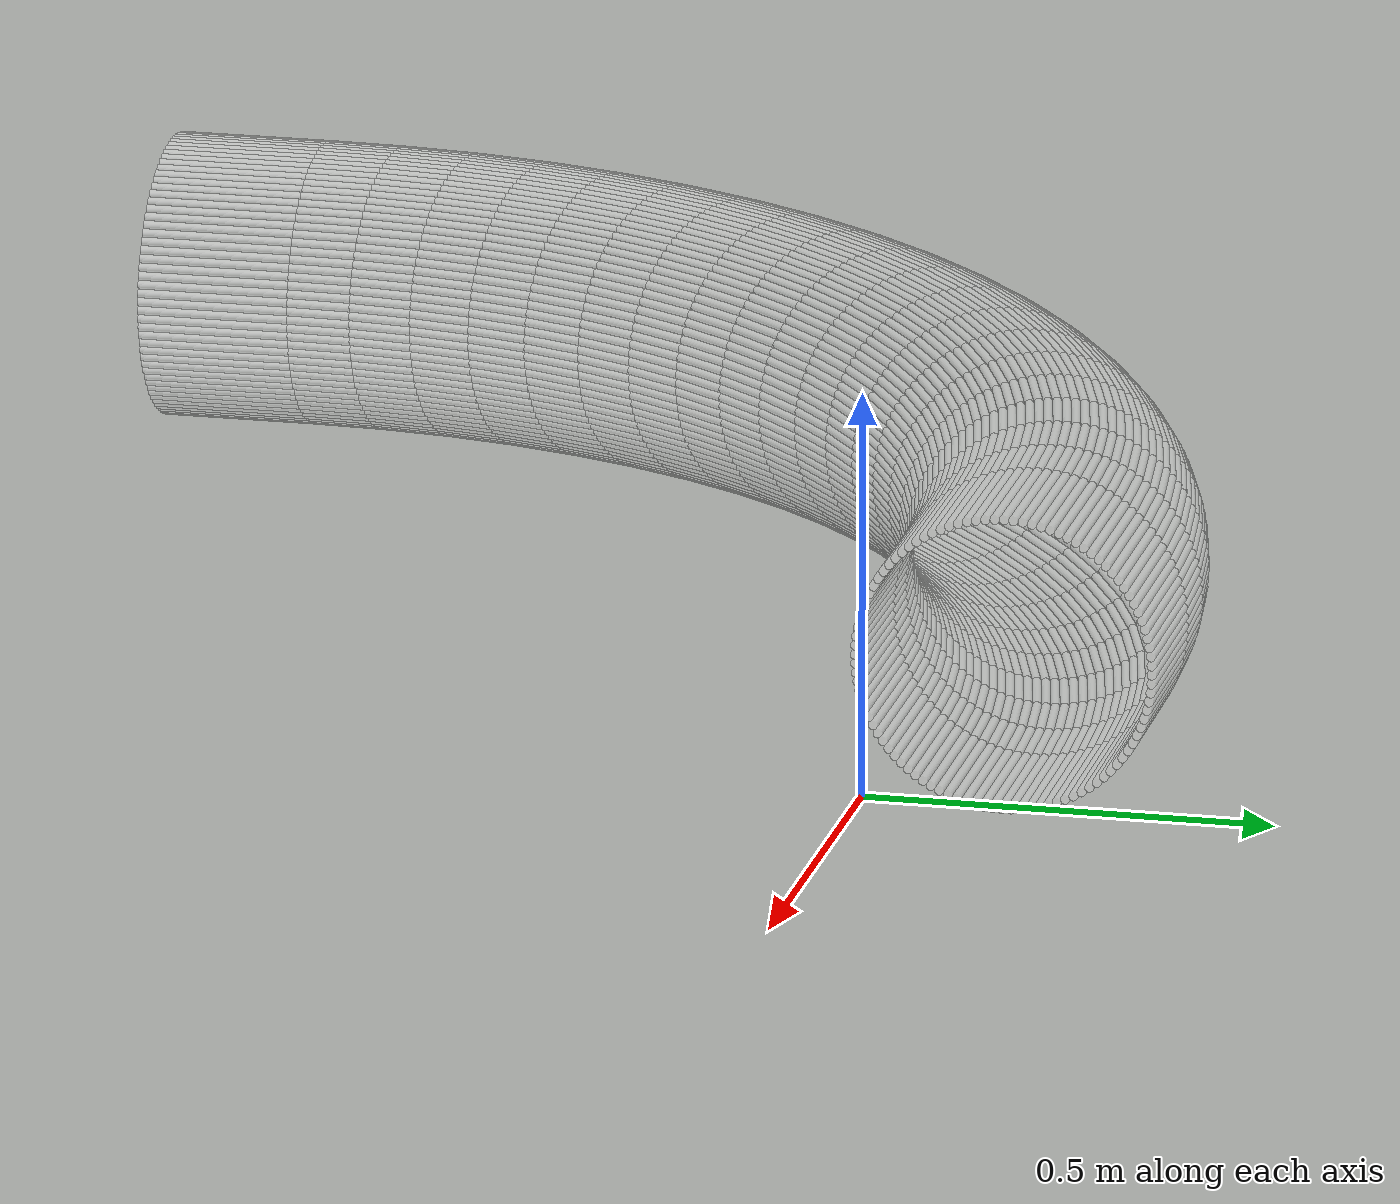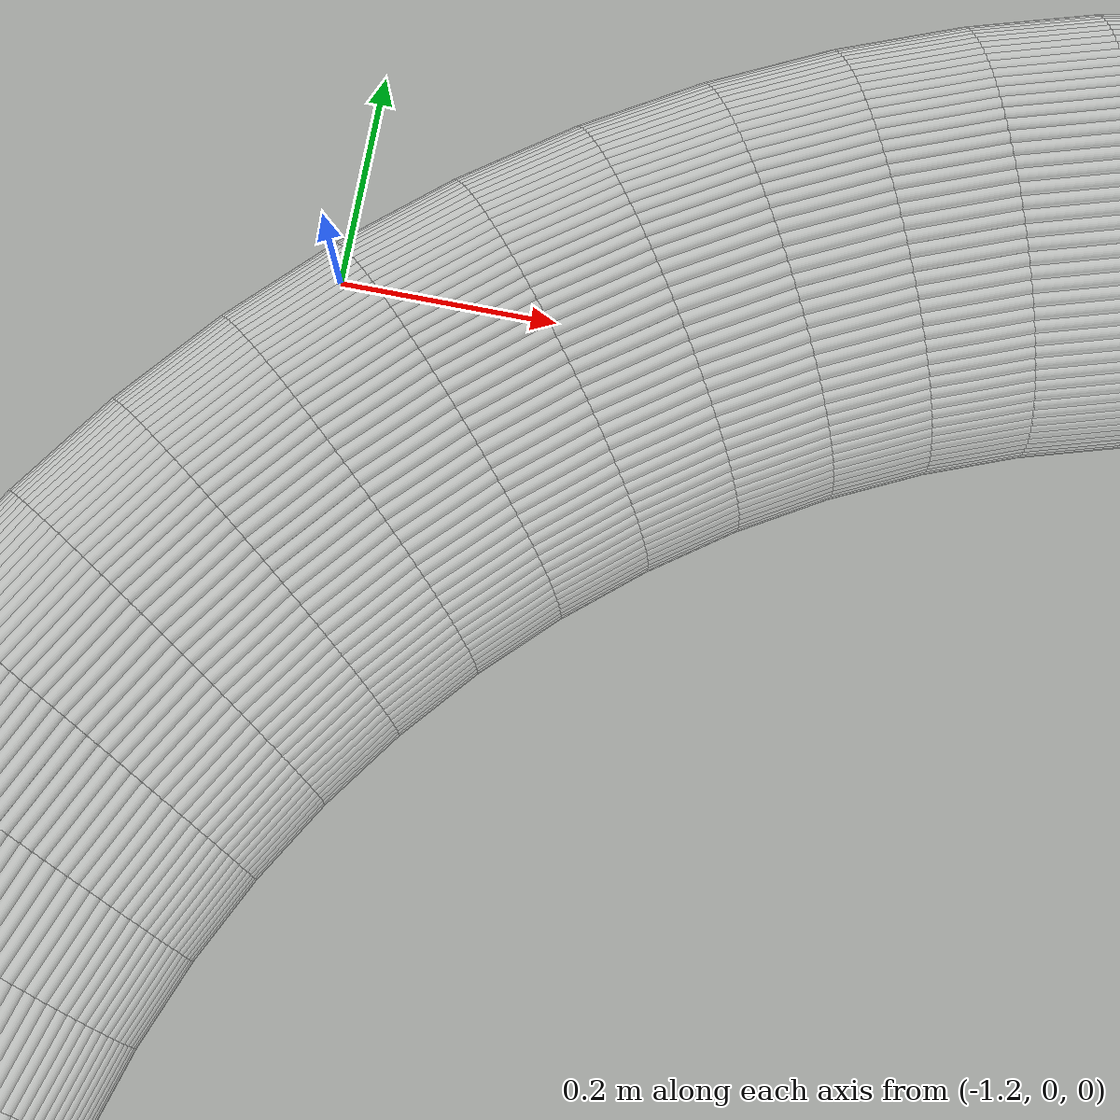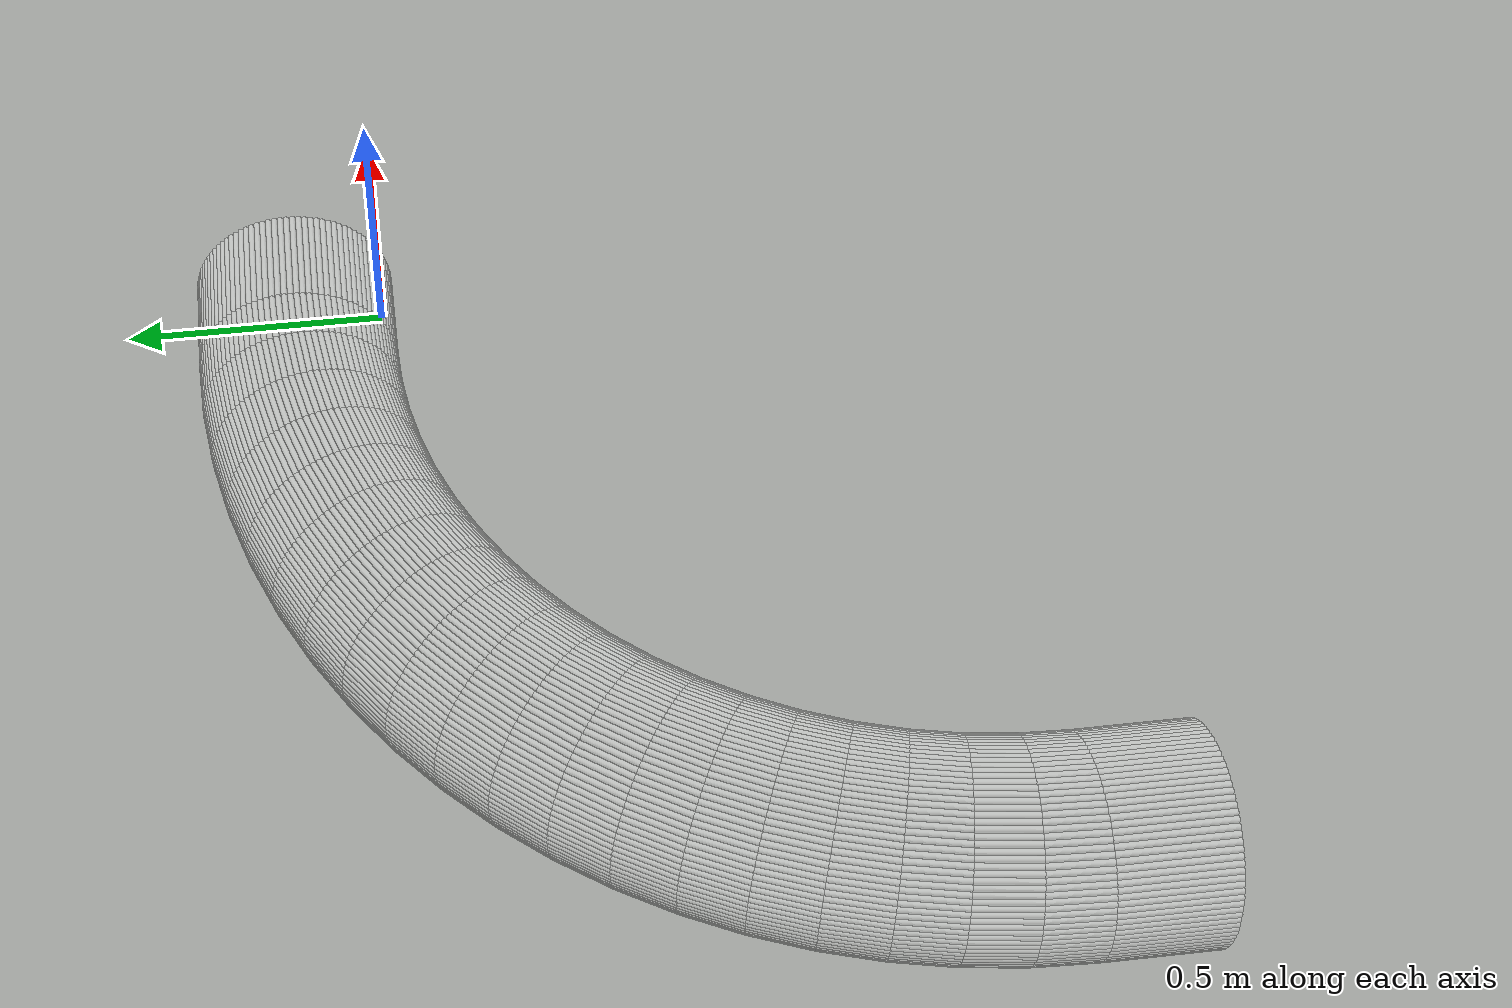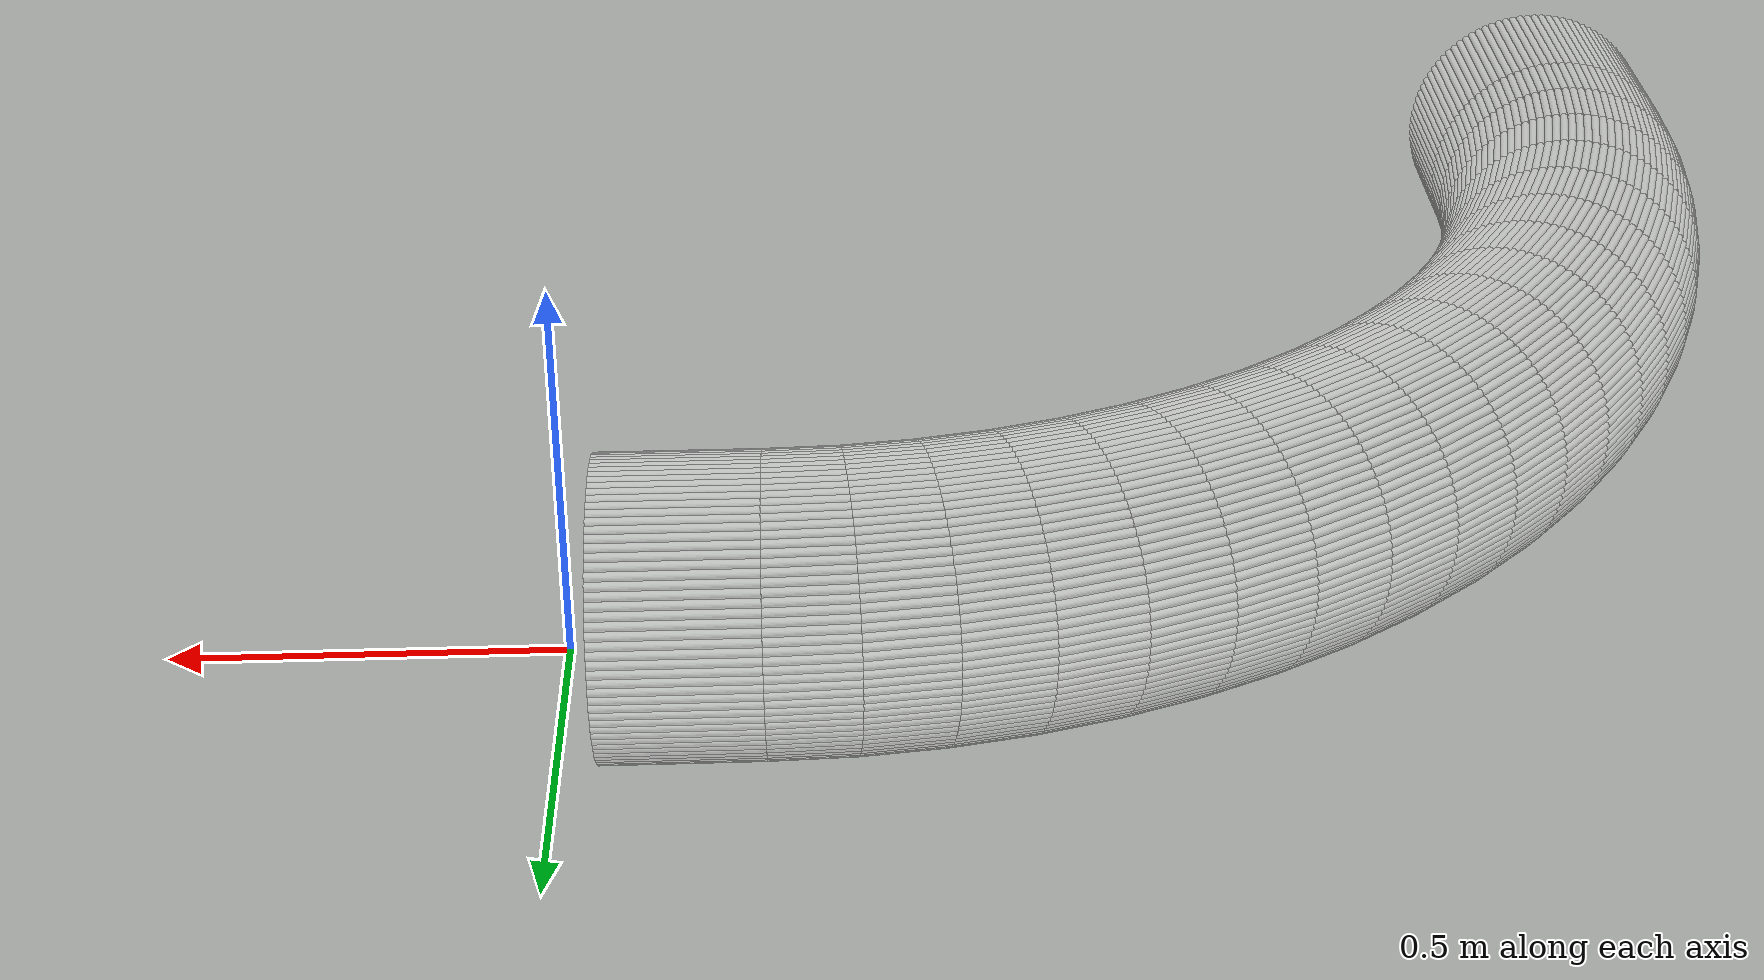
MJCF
<?xml version="1.0" encoding="utf-8"?>
<mujoco>
   <worldbody>
   <body pos="-0.25 -1.04 -0.02" euler="0 0 90">
      <geom euler=" 0 10 0 " fromto="1.38 -0.2 0.18 1.38 0 0.18" rgba="1 1 1 0.35"
            size="0.0056539"
            type="cylinder"/>
      <geom euler=" 0 20 0 " fromto="1.3796 -0.2 0.1913 1.3796 0 0.1913" rgba="1 1 1 0.35"
            size="0.0056539"
            type="cylinder"/>
      <geom euler=" 0 30 0 " fromto="1.3786 -0.2 0.20256 1.3786 0 0.20256"
            rgba="1 1 1 0.35"
            size="0.0056539"
            type="cylinder"/>
      <geom euler=" 0 40 0 " fromto="1.3768 -0.2 0.21373 1.3768 0 0.21373"
            rgba="1 1 1 0.35"
            size="0.0056539"
            type="cylinder"/>
      <geom euler=" 0 50 0 " fromto="1.3743 -0.2 0.22476 1.3743 0 0.22476"
            rgba="1 1 1 0.35"
            size="0.0056539"
            type="cylinder"/>
      <geom euler=" 0 60 0 " fromto="1.3712 -0.2 0.23562 1.3712 0 0.23562"
            rgba="1 1 1 0.35"
            size="0.0056539"
            type="cylinder"/>
      <geom euler=" 0 70 0 " fromto="1.3674 -0.2 0.24626 1.3674 0 0.24626"
            rgba="1 1 1 0.35"
            size="0.0056539"
            type="cylinder"/>
      <geom euler=" 0 80 0 " fromto="1.3629 -0.2 0.25664 1.3629 0 0.25664"
            rgba="1 1 1 0.35"
            size="0.0056539"
            type="cylinder"/>
      <geom euler=" 0 90 0 " fromto="1.3577 -0.2 0.26672 1.3577 0 0.26672"
            rgba="1 1 1 0.35"
            size="0.0056539"
            type="cylinder"/>
      <geom euler=" 0 100 0 " fromto="1.352 -0.2 0.27645 1.352 0 0.27645" rgba="1 1 1 0.35"
            size="0.0056539"
            type="cylinder"/>
      <geom euler=" 0 110 0 " fromto="1.3456 -0.2 0.2858 1.3456 0 0.2858" rgba="1 1 1 0.35"
            size="0.0056539"
            type="cylinder"/>
      <geom euler=" 0 120 0 " fromto="1.3387 -0.2 0.29474 1.3387 0 0.29474"
            rgba="1 1 1 0.35"
            size="0.0056539"
            type="cylinder"/>
      <geom euler=" 0 130 0 " fromto="1.3312 -0.2 0.30322 1.3312 0 0.30322"
            rgba="1 1 1 0.35"
            size="0.0056539"
            type="cylinder"/>
      <geom euler=" 0 140 0 " fromto="1.3232 -0.2 0.31121 1.3232 0 0.31121"
            rgba="1 1 1 0.35"
            size="0.0056539"
            type="cylinder"/>
      <geom euler=" 0 150 0 " fromto="1.3147 -0.2 0.31869 1.3147 0 0.31869"
            rgba="1 1 1 0.35"
            size="0.0056539"
            type="cylinder"/>
      <geom euler=" 0 160 0 " fromto="1.3058 -0.2 0.32562 1.3058 0 0.32562"
            rgba="1 1 1 0.35"
            size="0.0056539"
            type="cylinder"/>
      <geom euler=" 0 170 0 " fromto="1.2964 -0.2 0.33198 1.2964 0 0.33198"
            rgba="1 1 1 0.35"
            size="0.0056539"
            type="cylinder"/>
      <geom euler=" 0 180 0 " fromto="1.2867 -0.2 0.33774 1.2867 0 0.33774"
            rgba="1 1 1 0.35"
            size="0.0056539"
            type="cylinder"/>
      <geom euler=" 0 190 0 " fromto="1.2766 -0.2 0.34287 1.2766 0 0.34287"
            rgba="1 1 1 0.35"
            size="0.0056539"
            type="cylinder"/>
      <geom euler=" 0 200 0 " fromto="1.2663 -0.2 0.34736 1.2663 0 0.34736"
            rgba="1 1 1 0.35"
            size="0.0056539"
            type="cylinder"/>
      <geom euler=" 0 210 0 " fromto="1.2556 -0.2 0.35119 1.2556 0 0.35119"
            rgba="1 1 1 0.35"
            size="0.0056539"
            type="cylinder"/>
      <geom euler=" 0 220 0 " fromto="1.2448 -0.2 0.35434 1.2448 0 0.35434"
            rgba="1 1 1 0.35"
            size="0.0056539"
            type="cylinder"/>
      <geom euler=" 0 230 0 " fromto="1.2337 -0.2 0.35681 1.2337 0 0.35681"
            rgba="1 1 1 0.35"
            size="0.0056539"
            type="cylinder"/>
      <geom euler=" 0 240 0 " fromto="1.2226 -0.2 0.35858 1.2226 0 0.35858"
            rgba="1 1 1 0.35"
            size="0.0056539"
            type="cylinder"/>
      <geom euler=" 0 250 0 " fromto="1.2113 -0.2 0.35964 1.2113 0 0.35964"
            rgba="1 1 1 0.35"
            size="0.0056539"
            type="cylinder"/>
      <geom euler=" 0 260 0 " fromto="1.2 -0.2 0.36 1.2 0 0.36" rgba="1 1 1 0.35"
            size="0.0056539"
            type="cylinder"/>
      <geom euler=" 0 270 0 " fromto="1.1887 -0.2 0.35964 1.1887 0 0.35964"
            rgba="1 1 1 0.35"
            size="0.0056539"
            type="cylinder"/>
      <geom euler=" 0 280 0 " fromto="1.1774 -0.2 0.35858 1.1774 0 0.35858"
            rgba="1 1 1 0.35"
            size="0.0056539"
            type="cylinder"/>
      <geom euler=" 0 290 0 " fromto="1.1663 -0.2 0.35681 1.1663 0 0.35681"
            rgba="1 1 1 0.35"
            size="0.0056539"
            type="cylinder"/>
      <geom euler=" 0 300 0 " fromto="1.1552 -0.2 0.35434 1.1552 0 0.35434"
            rgba="1 1 1 0.35"
            size="0.0056539"
            type="cylinder"/>
      <geom euler=" 0 310 0 " fromto="1.1444 -0.2 0.35119 1.1444 0 0.35119"
            rgba="1 1 1 0.35"
            size="0.0056539"
            type="cylinder"/>
      <geom euler=" 0 320 0 " fromto="1.1337 -0.2 0.34736 1.1337 0 0.34736"
            rgba="1 1 1 0.35"
            size="0.0056539"
            type="cylinder"/>
      <geom euler=" 0 330 0 " fromto="1.1234 -0.2 0.34287 1.1234 0 0.34287"
            rgba="1 1 1 0.35"
            size="0.0056539"
            type="cylinder"/>
      <geom euler=" 0 340 0 " fromto="1.1133 -0.2 0.33774 1.1133 0 0.33774"
            rgba="1 1 1 0.35"
            size="0.0056539"
            type="cylinder"/>
      <geom euler=" 0 350 0 " fromto="1.1036 -0.2 0.33198 1.1036 0 0.33198"
            rgba="1 1 1 0.35"
            size="0.0056539"
            type="cylinder"/>
      <geom euler=" 0 360 0 " fromto="1.0942 -0.2 0.32562 1.0942 0 0.32562"
            rgba="1 1 1 0.35"
            size="0.0056539"
            type="cylinder"/>
      <geom euler=" 0 370 0 " fromto="1.0853 -0.2 0.31869 1.0853 0 0.31869"
            rgba="1 1 1 0.35"
            size="0.0056539"
            type="cylinder"/>
      <geom euler=" 0 380 0 " fromto="1.0768 -0.2 0.31121 1.0768 0 0.31121"
            rgba="1 1 1 0.35"
            size="0.0056539"
            type="cylinder"/>
      <geom euler=" 0 390 0 " fromto="1.0688 -0.2 0.30322 1.0688 0 0.30322"
            rgba="1 1 1 0.35"
            size="0.0056539"
            type="cylinder"/>
      <geom euler=" 0 400 0 " fromto="1.0613 -0.2 0.29474 1.0613 0 0.29474"
            rgba="1 1 1 0.35"
            size="0.0056539"
            type="cylinder"/>
      <geom euler=" 0 410 0 " fromto="1.0544 -0.2 0.2858 1.0544 0 0.2858" rgba="1 1 1 0.35"
            size="0.0056539"
            type="cylinder"/>
      <geom euler=" 0 420 0 " fromto="1.048 -0.2 0.27645 1.048 0 0.27645" rgba="1 1 1 0.35"
            size="0.0056539"
            type="cylinder"/>
      <geom euler=" 0 430 0 " fromto="1.0423 -0.2 0.26672 1.0423 0 0.26672"
            rgba="1 1 1 0.35"
            size="0.0056539"
            type="cylinder"/>
      <geom euler=" 0 440 0 " fromto="1.0371 -0.2 0.25664 1.0371 0 0.25664"
            rgba="1 1 1 0.35"
            size="0.0056539"
            type="cylinder"/>
      <geom euler=" 0 450 0 " fromto="1.0326 -0.2 0.24626 1.0326 0 0.24626"
            rgba="1 1 1 0.35"
            size="0.0056539"
            type="cylinder"/>
      <geom euler=" 0 460 0 " fromto="1.0288 -0.2 0.23562 1.0288 0 0.23562"
            rgba="1 1 1 0.35"
            size="0.0056539"
            type="cylinder"/>
      <geom euler=" 0 470 0 " fromto="1.0257 -0.2 0.22476 1.0257 0 0.22476"
            rgba="1 1 1 0.35"
            size="0.0056539"
            type="cylinder"/>
      <geom euler=" 0 480 0 " fromto="1.0232 -0.2 0.21373 1.0232 0 0.21373"
            rgba="1 1 1 0.35"
            size="0.0056539"
            type="cylinder"/>
      <geom euler=" 0 490 0 " fromto="1.0214 -0.2 0.20256 1.0214 0 0.20256"
            rgba="1 1 1 0.35"
            size="0.0056539"
            type="cylinder"/>
      <geom euler=" 0 500 0 " fromto="1.0204 -0.2 0.1913 1.0204 0 0.1913" rgba="1 1 1 0.35"
            size="0.0056539"
            type="cylinder"/>
      <geom euler=" 0 510 0 " fromto="1.02 -0.2 0.18 1.02 0 0.18" rgba="1 1 1 0.35"
            size="0.0056539"
            type="cylinder"/>
      <geom euler=" 0 520 0 " fromto="1.0204 -0.2 0.1687 1.0204 0 0.1687" rgba="1 1 1 0.35"
            size="0.0056539"
            type="cylinder"/>
      <geom euler=" 0 530 0 " fromto="1.0214 -0.2 0.15744 1.0214 0 0.15744"
            rgba="1 1 1 0.35"
            size="0.0056539"
            type="cylinder"/>
      <geom euler=" 0 540 0 " fromto="1.0232 -0.2 0.14627 1.0232 0 0.14627"
            rgba="1 1 1 0.35"
            size="0.0056539"
            type="cylinder"/>
      <geom euler=" 0 550 0 " fromto="1.0257 -0.2 0.13524 1.0257 0 0.13524"
            rgba="1 1 1 0.35"
            size="0.0056539"
            type="cylinder"/>
      <geom euler=" 0 560 0 " fromto="1.0288 -0.2 0.12438 1.0288 0 0.12438"
            rgba="1 1 1 0.35"
            size="0.0056539"
            type="cylinder"/>
      <geom euler=" 0 570 0 " fromto="1.0326 -0.2 0.11374 1.0326 0 0.11374"
            rgba="1 1 1 0.35"
            size="0.0056539"
            type="cylinder"/>
      <geom euler=" 0 580 0 " fromto="1.0371 -0.2 0.10336 1.0371 0 0.10336"
            rgba="1 1 1 0.35"
            size="0.0056539"
            type="cylinder"/>
      <geom euler=" 0 590 0 " fromto="1.0423 -0.2 0.093284 1.0423 0 0.093284"
            rgba="1 1 1 0.35"
            size="0.0056539"
            type="cylinder"/>
      <geom euler=" 0 600 0 " fromto="1.048 -0.2 0.083551 1.048 0 0.083551"
            rgba="1 1 1 0.35"
            size="0.0056539"
            type="cylinder"/>
      <geom euler=" 0 610 0 " fromto="1.0544 -0.2 0.074199 1.0544 0 0.074199"
            rgba="1 1 1 0.35"
            size="0.0056539"
            type="cylinder"/>
      <geom euler=" 0 620 0 " fromto="1.0613 -0.2 0.065264 1.0613 0 0.065264"
            rgba="1 1 1 0.35"
            size="0.0056539"
            type="cylinder"/>
      <geom euler=" 0 630 0 " fromto="1.0688 -0.2 0.056782 1.0688 0 0.056782"
            rgba="1 1 1 0.35"
            size="0.0056539"
            type="cylinder"/>
      <geom euler=" 0 640 0 " fromto="1.0768 -0.2 0.048786 1.0768 0 0.048786"
            rgba="1 1 1 0.35"
            size="0.0056539"
            type="cylinder"/>
      <geom euler=" 0 650 0 " fromto="1.0853 -0.2 0.041308 1.0853 0 0.041308"
            rgba="1 1 1 0.35"
            size="0.0056539"
            type="cylinder"/>
      <geom euler=" 0 660 0 " fromto="1.0942 -0.2 0.034377 1.0942 0 0.034377"
            rgba="1 1 1 0.35"
            size="0.0056539"
            type="cylinder"/>
      <geom euler=" 0 670 0 " fromto="1.1036 -0.2 0.028021 1.1036 0 0.028021"
            rgba="1 1 1 0.35"
            size="0.0056539"
            type="cylinder"/>
      <geom euler=" 0 680 0 " fromto="1.1133 -0.2 0.022265 1.1133 0 0.022265"
            rgba="1 1 1 0.35"
            size="0.0056539"
            type="cylinder"/>
      <geom euler=" 0 690 0 " fromto="1.1234 -0.2 0.017131 1.1234 0 0.017131"
            rgba="1 1 1 0.35"
            size="0.0056539"
            type="cylinder"/>
      <geom euler=" 0 700 0 " fromto="1.1337 -0.2 0.01264 1.1337 0 0.01264"
            rgba="1 1 1 0.35"
            size="0.0056539"
            type="cylinder"/>
      <geom euler=" 0 710 0 " fromto="1.1444 -0.2 0.0088098 1.1444 0 0.0088098"
            rgba="1 1 1 0.35"
            size="0.0056539"
            type="cylinder"/>
      <geom euler=" 0 720 0 " fromto="1.1552 -0.2 0.005655 1.1552 0 0.005655"
            rgba="1 1 1 0.35"
            size="0.0056539"
            type="cylinder"/>
      <geom euler=" 0 730 0 " fromto="1.1663 -0.2 0.0031883 1.1663 0 0.0031883"
            rgba="1 1 1 0.35"
            size="0.0056539"
            type="cylinder"/>
      <geom euler=" 0 740 0 " fromto="1.1774 -0.2 0.0014194 1.1774 0 0.0014194"
            rgba="1 1 1 0.35"
            size="0.0056539"
            type="cylinder"/>
      <geom euler=" 0 750 0 " fromto="1.1887 -0.2 0.00035519 1.1887 0 0.00035519"
            rgba="1 1 1 0.35"
            size="0.0056539"
            type="cylinder"/>
      <geom euler=" 0 760 0 " fromto="1.2 -0.2 0 1.2 0 0" rgba="1 1 1 0.35"
            size="0.0056539"
            type="cylinder"/>
      <geom euler=" 0 770 0 " fromto="1.2113 -0.2 0.00035519 1.2113 0 0.00035519"
            rgba="1 1 1 0.35"
            size="0.0056539"
            type="cylinder"/>
      <geom euler=" 0 780 0 " fromto="1.2226 -0.2 0.0014194 1.2226 0 0.0014194"
            rgba="1 1 1 0.35"
            size="0.0056539"
            type="cylinder"/>
      <geom euler=" 0 790 0 " fromto="1.2337 -0.2 0.0031883 1.2337 0 0.0031883"
            rgba="1 1 1 0.35"
            size="0.0056539"
            type="cylinder"/>
      <geom euler=" 0 800 0 " fromto="1.2448 -0.2 0.005655 1.2448 0 0.005655"
            rgba="1 1 1 0.35"
            size="0.0056539"
            type="cylinder"/>
      <geom euler=" 0 810 0 " fromto="1.2556 -0.2 0.0088098 1.2556 0 0.0088098"
            rgba="1 1 1 0.35"
            size="0.0056539"
            type="cylinder"/>
      <geom euler=" 0 820 0 " fromto="1.2663 -0.2 0.01264 1.2663 0 0.01264"
            rgba="1 1 1 0.35"
            size="0.0056539"
            type="cylinder"/>
      <geom euler=" 0 830 0 " fromto="1.2766 -0.2 0.017131 1.2766 0 0.017131"
            rgba="1 1 1 0.35"
            size="0.0056539"
            type="cylinder"/>
      <geom euler=" 0 840 0 " fromto="1.2867 -0.2 0.022265 1.2867 0 0.022265"
            rgba="1 1 1 0.35"
            size="0.0056539"
            type="cylinder"/>
      <geom euler=" 0 850 0 " fromto="1.2964 -0.2 0.028021 1.2964 0 0.028021"
            rgba="1 1 1 0.35"
            size="0.0056539"
            type="cylinder"/>
      <geom euler=" 0 860 0 " fromto="1.3058 -0.2 0.034377 1.3058 0 0.034377"
            rgba="1 1 1 0.35"
            size="0.0056539"
            type="cylinder"/>
      <geom euler=" 0 870 0 " fromto="1.3147 -0.2 0.041308 1.3147 0 0.041308"
            rgba="1 1 1 0.35"
            size="0.0056539"
            type="cylinder"/>
      <geom euler=" 0 880 0 " fromto="1.3232 -0.2 0.048786 1.3232 0 0.048786"
            rgba="1 1 1 0.35"
            size="0.0056539"
            type="cylinder"/>
      <geom euler=" 0 890 0 " fromto="1.3312 -0.2 0.056782 1.3312 0 0.056782"
            rgba="1 1 1 0.35"
            size="0.0056539"
            type="cylinder"/>
      <geom euler=" 0 900 0 " fromto="1.3387 -0.2 0.065264 1.3387 0 0.065264"
            rgba="1 1 1 0.35"
            size="0.0056539"
            type="cylinder"/>
      <geom euler=" 0 910 0 " fromto="1.3456 -0.2 0.074199 1.3456 0 0.074199"
            rgba="1 1 1 0.35"
            size="0.0056539"
            type="cylinder"/>
      <geom euler=" 0 920 0 " fromto="1.352 -0.2 0.083551 1.352 0 0.083551"
            rgba="1 1 1 0.35"
            size="0.0056539"
            type="cylinder"/>
      <geom euler=" 0 930 0 " fromto="1.3577 -0.2 0.093284 1.3577 0 0.093284"
            rgba="1 1 1 0.35"
            size="0.0056539"
            type="cylinder"/>
      <geom euler=" 0 940 0 " fromto="1.3629 -0.2 0.10336 1.3629 0 0.10336"
            rgba="1 1 1 0.35"
            size="0.0056539"
            type="cylinder"/>
      <geom euler=" 0 950 0 " fromto="1.3674 -0.2 0.11374 1.3674 0 0.11374"
            rgba="1 1 1 0.35"
            size="0.0056539"
            type="cylinder"/>
      <geom euler=" 0 960 0 " fromto="1.3712 -0.2 0.12438 1.3712 0 0.12438"
            rgba="1 1 1 0.35"
            size="0.0056539"
            type="cylinder"/>
      <geom euler=" 0 970 0 " fromto="1.3743 -0.2 0.13524 1.3743 0 0.13524"
            rgba="1 1 1 0.35"
            size="0.0056539"
            type="cylinder"/>
      <geom euler=" 0 980 0 " fromto="1.3768 -0.2 0.14627 1.3768 0 0.14627"
            rgba="1 1 1 0.35"
            size="0.0056539"
            type="cylinder"/>
      <geom euler=" 0 990 0 " fromto="1.3786 -0.2 0.15744 1.3786 0 0.15744"
            rgba="1 1 1 0.35"
            size="0.0056539"
            type="cylinder"/>
      <geom euler=" 0 1000 0 " fromto="1.3796 -0.2 0.1687 1.3796 0 0.1687"
            rgba="1 1 1 0.35"
            size="0.0056539"
            type="cylinder"/>
      <geom euler=" 0 10 0 " fromto="1.38 0 0.18 1.3753 0.11396 0.18" rgba="1 1 1 0.35"
            size="0.0056539"
            type="cylinder"/>
      <geom euler=" 0 20 0 " fromto="1.3796 0 0.1913 1.3749 0.11393 0.1913"
            rgba="1 1 1 0.35"
            size="0.0056539"
            type="cylinder"/>
      <geom euler=" 0 30 0 " fromto="1.3786 0 0.20256 1.3739 0.11384 0.20256"
            rgba="1 1 1 0.35"
            size="0.0056539"
            type="cylinder"/>
      <geom euler=" 0 40 0 " fromto="1.3768 0 0.21373 1.3721 0.1137 0.21373"
            rgba="1 1 1 0.35"
            size="0.0056539"
            type="cylinder"/>
      <geom euler=" 0 50 0 " fromto="1.3743 0 0.22476 1.3697 0.11349 0.22476"
            rgba="1 1 1 0.35"
            size="0.0056539"
            type="cylinder"/>
      <geom euler=" 0 60 0 " fromto="1.3712 0 0.23562 1.3665 0.11323 0.23562"
            rgba="1 1 1 0.35"
            size="0.0056539"
            type="cylinder"/>
      <geom euler=" 0 70 0 " fromto="1.3674 0 0.24626 1.3627 0.11292 0.24626"
            rgba="1 1 1 0.35"
            size="0.0056539"
            type="cylinder"/>
      <geom euler=" 0 80 0 " fromto="1.3629 0 0.25664 1.3582 0.11254 0.25664"
            rgba="1 1 1 0.35"
            size="0.0056539"
            type="cylinder"/>
      <geom euler=" 0 90 0 " fromto="1.3577 0 0.26672 1.3531 0.11212 0.26672"
            rgba="1 1 1 0.35"
            size="0.0056539"
            type="cylinder"/>
      <geom euler=" 0 100 0 " fromto="1.352 0 0.27645 1.3474 0.11165 0.27645"
            rgba="1 1 1 0.35"
            size="0.0056539"
            type="cylinder"/>
      <geom euler=" 0 110 0 " fromto="1.3456 0 0.2858 1.341 0.11112 0.2858"
            rgba="1 1 1 0.35"
            size="0.0056539"
            type="cylinder"/>
      <geom euler=" 0 120 0 " fromto="1.3387 0 0.29474 1.3341 0.11055 0.29474"
            rgba="1 1 1 0.35"
            size="0.0056539"
            type="cylinder"/>
      <geom euler=" 0 130 0 " fromto="1.3312 0 0.30322 1.3267 0.10993 0.30322"
            rgba="1 1 1 0.35"
            size="0.0056539"
            type="cylinder"/>
      <geom euler=" 0 140 0 " fromto="1.3232 0 0.31121 1.3187 0.10927 0.31121"
            rgba="1 1 1 0.35"
            size="0.0056539"
            type="cylinder"/>
      <geom euler=" 0 150 0 " fromto="1.3147 0 0.31869 1.3102 0.10857 0.31869"
            rgba="1 1 1 0.35"
            size="0.0056539"
            type="cylinder"/>
      <geom euler=" 0 160 0 " fromto="1.3058 0 0.32562 1.3013 0.10783 0.32562"
            rgba="1 1 1 0.35"
            size="0.0056539"
            type="cylinder"/>
      <geom euler=" 0 170 0 " fromto="1.2964 0 0.33198 1.292 0.10706 0.33198"
            rgba="1 1 1 0.35"
            size="0.0056539"
            type="cylinder"/>
      <geom euler=" 0 180 0 " fromto="1.2867 0 0.33774 1.2823 0.10626 0.33774"
            rgba="1 1 1 0.35"
            size="0.0056539"
            type="cylinder"/>
      <geom euler=" 0 190 0 " fromto="1.2766 0 0.34287 1.2723 0.10542 0.34287"
            rgba="1 1 1 0.35"
            size="0.0056539"
            type="cylinder"/>
      <geom euler=" 0 200 0 " fromto="1.2663 0 0.34736 1.2619 0.10457 0.34736"
            rgba="1 1 1 0.35"
            size="0.0056539"
            type="cylinder"/>
      <geom euler=" 0 210 0 " fromto="1.2556 0 0.35119 1.2513 0.10369 0.35119"
            rgba="1 1 1 0.35"
            size="0.0056539"
            type="cylinder"/>
      <geom euler=" 0 220 0 " fromto="1.2448 0 0.35434 1.2405 0.10279 0.35434"
            rgba="1 1 1 0.35"
            size="0.0056539"
            type="cylinder"/>
      <geom euler=" 0 230 0 " fromto="1.2337 0 0.35681 1.2295 0.10188 0.35681"
            rgba="1 1 1 0.35"
            size="0.0056539"
            type="cylinder"/>
      <geom euler=" 0 240 0 " fromto="1.2226 0 0.35858 1.2184 0.10096 0.35858"
            rgba="1 1 1 0.35"
            size="0.0056539"
            type="cylinder"/>
      <geom euler=" 0 250 0 " fromto="1.2113 0 0.35964 1.2072 0.10003 0.35964"
            rgba="1 1 1 0.35"
            size="0.0056539"
            type="cylinder"/>
      <geom euler=" 0 260 0 " fromto="1.2 0 0.36 1.1959 0.099095 0.36" rgba="1 1 1 0.35"
            size="0.0056539"
            type="cylinder"/>
      <geom euler=" 0 270 0 " fromto="1.1887 0 0.35964 1.1846 0.098162 0.35964"
            rgba="1 1 1 0.35"
            size="0.0056539"
            type="cylinder"/>
      <geom euler=" 0 280 0 " fromto="1.1774 0 0.35858 1.1734 0.097232 0.35858"
            rgba="1 1 1 0.35"
            size="0.0056539"
            type="cylinder"/>
      <geom euler=" 0 290 0 " fromto="1.1663 0 0.35681 1.1623 0.09631 0.35681"
            rgba="1 1 1 0.35"
            size="0.0056539"
            type="cylinder"/>
      <geom euler=" 0 300 0 " fromto="1.1552 0 0.35434 1.1513 0.095399 0.35434"
            rgba="1 1 1 0.35"
            size="0.0056539"
            type="cylinder"/>
      <geom euler=" 0 310 0 " fromto="1.1444 0 0.35119 1.1405 0.094502 0.35119"
            rgba="1 1 1 0.35"
            size="0.0056539"
            type="cylinder"/>
      <geom euler=" 0 320 0 " fromto="1.1337 0 0.34736 1.1299 0.093623 0.34736"
            rgba="1 1 1 0.35"
            size="0.0056539"
            type="cylinder"/>
      <geom euler=" 0 330 0 " fromto="1.1234 0 0.34287 1.1195 0.092766 0.34287"
            rgba="1 1 1 0.35"
            size="0.0056539"
            type="cylinder"/>
      <geom euler=" 0 340 0 " fromto="1.1133 0 0.33774 1.1095 0.091934 0.33774"
            rgba="1 1 1 0.35"
            size="0.0056539"
            type="cylinder"/>
      <geom euler=" 0 350 0 " fromto="1.1036 0 0.33198 1.0998 0.091131 0.33198"
            rgba="1 1 1 0.35"
            size="0.0056539"
            type="cylinder"/>
      <geom euler=" 0 360 0 " fromto="1.0942 0 0.32562 1.0905 0.090358 0.32562"
            rgba="1 1 1 0.35"
            size="0.0056539"
            type="cylinder"/>
      <geom euler=" 0 370 0 " fromto="1.0853 0 0.31869 1.0816 0.08962 0.31869"
            rgba="1 1 1 0.35"
            size="0.0056539"
            type="cylinder"/>
      <geom euler=" 0 380 0 " fromto="1.0768 0 0.31121 1.0731 0.08892 0.31121"
            rgba="1 1 1 0.35"
            size="0.0056539"
            type="cylinder"/>
      <geom euler=" 0 390 0 " fromto="1.0688 0 0.30322 1.0651 0.08826 0.30322"
            rgba="1 1 1 0.35"
            size="0.0056539"
            type="cylinder"/>
      <geom euler=" 0 400 0 " fromto="1.0613 0 0.29474 1.0577 0.087642 0.29474"
            rgba="1 1 1 0.35"
            size="0.0056539"
            type="cylinder"/>
      <geom euler=" 0 410 0 " fromto="1.0544 0 0.2858 1.0508 0.08707 0.2858"
            rgba="1 1 1 0.35"
            size="0.0056539"
            type="cylinder"/>
      <geom euler=" 0 420 0 " fromto="1.048 0 0.27645 1.0444 0.086545 0.27645"
            rgba="1 1 1 0.35"
            size="0.0056539"
            type="cylinder"/>
      <geom euler=" 0 430 0 " fromto="1.0423 0 0.26672 1.0387 0.08607 0.26672"
            rgba="1 1 1 0.35"
            size="0.0056539"
            type="cylinder"/>
      <geom euler=" 0 440 0 " fromto="1.0371 0 0.25664 1.0336 0.085646 0.25664"
            rgba="1 1 1 0.35"
            size="0.0056539"
            type="cylinder"/>
      <geom euler=" 0 450 0 " fromto="1.0326 0 0.24626 1.0291 0.085275 0.24626"
            rgba="1 1 1 0.35"
            size="0.0056539"
            type="cylinder"/>
      <geom euler=" 0 460 0 " fromto="1.0288 0 0.23562 1.0253 0.084958 0.23562"
            rgba="1 1 1 0.35"
            size="0.0056539"
            type="cylinder"/>
      <geom euler=" 0 470 0 " fromto="1.0257 0 0.22476 1.0222 0.084698 0.22476"
            rgba="1 1 1 0.35"
            size="0.0056539"
            type="cylinder"/>
      <geom euler=" 0 480 0 " fromto="1.0232 0 0.21373 1.0197 0.084494 0.21373"
            rgba="1 1 1 0.35"
            size="0.0056539"
            type="cylinder"/>
      <geom euler=" 0 490 0 " fromto="1.0214 0 0.20256 1.0179 0.084348 0.20256"
            rgba="1 1 1 0.35"
            size="0.0056539"
            type="cylinder"/>
      <geom euler=" 0 500 0 " fromto="1.0204 0 0.1913 1.0169 0.08426 0.1913"
            rgba="1 1 1 0.35"
            size="0.0056539"
            type="cylinder"/>
      <geom euler=" 0 510 0 " fromto="1.02 0 0.18 1.0165 0.084231 0.18" rgba="1 1 1 0.35"
            size="0.0056539"
            type="cylinder"/>
      <geom euler=" 0 520 0 " fromto="1.0204 0 0.1687 1.0169 0.08426 0.1687"
            rgba="1 1 1 0.35"
            size="0.0056539"
            type="cylinder"/>
      <geom euler=" 0 530 0 " fromto="1.0214 0 0.15744 1.0179 0.084348 0.15744"
            rgba="1 1 1 0.35"
            size="0.0056539"
            type="cylinder"/>
      <geom euler=" 0 540 0 " fromto="1.0232 0 0.14627 1.0197 0.084494 0.14627"
            rgba="1 1 1 0.35"
            size="0.0056539"
            type="cylinder"/>
      <geom euler=" 0 550 0 " fromto="1.0257 0 0.13524 1.0222 0.084698 0.13524"
            rgba="1 1 1 0.35"
            size="0.0056539"
            type="cylinder"/>
      <geom euler=" 0 560 0 " fromto="1.0288 0 0.12438 1.0253 0.084958 0.12438"
            rgba="1 1 1 0.35"
            size="0.0056539"
            type="cylinder"/>
      <geom euler=" 0 570 0 " fromto="1.0326 0 0.11374 1.0291 0.085275 0.11374"
            rgba="1 1 1 0.35"
            size="0.0056539"
            type="cylinder"/>
      <geom euler=" 0 580 0 " fromto="1.0371 0 0.10336 1.0336 0.085646 0.10336"
            rgba="1 1 1 0.35"
            size="0.0056539"
            type="cylinder"/>
      <geom euler=" 0 590 0 " fromto="1.0423 0 0.093284 1.0387 0.08607 0.093284"
            rgba="1 1 1 0.35"
            size="0.0056539"
            type="cylinder"/>
      <geom euler=" 0 600 0 " fromto="1.048 0 0.083551 1.0444 0.086545 0.083551"
            rgba="1 1 1 0.35"
            size="0.0056539"
            type="cylinder"/>
      <geom euler=" 0 610 0 " fromto="1.0544 0 0.074199 1.0508 0.08707 0.074199"
            rgba="1 1 1 0.35"
            size="0.0056539"
            type="cylinder"/>
      <geom euler=" 0 620 0 " fromto="1.0613 0 0.065264 1.0577 0.087642 0.065264"
            rgba="1 1 1 0.35"
            size="0.0056539"
            type="cylinder"/>
      <geom euler=" 0 630 0 " fromto="1.0688 0 0.056782 1.0651 0.08826 0.056782"
            rgba="1 1 1 0.35"
            size="0.0056539"
            type="cylinder"/>
      <geom euler=" 0 640 0 " fromto="1.0768 0 0.048786 1.0731 0.08892 0.048786"
            rgba="1 1 1 0.35"
            size="0.0056539"
            type="cylinder"/>
      <geom euler=" 0 650 0 " fromto="1.0853 0 0.041308 1.0816 0.08962 0.041308"
            rgba="1 1 1 0.35"
            size="0.0056539"
            type="cylinder"/>
      <geom euler=" 0 660 0 " fromto="1.0942 0 0.034377 1.0905 0.090358 0.034377"
            rgba="1 1 1 0.35"
            size="0.0056539"
            type="cylinder"/>
      <geom euler=" 0 670 0 " fromto="1.1036 0 0.028021 1.0998 0.091131 0.028021"
            rgba="1 1 1 0.35"
            size="0.0056539"
            type="cylinder"/>
      <geom euler=" 0 680 0 " fromto="1.1133 0 0.022265 1.1095 0.091934 0.022265"
            rgba="1 1 1 0.35"
            size="0.0056539"
            type="cylinder"/>
      <geom euler=" 0 690 0 " fromto="1.1234 0 0.017131 1.1195 0.092766 0.017131"
            rgba="1 1 1 0.35"
            size="0.0056539"
            type="cylinder"/>
      <geom euler=" 0 700 0 " fromto="1.1337 0 0.01264 1.1299 0.093623 0.01264"
            rgba="1 1 1 0.35"
            size="0.0056539"
            type="cylinder"/>
      <geom euler=" 0 710 0 " fromto="1.1444 0 0.0088098 1.1405 0.094502 0.0088098"
            rgba="1 1 1 0.35"
            size="0.0056539"
            type="cylinder"/>
      <geom euler=" 0 720 0 " fromto="1.1552 0 0.005655 1.1513 0.095399 0.005655"
            rgba="1 1 1 0.35"
            size="0.0056539"
            type="cylinder"/>
      <geom euler=" 0 730 0 " fromto="1.1663 0 0.0031883 1.1623 0.09631 0.0031883"
            rgba="1 1 1 0.35"
            size="0.0056539"
            type="cylinder"/>
      <geom euler=" 0 740 0 " fromto="1.1774 0 0.0014194 1.1734 0.097232 0.0014194"
            rgba="1 1 1 0.35"
            size="0.0056539"
            type="cylinder"/>
      <geom euler=" 0 750 0 " fromto="1.1887 0 0.00035519 1.1846 0.098162 0.00035519"
            rgba="1 1 1 0.35"
            size="0.0056539"
            type="cylinder"/>
      <geom euler=" 0 760 0 " fromto="1.2 0 0 1.1959 0.099095 0" rgba="1 1 1 0.35"
            size="0.0056539"
            type="cylinder"/>
      <geom euler=" 0 770 0 " fromto="1.2113 0 0.00035519 1.2072 0.10003 0.00035519"
            rgba="1 1 1 0.35"
            size="0.0056539"
            type="cylinder"/>
      <geom euler=" 0 780 0 " fromto="1.2226 0 0.0014194 1.2184 0.10096 0.0014194"
            rgba="1 1 1 0.35"
            size="0.0056539"
            type="cylinder"/>
      <geom euler=" 0 790 0 " fromto="1.2337 0 0.0031883 1.2295 0.10188 0.0031883"
            rgba="1 1 1 0.35"
            size="0.0056539"
            type="cylinder"/>
      <geom euler=" 0 800 0 " fromto="1.2448 0 0.005655 1.2405 0.10279 0.005655"
            rgba="1 1 1 0.35"
            size="0.0056539"
            type="cylinder"/>
      <geom euler=" 0 810 0 " fromto="1.2556 0 0.0088098 1.2513 0.10369 0.0088098"
            rgba="1 1 1 0.35"
            size="0.0056539"
            type="cylinder"/>
      <geom euler=" 0 820 0 " fromto="1.2663 0 0.01264 1.2619 0.10457 0.01264"
            rgba="1 1 1 0.35"
            size="0.0056539"
            type="cylinder"/>
      <geom euler=" 0 830 0 " fromto="1.2766 0 0.017131 1.2723 0.10542 0.017131"
            rgba="1 1 1 0.35"
            size="0.0056539"
            type="cylinder"/>
      <geom euler=" 0 840 0 " fromto="1.2867 0 0.022265 1.2823 0.10626 0.022265"
            rgba="1 1 1 0.35"
            size="0.0056539"
            type="cylinder"/>
      <geom euler=" 0 850 0 " fromto="1.2964 0 0.028021 1.292 0.10706 0.028021"
            rgba="1 1 1 0.35"
            size="0.0056539"
            type="cylinder"/>
      <geom euler=" 0 860 0 " fromto="1.3058 0 0.034377 1.3013 0.10783 0.034377"
            rgba="1 1 1 0.35"
            size="0.0056539"
            type="cylinder"/>
      <geom euler=" 0 870 0 " fromto="1.3147 0 0.041308 1.3102 0.10857 0.041308"
            rgba="1 1 1 0.35"
            size="0.0056539"
            type="cylinder"/>
      <geom euler=" 0 880 0 " fromto="1.3232 0 0.048786 1.3187 0.10927 0.048786"
            rgba="1 1 1 0.35"
            size="0.0056539"
            type="cylinder"/>
      <geom euler=" 0 890 0 " fromto="1.3312 0 0.056782 1.3267 0.10993 0.056782"
            rgba="1 1 1 0.35"
            size="0.0056539"
            type="cylinder"/>
      <geom euler=" 0 900 0 " fromto="1.3387 0 0.065264 1.3341 0.11055 0.065264"
            rgba="1 1 1 0.35"
            size="0.0056539"
            type="cylinder"/>
      <geom euler=" 0 910 0 " fromto="1.3456 0 0.074199 1.341 0.11112 0.074199"
            rgba="1 1 1 0.35"
            size="0.0056539"
            type="cylinder"/>
      <geom euler=" 0 920 0 " fromto="1.352 0 0.083551 1.3474 0.11165 0.083551"
            rgba="1 1 1 0.35"
            size="0.0056539"
            type="cylinder"/>
      <geom euler=" 0 930 0 " fromto="1.3577 0 0.093284 1.3531 0.11212 0.093284"
            rgba="1 1 1 0.35"
            size="0.0056539"
            type="cylinder"/>
      <geom euler=" 0 940 0 " fromto="1.3629 0 0.10336 1.3582 0.11254 0.10336"
            rgba="1 1 1 0.35"
            size="0.0056539"
            type="cylinder"/>
      <geom euler=" 0 950 0 " fromto="1.3674 0 0.11374 1.3627 0.11292 0.11374"
            rgba="1 1 1 0.35"
            size="0.0056539"
            type="cylinder"/>
      <geom euler=" 0 960 0 " fromto="1.3712 0 0.12438 1.3665 0.11323 0.12438"
            rgba="1 1 1 0.35"
            size="0.0056539"
            type="cylinder"/>
      <geom euler=" 0 970 0 " fromto="1.3743 0 0.13524 1.3697 0.11349 0.13524"
            rgba="1 1 1 0.35"
            size="0.0056539"
            type="cylinder"/>
      <geom euler=" 0 980 0 " fromto="1.3768 0 0.14627 1.3721 0.1137 0.14627"
            rgba="1 1 1 0.35"
            size="0.0056539"
            type="cylinder"/>
      <geom euler=" 0 990 0 " fromto="1.3786 0 0.15744 1.3739 0.11384 0.15744"
            rgba="1 1 1 0.35"
            size="0.0056539"
            type="cylinder"/>
      <geom euler=" 0 1000 0 " fromto="1.3796 0 0.1687 1.3749 0.11393 0.1687"
            rgba="1 1 1 0.35"
            size="0.0056539"
            type="cylinder"/>
      <geom euler=" 0 10 0 " fromto="1.3753 0.11396 0.18 1.3612 0.22714 0.18"
            rgba="1 1 1 0.35"
            size="0.0056539"
            type="cylinder"/>
      <geom euler=" 0 20 0 " fromto="1.3749 0.11393 0.1913 1.3608 0.22708 0.1913"
            rgba="1 1 1 0.35"
            size="0.0056539"
            type="cylinder"/>
      <geom euler=" 0 30 0 " fromto="1.3739 0.11384 0.20256 1.3598 0.22691 0.20256"
            rgba="1 1 1 0.35"
            size="0.0056539"
            type="cylinder"/>
      <geom euler=" 0 40 0 " fromto="1.3721 0.1137 0.21373 1.358 0.22662 0.21373"
            rgba="1 1 1 0.35"
            size="0.0056539"
            type="cylinder"/>
      <geom euler=" 0 50 0 " fromto="1.3697 0.11349 0.22476 1.3556 0.22621 0.22476"
            rgba="1 1 1 0.35"
            size="0.0056539"
            type="cylinder"/>
      <geom euler=" 0 60 0 " fromto="1.3665 0.11323 0.23562 1.3525 0.22569 0.23562"
            rgba="1 1 1 0.35"
            size="0.0056539"
            type="cylinder"/>
      <geom euler=" 0 70 0 " fromto="1.3627 0.11292 0.24626 1.3487 0.22506 0.24626"
            rgba="1 1 1 0.35"
            size="0.0056539"
            type="cylinder"/>
      <geom euler=" 0 80 0 " fromto="1.3582 0.11254 0.25664 1.3443 0.22432 0.25664"
            rgba="1 1 1 0.35"
            size="0.0056539"
            type="cylinder"/>
      <geom euler=" 0 90 0 " fromto="1.3531 0.11212 0.26672 1.3392 0.22348 0.26672"
            rgba="1 1 1 0.35"
            size="0.0056539"
            type="cylinder"/>
      <geom euler=" 0 100 0 " fromto="1.3474 0.11165 0.27645 1.3335 0.22253 0.27645"
            rgba="1 1 1 0.35"
            size="0.0056539"
            type="cylinder"/>
      <geom euler=" 0 110 0 " fromto="1.341 0.11112 0.2858 1.3273 0.22148 0.2858"
            rgba="1 1 1 0.35"
            size="0.0056539"
            type="cylinder"/>
      <geom euler=" 0 120 0 " fromto="1.3341 0.11055 0.29474 1.3204 0.22034 0.29474"
            rgba="1 1 1 0.35"
            size="0.0056539"
            type="cylinder"/>
      <geom euler=" 0 130 0 " fromto="1.3267 0.10993 0.30322 1.3131 0.21911 0.30322"
            rgba="1 1 1 0.35"
            size="0.0056539"
            type="cylinder"/>
      <geom euler=" 0 140 0 " fromto="1.3187 0.10927 0.31121 1.3052 0.21779 0.31121"
            rgba="1 1 1 0.35"
            size="0.0056539"
            type="cylinder"/>
      <geom euler=" 0 150 0 " fromto="1.3102 0.10857 0.31869 1.2968 0.2164 0.31869"
            rgba="1 1 1 0.35"
            size="0.0056539"
            type="cylinder"/>
      <geom euler=" 0 160 0 " fromto="1.3013 0.10783 0.32562 1.288 0.21493 0.32562"
            rgba="1 1 1 0.35"
            size="0.0056539"
            type="cylinder"/>
      <geom euler=" 0 170 0 " fromto="1.292 0.10706 0.33198 1.2788 0.21339 0.33198"
            rgba="1 1 1 0.35"
            size="0.0056539"
            type="cylinder"/>
      <geom euler=" 0 180 0 " fromto="1.2823 0.10626 0.33774 1.2692 0.21179 0.33774"
            rgba="1 1 1 0.35"
            size="0.0056539"
            type="cylinder"/>
      <geom euler=" 0 190 0 " fromto="1.2723 0.10542 0.34287 1.2592 0.21013 0.34287"
            rgba="1 1 1 0.35"
            size="0.0056539"
            type="cylinder"/>
      <geom euler=" 0 200 0 " fromto="1.2619 0.10457 0.34736 1.249 0.20842 0.34736"
            rgba="1 1 1 0.35"
            size="0.0056539"
            type="cylinder"/>
      <geom euler=" 0 210 0 " fromto="1.2513 0.10369 0.35119 1.2385 0.20667 0.35119"
            rgba="1 1 1 0.35"
            size="0.0056539"
            type="cylinder"/>
      <geom euler=" 0 220 0 " fromto="1.2405 0.10279 0.35434 1.2278 0.20488 0.35434"
            rgba="1 1 1 0.35"
            size="0.0056539"
            type="cylinder"/>
      <geom euler=" 0 230 0 " fromto="1.2295 0.10188 0.35681 1.2169 0.20307 0.35681"
            rgba="1 1 1 0.35"
            size="0.0056539"
            type="cylinder"/>
      <geom euler=" 0 240 0 " fromto="1.2184 0.10096 0.35858 1.2059 0.20123 0.35858"
            rgba="1 1 1 0.35"
            size="0.0056539"
            type="cylinder"/>
      <geom euler=" 0 250 0 " fromto="1.2072 0.10003 0.35964 1.1948 0.19937 0.35964"
            rgba="1 1 1 0.35"
            size="0.0056539"
            type="cylinder"/>
      <geom euler=" 0 260 0 " fromto="1.1959 0.099095 0.36 1.1836 0.19751 0.36"
            rgba="1 1 1 0.35"
            size="0.0056539"
            type="cylinder"/>
      <geom euler=" 0 270 0 " fromto="1.1846 0.098162 0.35964 1.1725 0.19565 0.35964"
            rgba="1 1 1 0.35"
            size="0.0056539"
            type="cylinder"/>
      <geom euler=" 0 280 0 " fromto="1.1734 0.097232 0.35858 1.1614 0.1938 0.35858"
            rgba="1 1 1 0.35"
            size="0.0056539"
            type="cylinder"/>
      <geom euler=" 0 290 0 " fromto="1.1623 0.09631 0.35681 1.1504 0.19196 0.35681"
            rgba="1 1 1 0.35"
            size="0.0056539"
            type="cylinder"/>
      <geom euler=" 0 300 0 " fromto="1.1513 0.095399 0.35434 1.1395 0.19015 0.35434"
            rgba="1 1 1 0.35"
            size="0.0056539"
            type="cylinder"/>
      <geom euler=" 0 310 0 " fromto="1.1405 0.094502 0.35119 1.1288 0.18836 0.35119"
            rgba="1 1 1 0.35"
            size="0.0056539"
            type="cylinder"/>
      <geom euler=" 0 320 0 " fromto="1.1299 0.093623 0.34736 1.1183 0.18661 0.34736"
            rgba="1 1 1 0.35"
            size="0.0056539"
            type="cylinder"/>
      <geom euler=" 0 330 0 " fromto="1.1195 0.092766 0.34287 1.108 0.1849 0.34287"
            rgba="1 1 1 0.35"
            size="0.0056539"
            type="cylinder"/>
      <geom euler=" 0 340 0 " fromto="1.1095 0.091934 0.33774 1.0981 0.18324 0.33774"
            rgba="1 1 1 0.35"
            size="0.0056539"
            type="cylinder"/>
      <geom euler=" 0 350 0 " fromto="1.0998 0.091131 0.33198 1.0885 0.18164 0.33198"
            rgba="1 1 1 0.35"
            size="0.0056539"
            type="cylinder"/>
      <geom euler=" 0 360 0 " fromto="1.0905 0.090358 0.32562 1.0793 0.1801 0.32562"
            rgba="1 1 1 0.35"
            size="0.0056539"
            type="cylinder"/>
      <geom euler=" 0 370 0 " fromto="1.0816 0.08962 0.31869 1.0705 0.17863 0.31869"
            rgba="1 1 1 0.35"
            size="0.0056539"
            type="cylinder"/>
      <geom euler=" 0 380 0 " fromto="1.0731 0.08892 0.31121 1.0621 0.17723 0.31121"
            rgba="1 1 1 0.35"
            size="0.0056539"
            type="cylinder"/>
      <geom euler=" 0 390 0 " fromto="1.0651 0.08826 0.30322 1.0542 0.17592 0.30322"
            rgba="1 1 1 0.35"
            size="0.0056539"
            type="cylinder"/>
      <geom euler=" 0 400 0 " fromto="1.0577 0.087642 0.29474 1.0468 0.17469 0.29474"
            rgba="1 1 1 0.35"
            size="0.0056539"
            type="cylinder"/>
      <geom euler=" 0 410 0 " fromto="1.0508 0.08707 0.2858 1.04 0.17354 0.2858"
            rgba="1 1 1 0.35"
            size="0.0056539"
            type="cylinder"/>
      <geom euler=" 0 420 0 " fromto="1.0444 0.086545 0.27645 1.0337 0.1725 0.27645"
            rgba="1 1 1 0.35"
            size="0.0056539"
            type="cylinder"/>
      <geom euler=" 0 430 0 " fromto="1.0387 0.08607 0.26672 1.028 0.17155 0.26672"
            rgba="1 1 1 0.35"
            size="0.0056539"
            type="cylinder"/>
      <geom euler=" 0 440 0 " fromto="1.0336 0.085646 0.25664 1.023 0.17071 0.25664"
            rgba="1 1 1 0.35"
            size="0.0056539"
            type="cylinder"/>
      <geom euler=" 0 450 0 " fromto="1.0291 0.085275 0.24626 1.0186 0.16997 0.24626"
            rgba="1 1 1 0.35"
            size="0.0056539"
            type="cylinder"/>
      <geom euler=" 0 460 0 " fromto="1.0253 0.084958 0.23562 1.0148 0.16934 0.23562"
            rgba="1 1 1 0.35"
            size="0.0056539"
            type="cylinder"/>
      <geom euler=" 0 470 0 " fromto="1.0222 0.084698 0.22476 1.0117 0.16882 0.22476"
            rgba="1 1 1 0.35"
            size="0.0056539"
            type="cylinder"/>
      <geom euler=" 0 480 0 " fromto="1.0197 0.084494 0.21373 1.0092 0.16841 0.21373"
            rgba="1 1 1 0.35"
            size="0.0056539"
            type="cylinder"/>
      <geom euler=" 0 490 0 " fromto="1.0179 0.084348 0.20256 1.0075 0.16812 0.20256"
            rgba="1 1 1 0.35"
            size="0.0056539"
            type="cylinder"/>
      <geom euler=" 0 500 0 " fromto="1.0169 0.08426 0.1913 1.0064 0.16794 0.1913"
            rgba="1 1 1 0.35"
            size="0.0056539"
            type="cylinder"/>
      <geom euler=" 0 510 0 " fromto="1.0165 0.084231 0.18 1.0061 0.16789 0.18"
            rgba="1 1 1 0.35"
            size="0.0056539"
            type="cylinder"/>
      <geom euler=" 0 520 0 " fromto="1.0169 0.08426 0.1687 1.0064 0.16794 0.1687"
            rgba="1 1 1 0.35"
            size="0.0056539"
            type="cylinder"/>
      <geom euler=" 0 530 0 " fromto="1.0179 0.084348 0.15744 1.0075 0.16812 0.15744"
            rgba="1 1 1 0.35"
            size="0.0056539"
            type="cylinder"/>
      <geom euler=" 0 540 0 " fromto="1.0197 0.084494 0.14627 1.0092 0.16841 0.14627"
            rgba="1 1 1 0.35"
            size="0.0056539"
            type="cylinder"/>
      <geom euler=" 0 550 0 " fromto="1.0222 0.084698 0.13524 1.0117 0.16882 0.13524"
            rgba="1 1 1 0.35"
            size="0.0056539"
            type="cylinder"/>
      <geom euler=" 0 560 0 " fromto="1.0253 0.084958 0.12438 1.0148 0.16934 0.12438"
            rgba="1 1 1 0.35"
            size="0.0056539"
            type="cylinder"/>
      <geom euler=" 0 570 0 " fromto="1.0291 0.085275 0.11374 1.0186 0.16997 0.11374"
            rgba="1 1 1 0.35"
            size="0.0056539"
            type="cylinder"/>
      <geom euler=" 0 580 0 " fromto="1.0336 0.085646 0.10336 1.023 0.17071 0.10336"
            rgba="1 1 1 0.35"
            size="0.0056539"
            type="cylinder"/>
      <geom euler=" 0 590 0 " fromto="1.0387 0.08607 0.093284 1.028 0.17155 0.093284"
            rgba="1 1 1 0.35"
            size="0.0056539"
            type="cylinder"/>
      <geom euler=" 0 600 0 " fromto="1.0444 0.086545 0.083551 1.0337 0.1725 0.083551"
            rgba="1 1 1 0.35"
            size="0.0056539"
            type="cylinder"/>
      <geom euler=" 0 610 0 " fromto="1.0508 0.08707 0.074199 1.04 0.17354 0.074199"
            rgba="1 1 1 0.35"
            size="0.0056539"
            type="cylinder"/>
      <geom euler=" 0 620 0 " fromto="1.0577 0.087642 0.065264 1.0468 0.17469 0.065264"
            rgba="1 1 1 0.35"
            size="0.0056539"
            type="cylinder"/>
      <geom euler=" 0 630 0 " fromto="1.0651 0.08826 0.056782 1.0542 0.17592 0.056782"
            rgba="1 1 1 0.35"
            size="0.0056539"
            type="cylinder"/>
      <geom euler=" 0 640 0 " fromto="1.0731 0.08892 0.048786 1.0621 0.17723 0.048786"
            rgba="1 1 1 0.35"
            size="0.0056539"
            type="cylinder"/>
      <geom euler=" 0 650 0 " fromto="1.0816 0.08962 0.041308 1.0705 0.17863 0.041308"
            rgba="1 1 1 0.35"
            size="0.0056539"
            type="cylinder"/>
      <geom euler=" 0 660 0 " fromto="1.0905 0.090358 0.034377 1.0793 0.1801 0.034377"
            rgba="1 1 1 0.35"
            size="0.0056539"
            type="cylinder"/>
      <geom euler=" 0 670 0 " fromto="1.0998 0.091131 0.028021 1.0885 0.18164 0.028021"
            rgba="1 1 1 0.35"
            size="0.0056539"
            type="cylinder"/>
      <geom euler=" 0 680 0 " fromto="1.1095 0.091934 0.022265 1.0981 0.18324 0.022265"
            rgba="1 1 1 0.35"
            size="0.0056539"
            type="cylinder"/>
      <geom euler=" 0 690 0 " fromto="1.1195 0.092766 0.017131 1.108 0.1849 0.017131"
            rgba="1 1 1 0.35"
            size="0.0056539"
            type="cylinder"/>
      <geom euler=" 0 700 0 " fromto="1.1299 0.093623 0.01264 1.1183 0.18661 0.01264"
            rgba="1 1 1 0.35"
            size="0.0056539"
            type="cylinder"/>
      <geom euler=" 0 710 0 " fromto="1.1405 0.094502 0.0088098 1.1288 0.18836 0.0088098"
            rgba="1 1 1 0.35"
            size="0.0056539"
            type="cylinder"/>
      <geom euler=" 0 720 0 " fromto="1.1513 0.095399 0.005655 1.1395 0.19015 0.005655"
            rgba="1 1 1 0.35"
            size="0.0056539"
            type="cylinder"/>
      <geom euler=" 0 730 0 " fromto="1.1623 0.09631 0.0031883 1.1504 0.19196 0.0031883"
            rgba="1 1 1 0.35"
            size="0.0056539"
            type="cylinder"/>
      <geom euler=" 0 740 0 " fromto="1.1734 0.097232 0.0014194 1.1614 0.1938 0.0014194"
            rgba="1 1 1 0.35"
            size="0.0056539"
            type="cylinder"/>
      <geom euler=" 0 750 0 " fromto="1.1846 0.098162 0.00035519 1.1725 0.19565 0.00035519"
            rgba="1 1 1 0.35"
            size="0.0056539"
            type="cylinder"/>
      <geom euler=" 0 760 0 " fromto="1.1959 0.099095 0 1.1836 0.19751 0" rgba="1 1 1 0.35"
            size="0.0056539"
            type="cylinder"/>
      <geom euler=" 0 770 0 " fromto="1.2072 0.10003 0.00035519 1.1948 0.19937 0.00035519"
            rgba="1 1 1 0.35"
            size="0.0056539"
            type="cylinder"/>
      <geom euler=" 0 780 0 " fromto="1.2184 0.10096 0.0014194 1.2059 0.20123 0.0014194"
            rgba="1 1 1 0.35"
            size="0.0056539"
            type="cylinder"/>
      <geom euler=" 0 790 0 " fromto="1.2295 0.10188 0.0031883 1.2169 0.20307 0.0031883"
            rgba="1 1 1 0.35"
            size="0.0056539"
            type="cylinder"/>
      <geom euler=" 0 800 0 " fromto="1.2405 0.10279 0.005655 1.2278 0.20488 0.005655"
            rgba="1 1 1 0.35"
            size="0.0056539"
            type="cylinder"/>
      <geom euler=" 0 810 0 " fromto="1.2513 0.10369 0.0088098 1.2385 0.20667 0.0088098"
            rgba="1 1 1 0.35"
            size="0.0056539"
            type="cylinder"/>
      <geom euler=" 0 820 0 " fromto="1.2619 0.10457 0.01264 1.249 0.20842 0.01264"
            rgba="1 1 1 0.35"
            size="0.0056539"
            type="cylinder"/>
      <geom euler=" 0 830 0 " fromto="1.2723 0.10542 0.017131 1.2592 0.21013 0.017131"
            rgba="1 1 1 0.35"
            size="0.0056539"
            type="cylinder"/>
      <geom euler=" 0 840 0 " fromto="1.2823 0.10626 0.022265 1.2692 0.21179 0.022265"
            rgba="1 1 1 0.35"
            size="0.0056539"
            type="cylinder"/>
      <geom euler=" 0 850 0 " fromto="1.292 0.10706 0.028021 1.2788 0.21339 0.028021"
            rgba="1 1 1 0.35"
            size="0.0056539"
            type="cylinder"/>
      <geom euler=" 0 860 0 " fromto="1.3013 0.10783 0.034377 1.288 0.21493 0.034377"
            rgba="1 1 1 0.35"
            size="0.0056539"
            type="cylinder"/>
      <geom euler=" 0 870 0 " fromto="1.3102 0.10857 0.041308 1.2968 0.2164 0.041308"
            rgba="1 1 1 0.35"
            size="0.0056539"
            type="cylinder"/>
      <geom euler=" 0 880 0 " fromto="1.3187 0.10927 0.048786 1.3052 0.21779 0.048786"
            rgba="1 1 1 0.35"
            size="0.0056539"
            type="cylinder"/>
      <geom euler=" 0 890 0 " fromto="1.3267 0.10993 0.056782 1.3131 0.21911 0.056782"
            rgba="1 1 1 0.35"
            size="0.0056539"
            type="cylinder"/>
      <geom euler=" 0 900 0 " fromto="1.3341 0.11055 0.065264 1.3204 0.22034 0.065264"
            rgba="1 1 1 0.35"
            size="0.0056539"
            type="cylinder"/>
      <geom euler=" 0 910 0 " fromto="1.341 0.11112 0.074199 1.3273 0.22148 0.074199"
            rgba="1 1 1 0.35"
            size="0.0056539"
            type="cylinder"/>
      <geom euler=" 0 920 0 " fromto="1.3474 0.11165 0.083551 1.3335 0.22253 0.083551"
            rgba="1 1 1 0.35"
            size="0.0056539"
            type="cylinder"/>
      <geom euler=" 0 930 0 " fromto="1.3531 0.11212 0.093284 1.3392 0.22348 0.093284"
            rgba="1 1 1 0.35"
            size="0.0056539"
            type="cylinder"/>
      <geom euler=" 0 940 0 " fromto="1.3582 0.11254 0.10336 1.3443 0.22432 0.10336"
            rgba="1 1 1 0.35"
            size="0.0056539"
            type="cylinder"/>
      <geom euler=" 0 950 0 " fromto="1.3627 0.11292 0.11374 1.3487 0.22506 0.11374"
            rgba="1 1 1 0.35"
            size="0.0056539"
            type="cylinder"/>
      <geom euler=" 0 960 0 " fromto="1.3665 0.11323 0.12438 1.3525 0.22569 0.12438"
            rgba="1 1 1 0.35"
            size="0.0056539"
            type="cylinder"/>
      <geom euler=" 0 970 0 " fromto="1.3697 0.11349 0.13524 1.3556 0.22621 0.13524"
            rgba="1 1 1 0.35"
            size="0.0056539"
            type="cylinder"/>
      <geom euler=" 0 980 0 " fromto="1.3721 0.1137 0.14627 1.358 0.22662 0.14627"
            rgba="1 1 1 0.35"
            size="0.0056539"
            type="cylinder"/>
      <geom euler=" 0 990 0 " fromto="1.3739 0.11384 0.15744 1.3598 0.22691 0.15744"
            rgba="1 1 1 0.35"
            size="0.0056539"
            type="cylinder"/>
      <geom euler=" 0 1000 0 " fromto="1.3749 0.11393 0.1687 1.3608 0.22708 0.1687"
            rgba="1 1 1 0.35"
            size="0.0056539"
            type="cylinder"/>
      <geom euler=" 0 10 0 " fromto="1.3612 0.22714 0.18 1.3378 0.33877 0.18"
            rgba="1 1 1 0.35"
            size="0.0056539"
            type="cylinder"/>
      <geom euler=" 0 20 0 " fromto="1.3608 0.22708 0.1913 1.3374 0.33868 0.1913"
            rgba="1 1 1 0.35"
            size="0.0056539"
            type="cylinder"/>
      <geom euler=" 0 30 0 " fromto="1.3598 0.22691 0.20256 1.3364 0.33842 0.20256"
            rgba="1 1 1 0.35"
            size="0.0056539"
            type="cylinder"/>
      <geom euler=" 0 40 0 " fromto="1.358 0.22662 0.21373 1.3347 0.33799 0.21373"
            rgba="1 1 1 0.35"
            size="0.0056539"
            type="cylinder"/>
      <geom euler=" 0 50 0 " fromto="1.3556 0.22621 0.22476 1.3323 0.33738 0.22476"
            rgba="1 1 1 0.35"
            size="0.0056539"
            type="cylinder"/>
      <geom euler=" 0 60 0 " fromto="1.3525 0.22569 0.23562 1.3292 0.33661 0.23562"
            rgba="1 1 1 0.35"
            size="0.0056539"
            type="cylinder"/>
      <geom euler=" 0 70 0 " fromto="1.3487 0.22506 0.24626 1.3255 0.33567 0.24626"
            rgba="1 1 1 0.35"
            size="0.0056539"
            type="cylinder"/>
      <geom euler=" 0 80 0 " fromto="1.3443 0.22432 0.25664 1.3212 0.33456 0.25664"
            rgba="1 1 1 0.35"
            size="0.0056539"
            type="cylinder"/>
      <geom euler=" 0 90 0 " fromto="1.3392 0.22348 0.26672 1.3162 0.3333 0.26672"
            rgba="1 1 1 0.35"
            size="0.0056539"
            type="cylinder"/>
      <geom euler=" 0 100 0 " fromto="1.3335 0.22253 0.27645 1.3106 0.33189 0.27645"
            rgba="1 1 1 0.35"
            size="0.0056539"
            type="cylinder"/>
      <geom euler=" 0 110 0 " fromto="1.3273 0.22148 0.2858 1.3044 0.33033 0.2858"
            rgba="1 1 1 0.35"
            size="0.0056539"
            type="cylinder"/>
      <geom euler=" 0 120 0 " fromto="1.3204 0.22034 0.29474 1.2977 0.32863 0.29474"
            rgba="1 1 1 0.35"
            size="0.0056539"
            type="cylinder"/>
      <geom euler=" 0 130 0 " fromto="1.3131 0.21911 0.30322 1.2905 0.32679 0.30322"
            rgba="1 1 1 0.35"
            size="0.0056539"
            type="cylinder"/>
      <geom euler=" 0 140 0 " fromto="1.3052 0.21779 0.31121 1.2827 0.32483 0.31121"
            rgba="1 1 1 0.35"
            size="0.0056539"
            type="cylinder"/>
      <geom euler=" 0 150 0 " fromto="1.2968 0.2164 0.31869 1.2745 0.32275 0.31869"
            rgba="1 1 1 0.35"
            size="0.0056539"
            type="cylinder"/>
      <geom euler=" 0 160 0 " fromto="1.288 0.21493 0.32562 1.2658 0.32056 0.32562"
            rgba="1 1 1 0.35"
            size="0.0056539"
            type="cylinder"/>
      <geom euler=" 0 170 0 " fromto="1.2788 0.21339 0.33198 1.2568 0.31826 0.33198"
            rgba="1 1 1 0.35"
            size="0.0056539"
            type="cylinder"/>
      <geom euler=" 0 180 0 " fromto="1.2692 0.21179 0.33774 1.2473 0.31587 0.33774"
            rgba="1 1 1 0.35"
            size="0.0056539"
            type="cylinder"/>
      <geom euler=" 0 190 0 " fromto="1.2592 0.21013 0.34287 1.2376 0.3134 0.34287"
            rgba="1 1 1 0.35"
            size="0.0056539"
            type="cylinder"/>
      <geom euler=" 0 200 0 " fromto="1.249 0.20842 0.34736 1.2275 0.31085 0.34736"
            rgba="1 1 1 0.35"
            size="0.0056539"
            type="cylinder"/>
      <geom euler=" 0 210 0 " fromto="1.2385 0.20667 0.35119 1.2172 0.30824 0.35119"
            rgba="1 1 1 0.35"
            size="0.0056539"
            type="cylinder"/>
      <geom euler=" 0 220 0 " fromto="1.2278 0.20488 0.35434 1.2067 0.30557 0.35434"
            rgba="1 1 1 0.35"
            size="0.0056539"
            type="cylinder"/>
      <geom euler=" 0 230 0 " fromto="1.2169 0.20307 0.35681 1.196 0.30286 0.35681"
            rgba="1 1 1 0.35"
            size="0.0056539"
            type="cylinder"/>
      <geom euler=" 0 240 0 " fromto="1.2059 0.20123 0.35858 1.1851 0.30012 0.35858"
            rgba="1 1 1 0.35"
            size="0.0056539"
            type="cylinder"/>
      <geom euler=" 0 250 0 " fromto="1.1948 0.19937 0.35964 1.1742 0.29736 0.35964"
            rgba="1 1 1 0.35"
            size="0.0056539"
            type="cylinder"/>
      <geom euler=" 0 260 0 " fromto="1.1836 0.19751 0.36 1.1633 0.29458 0.36"
            rgba="1 1 1 0.35"
            size="0.0056539"
            type="cylinder"/>
      <geom euler=" 0 270 0 " fromto="1.1725 0.19565 0.35964 1.1523 0.29181 0.35964"
            rgba="1 1 1 0.35"
            size="0.0056539"
            type="cylinder"/>
      <geom euler=" 0 280 0 " fromto="1.1614 0.1938 0.35858 1.1414 0.28904 0.35858"
            rgba="1 1 1 0.35"
            size="0.0056539"
            type="cylinder"/>
      <geom euler=" 0 290 0 " fromto="1.1504 0.19196 0.35681 1.1306 0.2863 0.35681"
            rgba="1 1 1 0.35"
            size="0.0056539"
            type="cylinder"/>
      <geom euler=" 0 300 0 " fromto="1.1395 0.19015 0.35434 1.1199 0.28359 0.35434"
            rgba="1 1 1 0.35"
            size="0.0056539"
            type="cylinder"/>
      <geom euler=" 0 310 0 " fromto="1.1288 0.18836 0.35119 1.1094 0.28093 0.35119"
            rgba="1 1 1 0.35"
            size="0.0056539"
            type="cylinder"/>
      <geom euler=" 0 320 0 " fromto="1.1183 0.18661 0.34736 1.099 0.27832 0.34736"
            rgba="1 1 1 0.35"
            size="0.0056539"
            type="cylinder"/>
      <geom euler=" 0 330 0 " fromto="1.108 0.1849 0.34287 1.089 0.27577 0.34287"
            rgba="1 1 1 0.35"
            size="0.0056539"
            type="cylinder"/>
      <geom euler=" 0 340 0 " fromto="1.0981 0.18324 0.33774 1.0792 0.2733 0.33774"
            rgba="1 1 1 0.35"
            size="0.0056539"
            type="cylinder"/>
      <geom euler=" 0 350 0 " fromto="1.0885 0.18164 0.33198 1.0698 0.27091 0.33198"
            rgba="1 1 1 0.35"
            size="0.0056539"
            type="cylinder"/>
      <geom euler=" 0 360 0 " fromto="1.0793 0.1801 0.32562 1.0607 0.26861 0.32562"
            rgba="1 1 1 0.35"
            size="0.0056539"
            type="cylinder"/>
      <geom euler=" 0 370 0 " fromto="1.0705 0.17863 0.31869 1.0521 0.26642 0.31869"
            rgba="1 1 1 0.35"
            size="0.0056539"
            type="cylinder"/>
      <geom euler=" 0 380 0 " fromto="1.0621 0.17723 0.31121 1.0438 0.26433 0.31121"
            rgba="1 1 1 0.35"
            size="0.0056539"
            type="cylinder"/>
      <geom euler=" 0 390 0 " fromto="1.0542 0.17592 0.30322 1.0361 0.26237 0.30322"
            rgba="1 1 1 0.35"
            size="0.0056539"
            type="cylinder"/>
      <geom euler=" 0 400 0 " fromto="1.0468 0.17469 0.29474 1.0288 0.26054 0.29474"
            rgba="1 1 1 0.35"
            size="0.0056539"
            type="cylinder"/>
      <geom euler=" 0 410 0 " fromto="1.04 0.17354 0.2858 1.0221 0.25883 0.2858"
            rgba="1 1 1 0.35"
            size="0.0056539"
            type="cylinder"/>
      <geom euler=" 0 420 0 " fromto="1.0337 0.1725 0.27645 1.016 0.25727 0.27645"
            rgba="1 1 1 0.35"
            size="0.0056539"
            type="cylinder"/>
      <geom euler=" 0 430 0 " fromto="1.028 0.17155 0.26672 1.0104 0.25586 0.26672"
            rgba="1 1 1 0.35"
            size="0.0056539"
            type="cylinder"/>
      <geom euler=" 0 440 0 " fromto="1.023 0.17071 0.25664 1.0054 0.2546 0.25664"
            rgba="1 1 1 0.35"
            size="0.0056539"
            type="cylinder"/>
      <geom euler=" 0 450 0 " fromto="1.0186 0.16997 0.24626 1.001 0.2535 0.24626"
            rgba="1 1 1 0.35"
            size="0.0056539"
            type="cylinder"/>
      <geom euler=" 0 460 0 " fromto="1.0148 0.16934 0.23562 0.99733 0.25256 0.23562"
            rgba="1 1 1 0.35"
            size="0.0056539"
            type="cylinder"/>
      <geom euler=" 0 470 0 " fromto="1.0117 0.16882 0.22476 0.99427 0.25178 0.22476"
            rgba="1 1 1 0.35"
            size="0.0056539"
            type="cylinder"/>
      <geom euler=" 0 480 0 " fromto="1.0092 0.16841 0.21373 0.99188 0.25118 0.21373"
            rgba="1 1 1 0.35"
            size="0.0056539"
            type="cylinder"/>
      <geom euler=" 0 490 0 " fromto="1.0075 0.16812 0.20256 0.99016 0.25074 0.20256"
            rgba="1 1 1 0.35"
            size="0.0056539"
            type="cylinder"/>
      <geom euler=" 0 500 0 " fromto="1.0064 0.16794 0.1913 0.98913 0.25048 0.1913"
            rgba="1 1 1 0.35"
            size="0.0056539"
            type="cylinder"/>
      <geom euler=" 0 510 0 " fromto="1.0061 0.16789 0.18 0.98879 0.2504 0.18"
            rgba="1 1 1 0.35"
            size="0.0056539"
            type="cylinder"/>
      <geom euler=" 0 520 0 " fromto="1.0064 0.16794 0.1687 0.98913 0.25048 0.1687"
            rgba="1 1 1 0.35"
            size="0.0056539"
            type="cylinder"/>
      <geom euler=" 0 530 0 " fromto="1.0075 0.16812 0.15744 0.99016 0.25074 0.15744"
            rgba="1 1 1 0.35"
            size="0.0056539"
            type="cylinder"/>
      <geom euler=" 0 540 0 " fromto="1.0092 0.16841 0.14627 0.99188 0.25118 0.14627"
            rgba="1 1 1 0.35"
            size="0.0056539"
            type="cylinder"/>
      <geom euler=" 0 550 0 " fromto="1.0117 0.16882 0.13524 0.99427 0.25178 0.13524"
            rgba="1 1 1 0.35"
            size="0.0056539"
            type="cylinder"/>
      <geom euler=" 0 560 0 " fromto="1.0148 0.16934 0.12438 0.99733 0.25256 0.12438"
            rgba="1 1 1 0.35"
            size="0.0056539"
            type="cylinder"/>
      <geom euler=" 0 570 0 " fromto="1.0186 0.16997 0.11374 1.001 0.2535 0.11374"
            rgba="1 1 1 0.35"
            size="0.0056539"
            type="cylinder"/>
      <geom euler=" 0 580 0 " fromto="1.023 0.17071 0.10336 1.0054 0.2546 0.10336"
            rgba="1 1 1 0.35"
            size="0.0056539"
            type="cylinder"/>
      <geom euler=" 0 590 0 " fromto="1.028 0.17155 0.093284 1.0104 0.25586 0.093284"
            rgba="1 1 1 0.35"
            size="0.0056539"
            type="cylinder"/>
      <geom euler=" 0 600 0 " fromto="1.0337 0.1725 0.083551 1.016 0.25727 0.083551"
            rgba="1 1 1 0.35"
            size="0.0056539"
            type="cylinder"/>
      <geom euler=" 0 610 0 " fromto="1.04 0.17354 0.074199 1.0221 0.25883 0.074199"
            rgba="1 1 1 0.35"
            size="0.0056539"
            type="cylinder"/>
      <geom euler=" 0 620 0 " fromto="1.0468 0.17469 0.065264 1.0288 0.26054 0.065264"
            rgba="1 1 1 0.35"
            size="0.0056539"
            type="cylinder"/>
      <geom euler=" 0 630 0 " fromto="1.0542 0.17592 0.056782 1.0361 0.26237 0.056782"
            rgba="1 1 1 0.35"
            size="0.0056539"
            type="cylinder"/>
      <geom euler=" 0 640 0 " fromto="1.0621 0.17723 0.048786 1.0438 0.26433 0.048786"
            rgba="1 1 1 0.35"
            size="0.0056539"
            type="cylinder"/>
      <geom euler=" 0 650 0 " fromto="1.0705 0.17863 0.041308 1.0521 0.26642 0.041308"
            rgba="1 1 1 0.35"
            size="0.0056539"
            type="cylinder"/>
      <geom euler=" 0 660 0 " fromto="1.0793 0.1801 0.034377 1.0607 0.26861 0.034377"
            rgba="1 1 1 0.35"
            size="0.0056539"
            type="cylinder"/>
      <geom euler=" 0 670 0 " fromto="1.0885 0.18164 0.028021 1.0698 0.27091 0.028021"
            rgba="1 1 1 0.35"
            size="0.0056539"
            type="cylinder"/>
      <geom euler=" 0 680 0 " fromto="1.0981 0.18324 0.022265 1.0792 0.2733 0.022265"
            rgba="1 1 1 0.35"
            size="0.0056539"
            type="cylinder"/>
      <geom euler=" 0 690 0 " fromto="1.108 0.1849 0.017131 1.089 0.27577 0.017131"
            rgba="1 1 1 0.35"
            size="0.0056539"
            type="cylinder"/>
      <geom euler=" 0 700 0 " fromto="1.1183 0.18661 0.01264 1.099 0.27832 0.01264"
            rgba="1 1 1 0.35"
            size="0.0056539"
            type="cylinder"/>
      <geom euler=" 0 710 0 " fromto="1.1288 0.18836 0.0088098 1.1094 0.28093 0.0088098"
            rgba="1 1 1 0.35"
            size="0.0056539"
            type="cylinder"/>
      <geom euler=" 0 720 0 " fromto="1.1395 0.19015 0.005655 1.1199 0.28359 0.005655"
            rgba="1 1 1 0.35"
            size="0.0056539"
            type="cylinder"/>
      <geom euler=" 0 730 0 " fromto="1.1504 0.19196 0.0031883 1.1306 0.2863 0.0031883"
            rgba="1 1 1 0.35"
            size="0.0056539"
            type="cylinder"/>
      <geom euler=" 0 740 0 " fromto="1.1614 0.1938 0.0014194 1.1414 0.28904 0.0014194"
            rgba="1 1 1 0.35"
            size="0.0056539"
            type="cylinder"/>
      <geom euler=" 0 750 0 " fromto="1.1725 0.19565 0.00035519 1.1523 0.29181 0.00035519"
            rgba="1 1 1 0.35"
            size="0.0056539"
            type="cylinder"/>
      <geom euler=" 0 760 0 " fromto="1.1836 0.19751 0 1.1633 0.29458 0" rgba="1 1 1 0.35"
            size="0.0056539"
            type="cylinder"/>
      <geom euler=" 0 770 0 " fromto="1.1948 0.19937 0.00035519 1.1742 0.29736 0.00035519"
            rgba="1 1 1 0.35"
            size="0.0056539"
            type="cylinder"/>
      <geom euler=" 0 780 0 " fromto="1.2059 0.20123 0.0014194 1.1851 0.30012 0.0014194"
            rgba="1 1 1 0.35"
            size="0.0056539"
            type="cylinder"/>
      <geom euler=" 0 790 0 " fromto="1.2169 0.20307 0.0031883 1.196 0.30286 0.0031883"
            rgba="1 1 1 0.35"
            size="0.0056539"
            type="cylinder"/>
      <geom euler=" 0 800 0 " fromto="1.2278 0.20488 0.005655 1.2067 0.30557 0.005655"
            rgba="1 1 1 0.35"
            size="0.0056539"
            type="cylinder"/>
      <geom euler=" 0 810 0 " fromto="1.2385 0.20667 0.0088098 1.2172 0.30824 0.0088098"
            rgba="1 1 1 0.35"
            size="0.0056539"
            type="cylinder"/>
      <geom euler=" 0 820 0 " fromto="1.249 0.20842 0.01264 1.2275 0.31085 0.01264"
            rgba="1 1 1 0.35"
            size="0.0056539"
            type="cylinder"/>
      <geom euler=" 0 830 0 " fromto="1.2592 0.21013 0.017131 1.2376 0.3134 0.017131"
            rgba="1 1 1 0.35"
            size="0.0056539"
            type="cylinder"/>
      <geom euler=" 0 840 0 " fromto="1.2692 0.21179 0.022265 1.2473 0.31587 0.022265"
            rgba="1 1 1 0.35"
            size="0.0056539"
            type="cylinder"/>
      <geom euler=" 0 850 0 " fromto="1.2788 0.21339 0.028021 1.2568 0.31826 0.028021"
            rgba="1 1 1 0.35"
            size="0.0056539"
            type="cylinder"/>
      <geom euler=" 0 860 0 " fromto="1.288 0.21493 0.034377 1.2658 0.32056 0.034377"
            rgba="1 1 1 0.35"
            size="0.0056539"
            type="cylinder"/>
      <geom euler=" 0 870 0 " fromto="1.2968 0.2164 0.041308 1.2745 0.32275 0.041308"
            rgba="1 1 1 0.35"
            size="0.0056539"
            type="cylinder"/>
      <geom euler=" 0 880 0 " fromto="1.3052 0.21779 0.048786 1.2827 0.32483 0.048786"
            rgba="1 1 1 0.35"
            size="0.0056539"
            type="cylinder"/>
      <geom euler=" 0 890 0 " fromto="1.3131 0.21911 0.056782 1.2905 0.32679 0.056782"
            rgba="1 1 1 0.35"
            size="0.0056539"
            type="cylinder"/>
      <geom euler=" 0 900 0 " fromto="1.3204 0.22034 0.065264 1.2977 0.32863 0.065264"
            rgba="1 1 1 0.35"
            size="0.0056539"
            type="cylinder"/>
      <geom euler=" 0 910 0 " fromto="1.3273 0.22148 0.074199 1.3044 0.33033 0.074199"
            rgba="1 1 1 0.35"
            size="0.0056539"
            type="cylinder"/>
      <geom euler=" 0 920 0 " fromto="1.3335 0.22253 0.083551 1.3106 0.33189 0.083551"
            rgba="1 1 1 0.35"
            size="0.0056539"
            type="cylinder"/>
      <geom euler=" 0 930 0 " fromto="1.3392 0.22348 0.093284 1.3162 0.3333 0.093284"
            rgba="1 1 1 0.35"
            size="0.0056539"
            type="cylinder"/>
      <geom euler=" 0 940 0 " fromto="1.3443 0.22432 0.10336 1.3212 0.33456 0.10336"
            rgba="1 1 1 0.35"
            size="0.0056539"
            type="cylinder"/>
      <geom euler=" 0 950 0 " fromto="1.3487 0.22506 0.11374 1.3255 0.33567 0.11374"
            rgba="1 1 1 0.35"
            size="0.0056539"
            type="cylinder"/>
      <geom euler=" 0 960 0 " fromto="1.3525 0.22569 0.12438 1.3292 0.33661 0.12438"
            rgba="1 1 1 0.35"
            size="0.0056539"
            type="cylinder"/>
      <geom euler=" 0 970 0 " fromto="1.3556 0.22621 0.13524 1.3323 0.33738 0.13524"
            rgba="1 1 1 0.35"
            size="0.0056539"
            type="cylinder"/>
      <geom euler=" 0 980 0 " fromto="1.358 0.22662 0.14627 1.3347 0.33799 0.14627"
            rgba="1 1 1 0.35"
            size="0.0056539"
            type="cylinder"/>
      <geom euler=" 0 990 0 " fromto="1.3598 0.22691 0.15744 1.3364 0.33842 0.15744"
            rgba="1 1 1 0.35"
            size="0.0056539"
            type="cylinder"/>
      <geom euler=" 0 1000 0 " fromto="1.3608 0.22708 0.1687 1.3374 0.33868 0.1687"
            rgba="1 1 1 0.35"
            size="0.0056539"
            type="cylinder"/>
      <geom euler=" 0 10 0 " fromto="1.3378 0.33877 0.18 1.3052 0.44809 0.18"
            rgba="1 1 1 0.35"
            size="0.0056539"
            type="cylinder"/>
      <geom euler=" 0 20 0 " fromto="1.3374 0.33868 0.1913 1.3049 0.44797 0.1913"
            rgba="1 1 1 0.35"
            size="0.0056539"
            type="cylinder"/>
      <geom euler=" 0 30 0 " fromto="1.3364 0.33842 0.20256 1.3039 0.44762 0.20256"
            rgba="1 1 1 0.35"
            size="0.0056539"
            type="cylinder"/>
      <geom euler=" 0 40 0 " fromto="1.3347 0.33799 0.21373 1.3022 0.44705 0.21373"
            rgba="1 1 1 0.35"
            size="0.0056539"
            type="cylinder"/>
      <geom euler=" 0 50 0 " fromto="1.3323 0.33738 0.22476 1.2999 0.44625 0.22476"
            rgba="1 1 1 0.35"
            size="0.0056539"
            type="cylinder"/>
      <geom euler=" 0 60 0 " fromto="1.3292 0.33661 0.23562 1.2969 0.44522 0.23562"
            rgba="1 1 1 0.35"
            size="0.0056539"
            type="cylinder"/>
      <geom euler=" 0 70 0 " fromto="1.3255 0.33567 0.24626 1.2933 0.44398 0.24626"
            rgba="1 1 1 0.35"
            size="0.0056539"
            type="cylinder"/>
      <geom euler=" 0 80 0 " fromto="1.3212 0.33456 0.25664 1.289 0.44252 0.25664"
            rgba="1 1 1 0.35"
            size="0.0056539"
            type="cylinder"/>
      <geom euler=" 0 90 0 " fromto="1.3162 0.3333 0.26672 1.2842 0.44086 0.26672"
            rgba="1 1 1 0.35"
            size="0.0056539"
            type="cylinder"/>
      <geom euler=" 0 100 0 " fromto="1.3106 0.33189 0.27645 1.2787 0.43899 0.27645"
            rgba="1 1 1 0.35"
            size="0.0056539"
            type="cylinder"/>
      <geom euler=" 0 110 0 " fromto="1.3044 0.33033 0.2858 1.2727 0.43692 0.2858"
            rgba="1 1 1 0.35"
            size="0.0056539"
            type="cylinder"/>
      <geom euler=" 0 120 0 " fromto="1.2977 0.32863 0.29474 1.2662 0.43467 0.29474"
            rgba="1 1 1 0.35"
            size="0.0056539"
            type="cylinder"/>
      <geom euler=" 0 130 0 " fromto="1.2905 0.32679 0.30322 1.2591 0.43224 0.30322"
            rgba="1 1 1 0.35"
            size="0.0056539"
            type="cylinder"/>
      <geom euler=" 0 140 0 " fromto="1.2827 0.32483 0.31121 1.2515 0.42965 0.31121"
            rgba="1 1 1 0.35"
            size="0.0056539"
            type="cylinder"/>
      <geom euler=" 0 150 0 " fromto="1.2745 0.32275 0.31869 1.2435 0.42689 0.31869"
            rgba="1 1 1 0.35"
            size="0.0056539"
            type="cylinder"/>
      <geom euler=" 0 160 0 " fromto="1.2658 0.32056 0.32562 1.235 0.42399 0.32562"
            rgba="1 1 1 0.35"
            size="0.0056539"
            type="cylinder"/>
      <geom euler=" 0 170 0 " fromto="1.2568 0.31826 0.33198 1.2262 0.42096 0.33198"
            rgba="1 1 1 0.35"
            size="0.0056539"
            type="cylinder"/>
      <geom euler=" 0 180 0 " fromto="1.2473 0.31587 0.33774 1.217 0.4178 0.33774"
            rgba="1 1 1 0.35"
            size="0.0056539"
            type="cylinder"/>
      <geom euler=" 0 190 0 " fromto="1.2376 0.3134 0.34287 1.2075 0.41452 0.34287"
            rgba="1 1 1 0.35"
            size="0.0056539"
            type="cylinder"/>
      <geom euler=" 0 200 0 " fromto="1.2275 0.31085 0.34736 1.1977 0.41115 0.34736"
            rgba="1 1 1 0.35"
            size="0.0056539"
            type="cylinder"/>
      <geom euler=" 0 210 0 " fromto="1.2172 0.30824 0.35119 1.1876 0.4077 0.35119"
            rgba="1 1 1 0.35"
            size="0.0056539"
            type="cylinder"/>
      <geom euler=" 0 220 0 " fromto="1.2067 0.30557 0.35434 1.1773 0.40417 0.35434"
            rgba="1 1 1 0.35"
            size="0.0056539"
            type="cylinder"/>
      <geom euler=" 0 230 0 " fromto="1.196 0.30286 0.35681 1.1669 0.40059 0.35681"
            rgba="1 1 1 0.35"
            size="0.0056539"
            type="cylinder"/>
      <geom euler=" 0 240 0 " fromto="1.1851 0.30012 0.35858 1.1563 0.39696 0.35858"
            rgba="1 1 1 0.35"
            size="0.0056539"
            type="cylinder"/>
      <geom euler=" 0 250 0 " fromto="1.1742 0.29736 0.35964 1.1457 0.39331 0.35964"
            rgba="1 1 1 0.35"
            size="0.0056539"
            type="cylinder"/>
      <geom euler=" 0 260 0 " fromto="1.1633 0.29458 0.36 1.135 0.38964 0.36"
            rgba="1 1 1 0.35"
            size="0.0056539"
            type="cylinder"/>
      <geom euler=" 0 270 0 " fromto="1.1523 0.29181 0.35964 1.1243 0.38597 0.35964"
            rgba="1 1 1 0.35"
            size="0.0056539"
            type="cylinder"/>
      <geom euler=" 0 280 0 " fromto="1.1414 0.28904 0.35858 1.1136 0.38231 0.35858"
            rgba="1 1 1 0.35"
            size="0.0056539"
            type="cylinder"/>
      <geom euler=" 0 290 0 " fromto="1.1306 0.2863 0.35681 1.1031 0.37869 0.35681"
            rgba="1 1 1 0.35"
            size="0.0056539"
            type="cylinder"/>
      <geom euler=" 0 300 0 " fromto="1.1199 0.28359 0.35434 1.0926 0.3751 0.35434"
            rgba="1 1 1 0.35"
            size="0.0056539"
            type="cylinder"/>
      <geom euler=" 0 310 0 " fromto="1.1094 0.28093 0.35119 1.0824 0.37158 0.35119"
            rgba="1 1 1 0.35"
            size="0.0056539"
            type="cylinder"/>
      <geom euler=" 0 320 0 " fromto="1.099 0.27832 0.34736 1.0723 0.36812 0.34736"
            rgba="1 1 1 0.35"
            size="0.0056539"
            type="cylinder"/>
      <geom euler=" 0 330 0 " fromto="1.089 0.27577 0.34287 1.0625 0.36475 0.34287"
            rgba="1 1 1 0.35"
            size="0.0056539"
            type="cylinder"/>
      <geom euler=" 0 340 0 " fromto="1.0792 0.2733 0.33774 1.053 0.36148 0.33774"
            rgba="1 1 1 0.35"
            size="0.0056539"
            type="cylinder"/>
      <geom euler=" 0 350 0 " fromto="1.0698 0.27091 0.33198 1.0438 0.35832 0.33198"
            rgba="1 1 1 0.35"
            size="0.0056539"
            type="cylinder"/>
      <geom euler=" 0 360 0 " fromto="1.0607 0.26861 0.32562 1.0349 0.35529 0.32562"
            rgba="1 1 1 0.35"
            size="0.0056539"
            type="cylinder"/>
      <geom euler=" 0 370 0 " fromto="1.0521 0.26642 0.31869 1.0265 0.35238 0.31869"
            rgba="1 1 1 0.35"
            size="0.0056539"
            type="cylinder"/>
      <geom euler=" 0 380 0 " fromto="1.0438 0.26433 0.31121 1.0184 0.34963 0.31121"
            rgba="1 1 1 0.35"
            size="0.0056539"
            type="cylinder"/>
      <geom euler=" 0 390 0 " fromto="1.0361 0.26237 0.30322 1.0109 0.34703 0.30322"
            rgba="1 1 1 0.35"
            size="0.0056539"
            type="cylinder"/>
      <geom euler=" 0 400 0 " fromto="1.0288 0.26054 0.29474 1.0038 0.34461 0.29474"
            rgba="1 1 1 0.35"
            size="0.0056539"
            type="cylinder"/>
      <geom euler=" 0 410 0 " fromto="1.0221 0.25883 0.2858 0.99725 0.34236 0.2858"
            rgba="1 1 1 0.35"
            size="0.0056539"
            type="cylinder"/>
      <geom euler=" 0 420 0 " fromto="1.016 0.25727 0.27645 0.99124 0.34029 0.27645"
            rgba="1 1 1 0.35"
            size="0.0056539"
            type="cylinder"/>
      <geom euler=" 0 430 0 " fromto="1.0104 0.25586 0.26672 0.98579 0.33842 0.26672"
            rgba="1 1 1 0.35"
            size="0.0056539"
            type="cylinder"/>
      <geom euler=" 0 440 0 " fromto="1.0054 0.2546 0.25664 0.98094 0.33676 0.25664"
            rgba="1 1 1 0.35"
            size="0.0056539"
            type="cylinder"/>
      <geom euler=" 0 450 0 " fromto="1.001 0.2535 0.24626 0.97669 0.3353 0.24626"
            rgba="1 1 1 0.35"
            size="0.0056539"
            type="cylinder"/>
      <geom euler=" 0 460 0 " fromto="0.99733 0.25256 0.23562 0.97307 0.33405 0.23562"
            rgba="1 1 1 0.35"
            size="0.0056539"
            type="cylinder"/>
      <geom euler=" 0 470 0 " fromto="0.99427 0.25178 0.22476 0.97008 0.33303 0.22476"
            rgba="1 1 1 0.35"
            size="0.0056539"
            type="cylinder"/>
      <geom euler=" 0 480 0 " fromto="0.99188 0.25118 0.21373 0.96775 0.33223 0.21373"
            rgba="1 1 1 0.35"
            size="0.0056539"
            type="cylinder"/>
      <geom euler=" 0 490 0 " fromto="0.99016 0.25074 0.20256 0.96608 0.33165 0.20256"
            rgba="1 1 1 0.35"
            size="0.0056539"
            type="cylinder"/>
      <geom euler=" 0 500 0 " fromto="0.98913 0.25048 0.1913 0.96507 0.33131 0.1913"
            rgba="1 1 1 0.35"
            size="0.0056539"
            type="cylinder"/>
      <geom euler=" 0 510 0 " fromto="0.98879 0.2504 0.18 0.96473 0.33119 0.18"
            rgba="1 1 1 0.35"
            size="0.0056539"
            type="cylinder"/>
      <geom euler=" 0 520 0 " fromto="0.98913 0.25048 0.1687 0.96507 0.33131 0.1687"
            rgba="1 1 1 0.35"
            size="0.0056539"
            type="cylinder"/>
      <geom euler=" 0 530 0 " fromto="0.99016 0.25074 0.15744 0.96608 0.33165 0.15744"
            rgba="1 1 1 0.35"
            size="0.0056539"
            type="cylinder"/>
      <geom euler=" 0 540 0 " fromto="0.99188 0.25118 0.14627 0.96775 0.33223 0.14627"
            rgba="1 1 1 0.35"
            size="0.0056539"
            type="cylinder"/>
      <geom euler=" 0 550 0 " fromto="0.99427 0.25178 0.13524 0.97008 0.33303 0.13524"
            rgba="1 1 1 0.35"
            size="0.0056539"
            type="cylinder"/>
      <geom euler=" 0 560 0 " fromto="0.99733 0.25256 0.12438 0.97307 0.33405 0.12438"
            rgba="1 1 1 0.35"
            size="0.0056539"
            type="cylinder"/>
      <geom euler=" 0 570 0 " fromto="1.001 0.2535 0.11374 0.97669 0.3353 0.11374"
            rgba="1 1 1 0.35"
            size="0.0056539"
            type="cylinder"/>
      <geom euler=" 0 580 0 " fromto="1.0054 0.2546 0.10336 0.98094 0.33676 0.10336"
            rgba="1 1 1 0.35"
            size="0.0056539"
            type="cylinder"/>
      <geom euler=" 0 590 0 " fromto="1.0104 0.25586 0.093284 0.98579 0.33842 0.093284"
            rgba="1 1 1 0.35"
            size="0.0056539"
            type="cylinder"/>
      <geom euler=" 0 600 0 " fromto="1.016 0.25727 0.083551 0.99124 0.34029 0.083551"
            rgba="1 1 1 0.35"
            size="0.0056539"
            type="cylinder"/>
      <geom euler=" 0 610 0 " fromto="1.0221 0.25883 0.074199 0.99725 0.34236 0.074199"
            rgba="1 1 1 0.35"
            size="0.0056539"
            type="cylinder"/>
      <geom euler=" 0 620 0 " fromto="1.0288 0.26054 0.065264 1.0038 0.34461 0.065264"
            rgba="1 1 1 0.35"
            size="0.0056539"
            type="cylinder"/>
      <geom euler=" 0 630 0 " fromto="1.0361 0.26237 0.056782 1.0109 0.34703 0.056782"
            rgba="1 1 1 0.35"
            size="0.0056539"
            type="cylinder"/>
      <geom euler=" 0 640 0 " fromto="1.0438 0.26433 0.048786 1.0184 0.34963 0.048786"
            rgba="1 1 1 0.35"
            size="0.0056539"
            type="cylinder"/>
      <geom euler=" 0 650 0 " fromto="1.0521 0.26642 0.041308 1.0265 0.35238 0.041308"
            rgba="1 1 1 0.35"
            size="0.0056539"
            type="cylinder"/>
      <geom euler=" 0 660 0 " fromto="1.0607 0.26861 0.034377 1.0349 0.35529 0.034377"
            rgba="1 1 1 0.35"
            size="0.0056539"
            type="cylinder"/>
      <geom euler=" 0 670 0 " fromto="1.0698 0.27091 0.028021 1.0438 0.35832 0.028021"
            rgba="1 1 1 0.35"
            size="0.0056539"
            type="cylinder"/>
      <geom euler=" 0 680 0 " fromto="1.0792 0.2733 0.022265 1.053 0.36148 0.022265"
            rgba="1 1 1 0.35"
            size="0.0056539"
            type="cylinder"/>
      <geom euler=" 0 690 0 " fromto="1.089 0.27577 0.017131 1.0625 0.36475 0.017131"
            rgba="1 1 1 0.35"
            size="0.0056539"
            type="cylinder"/>
      <geom euler=" 0 700 0 " fromto="1.099 0.27832 0.01264 1.0723 0.36812 0.01264"
            rgba="1 1 1 0.35"
            size="0.0056539"
            type="cylinder"/>
      <geom euler=" 0 710 0 " fromto="1.1094 0.28093 0.0088098 1.0824 0.37158 0.0088098"
            rgba="1 1 1 0.35"
            size="0.0056539"
            type="cylinder"/>
      <geom euler=" 0 720 0 " fromto="1.1199 0.28359 0.005655 1.0926 0.3751 0.005655"
            rgba="1 1 1 0.35"
            size="0.0056539"
            type="cylinder"/>
      <geom euler=" 0 730 0 " fromto="1.1306 0.2863 0.0031883 1.1031 0.37869 0.0031883"
            rgba="1 1 1 0.35"
            size="0.0056539"
            type="cylinder"/>
      <geom euler=" 0 740 0 " fromto="1.1414 0.28904 0.0014194 1.1136 0.38231 0.0014194"
            rgba="1 1 1 0.35"
            size="0.0056539"
            type="cylinder"/>
      <geom euler=" 0 750 0 " fromto="1.1523 0.29181 0.00035519 1.1243 0.38597 0.00035519"
            rgba="1 1 1 0.35"
            size="0.0056539"
            type="cylinder"/>
      <geom euler=" 0 760 0 " fromto="1.1633 0.29458 0 1.135 0.38964 0" rgba="1 1 1 0.35"
            size="0.0056539"
            type="cylinder"/>
      <geom euler=" 0 770 0 " fromto="1.1742 0.29736 0.00035519 1.1457 0.39331 0.00035519"
            rgba="1 1 1 0.35"
            size="0.0056539"
            type="cylinder"/>
      <geom euler=" 0 780 0 " fromto="1.1851 0.30012 0.0014194 1.1563 0.39696 0.0014194"
            rgba="1 1 1 0.35"
            size="0.0056539"
            type="cylinder"/>
      <geom euler=" 0 790 0 " fromto="1.196 0.30286 0.0031883 1.1669 0.40059 0.0031883"
            rgba="1 1 1 0.35"
            size="0.0056539"
            type="cylinder"/>
      <geom euler=" 0 800 0 " fromto="1.2067 0.30557 0.005655 1.1773 0.40417 0.005655"
            rgba="1 1 1 0.35"
            size="0.0056539"
            type="cylinder"/>
      <geom euler=" 0 810 0 " fromto="1.2172 0.30824 0.0088098 1.1876 0.4077 0.0088098"
            rgba="1 1 1 0.35"
            size="0.0056539"
            type="cylinder"/>
      <geom euler=" 0 820 0 " fromto="1.2275 0.31085 0.01264 1.1977 0.41115 0.01264"
            rgba="1 1 1 0.35"
            size="0.0056539"
            type="cylinder"/>
      <geom euler=" 0 830 0 " fromto="1.2376 0.3134 0.017131 1.2075 0.41452 0.017131"
            rgba="1 1 1 0.35"
            size="0.0056539"
            type="cylinder"/>
      <geom euler=" 0 840 0 " fromto="1.2473 0.31587 0.022265 1.217 0.4178 0.022265"
            rgba="1 1 1 0.35"
            size="0.0056539"
            type="cylinder"/>
      <geom euler=" 0 850 0 " fromto="1.2568 0.31826 0.028021 1.2262 0.42096 0.028021"
            rgba="1 1 1 0.35"
            size="0.0056539"
            type="cylinder"/>
      <geom euler=" 0 860 0 " fromto="1.2658 0.32056 0.034377 1.235 0.42399 0.034377"
            rgba="1 1 1 0.35"
            size="0.0056539"
            type="cylinder"/>
      <geom euler=" 0 870 0 " fromto="1.2745 0.32275 0.041308 1.2435 0.42689 0.041308"
            rgba="1 1 1 0.35"
            size="0.0056539"
            type="cylinder"/>
      <geom euler=" 0 880 0 " fromto="1.2827 0.32483 0.048786 1.2515 0.42965 0.048786"
            rgba="1 1 1 0.35"
            size="0.0056539"
            type="cylinder"/>
      <geom euler=" 0 890 0 " fromto="1.2905 0.32679 0.056782 1.2591 0.43224 0.056782"
            rgba="1 1 1 0.35"
            size="0.0056539"
            type="cylinder"/>
      <geom euler=" 0 900 0 " fromto="1.2977 0.32863 0.065264 1.2662 0.43467 0.065264"
            rgba="1 1 1 0.35"
            size="0.0056539"
            type="cylinder"/>
      <geom euler=" 0 910 0 " fromto="1.3044 0.33033 0.074199 1.2727 0.43692 0.074199"
            rgba="1 1 1 0.35"
            size="0.0056539"
            type="cylinder"/>
      <geom euler=" 0 920 0 " fromto="1.3106 0.33189 0.083551 1.2787 0.43899 0.083551"
            rgba="1 1 1 0.35"
            size="0.0056539"
            type="cylinder"/>
      <geom euler=" 0 930 0 " fromto="1.3162 0.3333 0.093284 1.2842 0.44086 0.093284"
            rgba="1 1 1 0.35"
            size="0.0056539"
            type="cylinder"/>
      <geom euler=" 0 940 0 " fromto="1.3212 0.33456 0.10336 1.289 0.44252 0.10336"
            rgba="1 1 1 0.35"
            size="0.0056539"
            type="cylinder"/>
      <geom euler=" 0 950 0 " fromto="1.3255 0.33567 0.11374 1.2933 0.44398 0.11374"
            rgba="1 1 1 0.35"
            size="0.0056539"
            type="cylinder"/>
      <geom euler=" 0 960 0 " fromto="1.3292 0.33661 0.12438 1.2969 0.44522 0.12438"
            rgba="1 1 1 0.35"
            size="0.0056539"
            type="cylinder"/>
      <geom euler=" 0 970 0 " fromto="1.3323 0.33738 0.13524 1.2999 0.44625 0.13524"
            rgba="1 1 1 0.35"
            size="0.0056539"
            type="cylinder"/>
      <geom euler=" 0 980 0 " fromto="1.3347 0.33799 0.14627 1.3022 0.44705 0.14627"
            rgba="1 1 1 0.35"
            size="0.0056539"
            type="cylinder"/>
      <geom euler=" 0 990 0 " fromto="1.3364 0.33842 0.15744 1.3039 0.44762 0.15744"
            rgba="1 1 1 0.35"
            size="0.0056539"
            type="cylinder"/>
      <geom euler=" 0 1000 0 " fromto="1.3374 0.33868 0.1687 1.3049 0.44797 0.1687"
            rgba="1 1 1 0.35"
            size="0.0056539"
            type="cylinder"/>
      <geom euler=" 0 10 0 " fromto="1.3052 0.44809 0.18 1.2638 0.55434 0.18"
            rgba="1 1 1 0.35"
            size="0.0056539"
            type="cylinder"/>
      <geom euler=" 0 20 0 " fromto="1.3049 0.44797 0.1913 1.2634 0.5542 0.1913"
            rgba="1 1 1 0.35"
            size="0.0056539"
            type="cylinder"/>
      <geom euler=" 0 30 0 " fromto="1.3039 0.44762 0.20256 1.2625 0.55377 0.20256"
            rgba="1 1 1 0.35"
            size="0.0056539"
            type="cylinder"/>
      <geom euler=" 0 40 0 " fromto="1.3022 0.44705 0.21373 1.2608 0.55306 0.21373"
            rgba="1 1 1 0.35"
            size="0.0056539"
            type="cylinder"/>
      <geom euler=" 0 50 0 " fromto="1.2999 0.44625 0.22476 1.2586 0.55207 0.22476"
            rgba="1 1 1 0.35"
            size="0.0056539"
            type="cylinder"/>
      <geom euler=" 0 60 0 " fromto="1.2969 0.44522 0.23562 1.2557 0.5508 0.23562"
            rgba="1 1 1 0.35"
            size="0.0056539"
            type="cylinder"/>
      <geom euler=" 0 70 0 " fromto="1.2933 0.44398 0.24626 1.2522 0.54926 0.24626"
            rgba="1 1 1 0.35"
            size="0.0056539"
            type="cylinder"/>
      <geom euler=" 0 80 0 " fromto="1.289 0.44252 0.25664 1.2481 0.54746 0.25664"
            rgba="1 1 1 0.35"
            size="0.0056539"
            type="cylinder"/>
      <geom euler=" 0 90 0 " fromto="1.2842 0.44086 0.26672 1.2434 0.5454 0.26672"
            rgba="1 1 1 0.35"
            size="0.0056539"
            type="cylinder"/>
      <geom euler=" 0 100 0 " fromto="1.2787 0.43899 0.27645 1.2381 0.54308 0.27645"
            rgba="1 1 1 0.35"
            size="0.0056539"
            type="cylinder"/>
      <geom euler=" 0 110 0 " fromto="1.2727 0.43692 0.2858 1.2323 0.54053 0.2858"
            rgba="1 1 1 0.35"
            size="0.0056539"
            type="cylinder"/>
      <geom euler=" 0 120 0 " fromto="1.2662 0.43467 0.29474 1.2259 0.53775 0.29474"
            rgba="1 1 1 0.35"
            size="0.0056539"
            type="cylinder"/>
      <geom euler=" 0 130 0 " fromto="1.2591 0.43224 0.30322 1.2191 0.53474 0.30322"
            rgba="1 1 1 0.35"
            size="0.0056539"
            type="cylinder"/>
      <geom euler=" 0 140 0 " fromto="1.2515 0.42965 0.31121 1.2118 0.53153 0.31121"
            rgba="1 1 1 0.35"
            size="0.0056539"
            type="cylinder"/>
      <geom euler=" 0 150 0 " fromto="1.2435 0.42689 0.31869 1.204 0.52812 0.31869"
            rgba="1 1 1 0.35"
            size="0.0056539"
            type="cylinder"/>
      <geom euler=" 0 160 0 " fromto="1.235 0.42399 0.32562 1.1958 0.52453 0.32562"
            rgba="1 1 1 0.35"
            size="0.0056539"
            type="cylinder"/>
      <geom euler=" 0 170 0 " fromto="1.2262 0.42096 0.33198 1.1873 0.52078 0.33198"
            rgba="1 1 1 0.35"
            size="0.0056539"
            type="cylinder"/>
      <geom euler=" 0 180 0 " fromto="1.217 0.4178 0.33774 1.1783 0.51687 0.33774"
            rgba="1 1 1 0.35"
            size="0.0056539"
            type="cylinder"/>
      <geom euler=" 0 190 0 " fromto="1.2075 0.41452 0.34287 1.1691 0.51282 0.34287"
            rgba="1 1 1 0.35"
            size="0.0056539"
            type="cylinder"/>
      <geom euler=" 0 200 0 " fromto="1.1977 0.41115 0.34736 1.1596 0.50865 0.34736"
            rgba="1 1 1 0.35"
            size="0.0056539"
            type="cylinder"/>
      <geom euler=" 0 210 0 " fromto="1.1876 0.4077 0.35119 1.1499 0.50438 0.35119"
            rgba="1 1 1 0.35"
            size="0.0056539"
            type="cylinder"/>
      <geom euler=" 0 220 0 " fromto="1.1773 0.40417 0.35434 1.1399 0.50002 0.35434"
            rgba="1 1 1 0.35"
            size="0.0056539"
            type="cylinder"/>
      <geom euler=" 0 230 0 " fromto="1.1669 0.40059 0.35681 1.1298 0.49558 0.35681"
            rgba="1 1 1 0.35"
            size="0.0056539"
            type="cylinder"/>
      <geom euler=" 0 240 0 " fromto="1.1563 0.39696 0.35858 1.1196 0.4911 0.35858"
            rgba="1 1 1 0.35"
            size="0.0056539"
            type="cylinder"/>
      <geom euler=" 0 250 0 " fromto="1.1457 0.39331 0.35964 1.1093 0.48657 0.35964"
            rgba="1 1 1 0.35"
            size="0.0056539"
            type="cylinder"/>
      <geom euler=" 0 260 0 " fromto="1.135 0.38964 0.36 1.0989 0.48203 0.36"
            rgba="1 1 1 0.35"
            size="0.0056539"
            type="cylinder"/>
      <geom euler=" 0 270 0 " fromto="1.1243 0.38597 0.35964 1.0886 0.47749 0.35964"
            rgba="1 1 1 0.35"
            size="0.0056539"
            type="cylinder"/>
      <geom euler=" 0 280 0 " fromto="1.1136 0.38231 0.35858 1.0783 0.47297 0.35858"
            rgba="1 1 1 0.35"
            size="0.0056539"
            type="cylinder"/>
      <geom euler=" 0 290 0 " fromto="1.1031 0.37869 0.35681 1.068 0.46849 0.35681"
            rgba="1 1 1 0.35"
            size="0.0056539"
            type="cylinder"/>
      <geom euler=" 0 300 0 " fromto="1.0926 0.3751 0.35434 1.0579 0.46405 0.35434"
            rgba="1 1 1 0.35"
            size="0.0056539"
            type="cylinder"/>
      <geom euler=" 0 310 0 " fromto="1.0824 0.37158 0.35119 1.048 0.45969 0.35119"
            rgba="1 1 1 0.35"
            size="0.0056539"
            type="cylinder"/>
      <geom euler=" 0 320 0 " fromto="1.0723 0.36812 0.34736 1.0382 0.45542 0.34736"
            rgba="1 1 1 0.35"
            size="0.0056539"
            type="cylinder"/>
      <geom euler=" 0 330 0 " fromto="1.0625 0.36475 0.34287 1.0287 0.45125 0.34287"
            rgba="1 1 1 0.35"
            size="0.0056539"
            type="cylinder"/>
      <geom euler=" 0 340 0 " fromto="1.053 0.36148 0.33774 1.0195 0.4472 0.33774"
            rgba="1 1 1 0.35"
            size="0.0056539"
            type="cylinder"/>
      <geom euler=" 0 350 0 " fromto="1.0438 0.35832 0.33198 1.0106 0.44329 0.33198"
            rgba="1 1 1 0.35"
            size="0.0056539"
            type="cylinder"/>
      <geom euler=" 0 360 0 " fromto="1.0349 0.35529 0.32562 1.002 0.43953 0.32562"
            rgba="1 1 1 0.35"
            size="0.0056539"
            type="cylinder"/>
      <geom euler=" 0 370 0 " fromto="1.0265 0.35238 0.31869 0.99386 0.43595 0.31869"
            rgba="1 1 1 0.35"
            size="0.0056539"
            type="cylinder"/>
      <geom euler=" 0 380 0 " fromto="1.0184 0.34963 0.31121 0.98609 0.43254 0.31121"
            rgba="1 1 1 0.35"
            size="0.0056539"
            type="cylinder"/>
      <geom euler=" 0 390 0 " fromto="1.0109 0.34703 0.30322 0.97877 0.42933 0.30322"
            rgba="1 1 1 0.35"
            size="0.0056539"
            type="cylinder"/>
      <geom euler=" 0 400 0 " fromto="1.0038 0.34461 0.29474 0.97192 0.42632 0.29474"
            rgba="1 1 1 0.35"
            size="0.0056539"
            type="cylinder"/>
      <geom euler=" 0 410 0 " fromto="0.99725 0.34236 0.2858 0.96557 0.42354 0.2858"
            rgba="1 1 1 0.35"
            size="0.0056539"
            type="cylinder"/>
      <geom euler=" 0 420 0 " fromto="0.99124 0.34029 0.27645 0.95975 0.42099 0.27645"
            rgba="1 1 1 0.35"
            size="0.0056539"
            type="cylinder"/>
      <geom euler=" 0 430 0 " fromto="0.98579 0.33842 0.26672 0.95448 0.41867 0.26672"
            rgba="1 1 1 0.35"
            size="0.0056539"
            type="cylinder"/>
      <geom euler=" 0 440 0 " fromto="0.98094 0.33676 0.25664 0.94978 0.41661 0.25664"
            rgba="1 1 1 0.35"
            size="0.0056539"
            type="cylinder"/>
      <geom euler=" 0 450 0 " fromto="0.97669 0.3353 0.24626 0.94566 0.41481 0.24626"
            rgba="1 1 1 0.35"
            size="0.0056539"
            type="cylinder"/>
      <geom euler=" 0 460 0 " fromto="0.97307 0.33405 0.23562 0.94216 0.41327 0.23562"
            rgba="1 1 1 0.35"
            size="0.0056539"
            type="cylinder"/>
      <geom euler=" 0 470 0 " fromto="0.97008 0.33303 0.22476 0.93927 0.412 0.22476"
            rgba="1 1 1 0.35"
            size="0.0056539"
            type="cylinder"/>
      <geom euler=" 0 480 0 " fromto="0.96775 0.33223 0.21373 0.93701 0.41101 0.21373"
            rgba="1 1 1 0.35"
            size="0.0056539"
            type="cylinder"/>
      <geom euler=" 0 490 0 " fromto="0.96608 0.33165 0.20256 0.93539 0.4103 0.20256"
            rgba="1 1 1 0.35"
            size="0.0056539"
            type="cylinder"/>
      <geom euler=" 0 500 0 " fromto="0.96507 0.33131 0.1913 0.93441 0.40987 0.1913"
            rgba="1 1 1 0.35"
            size="0.0056539"
            type="cylinder"/>
      <geom euler=" 0 510 0 " fromto="0.96473 0.33119 0.18 0.93409 0.40973 0.18"
            rgba="1 1 1 0.35"
            size="0.0056539"
            type="cylinder"/>
      <geom euler=" 0 520 0 " fromto="0.96507 0.33131 0.1687 0.93441 0.40987 0.1687"
            rgba="1 1 1 0.35"
            size="0.0056539"
            type="cylinder"/>
      <geom euler=" 0 530 0 " fromto="0.96608 0.33165 0.15744 0.93539 0.4103 0.15744"
            rgba="1 1 1 0.35"
            size="0.0056539"
            type="cylinder"/>
      <geom euler=" 0 540 0 " fromto="0.96775 0.33223 0.14627 0.93701 0.41101 0.14627"
            rgba="1 1 1 0.35"
            size="0.0056539"
            type="cylinder"/>
      <geom euler=" 0 550 0 " fromto="0.97008 0.33303 0.13524 0.93927 0.412 0.13524"
            rgba="1 1 1 0.35"
            size="0.0056539"
            type="cylinder"/>
      <geom euler=" 0 560 0 " fromto="0.97307 0.33405 0.12438 0.94216 0.41327 0.12438"
            rgba="1 1 1 0.35"
            size="0.0056539"
            type="cylinder"/>
      <geom euler=" 0 570 0 " fromto="0.97669 0.3353 0.11374 0.94566 0.41481 0.11374"
            rgba="1 1 1 0.35"
            size="0.0056539"
            type="cylinder"/>
      <geom euler=" 0 580 0 " fromto="0.98094 0.33676 0.10336 0.94978 0.41661 0.10336"
            rgba="1 1 1 0.35"
            size="0.0056539"
            type="cylinder"/>
      <geom euler=" 0 590 0 " fromto="0.98579 0.33842 0.093284 0.95448 0.41867 0.093284"
            rgba="1 1 1 0.35"
            size="0.0056539"
            type="cylinder"/>
      <geom euler=" 0 600 0 " fromto="0.99124 0.34029 0.083551 0.95975 0.42099 0.083551"
            rgba="1 1 1 0.35"
            size="0.0056539"
            type="cylinder"/>
      <geom euler=" 0 610 0 " fromto="0.99725 0.34236 0.074199 0.96557 0.42354 0.074199"
            rgba="1 1 1 0.35"
            size="0.0056539"
            type="cylinder"/>
      <geom euler=" 0 620 0 " fromto="1.0038 0.34461 0.065264 0.97192 0.42632 0.065264"
            rgba="1 1 1 0.35"
            size="0.0056539"
            type="cylinder"/>
      <geom euler=" 0 630 0 " fromto="1.0109 0.34703 0.056782 0.97877 0.42933 0.056782"
            rgba="1 1 1 0.35"
            size="0.0056539"
            type="cylinder"/>
      <geom euler=" 0 640 0 " fromto="1.0184 0.34963 0.048786 0.98609 0.43254 0.048786"
            rgba="1 1 1 0.35"
            size="0.0056539"
            type="cylinder"/>
      <geom euler=" 0 650 0 " fromto="1.0265 0.35238 0.041308 0.99386 0.43595 0.041308"
            rgba="1 1 1 0.35"
            size="0.0056539"
            type="cylinder"/>
      <geom euler=" 0 660 0 " fromto="1.0349 0.35529 0.034377 1.002 0.43953 0.034377"
            rgba="1 1 1 0.35"
            size="0.0056539"
            type="cylinder"/>
      <geom euler=" 0 670 0 " fromto="1.0438 0.35832 0.028021 1.0106 0.44329 0.028021"
            rgba="1 1 1 0.35"
            size="0.0056539"
            type="cylinder"/>
      <geom euler=" 0 680 0 " fromto="1.053 0.36148 0.022265 1.0195 0.4472 0.022265"
            rgba="1 1 1 0.35"
            size="0.0056539"
            type="cylinder"/>
      <geom euler=" 0 690 0 " fromto="1.0625 0.36475 0.017131 1.0287 0.45125 0.017131"
            rgba="1 1 1 0.35"
            size="0.0056539"
            type="cylinder"/>
      <geom euler=" 0 700 0 " fromto="1.0723 0.36812 0.01264 1.0382 0.45542 0.01264"
            rgba="1 1 1 0.35"
            size="0.0056539"
            type="cylinder"/>
      <geom euler=" 0 710 0 " fromto="1.0824 0.37158 0.0088098 1.048 0.45969 0.0088098"
            rgba="1 1 1 0.35"
            size="0.0056539"
            type="cylinder"/>
      <geom euler=" 0 720 0 " fromto="1.0926 0.3751 0.005655 1.0579 0.46405 0.005655"
            rgba="1 1 1 0.35"
            size="0.0056539"
            type="cylinder"/>
      <geom euler=" 0 730 0 " fromto="1.1031 0.37869 0.0031883 1.068 0.46849 0.0031883"
            rgba="1 1 1 0.35"
            size="0.0056539"
            type="cylinder"/>
      <geom euler=" 0 740 0 " fromto="1.1136 0.38231 0.0014194 1.0783 0.47297 0.0014194"
            rgba="1 1 1 0.35"
            size="0.0056539"
            type="cylinder"/>
      <geom euler=" 0 750 0 " fromto="1.1243 0.38597 0.00035519 1.0886 0.47749 0.00035519"
            rgba="1 1 1 0.35"
            size="0.0056539"
            type="cylinder"/>
      <geom euler=" 0 760 0 " fromto="1.135 0.38964 0 1.0989 0.48203 0" rgba="1 1 1 0.35"
            size="0.0056539"
            type="cylinder"/>
      <geom euler=" 0 770 0 " fromto="1.1457 0.39331 0.00035519 1.1093 0.48657 0.00035519"
            rgba="1 1 1 0.35"
            size="0.0056539"
            type="cylinder"/>
      <geom euler=" 0 780 0 " fromto="1.1563 0.39696 0.0014194 1.1196 0.4911 0.0014194"
            rgba="1 1 1 0.35"
            size="0.0056539"
            type="cylinder"/>
      <geom euler=" 0 790 0 " fromto="1.1669 0.40059 0.0031883 1.1298 0.49558 0.0031883"
            rgba="1 1 1 0.35"
            size="0.0056539"
            type="cylinder"/>
      <geom euler=" 0 800 0 " fromto="1.1773 0.40417 0.005655 1.1399 0.50002 0.005655"
            rgba="1 1 1 0.35"
            size="0.0056539"
            type="cylinder"/>
      <geom euler=" 0 810 0 " fromto="1.1876 0.4077 0.0088098 1.1499 0.50438 0.0088098"
            rgba="1 1 1 0.35"
            size="0.0056539"
            type="cylinder"/>
      <geom euler=" 0 820 0 " fromto="1.1977 0.41115 0.01264 1.1596 0.50865 0.01264"
            rgba="1 1 1 0.35"
            size="0.0056539"
            type="cylinder"/>
      <geom euler=" 0 830 0 " fromto="1.2075 0.41452 0.017131 1.1691 0.51282 0.017131"
            rgba="1 1 1 0.35"
            size="0.0056539"
            type="cylinder"/>
      <geom euler=" 0 840 0 " fromto="1.217 0.4178 0.022265 1.1783 0.51687 0.022265"
            rgba="1 1 1 0.35"
            size="0.0056539"
            type="cylinder"/>
      <geom euler=" 0 850 0 " fromto="1.2262 0.42096 0.028021 1.1873 0.52078 0.028021"
            rgba="1 1 1 0.35"
            size="0.0056539"
            type="cylinder"/>
      <geom euler=" 0 860 0 " fromto="1.235 0.42399 0.034377 1.1958 0.52453 0.034377"
            rgba="1 1 1 0.35"
            size="0.0056539"
            type="cylinder"/>
      <geom euler=" 0 870 0 " fromto="1.2435 0.42689 0.041308 1.204 0.52812 0.041308"
            rgba="1 1 1 0.35"
            size="0.0056539"
            type="cylinder"/>
      <geom euler=" 0 880 0 " fromto="1.2515 0.42965 0.048786 1.2118 0.53153 0.048786"
            rgba="1 1 1 0.35"
            size="0.0056539"
            type="cylinder"/>
      <geom euler=" 0 890 0 " fromto="1.2591 0.43224 0.056782 1.2191 0.53474 0.056782"
            rgba="1 1 1 0.35"
            size="0.0056539"
            type="cylinder"/>
      <geom euler=" 0 900 0 " fromto="1.2662 0.43467 0.065264 1.2259 0.53775 0.065264"
            rgba="1 1 1 0.35"
            size="0.0056539"
            type="cylinder"/>
      <geom euler=" 0 910 0 " fromto="1.2727 0.43692 0.074199 1.2323 0.54053 0.074199"
            rgba="1 1 1 0.35"
            size="0.0056539"
            type="cylinder"/>
      <geom euler=" 0 920 0 " fromto="1.2787 0.43899 0.083551 1.2381 0.54308 0.083551"
            rgba="1 1 1 0.35"
            size="0.0056539"
            type="cylinder"/>
      <geom euler=" 0 930 0 " fromto="1.2842 0.44086 0.093284 1.2434 0.5454 0.093284"
            rgba="1 1 1 0.35"
            size="0.0056539"
            type="cylinder"/>
      <geom euler=" 0 940 0 " fromto="1.289 0.44252 0.10336 1.2481 0.54746 0.10336"
            rgba="1 1 1 0.35"
            size="0.0056539"
            type="cylinder"/>
      <geom euler=" 0 950 0 " fromto="1.2933 0.44398 0.11374 1.2522 0.54926 0.11374"
            rgba="1 1 1 0.35"
            size="0.0056539"
            type="cylinder"/>
      <geom euler=" 0 960 0 " fromto="1.2969 0.44522 0.12438 1.2557 0.5508 0.12438"
            rgba="1 1 1 0.35"
            size="0.0056539"
            type="cylinder"/>
      <geom euler=" 0 970 0 " fromto="1.2999 0.44625 0.13524 1.2586 0.55207 0.13524"
            rgba="1 1 1 0.35"
            size="0.0056539"
            type="cylinder"/>
      <geom euler=" 0 980 0 " fromto="1.3022 0.44705 0.14627 1.2608 0.55306 0.14627"
            rgba="1 1 1 0.35"
            size="0.0056539"
            type="cylinder"/>
      <geom euler=" 0 990 0 " fromto="1.3039 0.44762 0.15744 1.2625 0.55377 0.15744"
            rgba="1 1 1 0.35"
            size="0.0056539"
            type="cylinder"/>
      <geom euler=" 0 1000 0 " fromto="1.3049 0.44797 0.1687 1.2634 0.5542 0.1687"
            rgba="1 1 1 0.35"
            size="0.0056539"
            type="cylinder"/>
      <geom euler=" 0 10 0 " fromto="1.2638 0.55434 0.18 1.2137 0.65681 0.18"
            rgba="1 1 1 0.35"
            size="0.0056539"
            type="cylinder"/>
      <geom euler=" 0 20 0 " fromto="1.2634 0.5542 0.1913 1.2134 0.65664 0.1913"
            rgba="1 1 1 0.35"
            size="0.0056539"
            type="cylinder"/>
      <geom euler=" 0 30 0 " fromto="1.2625 0.55377 0.20256 1.2124 0.65613 0.20256"
            rgba="1 1 1 0.35"
            size="0.0056539"
            type="cylinder"/>
      <geom euler=" 0 40 0 " fromto="1.2608 0.55306 0.21373 1.2109 0.65529 0.21373"
            rgba="1 1 1 0.35"
            size="0.0056539"
            type="cylinder"/>
      <geom euler=" 0 50 0 " fromto="1.2586 0.55207 0.22476 1.2087 0.65412 0.22476"
            rgba="1 1 1 0.35"
            size="0.0056539"
            type="cylinder"/>
      <geom euler=" 0 60 0 " fromto="1.2557 0.5508 0.23562 1.2059 0.65261 0.23562"
            rgba="1 1 1 0.35"
            size="0.0056539"
            type="cylinder"/>
      <geom euler=" 0 70 0 " fromto="1.2522 0.54926 0.24626 1.2026 0.65079 0.24626"
            rgba="1 1 1 0.35"
            size="0.0056539"
            type="cylinder"/>
      <geom euler=" 0 80 0 " fromto="1.2481 0.54746 0.25664 1.1986 0.64865 0.25664"
            rgba="1 1 1 0.35"
            size="0.0056539"
            type="cylinder"/>
      <geom euler=" 0 90 0 " fromto="1.2434 0.5454 0.26672 1.1941 0.64621 0.26672"
            rgba="1 1 1 0.35"
            size="0.0056539"
            type="cylinder"/>
      <geom euler=" 0 100 0 " fromto="1.2381 0.54308 0.27645 1.189 0.64347 0.27645"
            rgba="1 1 1 0.35"
            size="0.0056539"
            type="cylinder"/>
      <geom euler=" 0 110 0 " fromto="1.2323 0.54053 0.2858 1.1834 0.64045 0.2858"
            rgba="1 1 1 0.35"
            size="0.0056539"
            type="cylinder"/>
      <geom euler=" 0 120 0 " fromto="1.2259 0.53775 0.29474 1.1773 0.63715 0.29474"
            rgba="1 1 1 0.35"
            size="0.0056539"
            type="cylinder"/>
      <geom euler=" 0 130 0 " fromto="1.2191 0.53474 0.30322 1.1708 0.63359 0.30322"
            rgba="1 1 1 0.35"
            size="0.0056539"
            type="cylinder"/>
      <geom euler=" 0 140 0 " fromto="1.2118 0.53153 0.31121 1.1637 0.62978 0.31121"
            rgba="1 1 1 0.35"
            size="0.0056539"
            type="cylinder"/>
      <geom euler=" 0 150 0 " fromto="1.204 0.52812 0.31869 1.1563 0.62575 0.31869"
            rgba="1 1 1 0.35"
            size="0.0056539"
            type="cylinder"/>
      <geom euler=" 0 160 0 " fromto="1.1958 0.52453 0.32562 1.1484 0.62149 0.32562"
            rgba="1 1 1 0.35"
            size="0.0056539"
            type="cylinder"/>
      <geom euler=" 0 170 0 " fromto="1.1873 0.52078 0.33198 1.1402 0.61704 0.33198"
            rgba="1 1 1 0.35"
            size="0.0056539"
            type="cylinder"/>
      <geom euler=" 0 180 0 " fromto="1.1783 0.51687 0.33774 1.1316 0.61241 0.33774"
            rgba="1 1 1 0.35"
            size="0.0056539"
            type="cylinder"/>
      <geom euler=" 0 190 0 " fromto="1.1691 0.51282 0.34287 1.1228 0.60761 0.34287"
            rgba="1 1 1 0.35"
            size="0.0056539"
            type="cylinder"/>
      <geom euler=" 0 200 0 " fromto="1.1596 0.50865 0.34736 1.1136 0.60267 0.34736"
            rgba="1 1 1 0.35"
            size="0.0056539"
            type="cylinder"/>
      <geom euler=" 0 210 0 " fromto="1.1499 0.50438 0.35119 1.1043 0.59761 0.35119"
            rgba="1 1 1 0.35"
            size="0.0056539"
            type="cylinder"/>
      <geom euler=" 0 220 0 " fromto="1.1399 0.50002 0.35434 1.0947 0.59244 0.35434"
            rgba="1 1 1 0.35"
            size="0.0056539"
            type="cylinder"/>
      <geom euler=" 0 230 0 " fromto="1.1298 0.49558 0.35681 1.085 0.58719 0.35681"
            rgba="1 1 1 0.35"
            size="0.0056539"
            type="cylinder"/>
      <geom euler=" 0 240 0 " fromto="1.1196 0.4911 0.35858 1.0752 0.58187 0.35858"
            rgba="1 1 1 0.35"
            size="0.0056539"
            type="cylinder"/>
      <geom euler=" 0 250 0 " fromto="1.1093 0.48657 0.35964 1.0653 0.57652 0.35964"
            rgba="1 1 1 0.35"
            size="0.0056539"
            type="cylinder"/>
      <geom euler=" 0 260 0 " fromto="1.0989 0.48203 0.36 1.0554 0.57114 0.36"
            rgba="1 1 1 0.35"
            size="0.0056539"
            type="cylinder"/>
      <geom euler=" 0 270 0 " fromto="1.0886 0.47749 0.35964 1.0454 0.56576 0.35964"
            rgba="1 1 1 0.35"
            size="0.0056539"
            type="cylinder"/>
      <geom euler=" 0 280 0 " fromto="1.0783 0.47297 0.35858 1.0355 0.5604 0.35858"
            rgba="1 1 1 0.35"
            size="0.0056539"
            type="cylinder"/>
      <geom euler=" 0 290 0 " fromto="1.068 0.46849 0.35681 1.0257 0.55508 0.35681"
            rgba="1 1 1 0.35"
            size="0.0056539"
            type="cylinder"/>
      <geom euler=" 0 300 0 " fromto="1.0579 0.46405 0.35434 1.016 0.54983 0.35434"
            rgba="1 1 1 0.35"
            size="0.0056539"
            type="cylinder"/>
      <geom euler=" 0 310 0 " fromto="1.048 0.45969 0.35119 1.0064 0.54466 0.35119"
            rgba="1 1 1 0.35"
            size="0.0056539"
            type="cylinder"/>
      <geom euler=" 0 320 0 " fromto="1.0382 0.45542 0.34736 0.99709 0.5396 0.34736"
            rgba="1 1 1 0.35"
            size="0.0056539"
            type="cylinder"/>
      <geom euler=" 0 330 0 " fromto="1.0287 0.45125 0.34287 0.98797 0.53466 0.34287"
            rgba="1 1 1 0.35"
            size="0.0056539"
            type="cylinder"/>
      <geom euler=" 0 340 0 " fromto="1.0195 0.4472 0.33774 0.9791 0.52986 0.33774"
            rgba="1 1 1 0.35"
            size="0.0056539"
            type="cylinder"/>
      <geom euler=" 0 350 0 " fromto="1.0106 0.44329 0.33198 0.97054 0.52523 0.33198"
            rgba="1 1 1 0.35"
            size="0.0056539"
            type="cylinder"/>
      <geom euler=" 0 360 0 " fromto="1.002 0.43953 0.32562 0.96232 0.52078 0.32562"
            rgba="1 1 1 0.35"
            size="0.0056539"
            type="cylinder"/>
      <geom euler=" 0 370 0 " fromto="0.99386 0.43595 0.31869 0.95446 0.51653 0.31869"
            rgba="1 1 1 0.35"
            size="0.0056539"
            type="cylinder"/>
      <geom euler=" 0 380 0 " fromto="0.98609 0.43254 0.31121 0.947 0.51249 0.31121"
            rgba="1 1 1 0.35"
            size="0.0056539"
            type="cylinder"/>
      <geom euler=" 0 390 0 " fromto="0.97877 0.42933 0.30322 0.93997 0.50869 0.30322"
            rgba="1 1 1 0.35"
            size="0.0056539"
            type="cylinder"/>
      <geom euler=" 0 400 0 " fromto="0.97192 0.42632 0.29474 0.93339 0.50513 0.29474"
            rgba="1 1 1 0.35"
            size="0.0056539"
            type="cylinder"/>
      <geom euler=" 0 410 0 " fromto="0.96557 0.42354 0.2858 0.9273 0.50183 0.2858"
            rgba="1 1 1 0.35"
            size="0.0056539"
            type="cylinder"/>
      <geom euler=" 0 420 0 " fromto="0.95975 0.42099 0.27645 0.92171 0.4988 0.27645"
            rgba="1 1 1 0.35"
            size="0.0056539"
            type="cylinder"/>
      <geom euler=" 0 430 0 " fromto="0.95448 0.41867 0.26672 0.91664 0.49606 0.26672"
            rgba="1 1 1 0.35"
            size="0.0056539"
            type="cylinder"/>
      <geom euler=" 0 440 0 " fromto="0.94978 0.41661 0.25664 0.91213 0.49362 0.25664"
            rgba="1 1 1 0.35"
            size="0.0056539"
            type="cylinder"/>
      <geom euler=" 0 450 0 " fromto="0.94566 0.41481 0.24626 0.90818 0.49148 0.24626"
            rgba="1 1 1 0.35"
            size="0.0056539"
            type="cylinder"/>
      <geom euler=" 0 460 0 " fromto="0.94216 0.41327 0.23562 0.90481 0.48966 0.23562"
            rgba="1 1 1 0.35"
            size="0.0056539"
            type="cylinder"/>
      <geom euler=" 0 470 0 " fromto="0.93927 0.412 0.22476 0.90204 0.48816 0.22476"
            rgba="1 1 1 0.35"
            size="0.0056539"
            type="cylinder"/>
      <geom euler=" 0 480 0 " fromto="0.93701 0.41101 0.21373 0.89987 0.48698 0.21373"
            rgba="1 1 1 0.35"
            size="0.0056539"
            type="cylinder"/>
      <geom euler=" 0 490 0 " fromto="0.93539 0.4103 0.20256 0.89831 0.48614 0.20256"
            rgba="1 1 1 0.35"
            size="0.0056539"
            type="cylinder"/>
      <geom euler=" 0 500 0 " fromto="0.93441 0.40987 0.1913 0.89738 0.48564 0.1913"
            rgba="1 1 1 0.35"
            size="0.0056539"
            type="cylinder"/>
      <geom euler=" 0 510 0 " fromto="0.93409 0.40973 0.18 0.89706 0.48547 0.18"
            rgba="1 1 1 0.35"
            size="0.0056539"
            type="cylinder"/>
      <geom euler=" 0 520 0 " fromto="0.93441 0.40987 0.1687 0.89738 0.48564 0.1687"
            rgba="1 1 1 0.35"
            size="0.0056539"
            type="cylinder"/>
      <geom euler=" 0 530 0 " fromto="0.93539 0.4103 0.15744 0.89831 0.48614 0.15744"
            rgba="1 1 1 0.35"
            size="0.0056539"
            type="cylinder"/>
      <geom euler=" 0 540 0 " fromto="0.93701 0.41101 0.14627 0.89987 0.48698 0.14627"
            rgba="1 1 1 0.35"
            size="0.0056539"
            type="cylinder"/>
      <geom euler=" 0 550 0 " fromto="0.93927 0.412 0.13524 0.90204 0.48816 0.13524"
            rgba="1 1 1 0.35"
            size="0.0056539"
            type="cylinder"/>
      <geom euler=" 0 560 0 " fromto="0.94216 0.41327 0.12438 0.90481 0.48966 0.12438"
            rgba="1 1 1 0.35"
            size="0.0056539"
            type="cylinder"/>
      <geom euler=" 0 570 0 " fromto="0.94566 0.41481 0.11374 0.90818 0.49148 0.11374"
            rgba="1 1 1 0.35"
            size="0.0056539"
            type="cylinder"/>
      <geom euler=" 0 580 0 " fromto="0.94978 0.41661 0.10336 0.91213 0.49362 0.10336"
            rgba="1 1 1 0.35"
            size="0.0056539"
            type="cylinder"/>
      <geom euler=" 0 590 0 " fromto="0.95448 0.41867 0.093284 0.91664 0.49606 0.093284"
            rgba="1 1 1 0.35"
            size="0.0056539"
            type="cylinder"/>
      <geom euler=" 0 600 0 " fromto="0.95975 0.42099 0.083551 0.92171 0.4988 0.083551"
            rgba="1 1 1 0.35"
            size="0.0056539"
            type="cylinder"/>
      <geom euler=" 0 610 0 " fromto="0.96557 0.42354 0.074199 0.9273 0.50183 0.074199"
            rgba="1 1 1 0.35"
            size="0.0056539"
            type="cylinder"/>
      <geom euler=" 0 620 0 " fromto="0.97192 0.42632 0.065264 0.93339 0.50513 0.065264"
            rgba="1 1 1 0.35"
            size="0.0056539"
            type="cylinder"/>
      <geom euler=" 0 630 0 " fromto="0.97877 0.42933 0.056782 0.93997 0.50869 0.056782"
            rgba="1 1 1 0.35"
            size="0.0056539"
            type="cylinder"/>
      <geom euler=" 0 640 0 " fromto="0.98609 0.43254 0.048786 0.947 0.51249 0.048786"
            rgba="1 1 1 0.35"
            size="0.0056539"
            type="cylinder"/>
      <geom euler=" 0 650 0 " fromto="0.99386 0.43595 0.041308 0.95446 0.51653 0.041308"
            rgba="1 1 1 0.35"
            size="0.0056539"
            type="cylinder"/>
      <geom euler=" 0 660 0 " fromto="1.002 0.43953 0.034377 0.96232 0.52078 0.034377"
            rgba="1 1 1 0.35"
            size="0.0056539"
            type="cylinder"/>
      <geom euler=" 0 670 0 " fromto="1.0106 0.44329 0.028021 0.97054 0.52523 0.028021"
            rgba="1 1 1 0.35"
            size="0.0056539"
            type="cylinder"/>
      <geom euler=" 0 680 0 " fromto="1.0195 0.4472 0.022265 0.9791 0.52986 0.022265"
            rgba="1 1 1 0.35"
            size="0.0056539"
            type="cylinder"/>
      <geom euler=" 0 690 0 " fromto="1.0287 0.45125 0.017131 0.98797 0.53466 0.017131"
            rgba="1 1 1 0.35"
            size="0.0056539"
            type="cylinder"/>
      <geom euler=" 0 700 0 " fromto="1.0382 0.45542 0.01264 0.99709 0.5396 0.01264"
            rgba="1 1 1 0.35"
            size="0.0056539"
            type="cylinder"/>
      <geom euler=" 0 710 0 " fromto="1.048 0.45969 0.0088098 1.0064 0.54466 0.0088098"
            rgba="1 1 1 0.35"
            size="0.0056539"
            type="cylinder"/>
      <geom euler=" 0 720 0 " fromto="1.0579 0.46405 0.005655 1.016 0.54983 0.005655"
            rgba="1 1 1 0.35"
            size="0.0056539"
            type="cylinder"/>
      <geom euler=" 0 730 0 " fromto="1.068 0.46849 0.0031883 1.0257 0.55508 0.0031883"
            rgba="1 1 1 0.35"
            size="0.0056539"
            type="cylinder"/>
      <geom euler=" 0 740 0 " fromto="1.0783 0.47297 0.0014194 1.0355 0.5604 0.0014194"
            rgba="1 1 1 0.35"
            size="0.0056539"
            type="cylinder"/>
      <geom euler=" 0 750 0 " fromto="1.0886 0.47749 0.00035519 1.0454 0.56576 0.00035519"
            rgba="1 1 1 0.35"
            size="0.0056539"
            type="cylinder"/>
      <geom euler=" 0 760 0 " fromto="1.0989 0.48203 0 1.0554 0.57114 0" rgba="1 1 1 0.35"
            size="0.0056539"
            type="cylinder"/>
      <geom euler=" 0 770 0 " fromto="1.1093 0.48657 0.00035519 1.0653 0.57652 0.00035519"
            rgba="1 1 1 0.35"
            size="0.0056539"
            type="cylinder"/>
      <geom euler=" 0 780 0 " fromto="1.1196 0.4911 0.0014194 1.0752 0.58187 0.0014194"
            rgba="1 1 1 0.35"
            size="0.0056539"
            type="cylinder"/>
      <geom euler=" 0 790 0 " fromto="1.1298 0.49558 0.0031883 1.085 0.58719 0.0031883"
            rgba="1 1 1 0.35"
            size="0.0056539"
            type="cylinder"/>
      <geom euler=" 0 800 0 " fromto="1.1399 0.50002 0.005655 1.0947 0.59244 0.005655"
            rgba="1 1 1 0.35"
            size="0.0056539"
            type="cylinder"/>
      <geom euler=" 0 810 0 " fromto="1.1499 0.50438 0.0088098 1.1043 0.59761 0.0088098"
            rgba="1 1 1 0.35"
            size="0.0056539"
            type="cylinder"/>
      <geom euler=" 0 820 0 " fromto="1.1596 0.50865 0.01264 1.1136 0.60267 0.01264"
            rgba="1 1 1 0.35"
            size="0.0056539"
            type="cylinder"/>
      <geom euler=" 0 830 0 " fromto="1.1691 0.51282 0.017131 1.1228 0.60761 0.017131"
            rgba="1 1 1 0.35"
            size="0.0056539"
            type="cylinder"/>
      <geom euler=" 0 840 0 " fromto="1.1783 0.51687 0.022265 1.1316 0.61241 0.022265"
            rgba="1 1 1 0.35"
            size="0.0056539"
            type="cylinder"/>
      <geom euler=" 0 850 0 " fromto="1.1873 0.52078 0.028021 1.1402 0.61704 0.028021"
            rgba="1 1 1 0.35"
            size="0.0056539"
            type="cylinder"/>
      <geom euler=" 0 860 0 " fromto="1.1958 0.52453 0.034377 1.1484 0.62149 0.034377"
            rgba="1 1 1 0.35"
            size="0.0056539"
            type="cylinder"/>
      <geom euler=" 0 870 0 " fromto="1.204 0.52812 0.041308 1.1563 0.62575 0.041308"
            rgba="1 1 1 0.35"
            size="0.0056539"
            type="cylinder"/>
      <geom euler=" 0 880 0 " fromto="1.2118 0.53153 0.048786 1.1637 0.62978 0.048786"
            rgba="1 1 1 0.35"
            size="0.0056539"
            type="cylinder"/>
      <geom euler=" 0 890 0 " fromto="1.2191 0.53474 0.056782 1.1708 0.63359 0.056782"
            rgba="1 1 1 0.35"
            size="0.0056539"
            type="cylinder"/>
      <geom euler=" 0 900 0 " fromto="1.2259 0.53775 0.065264 1.1773 0.63715 0.065264"
            rgba="1 1 1 0.35"
            size="0.0056539"
            type="cylinder"/>
      <geom euler=" 0 910 0 " fromto="1.2323 0.54053 0.074199 1.1834 0.64045 0.074199"
            rgba="1 1 1 0.35"
            size="0.0056539"
            type="cylinder"/>
      <geom euler=" 0 920 0 " fromto="1.2381 0.54308 0.083551 1.189 0.64347 0.083551"
            rgba="1 1 1 0.35"
            size="0.0056539"
            type="cylinder"/>
      <geom euler=" 0 930 0 " fromto="1.2434 0.5454 0.093284 1.1941 0.64621 0.093284"
            rgba="1 1 1 0.35"
            size="0.0056539"
            type="cylinder"/>
      <geom euler=" 0 940 0 " fromto="1.2481 0.54746 0.10336 1.1986 0.64865 0.10336"
            rgba="1 1 1 0.35"
            size="0.0056539"
            type="cylinder"/>
      <geom euler=" 0 950 0 " fromto="1.2522 0.54926 0.11374 1.2026 0.65079 0.11374"
            rgba="1 1 1 0.35"
            size="0.0056539"
            type="cylinder"/>
      <geom euler=" 0 960 0 " fromto="1.2557 0.5508 0.12438 1.2059 0.65261 0.12438"
            rgba="1 1 1 0.35"
            size="0.0056539"
            type="cylinder"/>
      <geom euler=" 0 970 0 " fromto="1.2586 0.55207 0.13524 1.2087 0.65412 0.13524"
            rgba="1 1 1 0.35"
            size="0.0056539"
            type="cylinder"/>
      <geom euler=" 0 980 0 " fromto="1.2608 0.55306 0.14627 1.2109 0.65529 0.14627"
            rgba="1 1 1 0.35"
            size="0.0056539"
            type="cylinder"/>
      <geom euler=" 0 990 0 " fromto="1.2625 0.55377 0.15744 1.2124 0.65613 0.15744"
            rgba="1 1 1 0.35"
            size="0.0056539"
            type="cylinder"/>
      <geom euler=" 0 1000 0 " fromto="1.2634 0.5542 0.1687 1.2134 0.65664 0.1687"
            rgba="1 1 1 0.35"
            size="0.0056539"
            type="cylinder"/>
      <geom euler=" 0 10 0 " fromto="1.2137 0.65681 0.18 1.1553 0.75479 0.18"
            rgba="1 1 1 0.35"
            size="0.0056539"
            type="cylinder"/>
      <geom euler=" 0 20 0 " fromto="1.2134 0.65664 0.1913 1.155 0.75459 0.1913"
            rgba="1 1 1 0.35"
            size="0.0056539"
            type="cylinder"/>
      <geom euler=" 0 30 0 " fromto="1.2124 0.65613 0.20256 1.1541 0.75401 0.20256"
            rgba="1 1 1 0.35"
            size="0.0056539"
            type="cylinder"/>
      <geom euler=" 0 40 0 " fromto="1.2109 0.65529 0.21373 1.1526 0.75304 0.21373"
            rgba="1 1 1 0.35"
            size="0.0056539"
            type="cylinder"/>
      <geom euler=" 0 50 0 " fromto="1.2087 0.65412 0.22476 1.1506 0.7517 0.22476"
            rgba="1 1 1 0.35"
            size="0.0056539"
            type="cylinder"/>
      <geom euler=" 0 60 0 " fromto="1.2059 0.65261 0.23562 1.1479 0.74997 0.23562"
            rgba="1 1 1 0.35"
            size="0.0056539"
            type="cylinder"/>
      <geom euler=" 0 70 0 " fromto="1.2026 0.65079 0.24626 1.1447 0.74787 0.24626"
            rgba="1 1 1 0.35"
            size="0.0056539"
            type="cylinder"/>
      <geom euler=" 0 80 0 " fromto="1.1986 0.64865 0.25664 1.1409 0.74542 0.25664"
            rgba="1 1 1 0.35"
            size="0.0056539"
            type="cylinder"/>
      <geom euler=" 0 90 0 " fromto="1.1941 0.64621 0.26672 1.1367 0.74261 0.26672"
            rgba="1 1 1 0.35"
            size="0.0056539"
            type="cylinder"/>
      <geom euler=" 0 100 0 " fromto="1.189 0.64347 0.27645 1.1318 0.73946 0.27645"
            rgba="1 1 1 0.35"
            size="0.0056539"
            type="cylinder"/>
      <geom euler=" 0 110 0 " fromto="1.1834 0.64045 0.2858 1.1265 0.73599 0.2858"
            rgba="1 1 1 0.35"
            size="0.0056539"
            type="cylinder"/>
      <geom euler=" 0 120 0 " fromto="1.1773 0.63715 0.29474 1.1207 0.7322 0.29474"
            rgba="1 1 1 0.35"
            size="0.0056539"
            type="cylinder"/>
      <geom euler=" 0 130 0 " fromto="1.1708 0.63359 0.30322 1.1144 0.72811 0.30322"
            rgba="1 1 1 0.35"
            size="0.0056539"
            type="cylinder"/>
      <geom euler=" 0 140 0 " fromto="1.1637 0.62978 0.31121 1.1078 0.72373 0.31121"
            rgba="1 1 1 0.35"
            size="0.0056539"
            type="cylinder"/>
      <geom euler=" 0 150 0 " fromto="1.1563 0.62575 0.31869 1.1007 0.71909 0.31869"
            rgba="1 1 1 0.35"
            size="0.0056539"
            type="cylinder"/>
      <geom euler=" 0 160 0 " fromto="1.1484 0.62149 0.32562 1.0932 0.71421 0.32562"
            rgba="1 1 1 0.35"
            size="0.0056539"
            type="cylinder"/>
      <geom euler=" 0 170 0 " fromto="1.1402 0.61704 0.33198 1.0853 0.70909 0.33198"
            rgba="1 1 1 0.35"
            size="0.0056539"
            type="cylinder"/>
      <geom euler=" 0 180 0 " fromto="1.1316 0.61241 0.33774 1.0772 0.70377 0.33774"
            rgba="1 1 1 0.35"
            size="0.0056539"
            type="cylinder"/>
      <geom euler=" 0 190 0 " fromto="1.1228 0.60761 0.34287 1.0688 0.69826 0.34287"
            rgba="1 1 1 0.35"
            size="0.0056539"
            type="cylinder"/>
      <geom euler=" 0 200 0 " fromto="1.1136 0.60267 0.34736 1.0601 0.69258 0.34736"
            rgba="1 1 1 0.35"
            size="0.0056539"
            type="cylinder"/>
      <geom euler=" 0 210 0 " fromto="1.1043 0.59761 0.35119 1.0512 0.68676 0.35119"
            rgba="1 1 1 0.35"
            size="0.0056539"
            type="cylinder"/>
      <geom euler=" 0 220 0 " fromto="1.0947 0.59244 0.35434 1.0421 0.68082 0.35434"
            rgba="1 1 1 0.35"
            size="0.0056539"
            type="cylinder"/>
      <geom euler=" 0 230 0 " fromto="1.085 0.58719 0.35681 1.0328 0.67479 0.35681"
            rgba="1 1 1 0.35"
            size="0.0056539"
            type="cylinder"/>
      <geom euler=" 0 240 0 " fromto="1.0752 0.58187 0.35858 1.0235 0.66868 0.35858"
            rgba="1 1 1 0.35"
            size="0.0056539"
            type="cylinder"/>
      <geom euler=" 0 250 0 " fromto="1.0653 0.57652 0.35964 1.0141 0.66252 0.35964"
            rgba="1 1 1 0.35"
            size="0.0056539"
            type="cylinder"/>
      <geom euler=" 0 260 0 " fromto="1.0554 0.57114 0.36 1.0046 0.65634 0.36"
            rgba="1 1 1 0.35"
            size="0.0056539"
            type="cylinder"/>
      <geom euler=" 0 270 0 " fromto="1.0454 0.56576 0.35964 0.99514 0.65016 0.35964"
            rgba="1 1 1 0.35"
            size="0.0056539"
            type="cylinder"/>
      <geom euler=" 0 280 0 " fromto="1.0355 0.5604 0.35858 0.98571 0.644 0.35858"
            rgba="1 1 1 0.35"
            size="0.0056539"
            type="cylinder"/>
      <geom euler=" 0 290 0 " fromto="1.0257 0.55508 0.35681 0.97636 0.63789 0.35681"
            rgba="1 1 1 0.35"
            size="0.0056539"
            type="cylinder"/>
      <geom euler=" 0 300 0 " fromto="1.016 0.54983 0.35434 0.96712 0.63185 0.35434"
            rgba="1 1 1 0.35"
            size="0.0056539"
            type="cylinder"/>
      <geom euler=" 0 310 0 " fromto="1.0064 0.54466 0.35119 0.95803 0.62591 0.35119"
            rgba="1 1 1 0.35"
            size="0.0056539"
            type="cylinder"/>
      <geom euler=" 0 320 0 " fromto="0.99709 0.5396 0.34736 0.94913 0.6201 0.34736"
            rgba="1 1 1 0.35"
            size="0.0056539"
            type="cylinder"/>
      <geom euler=" 0 330 0 " fromto="0.98797 0.53466 0.34287 0.94044 0.61442 0.34287"
            rgba="1 1 1 0.35"
            size="0.0056539"
            type="cylinder"/>
      <geom euler=" 0 340 0 " fromto="0.9791 0.52986 0.33774 0.932 0.60891 0.33774"
            rgba="1 1 1 0.35"
            size="0.0056539"
            type="cylinder"/>
      <geom euler=" 0 350 0 " fromto="0.97054 0.52523 0.33198 0.92386 0.60359 0.33198"
            rgba="1 1 1 0.35"
            size="0.0056539"
            type="cylinder"/>
      <geom euler=" 0 360 0 " fromto="0.96232 0.52078 0.32562 0.91603 0.59847 0.32562"
            rgba="1 1 1 0.35"
            size="0.0056539"
            type="cylinder"/>
      <geom euler=" 0 370 0 " fromto="0.95446 0.51653 0.31869 0.90855 0.59358 0.31869"
            rgba="1 1 1 0.35"
            size="0.0056539"
            type="cylinder"/>
      <geom euler=" 0 380 0 " fromto="0.947 0.51249 0.31121 0.90145 0.58894 0.31121"
            rgba="1 1 1 0.35"
            size="0.0056539"
            type="cylinder"/>
      <geom euler=" 0 390 0 " fromto="0.93997 0.50869 0.30322 0.89475 0.58457 0.30322"
            rgba="1 1 1 0.35"
            size="0.0056539"
            type="cylinder"/>
      <geom euler=" 0 400 0 " fromto="0.93339 0.50513 0.29474 0.88849 0.58048 0.29474"
            rgba="1 1 1 0.35"
            size="0.0056539"
            type="cylinder"/>
      <geom euler=" 0 410 0 " fromto="0.9273 0.50183 0.2858 0.88269 0.57669 0.2858"
            rgba="1 1 1 0.35"
            size="0.0056539"
            type="cylinder"/>
      <geom euler=" 0 420 0 " fromto="0.92171 0.4988 0.27645 0.87737 0.57321 0.27645"
            rgba="1 1 1 0.35"
            size="0.0056539"
            type="cylinder"/>
      <geom euler=" 0 430 0 " fromto="0.91664 0.49606 0.26672 0.87255 0.57006 0.26672"
            rgba="1 1 1 0.35"
            size="0.0056539"
            type="cylinder"/>
      <geom euler=" 0 440 0 " fromto="0.91213 0.49362 0.25664 0.86825 0.56726 0.25664"
            rgba="1 1 1 0.35"
            size="0.0056539"
            type="cylinder"/>
      <geom euler=" 0 450 0 " fromto="0.90818 0.49148 0.24626 0.86449 0.5648 0.24626"
            rgba="1 1 1 0.35"
            size="0.0056539"
            type="cylinder"/>
      <geom euler=" 0 460 0 " fromto="0.90481 0.48966 0.23562 0.86129 0.56271 0.23562"
            rgba="1 1 1 0.35"
            size="0.0056539"
            type="cylinder"/>
      <geom euler=" 0 470 0 " fromto="0.90204 0.48816 0.22476 0.85864 0.56098 0.22476"
            rgba="1 1 1 0.35"
            size="0.0056539"
            type="cylinder"/>
      <geom euler=" 0 480 0 " fromto="0.89987 0.48698 0.21373 0.85658 0.55963 0.21373"
            rgba="1 1 1 0.35"
            size="0.0056539"
            type="cylinder"/>
      <geom euler=" 0 490 0 " fromto="0.89831 0.48614 0.20256 0.8551 0.55866 0.20256"
            rgba="1 1 1 0.35"
            size="0.0056539"
            type="cylinder"/>
      <geom euler=" 0 500 0 " fromto="0.89738 0.48564 0.1913 0.85421 0.55808 0.1913"
            rgba="1 1 1 0.35"
            size="0.0056539"
            type="cylinder"/>
      <geom euler=" 0 510 0 " fromto="0.89706 0.48547 0.18 0.85391 0.55789 0.18"
            rgba="1 1 1 0.35"
            size="0.0056539"
            type="cylinder"/>
      <geom euler=" 0 520 0 " fromto="0.89738 0.48564 0.1687 0.85421 0.55808 0.1687"
            rgba="1 1 1 0.35"
            size="0.0056539"
            type="cylinder"/>
      <geom euler=" 0 530 0 " fromto="0.89831 0.48614 0.15744 0.8551 0.55866 0.15744"
            rgba="1 1 1 0.35"
            size="0.0056539"
            type="cylinder"/>
      <geom euler=" 0 540 0 " fromto="0.89987 0.48698 0.14627 0.85658 0.55963 0.14627"
            rgba="1 1 1 0.35"
            size="0.0056539"
            type="cylinder"/>
      <geom euler=" 0 550 0 " fromto="0.90204 0.48816 0.13524 0.85864 0.56098 0.13524"
            rgba="1 1 1 0.35"
            size="0.0056539"
            type="cylinder"/>
      <geom euler=" 0 560 0 " fromto="0.90481 0.48966 0.12438 0.86129 0.56271 0.12438"
            rgba="1 1 1 0.35"
            size="0.0056539"
            type="cylinder"/>
      <geom euler=" 0 570 0 " fromto="0.90818 0.49148 0.11374 0.86449 0.5648 0.11374"
            rgba="1 1 1 0.35"
            size="0.0056539"
            type="cylinder"/>
      <geom euler=" 0 580 0 " fromto="0.91213 0.49362 0.10336 0.86825 0.56726 0.10336"
            rgba="1 1 1 0.35"
            size="0.0056539"
            type="cylinder"/>
      <geom euler=" 0 590 0 " fromto="0.91664 0.49606 0.093284 0.87255 0.57006 0.093284"
            rgba="1 1 1 0.35"
            size="0.0056539"
            type="cylinder"/>
      <geom euler=" 0 600 0 " fromto="0.92171 0.4988 0.083551 0.87737 0.57321 0.083551"
            rgba="1 1 1 0.35"
            size="0.0056539"
            type="cylinder"/>
      <geom euler=" 0 610 0 " fromto="0.9273 0.50183 0.074199 0.88269 0.57669 0.074199"
            rgba="1 1 1 0.35"
            size="0.0056539"
            type="cylinder"/>
      <geom euler=" 0 620 0 " fromto="0.93339 0.50513 0.065264 0.88849 0.58048 0.065264"
            rgba="1 1 1 0.35"
            size="0.0056539"
            type="cylinder"/>
      <geom euler=" 0 630 0 " fromto="0.93997 0.50869 0.056782 0.89475 0.58457 0.056782"
            rgba="1 1 1 0.35"
            size="0.0056539"
            type="cylinder"/>
      <geom euler=" 0 640 0 " fromto="0.947 0.51249 0.048786 0.90145 0.58894 0.048786"
            rgba="1 1 1 0.35"
            size="0.0056539"
            type="cylinder"/>
      <geom euler=" 0 650 0 " fromto="0.95446 0.51653 0.041308 0.90855 0.59358 0.041308"
            rgba="1 1 1 0.35"
            size="0.0056539"
            type="cylinder"/>
      <geom euler=" 0 660 0 " fromto="0.96232 0.52078 0.034377 0.91603 0.59847 0.034377"
            rgba="1 1 1 0.35"
            size="0.0056539"
            type="cylinder"/>
      <geom euler=" 0 670 0 " fromto="0.97054 0.52523 0.028021 0.92386 0.60359 0.028021"
            rgba="1 1 1 0.35"
            size="0.0056539"
            type="cylinder"/>
      <geom euler=" 0 680 0 " fromto="0.9791 0.52986 0.022265 0.932 0.60891 0.022265"
            rgba="1 1 1 0.35"
            size="0.0056539"
            type="cylinder"/>
      <geom euler=" 0 690 0 " fromto="0.98797 0.53466 0.017131 0.94044 0.61442 0.017131"
            rgba="1 1 1 0.35"
            size="0.0056539"
            type="cylinder"/>
      <geom euler=" 0 700 0 " fromto="0.99709 0.5396 0.01264 0.94913 0.6201 0.01264"
            rgba="1 1 1 0.35"
            size="0.0056539"
            type="cylinder"/>
      <geom euler=" 0 710 0 " fromto="1.0064 0.54466 0.0088098 0.95803 0.62591 0.0088098"
            rgba="1 1 1 0.35"
            size="0.0056539"
            type="cylinder"/>
      <geom euler=" 0 720 0 " fromto="1.016 0.54983 0.005655 0.96712 0.63185 0.005655"
            rgba="1 1 1 0.35"
            size="0.0056539"
            type="cylinder"/>
      <geom euler=" 0 730 0 " fromto="1.0257 0.55508 0.0031883 0.97636 0.63789 0.0031883"
            rgba="1 1 1 0.35"
            size="0.0056539"
            type="cylinder"/>
      <geom euler=" 0 740 0 " fromto="1.0355 0.5604 0.0014194 0.98571 0.644 0.0014194"
            rgba="1 1 1 0.35"
            size="0.0056539"
            type="cylinder"/>
      <geom euler=" 0 750 0 " fromto="1.0454 0.56576 0.00035519 0.99514 0.65016 0.00035519"
            rgba="1 1 1 0.35"
            size="0.0056539"
            type="cylinder"/>
      <geom euler=" 0 760 0 " fromto="1.0554 0.57114 0 1.0046 0.65634 0" rgba="1 1 1 0.35"
            size="0.0056539"
            type="cylinder"/>
      <geom euler=" 0 770 0 " fromto="1.0653 0.57652 0.00035519 1.0141 0.66252 0.00035519"
            rgba="1 1 1 0.35"
            size="0.0056539"
            type="cylinder"/>
      <geom euler=" 0 780 0 " fromto="1.0752 0.58187 0.0014194 1.0235 0.66868 0.0014194"
            rgba="1 1 1 0.35"
            size="0.0056539"
            type="cylinder"/>
      <geom euler=" 0 790 0 " fromto="1.085 0.58719 0.0031883 1.0328 0.67479 0.0031883"
            rgba="1 1 1 0.35"
            size="0.0056539"
            type="cylinder"/>
      <geom euler=" 0 800 0 " fromto="1.0947 0.59244 0.005655 1.0421 0.68082 0.005655"
            rgba="1 1 1 0.35"
            size="0.0056539"
            type="cylinder"/>
      <geom euler=" 0 810 0 " fromto="1.1043 0.59761 0.0088098 1.0512 0.68676 0.0088098"
            rgba="1 1 1 0.35"
            size="0.0056539"
            type="cylinder"/>
      <geom euler=" 0 820 0 " fromto="1.1136 0.60267 0.01264 1.0601 0.69258 0.01264"
            rgba="1 1 1 0.35"
            size="0.0056539"
            type="cylinder"/>
      <geom euler=" 0 830 0 " fromto="1.1228 0.60761 0.017131 1.0688 0.69826 0.017131"
            rgba="1 1 1 0.35"
            size="0.0056539"
            type="cylinder"/>
      <geom euler=" 0 840 0 " fromto="1.1316 0.61241 0.022265 1.0772 0.70377 0.022265"
            rgba="1 1 1 0.35"
            size="0.0056539"
            type="cylinder"/>
      <geom euler=" 0 850 0 " fromto="1.1402 0.61704 0.028021 1.0853 0.70909 0.028021"
            rgba="1 1 1 0.35"
            size="0.0056539"
            type="cylinder"/>
      <geom euler=" 0 860 0 " fromto="1.1484 0.62149 0.034377 1.0932 0.71421 0.034377"
            rgba="1 1 1 0.35"
            size="0.0056539"
            type="cylinder"/>
      <geom euler=" 0 870 0 " fromto="1.1563 0.62575 0.041308 1.1007 0.71909 0.041308"
            rgba="1 1 1 0.35"
            size="0.0056539"
            type="cylinder"/>
      <geom euler=" 0 880 0 " fromto="1.1637 0.62978 0.048786 1.1078 0.72373 0.048786"
            rgba="1 1 1 0.35"
            size="0.0056539"
            type="cylinder"/>
      <geom euler=" 0 890 0 " fromto="1.1708 0.63359 0.056782 1.1144 0.72811 0.056782"
            rgba="1 1 1 0.35"
            size="0.0056539"
            type="cylinder"/>
      <geom euler=" 0 900 0 " fromto="1.1773 0.63715 0.065264 1.1207 0.7322 0.065264"
            rgba="1 1 1 0.35"
            size="0.0056539"
            type="cylinder"/>
      <geom euler=" 0 910 0 " fromto="1.1834 0.64045 0.074199 1.1265 0.73599 0.074199"
            rgba="1 1 1 0.35"
            size="0.0056539"
            type="cylinder"/>
      <geom euler=" 0 920 0 " fromto="1.189 0.64347 0.083551 1.1318 0.73946 0.083551"
            rgba="1 1 1 0.35"
            size="0.0056539"
            type="cylinder"/>
      <geom euler=" 0 930 0 " fromto="1.1941 0.64621 0.093284 1.1367 0.74261 0.093284"
            rgba="1 1 1 0.35"
            size="0.0056539"
            type="cylinder"/>
      <geom euler=" 0 940 0 " fromto="1.1986 0.64865 0.10336 1.1409 0.74542 0.10336"
            rgba="1 1 1 0.35"
            size="0.0056539"
            type="cylinder"/>
      <geom euler=" 0 950 0 " fromto="1.2026 0.65079 0.11374 1.1447 0.74787 0.11374"
            rgba="1 1 1 0.35"
            size="0.0056539"
            type="cylinder"/>
      <geom euler=" 0 960 0 " fromto="1.2059 0.65261 0.12438 1.1479 0.74997 0.12438"
            rgba="1 1 1 0.35"
            size="0.0056539"
            type="cylinder"/>
      <geom euler=" 0 970 0 " fromto="1.2087 0.65412 0.13524 1.1506 0.7517 0.13524"
            rgba="1 1 1 0.35"
            size="0.0056539"
            type="cylinder"/>
      <geom euler=" 0 980 0 " fromto="1.2109 0.65529 0.14627 1.1526 0.75304 0.14627"
            rgba="1 1 1 0.35"
            size="0.0056539"
            type="cylinder"/>
      <geom euler=" 0 990 0 " fromto="1.2124 0.65613 0.15744 1.1541 0.75401 0.15744"
            rgba="1 1 1 0.35"
            size="0.0056539"
            type="cylinder"/>
      <geom euler=" 0 1000 0 " fromto="1.2134 0.65664 0.1687 1.155 0.75459 0.1687"
            rgba="1 1 1 0.35"
            size="0.0056539"
            type="cylinder"/>
      <geom euler=" 0 10 0 " fromto="1.1553 0.75479 0.18 1.089 0.84761 0.18"
            rgba="1 1 1 0.35"
            size="0.0056539"
            type="cylinder"/>
      <geom euler=" 0 20 0 " fromto="1.155 0.75459 0.1913 1.0887 0.8474 0.1913"
            rgba="1 1 1 0.35"
            size="0.0056539"
            type="cylinder"/>
      <geom euler=" 0 30 0 " fromto="1.1541 0.75401 0.20256 1.0879 0.84674 0.20256"
            rgba="1 1 1 0.35"
            size="0.0056539"
            type="cylinder"/>
      <geom euler=" 0 40 0 " fromto="1.1526 0.75304 0.21373 1.0865 0.84566 0.21373"
            rgba="1 1 1 0.35"
            size="0.0056539"
            type="cylinder"/>
      <geom euler=" 0 50 0 " fromto="1.1506 0.7517 0.22476 1.0846 0.84414 0.22476"
            rgba="1 1 1 0.35"
            size="0.0056539"
            type="cylinder"/>
      <geom euler=" 0 60 0 " fromto="1.1479 0.74997 0.23562 1.0821 0.8422 0.23562"
            rgba="1 1 1 0.35"
            size="0.0056539"
            type="cylinder"/>
      <geom euler=" 0 70 0 " fromto="1.1447 0.74787 0.24626 1.079 0.83985 0.24626"
            rgba="1 1 1 0.35"
            size="0.0056539"
            type="cylinder"/>
      <geom euler=" 0 80 0 " fromto="1.1409 0.74542 0.25664 1.0755 0.83709 0.25664"
            rgba="1 1 1 0.35"
            size="0.0056539"
            type="cylinder"/>
      <geom euler=" 0 90 0 " fromto="1.1367 0.74261 0.26672 1.0714 0.83394 0.26672"
            rgba="1 1 1 0.35"
            size="0.0056539"
            type="cylinder"/>
      <geom euler=" 0 100 0 " fromto="1.1318 0.73946 0.27645 1.0669 0.8304 0.27645"
            rgba="1 1 1 0.35"
            size="0.0056539"
            type="cylinder"/>
      <geom euler=" 0 110 0 " fromto="1.1265 0.73599 0.2858 1.0619 0.8265 0.2858"
            rgba="1 1 1 0.35"
            size="0.0056539"
            type="cylinder"/>
      <geom euler=" 0 120 0 " fromto="1.1207 0.7322 0.29474 1.0564 0.82224 0.29474"
            rgba="1 1 1 0.35"
            size="0.0056539"
            type="cylinder"/>
      <geom euler=" 0 130 0 " fromto="1.1144 0.72811 0.30322 1.0505 0.81765 0.30322"
            rgba="1 1 1 0.35"
            size="0.0056539"
            type="cylinder"/>
      <geom euler=" 0 140 0 " fromto="1.1078 0.72373 0.31121 1.0442 0.81274 0.31121"
            rgba="1 1 1 0.35"
            size="0.0056539"
            type="cylinder"/>
      <geom euler=" 0 150 0 " fromto="1.1007 0.71909 0.31869 1.0375 0.80753 0.31869"
            rgba="1 1 1 0.35"
            size="0.0056539"
            type="cylinder"/>
      <geom euler=" 0 160 0 " fromto="1.0932 0.71421 0.32562 1.0305 0.80204 0.32562"
            rgba="1 1 1 0.35"
            size="0.0056539"
            type="cylinder"/>
      <geom euler=" 0 170 0 " fromto="1.0853 0.70909 0.33198 1.0231 0.7963 0.33198"
            rgba="1 1 1 0.35"
            size="0.0056539"
            type="cylinder"/>
      <geom euler=" 0 180 0 " fromto="1.0772 0.70377 0.33774 1.0154 0.79032 0.33774"
            rgba="1 1 1 0.35"
            size="0.0056539"
            type="cylinder"/>
      <geom euler=" 0 190 0 " fromto="1.0688 0.69826 0.34287 1.0074 0.78413 0.34287"
            rgba="1 1 1 0.35"
            size="0.0056539"
            type="cylinder"/>
      <geom euler=" 0 200 0 " fromto="1.0601 0.69258 0.34736 0.99926 0.77775 0.34736"
            rgba="1 1 1 0.35"
            size="0.0056539"
            type="cylinder"/>
      <geom euler=" 0 210 0 " fromto="1.0512 0.68676 0.35119 0.99086 0.77122 0.35119"
            rgba="1 1 1 0.35"
            size="0.0056539"
            type="cylinder"/>
      <geom euler=" 0 220 0 " fromto="1.0421 0.68082 0.35434 0.98229 0.76455 0.35434"
            rgba="1 1 1 0.35"
            size="0.0056539"
            type="cylinder"/>
      <geom euler=" 0 230 0 " fromto="1.0328 0.67479 0.35681 0.97359 0.75777 0.35681"
            rgba="1 1 1 0.35"
            size="0.0056539"
            type="cylinder"/>
      <geom euler=" 0 240 0 " fromto="1.0235 0.66868 0.35858 0.96477 0.75091 0.35858"
            rgba="1 1 1 0.35"
            size="0.0056539"
            type="cylinder"/>
      <geom euler=" 0 250 0 " fromto="1.0141 0.66252 0.35964 0.95589 0.744 0.35964"
            rgba="1 1 1 0.35"
            size="0.0056539"
            type="cylinder"/>
      <geom euler=" 0 260 0 " fromto="1.0046 0.65634 0.36 0.94697 0.73706 0.36"
            rgba="1 1 1 0.35"
            size="0.0056539"
            type="cylinder"/>
      <geom euler=" 0 270 0 " fromto="0.99514 0.65016 0.35964 0.93805 0.73011 0.35964"
            rgba="1 1 1 0.35"
            size="0.0056539"
            type="cylinder"/>
      <geom euler=" 0 280 0 " fromto="0.98571 0.644 0.35858 0.92917 0.7232 0.35858"
            rgba="1 1 1 0.35"
            size="0.0056539"
            type="cylinder"/>
      <geom euler=" 0 290 0 " fromto="0.97636 0.63789 0.35681 0.92035 0.71634 0.35681"
            rgba="1 1 1 0.35"
            size="0.0056539"
            type="cylinder"/>
      <geom euler=" 0 300 0 " fromto="0.96712 0.63185 0.35434 0.91164 0.70956 0.35434"
            rgba="1 1 1 0.35"
            size="0.0056539"
            type="cylinder"/>
      <geom euler=" 0 310 0 " fromto="0.95803 0.62591 0.35119 0.90307 0.70289 0.35119"
            rgba="1 1 1 0.35"
            size="0.0056539"
            type="cylinder"/>
      <geom euler=" 0 320 0 " fromto="0.94913 0.6201 0.34736 0.89468 0.69636 0.34736"
            rgba="1 1 1 0.35"
            size="0.0056539"
            type="cylinder"/>
      <geom euler=" 0 330 0 " fromto="0.94044 0.61442 0.34287 0.88649 0.68998 0.34287"
            rgba="1 1 1 0.35"
            size="0.0056539"
            type="cylinder"/>
      <geom euler=" 0 340 0 " fromto="0.932 0.60891 0.33774 0.87854 0.68379 0.33774"
            rgba="1 1 1 0.35"
            size="0.0056539"
            type="cylinder"/>
      <geom euler=" 0 350 0 " fromto="0.92386 0.60359 0.33198 0.87086 0.67782 0.33198"
            rgba="1 1 1 0.35"
            size="0.0056539"
            type="cylinder"/>
      <geom euler=" 0 360 0 " fromto="0.91603 0.59847 0.32562 0.86348 0.67207 0.32562"
            rgba="1 1 1 0.35"
            size="0.0056539"
            type="cylinder"/>
      <geom euler=" 0 370 0 " fromto="0.90855 0.59358 0.31869 0.85643 0.66658 0.31869"
            rgba="1 1 1 0.35"
            size="0.0056539"
            type="cylinder"/>
      <geom euler=" 0 380 0 " fromto="0.90145 0.58894 0.31121 0.84973 0.66137 0.31121"
            rgba="1 1 1 0.35"
            size="0.0056539"
            type="cylinder"/>
      <geom euler=" 0 390 0 " fromto="0.89475 0.58457 0.30322 0.84342 0.65646 0.30322"
            rgba="1 1 1 0.35"
            size="0.0056539"
            type="cylinder"/>
      <geom euler=" 0 400 0 " fromto="0.88849 0.58048 0.29474 0.83752 0.65187 0.29474"
            rgba="1 1 1 0.35"
            size="0.0056539"
            type="cylinder"/>
      <geom euler=" 0 410 0 " fromto="0.88269 0.57669 0.2858 0.83205 0.64761 0.2858"
            rgba="1 1 1 0.35"
            size="0.0056539"
            type="cylinder"/>
      <geom euler=" 0 420 0 " fromto="0.87737 0.57321 0.27645 0.82704 0.64371 0.27645"
            rgba="1 1 1 0.35"
            size="0.0056539"
            type="cylinder"/>
      <geom euler=" 0 430 0 " fromto="0.87255 0.57006 0.26672 0.82249 0.64017 0.26672"
            rgba="1 1 1 0.35"
            size="0.0056539"
            type="cylinder"/>
      <geom euler=" 0 440 0 " fromto="0.86825 0.56726 0.25664 0.81844 0.63702 0.25664"
            rgba="1 1 1 0.35"
            size="0.0056539"
            type="cylinder"/>
      <geom euler=" 0 450 0 " fromto="0.86449 0.5648 0.24626 0.8149 0.63426 0.24626"
            rgba="1 1 1 0.35"
            size="0.0056539"
            type="cylinder"/>
      <geom euler=" 0 460 0 " fromto="0.86129 0.56271 0.23562 0.81188 0.63191 0.23562"
            rgba="1 1 1 0.35"
            size="0.0056539"
            type="cylinder"/>
      <geom euler=" 0 470 0 " fromto="0.85864 0.56098 0.22476 0.80939 0.62997 0.22476"
            rgba="1 1 1 0.35"
            size="0.0056539"
            type="cylinder"/>
      <geom euler=" 0 480 0 " fromto="0.85658 0.55963 0.21373 0.80744 0.62846 0.21373"
            rgba="1 1 1 0.35"
            size="0.0056539"
            type="cylinder"/>
      <geom euler=" 0 490 0 " fromto="0.8551 0.55866 0.20256 0.80604 0.62737 0.20256"
            rgba="1 1 1 0.35"
            size="0.0056539"
            type="cylinder"/>
      <geom euler=" 0 500 0 " fromto="0.85421 0.55808 0.1913 0.8052 0.62672 0.1913"
            rgba="1 1 1 0.35"
            size="0.0056539"
            type="cylinder"/>
      <geom euler=" 0 510 0 " fromto="0.85391 0.55789 0.18 0.80492 0.6265 0.18"
            rgba="1 1 1 0.35"
            size="0.0056539"
            type="cylinder"/>
      <geom euler=" 0 520 0 " fromto="0.85421 0.55808 0.1687 0.8052 0.62672 0.1687"
            rgba="1 1 1 0.35"
            size="0.0056539"
            type="cylinder"/>
      <geom euler=" 0 530 0 " fromto="0.8551 0.55866 0.15744 0.80604 0.62737 0.15744"
            rgba="1 1 1 0.35"
            size="0.0056539"
            type="cylinder"/>
      <geom euler=" 0 540 0 " fromto="0.85658 0.55963 0.14627 0.80744 0.62846 0.14627"
            rgba="1 1 1 0.35"
            size="0.0056539"
            type="cylinder"/>
      <geom euler=" 0 550 0 " fromto="0.85864 0.56098 0.13524 0.80939 0.62997 0.13524"
            rgba="1 1 1 0.35"
            size="0.0056539"
            type="cylinder"/>
      <geom euler=" 0 560 0 " fromto="0.86129 0.56271 0.12438 0.81188 0.63191 0.12438"
            rgba="1 1 1 0.35"
            size="0.0056539"
            type="cylinder"/>
      <geom euler=" 0 570 0 " fromto="0.86449 0.5648 0.11374 0.8149 0.63426 0.11374"
            rgba="1 1 1 0.35"
            size="0.0056539"
            type="cylinder"/>
      <geom euler=" 0 580 0 " fromto="0.86825 0.56726 0.10336 0.81844 0.63702 0.10336"
            rgba="1 1 1 0.35"
            size="0.0056539"
            type="cylinder"/>
      <geom euler=" 0 590 0 " fromto="0.87255 0.57006 0.093284 0.82249 0.64017 0.093284"
            rgba="1 1 1 0.35"
            size="0.0056539"
            type="cylinder"/>
      <geom euler=" 0 600 0 " fromto="0.87737 0.57321 0.083551 0.82704 0.64371 0.083551"
            rgba="1 1 1 0.35"
            size="0.0056539"
            type="cylinder"/>
      <geom euler=" 0 610 0 " fromto="0.88269 0.57669 0.074199 0.83205 0.64761 0.074199"
            rgba="1 1 1 0.35"
            size="0.0056539"
            type="cylinder"/>
      <geom euler=" 0 620 0 " fromto="0.88849 0.58048 0.065264 0.83752 0.65187 0.065264"
            rgba="1 1 1 0.35"
            size="0.0056539"
            type="cylinder"/>
      <geom euler=" 0 630 0 " fromto="0.89475 0.58457 0.056782 0.84342 0.65646 0.056782"
            rgba="1 1 1 0.35"
            size="0.0056539"
            type="cylinder"/>
      <geom euler=" 0 640 0 " fromto="0.90145 0.58894 0.048786 0.84973 0.66137 0.048786"
            rgba="1 1 1 0.35"
            size="0.0056539"
            type="cylinder"/>
      <geom euler=" 0 650 0 " fromto="0.90855 0.59358 0.041308 0.85643 0.66658 0.041308"
            rgba="1 1 1 0.35"
            size="0.0056539"
            type="cylinder"/>
      <geom euler=" 0 660 0 " fromto="0.91603 0.59847 0.034377 0.86348 0.67207 0.034377"
            rgba="1 1 1 0.35"
            size="0.0056539"
            type="cylinder"/>
      <geom euler=" 0 670 0 " fromto="0.92386 0.60359 0.028021 0.87086 0.67782 0.028021"
            rgba="1 1 1 0.35"
            size="0.0056539"
            type="cylinder"/>
      <geom euler=" 0 680 0 " fromto="0.932 0.60891 0.022265 0.87854 0.68379 0.022265"
            rgba="1 1 1 0.35"
            size="0.0056539"
            type="cylinder"/>
      <geom euler=" 0 690 0 " fromto="0.94044 0.61442 0.017131 0.88649 0.68998 0.017131"
            rgba="1 1 1 0.35"
            size="0.0056539"
            type="cylinder"/>
      <geom euler=" 0 700 0 " fromto="0.94913 0.6201 0.01264 0.89468 0.69636 0.01264"
            rgba="1 1 1 0.35"
            size="0.0056539"
            type="cylinder"/>
      <geom euler=" 0 710 0 " fromto="0.95803 0.62591 0.0088098 0.90307 0.70289 0.0088098"
            rgba="1 1 1 0.35"
            size="0.0056539"
            type="cylinder"/>
      <geom euler=" 0 720 0 " fromto="0.96712 0.63185 0.005655 0.91164 0.70956 0.005655"
            rgba="1 1 1 0.35"
            size="0.0056539"
            type="cylinder"/>
      <geom euler=" 0 730 0 " fromto="0.97636 0.63789 0.0031883 0.92035 0.71634 0.0031883"
            rgba="1 1 1 0.35"
            size="0.0056539"
            type="cylinder"/>
      <geom euler=" 0 740 0 " fromto="0.98571 0.644 0.0014194 0.92917 0.7232 0.0014194"
            rgba="1 1 1 0.35"
            size="0.0056539"
            type="cylinder"/>
      <geom euler=" 0 750 0 "
            fromto="0.99514 0.65016 0.00035519 0.93805 0.73011 0.00035519"
            rgba="1 1 1 0.35"
            size="0.0056539"
            type="cylinder"/>
      <geom euler=" 0 760 0 " fromto="1.0046 0.65634 0 0.94697 0.73706 0" rgba="1 1 1 0.35"
            size="0.0056539"
            type="cylinder"/>
      <geom euler=" 0 770 0 " fromto="1.0141 0.66252 0.00035519 0.95589 0.744 0.00035519"
            rgba="1 1 1 0.35"
            size="0.0056539"
            type="cylinder"/>
      <geom euler=" 0 780 0 " fromto="1.0235 0.66868 0.0014194 0.96477 0.75091 0.0014194"
            rgba="1 1 1 0.35"
            size="0.0056539"
            type="cylinder"/>
      <geom euler=" 0 790 0 " fromto="1.0328 0.67479 0.0031883 0.97359 0.75777 0.0031883"
            rgba="1 1 1 0.35"
            size="0.0056539"
            type="cylinder"/>
      <geom euler=" 0 800 0 " fromto="1.0421 0.68082 0.005655 0.98229 0.76455 0.005655"
            rgba="1 1 1 0.35"
            size="0.0056539"
            type="cylinder"/>
      <geom euler=" 0 810 0 " fromto="1.0512 0.68676 0.0088098 0.99086 0.77122 0.0088098"
            rgba="1 1 1 0.35"
            size="0.0056539"
            type="cylinder"/>
      <geom euler=" 0 820 0 " fromto="1.0601 0.69258 0.01264 0.99926 0.77775 0.01264"
            rgba="1 1 1 0.35"
            size="0.0056539"
            type="cylinder"/>
      <geom euler=" 0 830 0 " fromto="1.0688 0.69826 0.017131 1.0074 0.78413 0.017131"
            rgba="1 1 1 0.35"
            size="0.0056539"
            type="cylinder"/>
      <geom euler=" 0 840 0 " fromto="1.0772 0.70377 0.022265 1.0154 0.79032 0.022265"
            rgba="1 1 1 0.35"
            size="0.0056539"
            type="cylinder"/>
      <geom euler=" 0 850 0 " fromto="1.0853 0.70909 0.028021 1.0231 0.7963 0.028021"
            rgba="1 1 1 0.35"
            size="0.0056539"
            type="cylinder"/>
      <geom euler=" 0 860 0 " fromto="1.0932 0.71421 0.034377 1.0305 0.80204 0.034377"
            rgba="1 1 1 0.35"
            size="0.0056539"
            type="cylinder"/>
      <geom euler=" 0 870 0 " fromto="1.1007 0.71909 0.041308 1.0375 0.80753 0.041308"
            rgba="1 1 1 0.35"
            size="0.0056539"
            type="cylinder"/>
      <geom euler=" 0 880 0 " fromto="1.1078 0.72373 0.048786 1.0442 0.81274 0.048786"
            rgba="1 1 1 0.35"
            size="0.0056539"
            type="cylinder"/>
      <geom euler=" 0 890 0 " fromto="1.1144 0.72811 0.056782 1.0505 0.81765 0.056782"
            rgba="1 1 1 0.35"
            size="0.0056539"
            type="cylinder"/>
      <geom euler=" 0 900 0 " fromto="1.1207 0.7322 0.065264 1.0564 0.82224 0.065264"
            rgba="1 1 1 0.35"
            size="0.0056539"
            type="cylinder"/>
      <geom euler=" 0 910 0 " fromto="1.1265 0.73599 0.074199 1.0619 0.8265 0.074199"
            rgba="1 1 1 0.35"
            size="0.0056539"
            type="cylinder"/>
      <geom euler=" 0 920 0 " fromto="1.1318 0.73946 0.083551 1.0669 0.8304 0.083551"
            rgba="1 1 1 0.35"
            size="0.0056539"
            type="cylinder"/>
      <geom euler=" 0 930 0 " fromto="1.1367 0.74261 0.093284 1.0714 0.83394 0.093284"
            rgba="1 1 1 0.35"
            size="0.0056539"
            type="cylinder"/>
      <geom euler=" 0 940 0 " fromto="1.1409 0.74542 0.10336 1.0755 0.83709 0.10336"
            rgba="1 1 1 0.35"
            size="0.0056539"
            type="cylinder"/>
      <geom euler=" 0 950 0 " fromto="1.1447 0.74787 0.11374 1.079 0.83985 0.11374"
            rgba="1 1 1 0.35"
            size="0.0056539"
            type="cylinder"/>
      <geom euler=" 0 960 0 " fromto="1.1479 0.74997 0.12438 1.0821 0.8422 0.12438"
            rgba="1 1 1 0.35"
            size="0.0056539"
            type="cylinder"/>
      <geom euler=" 0 970 0 " fromto="1.1506 0.7517 0.13524 1.0846 0.84414 0.13524"
            rgba="1 1 1 0.35"
            size="0.0056539"
            type="cylinder"/>
      <geom euler=" 0 980 0 " fromto="1.1526 0.75304 0.14627 1.0865 0.84566 0.14627"
            rgba="1 1 1 0.35"
            size="0.0056539"
            type="cylinder"/>
      <geom euler=" 0 990 0 " fromto="1.1541 0.75401 0.15744 1.0879 0.84674 0.15744"
            rgba="1 1 1 0.35"
            size="0.0056539"
            type="cylinder"/>
      <geom euler=" 0 1000 0 " fromto="1.155 0.75459 0.1687 1.0887 0.8474 0.1687"
            rgba="1 1 1 0.35"
            size="0.0056539"
            type="cylinder"/>
      <geom euler=" 0 10 0 " fromto="1.089 0.84761 0.18 1.0153 0.93465 0.18"
            rgba="1 1 1 0.35"
            size="0.0056539"
            type="cylinder"/>
      <geom euler=" 0 20 0 " fromto="1.0887 0.8474 0.1913 1.015 0.93441 0.1913"
            rgba="1 1 1 0.35"
            size="0.0056539"
            type="cylinder"/>
      <geom euler=" 0 30 0 " fromto="1.0879 0.84674 0.20256 1.0143 0.93369 0.20256"
            rgba="1 1 1 0.35"
            size="0.0056539"
            type="cylinder"/>
      <geom euler=" 0 40 0 " fromto="1.0865 0.84566 0.21373 1.013 0.93249 0.21373"
            rgba="1 1 1 0.35"
            size="0.0056539"
            type="cylinder"/>
      <geom euler=" 0 50 0 " fromto="1.0846 0.84414 0.22476 1.0111 0.93082 0.22476"
            rgba="1 1 1 0.35"
            size="0.0056539"
            type="cylinder"/>
      <geom euler=" 0 60 0 " fromto="1.0821 0.8422 0.23562 1.0088 0.92868 0.23562"
            rgba="1 1 1 0.35"
            size="0.0056539"
            type="cylinder"/>
      <geom euler=" 0 70 0 " fromto="1.079 0.83985 0.24626 1.006 0.92609 0.24626"
            rgba="1 1 1 0.35"
            size="0.0056539"
            type="cylinder"/>
      <geom euler=" 0 80 0 " fromto="1.0755 0.83709 0.25664 1.0027 0.92305 0.25664"
            rgba="1 1 1 0.35"
            size="0.0056539"
            type="cylinder"/>
      <geom euler=" 0 90 0 " fromto="1.0714 0.83394 0.26672 0.99892 0.91957 0.26672"
            rgba="1 1 1 0.35"
            size="0.0056539"
            type="cylinder"/>
      <geom euler=" 0 100 0 " fromto="1.0669 0.8304 0.27645 0.99468 0.91567 0.27645"
            rgba="1 1 1 0.35"
            size="0.0056539"
            type="cylinder"/>
      <geom euler=" 0 110 0 " fromto="1.0619 0.8265 0.2858 0.99001 0.91137 0.2858"
            rgba="1 1 1 0.35"
            size="0.0056539"
            type="cylinder"/>
      <geom euler=" 0 120 0 " fromto="1.0564 0.82224 0.29474 0.98491 0.90667 0.29474"
            rgba="1 1 1 0.35"
            size="0.0056539"
            type="cylinder"/>
      <geom euler=" 0 130 0 " fromto="1.0505 0.81765 0.30322 0.97941 0.90161 0.30322"
            rgba="1 1 1 0.35"
            size="0.0056539"
            type="cylinder"/>
      <geom euler=" 0 140 0 " fromto="1.0442 0.81274 0.31121 0.97352 0.89619 0.31121"
            rgba="1 1 1 0.35"
            size="0.0056539"
            type="cylinder"/>
      <geom euler=" 0 150 0 " fromto="1.0375 0.80753 0.31869 0.96728 0.89045 0.31869"
            rgba="1 1 1 0.35"
            size="0.0056539"
            type="cylinder"/>
      <geom euler=" 0 160 0 " fromto="1.0305 0.80204 0.32562 0.96071 0.8844 0.32562"
            rgba="1 1 1 0.35"
            size="0.0056539"
            type="cylinder"/>
      <geom euler=" 0 170 0 " fromto="1.0231 0.7963 0.33198 0.95383 0.87806 0.33198"
            rgba="1 1 1 0.35"
            size="0.0056539"
            type="cylinder"/>
      <geom euler=" 0 180 0 " fromto="1.0154 0.79032 0.33774 0.94667 0.87147 0.33774"
            rgba="1 1 1 0.35"
            size="0.0056539"
            type="cylinder"/>
      <geom euler=" 0 190 0 " fromto="1.0074 0.78413 0.34287 0.93925 0.86464 0.34287"
            rgba="1 1 1 0.35"
            size="0.0056539"
            type="cylinder"/>
      <geom euler=" 0 200 0 " fromto="0.99926 0.77775 0.34736 0.93162 0.85762 0.34736"
            rgba="1 1 1 0.35"
            size="0.0056539"
            type="cylinder"/>
      <geom euler=" 0 210 0 " fromto="0.99086 0.77122 0.35119 0.92379 0.85041 0.35119"
            rgba="1 1 1 0.35"
            size="0.0056539"
            type="cylinder"/>
      <geom euler=" 0 220 0 " fromto="0.98229 0.76455 0.35434 0.9158 0.84306 0.35434"
            rgba="1 1 1 0.35"
            size="0.0056539"
            type="cylinder"/>
      <geom euler=" 0 230 0 " fromto="0.97359 0.75777 0.35681 0.90768 0.83558 0.35681"
            rgba="1 1 1 0.35"
            size="0.0056539"
            type="cylinder"/>
      <geom euler=" 0 240 0 " fromto="0.96477 0.75091 0.35858 0.89947 0.82802 0.35858"
            rgba="1 1 1 0.35"
            size="0.0056539"
            type="cylinder"/>
      <geom euler=" 0 250 0 " fromto="0.95589 0.744 0.35964 0.89118 0.82039 0.35964"
            rgba="1 1 1 0.35"
            size="0.0056539"
            type="cylinder"/>
      <geom euler=" 0 260 0 " fromto="0.94697 0.73706 0.36 0.88287 0.81274 0.36"
            rgba="1 1 1 0.35"
            size="0.0056539"
            type="cylinder"/>
      <geom euler=" 0 270 0 " fromto="0.93805 0.73011 0.35964 0.87455 0.80508 0.35964"
            rgba="1 1 1 0.35"
            size="0.0056539"
            type="cylinder"/>
      <geom euler=" 0 280 0 " fromto="0.92917 0.7232 0.35858 0.86627 0.79746 0.35858"
            rgba="1 1 1 0.35"
            size="0.0056539"
            type="cylinder"/>
      <geom euler=" 0 290 0 " fromto="0.92035 0.71634 0.35681 0.85805 0.78989 0.35681"
            rgba="1 1 1 0.35"
            size="0.0056539"
            type="cylinder"/>
      <geom euler=" 0 300 0 " fromto="0.91164 0.70956 0.35434 0.84993 0.78242 0.35434"
            rgba="1 1 1 0.35"
            size="0.0056539"
            type="cylinder"/>
      <geom euler=" 0 310 0 " fromto="0.90307 0.70289 0.35119 0.84195 0.77507 0.35119"
            rgba="1 1 1 0.35"
            size="0.0056539"
            type="cylinder"/>
      <geom euler=" 0 320 0 " fromto="0.89468 0.69636 0.34736 0.83412 0.76786 0.34736"
            rgba="1 1 1 0.35"
            size="0.0056539"
            type="cylinder"/>
      <geom euler=" 0 330 0 " fromto="0.88649 0.68998 0.34287 0.82648 0.76083 0.34287"
            rgba="1 1 1 0.35"
            size="0.0056539"
            type="cylinder"/>
      <geom euler=" 0 340 0 " fromto="0.87854 0.68379 0.33774 0.81907 0.75401 0.33774"
            rgba="1 1 1 0.35"
            size="0.0056539"
            type="cylinder"/>
      <geom euler=" 0 350 0 " fromto="0.87086 0.67782 0.33198 0.81191 0.74741 0.33198"
            rgba="1 1 1 0.35"
            size="0.0056539"
            type="cylinder"/>
      <geom euler=" 0 360 0 " fromto="0.86348 0.67207 0.32562 0.80503 0.74108 0.32562"
            rgba="1 1 1 0.35"
            size="0.0056539"
            type="cylinder"/>
      <geom euler=" 0 370 0 " fromto="0.85643 0.66658 0.31869 0.79845 0.73503 0.31869"
            rgba="1 1 1 0.35"
            size="0.0056539"
            type="cylinder"/>
      <geom euler=" 0 380 0 " fromto="0.84973 0.66137 0.31121 0.79221 0.72928 0.31121"
            rgba="1 1 1 0.35"
            size="0.0056539"
            type="cylinder"/>
      <geom euler=" 0 390 0 " fromto="0.84342 0.65646 0.30322 0.78633 0.72387 0.30322"
            rgba="1 1 1 0.35"
            size="0.0056539"
            type="cylinder"/>
      <geom euler=" 0 400 0 " fromto="0.83752 0.65187 0.29474 0.78083 0.7188 0.29474"
            rgba="1 1 1 0.35"
            size="0.0056539"
            type="cylinder"/>
      <geom euler=" 0 410 0 " fromto="0.83205 0.64761 0.2858 0.77573 0.71411 0.2858"
            rgba="1 1 1 0.35"
            size="0.0056539"
            type="cylinder"/>
      <geom euler=" 0 420 0 " fromto="0.82704 0.64371 0.27645 0.77105 0.70981 0.27645"
            rgba="1 1 1 0.35"
            size="0.0056539"
            type="cylinder"/>
      <geom euler=" 0 430 0 " fromto="0.82249 0.64017 0.26672 0.76682 0.70591 0.26672"
            rgba="1 1 1 0.35"
            size="0.0056539"
            type="cylinder"/>
      <geom euler=" 0 440 0 " fromto="0.81844 0.63702 0.25664 0.76304 0.70243 0.25664"
            rgba="1 1 1 0.35"
            size="0.0056539"
            type="cylinder"/>
      <geom euler=" 0 450 0 " fromto="0.8149 0.63426 0.24626 0.75974 0.69939 0.24626"
            rgba="1 1 1 0.35"
            size="0.0056539"
            type="cylinder"/>
      <geom euler=" 0 460 0 " fromto="0.81188 0.63191 0.23562 0.75692 0.69679 0.23562"
            rgba="1 1 1 0.35"
            size="0.0056539"
            type="cylinder"/>
      <geom euler=" 0 470 0 " fromto="0.80939 0.62997 0.22476 0.7546 0.69466 0.22476"
            rgba="1 1 1 0.35"
            size="0.0056539"
            type="cylinder"/>
      <geom euler=" 0 480 0 " fromto="0.80744 0.62846 0.21373 0.75278 0.69299 0.21373"
            rgba="1 1 1 0.35"
            size="0.0056539"
            type="cylinder"/>
      <geom euler=" 0 490 0 " fromto="0.80604 0.62737 0.20256 0.75148 0.69179 0.20256"
            rgba="1 1 1 0.35"
            size="0.0056539"
            type="cylinder"/>
      <geom euler=" 0 500 0 " fromto="0.8052 0.62672 0.1913 0.7507 0.69107 0.1913"
            rgba="1 1 1 0.35"
            size="0.0056539"
            type="cylinder"/>
      <geom euler=" 0 510 0 " fromto="0.80492 0.6265 0.18 0.75044 0.69083 0.18"
            rgba="1 1 1 0.35"
            size="0.0056539"
            type="cylinder"/>
      <geom euler=" 0 520 0 " fromto="0.8052 0.62672 0.1687 0.7507 0.69107 0.1687"
            rgba="1 1 1 0.35"
            size="0.0056539"
            type="cylinder"/>
      <geom euler=" 0 530 0 " fromto="0.80604 0.62737 0.15744 0.75148 0.69179 0.15744"
            rgba="1 1 1 0.35"
            size="0.0056539"
            type="cylinder"/>
      <geom euler=" 0 540 0 " fromto="0.80744 0.62846 0.14627 0.75278 0.69299 0.14627"
            rgba="1 1 1 0.35"
            size="0.0056539"
            type="cylinder"/>
      <geom euler=" 0 550 0 " fromto="0.80939 0.62997 0.13524 0.7546 0.69466 0.13524"
            rgba="1 1 1 0.35"
            size="0.0056539"
            type="cylinder"/>
      <geom euler=" 0 560 0 " fromto="0.81188 0.63191 0.12438 0.75692 0.69679 0.12438"
            rgba="1 1 1 0.35"
            size="0.0056539"
            type="cylinder"/>
      <geom euler=" 0 570 0 " fromto="0.8149 0.63426 0.11374 0.75974 0.69939 0.11374"
            rgba="1 1 1 0.35"
            size="0.0056539"
            type="cylinder"/>
      <geom euler=" 0 580 0 " fromto="0.81844 0.63702 0.10336 0.76304 0.70243 0.10336"
            rgba="1 1 1 0.35"
            size="0.0056539"
            type="cylinder"/>
      <geom euler=" 0 590 0 " fromto="0.82249 0.64017 0.093284 0.76682 0.70591 0.093284"
            rgba="1 1 1 0.35"
            size="0.0056539"
            type="cylinder"/>
      <geom euler=" 0 600 0 " fromto="0.82704 0.64371 0.083551 0.77105 0.70981 0.083551"
            rgba="1 1 1 0.35"
            size="0.0056539"
            type="cylinder"/>
      <geom euler=" 0 610 0 " fromto="0.83205 0.64761 0.074199 0.77573 0.71411 0.074199"
            rgba="1 1 1 0.35"
            size="0.0056539"
            type="cylinder"/>
      <geom euler=" 0 620 0 " fromto="0.83752 0.65187 0.065264 0.78083 0.7188 0.065264"
            rgba="1 1 1 0.35"
            size="0.0056539"
            type="cylinder"/>
      <geom euler=" 0 630 0 " fromto="0.84342 0.65646 0.056782 0.78633 0.72387 0.056782"
            rgba="1 1 1 0.35"
            size="0.0056539"
            type="cylinder"/>
      <geom euler=" 0 640 0 " fromto="0.84973 0.66137 0.048786 0.79221 0.72928 0.048786"
            rgba="1 1 1 0.35"
            size="0.0056539"
            type="cylinder"/>
      <geom euler=" 0 650 0 " fromto="0.85643 0.66658 0.041308 0.79845 0.73503 0.041308"
            rgba="1 1 1 0.35"
            size="0.0056539"
            type="cylinder"/>
      <geom euler=" 0 660 0 " fromto="0.86348 0.67207 0.034377 0.80503 0.74108 0.034377"
            rgba="1 1 1 0.35"
            size="0.0056539"
            type="cylinder"/>
      <geom euler=" 0 670 0 " fromto="0.87086 0.67782 0.028021 0.81191 0.74741 0.028021"
            rgba="1 1 1 0.35"
            size="0.0056539"
            type="cylinder"/>
      <geom euler=" 0 680 0 " fromto="0.87854 0.68379 0.022265 0.81907 0.75401 0.022265"
            rgba="1 1 1 0.35"
            size="0.0056539"
            type="cylinder"/>
      <geom euler=" 0 690 0 " fromto="0.88649 0.68998 0.017131 0.82648 0.76083 0.017131"
            rgba="1 1 1 0.35"
            size="0.0056539"
            type="cylinder"/>
      <geom euler=" 0 700 0 " fromto="0.89468 0.69636 0.01264 0.83412 0.76786 0.01264"
            rgba="1 1 1 0.35"
            size="0.0056539"
            type="cylinder"/>
      <geom euler=" 0 710 0 " fromto="0.90307 0.70289 0.0088098 0.84195 0.77507 0.0088098"
            rgba="1 1 1 0.35"
            size="0.0056539"
            type="cylinder"/>
      <geom euler=" 0 720 0 " fromto="0.91164 0.70956 0.005655 0.84993 0.78242 0.005655"
            rgba="1 1 1 0.35"
            size="0.0056539"
            type="cylinder"/>
      <geom euler=" 0 730 0 " fromto="0.92035 0.71634 0.0031883 0.85805 0.78989 0.0031883"
            rgba="1 1 1 0.35"
            size="0.0056539"
            type="cylinder"/>
      <geom euler=" 0 740 0 " fromto="0.92917 0.7232 0.0014194 0.86627 0.79746 0.0014194"
            rgba="1 1 1 0.35"
            size="0.0056539"
            type="cylinder"/>
      <geom euler=" 0 750 0 "
            fromto="0.93805 0.73011 0.00035519 0.87455 0.80508 0.00035519"
            rgba="1 1 1 0.35"
            size="0.0056539"
            type="cylinder"/>
      <geom euler=" 0 760 0 " fromto="0.94697 0.73706 0 0.88287 0.81274 0"
            rgba="1 1 1 0.35"
            size="0.0056539"
            type="cylinder"/>
      <geom euler=" 0 770 0 " fromto="0.95589 0.744 0.00035519 0.89118 0.82039 0.00035519"
            rgba="1 1 1 0.35"
            size="0.0056539"
            type="cylinder"/>
      <geom euler=" 0 780 0 " fromto="0.96477 0.75091 0.0014194 0.89947 0.82802 0.0014194"
            rgba="1 1 1 0.35"
            size="0.0056539"
            type="cylinder"/>
      <geom euler=" 0 790 0 " fromto="0.97359 0.75777 0.0031883 0.90768 0.83558 0.0031883"
            rgba="1 1 1 0.35"
            size="0.0056539"
            type="cylinder"/>
      <geom euler=" 0 800 0 " fromto="0.98229 0.76455 0.005655 0.9158 0.84306 0.005655"
            rgba="1 1 1 0.35"
            size="0.0056539"
            type="cylinder"/>
      <geom euler=" 0 810 0 " fromto="0.99086 0.77122 0.0088098 0.92379 0.85041 0.0088098"
            rgba="1 1 1 0.35"
            size="0.0056539"
            type="cylinder"/>
      <geom euler=" 0 820 0 " fromto="0.99926 0.77775 0.01264 0.93162 0.85762 0.01264"
            rgba="1 1 1 0.35"
            size="0.0056539"
            type="cylinder"/>
      <geom euler=" 0 830 0 " fromto="1.0074 0.78413 0.017131 0.93925 0.86464 0.017131"
            rgba="1 1 1 0.35"
            size="0.0056539"
            type="cylinder"/>
      <geom euler=" 0 840 0 " fromto="1.0154 0.79032 0.022265 0.94667 0.87147 0.022265"
            rgba="1 1 1 0.35"
            size="0.0056539"
            type="cylinder"/>
      <geom euler=" 0 850 0 " fromto="1.0231 0.7963 0.028021 0.95383 0.87806 0.028021"
            rgba="1 1 1 0.35"
            size="0.0056539"
            type="cylinder"/>
      <geom euler=" 0 860 0 " fromto="1.0305 0.80204 0.034377 0.96071 0.8844 0.034377"
            rgba="1 1 1 0.35"
            size="0.0056539"
            type="cylinder"/>
      <geom euler=" 0 870 0 " fromto="1.0375 0.80753 0.041308 0.96728 0.89045 0.041308"
            rgba="1 1 1 0.35"
            size="0.0056539"
            type="cylinder"/>
      <geom euler=" 0 880 0 " fromto="1.0442 0.81274 0.048786 0.97352 0.89619 0.048786"
            rgba="1 1 1 0.35"
            size="0.0056539"
            type="cylinder"/>
      <geom euler=" 0 890 0 " fromto="1.0505 0.81765 0.056782 0.97941 0.90161 0.056782"
            rgba="1 1 1 0.35"
            size="0.0056539"
            type="cylinder"/>
      <geom euler=" 0 900 0 " fromto="1.0564 0.82224 0.065264 0.98491 0.90667 0.065264"
            rgba="1 1 1 0.35"
            size="0.0056539"
            type="cylinder"/>
      <geom euler=" 0 910 0 " fromto="1.0619 0.8265 0.074199 0.99001 0.91137 0.074199"
            rgba="1 1 1 0.35"
            size="0.0056539"
            type="cylinder"/>
      <geom euler=" 0 920 0 " fromto="1.0669 0.8304 0.083551 0.99468 0.91567 0.083551"
            rgba="1 1 1 0.35"
            size="0.0056539"
            type="cylinder"/>
      <geom euler=" 0 930 0 " fromto="1.0714 0.83394 0.093284 0.99892 0.91957 0.093284"
            rgba="1 1 1 0.35"
            size="0.0056539"
            type="cylinder"/>
      <geom euler=" 0 940 0 " fromto="1.0755 0.83709 0.10336 1.0027 0.92305 0.10336"
            rgba="1 1 1 0.35"
            size="0.0056539"
            type="cylinder"/>
      <geom euler=" 0 950 0 " fromto="1.079 0.83985 0.11374 1.006 0.92609 0.11374"
            rgba="1 1 1 0.35"
            size="0.0056539"
            type="cylinder"/>
      <geom euler=" 0 960 0 " fromto="1.0821 0.8422 0.12438 1.0088 0.92868 0.12438"
            rgba="1 1 1 0.35"
            size="0.0056539"
            type="cylinder"/>
      <geom euler=" 0 970 0 " fromto="1.0846 0.84414 0.13524 1.0111 0.93082 0.13524"
            rgba="1 1 1 0.35"
            size="0.0056539"
            type="cylinder"/>
      <geom euler=" 0 980 0 " fromto="1.0865 0.84566 0.14627 1.013 0.93249 0.14627"
            rgba="1 1 1 0.35"
            size="0.0056539"
            type="cylinder"/>
      <geom euler=" 0 990 0 " fromto="1.0879 0.84674 0.15744 1.0143 0.93369 0.15744"
            rgba="1 1 1 0.35"
            size="0.0056539"
            type="cylinder"/>
      <geom euler=" 0 1000 0 " fromto="1.0887 0.8474 0.1687 1.015 0.93441 0.1687"
            rgba="1 1 1 0.35"
            size="0.0056539"
            type="cylinder"/>
      <geom euler=" 0 10 0 " fromto="1.0153 0.93465 0.18 0.93465 1.0153 0.18"
            rgba="1 1 1 0.35"
            size="0.0056539"
            type="cylinder"/>
      <geom euler=" 0 20 0 " fromto="1.015 0.93441 0.1913 0.93441 1.015 0.1913"
            rgba="1 1 1 0.35"
            size="0.0056539"
            type="cylinder"/>
      <geom euler=" 0 30 0 " fromto="1.0143 0.93369 0.20256 0.93369 1.0143 0.20256"
            rgba="1 1 1 0.35"
            size="0.0056539"
            type="cylinder"/>
      <geom euler=" 0 40 0 " fromto="1.013 0.93249 0.21373 0.93249 1.013 0.21373"
            rgba="1 1 1 0.35"
            size="0.0056539"
            type="cylinder"/>
      <geom euler=" 0 50 0 " fromto="1.0111 0.93082 0.22476 0.93082 1.0111 0.22476"
            rgba="1 1 1 0.35"
            size="0.0056539"
            type="cylinder"/>
      <geom euler=" 0 60 0 " fromto="1.0088 0.92868 0.23562 0.92868 1.0088 0.23562"
            rgba="1 1 1 0.35"
            size="0.0056539"
            type="cylinder"/>
      <geom euler=" 0 70 0 " fromto="1.006 0.92609 0.24626 0.92609 1.006 0.24626"
            rgba="1 1 1 0.35"
            size="0.0056539"
            type="cylinder"/>
      <geom euler=" 0 80 0 " fromto="1.0027 0.92305 0.25664 0.92305 1.0027 0.25664"
            rgba="1 1 1 0.35"
            size="0.0056539"
            type="cylinder"/>
      <geom euler=" 0 90 0 " fromto="0.99892 0.91957 0.26672 0.91957 0.99892 0.26672"
            rgba="1 1 1 0.35"
            size="0.0056539"
            type="cylinder"/>
      <geom euler=" 0 100 0 " fromto="0.99468 0.91567 0.27645 0.91567 0.99468 0.27645"
            rgba="1 1 1 0.35"
            size="0.0056539"
            type="cylinder"/>
      <geom euler=" 0 110 0 " fromto="0.99001 0.91137 0.2858 0.91137 0.99001 0.2858"
            rgba="1 1 1 0.35"
            size="0.0056539"
            type="cylinder"/>
      <geom euler=" 0 120 0 " fromto="0.98491 0.90667 0.29474 0.90667 0.98491 0.29474"
            rgba="1 1 1 0.35"
            size="0.0056539"
            type="cylinder"/>
      <geom euler=" 0 130 0 " fromto="0.97941 0.90161 0.30322 0.90161 0.97941 0.30322"
            rgba="1 1 1 0.35"
            size="0.0056539"
            type="cylinder"/>
      <geom euler=" 0 140 0 " fromto="0.97352 0.89619 0.31121 0.89619 0.97352 0.31121"
            rgba="1 1 1 0.35"
            size="0.0056539"
            type="cylinder"/>
      <geom euler=" 0 150 0 " fromto="0.96728 0.89045 0.31869 0.89045 0.96728 0.31869"
            rgba="1 1 1 0.35"
            size="0.0056539"
            type="cylinder"/>
      <geom euler=" 0 160 0 " fromto="0.96071 0.8844 0.32562 0.8844 0.96071 0.32562"
            rgba="1 1 1 0.35"
            size="0.0056539"
            type="cylinder"/>
      <geom euler=" 0 170 0 " fromto="0.95383 0.87806 0.33198 0.87806 0.95383 0.33198"
            rgba="1 1 1 0.35"
            size="0.0056539"
            type="cylinder"/>
      <geom euler=" 0 180 0 " fromto="0.94667 0.87147 0.33774 0.87147 0.94667 0.33774"
            rgba="1 1 1 0.35"
            size="0.0056539"
            type="cylinder"/>
      <geom euler=" 0 190 0 " fromto="0.93925 0.86464 0.34287 0.86464 0.93925 0.34287"
            rgba="1 1 1 0.35"
            size="0.0056539"
            type="cylinder"/>
      <geom euler=" 0 200 0 " fromto="0.93162 0.85762 0.34736 0.85762 0.93162 0.34736"
            rgba="1 1 1 0.35"
            size="0.0056539"
            type="cylinder"/>
      <geom euler=" 0 210 0 " fromto="0.92379 0.85041 0.35119 0.85041 0.92379 0.35119"
            rgba="1 1 1 0.35"
            size="0.0056539"
            type="cylinder"/>
      <geom euler=" 0 220 0 " fromto="0.9158 0.84306 0.35434 0.84306 0.9158 0.35434"
            rgba="1 1 1 0.35"
            size="0.0056539"
            type="cylinder"/>
      <geom euler=" 0 230 0 " fromto="0.90768 0.83558 0.35681 0.83558 0.90768 0.35681"
            rgba="1 1 1 0.35"
            size="0.0056539"
            type="cylinder"/>
      <geom euler=" 0 240 0 " fromto="0.89947 0.82802 0.35858 0.82802 0.89947 0.35858"
            rgba="1 1 1 0.35"
            size="0.0056539"
            type="cylinder"/>
      <geom euler=" 0 250 0 " fromto="0.89118 0.82039 0.35964 0.82039 0.89118 0.35964"
            rgba="1 1 1 0.35"
            size="0.0056539"
            type="cylinder"/>
      <geom euler=" 0 260 0 " fromto="0.88287 0.81274 0.36 0.81274 0.88287 0.36"
            rgba="1 1 1 0.35"
            size="0.0056539"
            type="cylinder"/>
      <geom euler=" 0 270 0 " fromto="0.87455 0.80508 0.35964 0.80508 0.87455 0.35964"
            rgba="1 1 1 0.35"
            size="0.0056539"
            type="cylinder"/>
      <geom euler=" 0 280 0 " fromto="0.86627 0.79746 0.35858 0.79746 0.86627 0.35858"
            rgba="1 1 1 0.35"
            size="0.0056539"
            type="cylinder"/>
      <geom euler=" 0 290 0 " fromto="0.85805 0.78989 0.35681 0.78989 0.85805 0.35681"
            rgba="1 1 1 0.35"
            size="0.0056539"
            type="cylinder"/>
      <geom euler=" 0 300 0 " fromto="0.84993 0.78242 0.35434 0.78242 0.84993 0.35434"
            rgba="1 1 1 0.35"
            size="0.0056539"
            type="cylinder"/>
      <geom euler=" 0 310 0 " fromto="0.84195 0.77507 0.35119 0.77507 0.84195 0.35119"
            rgba="1 1 1 0.35"
            size="0.0056539"
            type="cylinder"/>
      <geom euler=" 0 320 0 " fromto="0.83412 0.76786 0.34736 0.76786 0.83412 0.34736"
            rgba="1 1 1 0.35"
            size="0.0056539"
            type="cylinder"/>
      <geom euler=" 0 330 0 " fromto="0.82648 0.76083 0.34287 0.76083 0.82648 0.34287"
            rgba="1 1 1 0.35"
            size="0.0056539"
            type="cylinder"/>
      <geom euler=" 0 340 0 " fromto="0.81907 0.75401 0.33774 0.75401 0.81907 0.33774"
            rgba="1 1 1 0.35"
            size="0.0056539"
            type="cylinder"/>
      <geom euler=" 0 350 0 " fromto="0.81191 0.74741 0.33198 0.74741 0.81191 0.33198"
            rgba="1 1 1 0.35"
            size="0.0056539"
            type="cylinder"/>
      <geom euler=" 0 360 0 " fromto="0.80503 0.74108 0.32562 0.74108 0.80503 0.32562"
            rgba="1 1 1 0.35"
            size="0.0056539"
            type="cylinder"/>
      <geom euler=" 0 370 0 " fromto="0.79845 0.73503 0.31869 0.73503 0.79845 0.31869"
            rgba="1 1 1 0.35"
            size="0.0056539"
            type="cylinder"/>
      <geom euler=" 0 380 0 " fromto="0.79221 0.72928 0.31121 0.72928 0.79221 0.31121"
            rgba="1 1 1 0.35"
            size="0.0056539"
            type="cylinder"/>
      <geom euler=" 0 390 0 " fromto="0.78633 0.72387 0.30322 0.72387 0.78633 0.30322"
            rgba="1 1 1 0.35"
            size="0.0056539"
            type="cylinder"/>
      <geom euler=" 0 400 0 " fromto="0.78083 0.7188 0.29474 0.7188 0.78083 0.29474"
            rgba="1 1 1 0.35"
            size="0.0056539"
            type="cylinder"/>
      <geom euler=" 0 410 0 " fromto="0.77573 0.71411 0.2858 0.71411 0.77573 0.2858"
            rgba="1 1 1 0.35"
            size="0.0056539"
            type="cylinder"/>
      <geom euler=" 0 420 0 " fromto="0.77105 0.70981 0.27645 0.70981 0.77105 0.27645"
            rgba="1 1 1 0.35"
            size="0.0056539"
            type="cylinder"/>
      <geom euler=" 0 430 0 " fromto="0.76682 0.70591 0.26672 0.70591 0.76682 0.26672"
            rgba="1 1 1 0.35"
            size="0.0056539"
            type="cylinder"/>
      <geom euler=" 0 440 0 " fromto="0.76304 0.70243 0.25664 0.70243 0.76304 0.25664"
            rgba="1 1 1 0.35"
            size="0.0056539"
            type="cylinder"/>
      <geom euler=" 0 450 0 " fromto="0.75974 0.69939 0.24626 0.69939 0.75974 0.24626"
            rgba="1 1 1 0.35"
            size="0.0056539"
            type="cylinder"/>
      <geom euler=" 0 460 0 " fromto="0.75692 0.69679 0.23562 0.69679 0.75692 0.23562"
            rgba="1 1 1 0.35"
            size="0.0056539"
            type="cylinder"/>
      <geom euler=" 0 470 0 " fromto="0.7546 0.69466 0.22476 0.69466 0.7546 0.22476"
            rgba="1 1 1 0.35"
            size="0.0056539"
            type="cylinder"/>
      <geom euler=" 0 480 0 " fromto="0.75278 0.69299 0.21373 0.69299 0.75278 0.21373"
            rgba="1 1 1 0.35"
            size="0.0056539"
            type="cylinder"/>
      <geom euler=" 0 490 0 " fromto="0.75148 0.69179 0.20256 0.69179 0.75148 0.20256"
            rgba="1 1 1 0.35"
            size="0.0056539"
            type="cylinder"/>
      <geom euler=" 0 500 0 " fromto="0.7507 0.69107 0.1913 0.69107 0.7507 0.1913"
            rgba="1 1 1 0.35"
            size="0.0056539"
            type="cylinder"/>
      <geom euler=" 0 510 0 " fromto="0.75044 0.69083 0.18 0.69083 0.75044 0.18"
            rgba="1 1 1 0.35"
            size="0.0056539"
            type="cylinder"/>
      <geom euler=" 0 520 0 " fromto="0.7507 0.69107 0.1687 0.69107 0.7507 0.1687"
            rgba="1 1 1 0.35"
            size="0.0056539"
            type="cylinder"/>
      <geom euler=" 0 530 0 " fromto="0.75148 0.69179 0.15744 0.69179 0.75148 0.15744"
            rgba="1 1 1 0.35"
            size="0.0056539"
            type="cylinder"/>
      <geom euler=" 0 540 0 " fromto="0.75278 0.69299 0.14627 0.69299 0.75278 0.14627"
            rgba="1 1 1 0.35"
            size="0.0056539"
            type="cylinder"/>
      <geom euler=" 0 550 0 " fromto="0.7546 0.69466 0.13524 0.69466 0.7546 0.13524"
            rgba="1 1 1 0.35"
            size="0.0056539"
            type="cylinder"/>
      <geom euler=" 0 560 0 " fromto="0.75692 0.69679 0.12438 0.69679 0.75692 0.12438"
            rgba="1 1 1 0.35"
            size="0.0056539"
            type="cylinder"/>
      <geom euler=" 0 570 0 " fromto="0.75974 0.69939 0.11374 0.69939 0.75974 0.11374"
            rgba="1 1 1 0.35"
            size="0.0056539"
            type="cylinder"/>
      <geom euler=" 0 580 0 " fromto="0.76304 0.70243 0.10336 0.70243 0.76304 0.10336"
            rgba="1 1 1 0.35"
            size="0.0056539"
            type="cylinder"/>
      <geom euler=" 0 590 0 " fromto="0.76682 0.70591 0.093284 0.70591 0.76682 0.093284"
            rgba="1 1 1 0.35"
            size="0.0056539"
            type="cylinder"/>
      <geom euler=" 0 600 0 " fromto="0.77105 0.70981 0.083551 0.70981 0.77105 0.083551"
            rgba="1 1 1 0.35"
            size="0.0056539"
            type="cylinder"/>
      <geom euler=" 0 610 0 " fromto="0.77573 0.71411 0.074199 0.71411 0.77573 0.074199"
            rgba="1 1 1 0.35"
            size="0.0056539"
            type="cylinder"/>
      <geom euler=" 0 620 0 " fromto="0.78083 0.7188 0.065264 0.7188 0.78083 0.065264"
            rgba="1 1 1 0.35"
            size="0.0056539"
            type="cylinder"/>
      <geom euler=" 0 630 0 " fromto="0.78633 0.72387 0.056782 0.72387 0.78633 0.056782"
            rgba="1 1 1 0.35"
            size="0.0056539"
            type="cylinder"/>
      <geom euler=" 0 640 0 " fromto="0.79221 0.72928 0.048786 0.72928 0.79221 0.048786"
            rgba="1 1 1 0.35"
            size="0.0056539"
            type="cylinder"/>
      <geom euler=" 0 650 0 " fromto="0.79845 0.73503 0.041308 0.73503 0.79845 0.041308"
            rgba="1 1 1 0.35"
            size="0.0056539"
            type="cylinder"/>
      <geom euler=" 0 660 0 " fromto="0.80503 0.74108 0.034377 0.74108 0.80503 0.034377"
            rgba="1 1 1 0.35"
            size="0.0056539"
            type="cylinder"/>
      <geom euler=" 0 670 0 " fromto="0.81191 0.74741 0.028021 0.74741 0.81191 0.028021"
            rgba="1 1 1 0.35"
            size="0.0056539"
            type="cylinder"/>
      <geom euler=" 0 680 0 " fromto="0.81907 0.75401 0.022265 0.75401 0.81907 0.022265"
            rgba="1 1 1 0.35"
            size="0.0056539"
            type="cylinder"/>
      <geom euler=" 0 690 0 " fromto="0.82648 0.76083 0.017131 0.76083 0.82648 0.017131"
            rgba="1 1 1 0.35"
            size="0.0056539"
            type="cylinder"/>
      <geom euler=" 0 700 0 " fromto="0.83412 0.76786 0.01264 0.76786 0.83412 0.01264"
            rgba="1 1 1 0.35"
            size="0.0056539"
            type="cylinder"/>
      <geom euler=" 0 710 0 " fromto="0.84195 0.77507 0.0088098 0.77507 0.84195 0.0088098"
            rgba="1 1 1 0.35"
            size="0.0056539"
            type="cylinder"/>
      <geom euler=" 0 720 0 " fromto="0.84993 0.78242 0.005655 0.78242 0.84993 0.005655"
            rgba="1 1 1 0.35"
            size="0.0056539"
            type="cylinder"/>
      <geom euler=" 0 730 0 " fromto="0.85805 0.78989 0.0031883 0.78989 0.85805 0.0031883"
            rgba="1 1 1 0.35"
            size="0.0056539"
            type="cylinder"/>
      <geom euler=" 0 740 0 " fromto="0.86627 0.79746 0.0014194 0.79746 0.86627 0.0014194"
            rgba="1 1 1 0.35"
            size="0.0056539"
            type="cylinder"/>
      <geom euler=" 0 750 0 "
            fromto="0.87455 0.80508 0.00035519 0.80508 0.87455 0.00035519"
            rgba="1 1 1 0.35"
            size="0.0056539"
            type="cylinder"/>
      <geom euler=" 0 760 0 " fromto="0.88287 0.81274 0 0.81274 0.88287 0"
            rgba="1 1 1 0.35"
            size="0.0056539"
            type="cylinder"/>
      <geom euler=" 0 770 0 "
            fromto="0.89118 0.82039 0.00035519 0.82039 0.89118 0.00035519"
            rgba="1 1 1 0.35"
            size="0.0056539"
            type="cylinder"/>
      <geom euler=" 0 780 0 " fromto="0.89947 0.82802 0.0014194 0.82802 0.89947 0.0014194"
            rgba="1 1 1 0.35"
            size="0.0056539"
            type="cylinder"/>
      <geom euler=" 0 790 0 " fromto="0.90768 0.83558 0.0031883 0.83558 0.90768 0.0031883"
            rgba="1 1 1 0.35"
            size="0.0056539"
            type="cylinder"/>
      <geom euler=" 0 800 0 " fromto="0.9158 0.84306 0.005655 0.84306 0.9158 0.005655"
            rgba="1 1 1 0.35"
            size="0.0056539"
            type="cylinder"/>
      <geom euler=" 0 810 0 " fromto="0.92379 0.85041 0.0088098 0.85041 0.92379 0.0088098"
            rgba="1 1 1 0.35"
            size="0.0056539"
            type="cylinder"/>
      <geom euler=" 0 820 0 " fromto="0.93162 0.85762 0.01264 0.85762 0.93162 0.01264"
            rgba="1 1 1 0.35"
            size="0.0056539"
            type="cylinder"/>
      <geom euler=" 0 830 0 " fromto="0.93925 0.86464 0.017131 0.86464 0.93925 0.017131"
            rgba="1 1 1 0.35"
            size="0.0056539"
            type="cylinder"/>
      <geom euler=" 0 840 0 " fromto="0.94667 0.87147 0.022265 0.87147 0.94667 0.022265"
            rgba="1 1 1 0.35"
            size="0.0056539"
            type="cylinder"/>
      <geom euler=" 0 850 0 " fromto="0.95383 0.87806 0.028021 0.87806 0.95383 0.028021"
            rgba="1 1 1 0.35"
            size="0.0056539"
            type="cylinder"/>
      <geom euler=" 0 860 0 " fromto="0.96071 0.8844 0.034377 0.8844 0.96071 0.034377"
            rgba="1 1 1 0.35"
            size="0.0056539"
            type="cylinder"/>
      <geom euler=" 0 870 0 " fromto="0.96728 0.89045 0.041308 0.89045 0.96728 0.041308"
            rgba="1 1 1 0.35"
            size="0.0056539"
            type="cylinder"/>
      <geom euler=" 0 880 0 " fromto="0.97352 0.89619 0.048786 0.89619 0.97352 0.048786"
            rgba="1 1 1 0.35"
            size="0.0056539"
            type="cylinder"/>
      <geom euler=" 0 890 0 " fromto="0.97941 0.90161 0.056782 0.90161 0.97941 0.056782"
            rgba="1 1 1 0.35"
            size="0.0056539"
            type="cylinder"/>
      <geom euler=" 0 900 0 " fromto="0.98491 0.90667 0.065264 0.90667 0.98491 0.065264"
            rgba="1 1 1 0.35"
            size="0.0056539"
            type="cylinder"/>
      <geom euler=" 0 910 0 " fromto="0.99001 0.91137 0.074199 0.91137 0.99001 0.074199"
            rgba="1 1 1 0.35"
            size="0.0056539"
            type="cylinder"/>
      <geom euler=" 0 920 0 " fromto="0.99468 0.91567 0.083551 0.91567 0.99468 0.083551"
            rgba="1 1 1 0.35"
            size="0.0056539"
            type="cylinder"/>
      <geom euler=" 0 930 0 " fromto="0.99892 0.91957 0.093284 0.91957 0.99892 0.093284"
            rgba="1 1 1 0.35"
            size="0.0056539"
            type="cylinder"/>
      <geom euler=" 0 940 0 " fromto="1.0027 0.92305 0.10336 0.92305 1.0027 0.10336"
            rgba="1 1 1 0.35"
            size="0.0056539"
            type="cylinder"/>
      <geom euler=" 0 950 0 " fromto="1.006 0.92609 0.11374 0.92609 1.006 0.11374"
            rgba="1 1 1 0.35"
            size="0.0056539"
            type="cylinder"/>
      <geom euler=" 0 960 0 " fromto="1.0088 0.92868 0.12438 0.92868 1.0088 0.12438"
            rgba="1 1 1 0.35"
            size="0.0056539"
            type="cylinder"/>
      <geom euler=" 0 970 0 " fromto="1.0111 0.93082 0.13524 0.93082 1.0111 0.13524"
            rgba="1 1 1 0.35"
            size="0.0056539"
            type="cylinder"/>
      <geom euler=" 0 980 0 " fromto="1.013 0.93249 0.14627 0.93249 1.013 0.14627"
            rgba="1 1 1 0.35"
            size="0.0056539"
            type="cylinder"/>
      <geom euler=" 0 990 0 " fromto="1.0143 0.93369 0.15744 0.93369 1.0143 0.15744"
            rgba="1 1 1 0.35"
            size="0.0056539"
            type="cylinder"/>
      <geom euler=" 0 1000 0 " fromto="1.015 0.93441 0.1687 0.93441 1.015 0.1687"
            rgba="1 1 1 0.35"
            size="0.0056539"
            type="cylinder"/>
      <geom euler=" 0 10 0 " fromto="0.93465 1.0153 0.18 0.84761 1.089 0.18"
            rgba="1 1 1 0.35"
            size="0.0056539"
            type="cylinder"/>
      <geom euler=" 0 20 0 " fromto="0.93441 1.015 0.1913 0.8474 1.0887 0.1913"
            rgba="1 1 1 0.35"
            size="0.0056539"
            type="cylinder"/>
      <geom euler=" 0 30 0 " fromto="0.93369 1.0143 0.20256 0.84674 1.0879 0.20256"
            rgba="1 1 1 0.35"
            size="0.0056539"
            type="cylinder"/>
      <geom euler=" 0 40 0 " fromto="0.93249 1.013 0.21373 0.84566 1.0865 0.21373"
            rgba="1 1 1 0.35"
            size="0.0056539"
            type="cylinder"/>
      <geom euler=" 0 50 0 " fromto="0.93082 1.0111 0.22476 0.84414 1.0846 0.22476"
            rgba="1 1 1 0.35"
            size="0.0056539"
            type="cylinder"/>
      <geom euler=" 0 60 0 " fromto="0.92868 1.0088 0.23562 0.8422 1.0821 0.23562"
            rgba="1 1 1 0.35"
            size="0.0056539"
            type="cylinder"/>
      <geom euler=" 0 70 0 " fromto="0.92609 1.006 0.24626 0.83985 1.079 0.24626"
            rgba="1 1 1 0.35"
            size="0.0056539"
            type="cylinder"/>
      <geom euler=" 0 80 0 " fromto="0.92305 1.0027 0.25664 0.83709 1.0755 0.25664"
            rgba="1 1 1 0.35"
            size="0.0056539"
            type="cylinder"/>
      <geom euler=" 0 90 0 " fromto="0.91957 0.99892 0.26672 0.83394 1.0714 0.26672"
            rgba="1 1 1 0.35"
            size="0.0056539"
            type="cylinder"/>
      <geom euler=" 0 100 0 " fromto="0.91567 0.99468 0.27645 0.8304 1.0669 0.27645"
            rgba="1 1 1 0.35"
            size="0.0056539"
            type="cylinder"/>
      <geom euler=" 0 110 0 " fromto="0.91137 0.99001 0.2858 0.8265 1.0619 0.2858"
            rgba="1 1 1 0.35"
            size="0.0056539"
            type="cylinder"/>
      <geom euler=" 0 120 0 " fromto="0.90667 0.98491 0.29474 0.82224 1.0564 0.29474"
            rgba="1 1 1 0.35"
            size="0.0056539"
            type="cylinder"/>
      <geom euler=" 0 130 0 " fromto="0.90161 0.97941 0.30322 0.81765 1.0505 0.30322"
            rgba="1 1 1 0.35"
            size="0.0056539"
            type="cylinder"/>
      <geom euler=" 0 140 0 " fromto="0.89619 0.97352 0.31121 0.81274 1.0442 0.31121"
            rgba="1 1 1 0.35"
            size="0.0056539"
            type="cylinder"/>
      <geom euler=" 0 150 0 " fromto="0.89045 0.96728 0.31869 0.80753 1.0375 0.31869"
            rgba="1 1 1 0.35"
            size="0.0056539"
            type="cylinder"/>
      <geom euler=" 0 160 0 " fromto="0.8844 0.96071 0.32562 0.80204 1.0305 0.32562"
            rgba="1 1 1 0.35"
            size="0.0056539"
            type="cylinder"/>
      <geom euler=" 0 170 0 " fromto="0.87806 0.95383 0.33198 0.7963 1.0231 0.33198"
            rgba="1 1 1 0.35"
            size="0.0056539"
            type="cylinder"/>
      <geom euler=" 0 180 0 " fromto="0.87147 0.94667 0.33774 0.79032 1.0154 0.33774"
            rgba="1 1 1 0.35"
            size="0.0056539"
            type="cylinder"/>
      <geom euler=" 0 190 0 " fromto="0.86464 0.93925 0.34287 0.78413 1.0074 0.34287"
            rgba="1 1 1 0.35"
            size="0.0056539"
            type="cylinder"/>
      <geom euler=" 0 200 0 " fromto="0.85762 0.93162 0.34736 0.77775 0.99926 0.34736"
            rgba="1 1 1 0.35"
            size="0.0056539"
            type="cylinder"/>
      <geom euler=" 0 210 0 " fromto="0.85041 0.92379 0.35119 0.77122 0.99086 0.35119"
            rgba="1 1 1 0.35"
            size="0.0056539"
            type="cylinder"/>
      <geom euler=" 0 220 0 " fromto="0.84306 0.9158 0.35434 0.76455 0.98229 0.35434"
            rgba="1 1 1 0.35"
            size="0.0056539"
            type="cylinder"/>
      <geom euler=" 0 230 0 " fromto="0.83558 0.90768 0.35681 0.75777 0.97359 0.35681"
            rgba="1 1 1 0.35"
            size="0.0056539"
            type="cylinder"/>
      <geom euler=" 0 240 0 " fromto="0.82802 0.89947 0.35858 0.75091 0.96477 0.35858"
            rgba="1 1 1 0.35"
            size="0.0056539"
            type="cylinder"/>
      <geom euler=" 0 250 0 " fromto="0.82039 0.89118 0.35964 0.744 0.95589 0.35964"
            rgba="1 1 1 0.35"
            size="0.0056539"
            type="cylinder"/>
      <geom euler=" 0 260 0 " fromto="0.81274 0.88287 0.36 0.73706 0.94697 0.36"
            rgba="1 1 1 0.35"
            size="0.0056539"
            type="cylinder"/>
      <geom euler=" 0 270 0 " fromto="0.80508 0.87455 0.35964 0.73011 0.93805 0.35964"
            rgba="1 1 1 0.35"
            size="0.0056539"
            type="cylinder"/>
      <geom euler=" 0 280 0 " fromto="0.79746 0.86627 0.35858 0.7232 0.92917 0.35858"
            rgba="1 1 1 0.35"
            size="0.0056539"
            type="cylinder"/>
      <geom euler=" 0 290 0 " fromto="0.78989 0.85805 0.35681 0.71634 0.92035 0.35681"
            rgba="1 1 1 0.35"
            size="0.0056539"
            type="cylinder"/>
      <geom euler=" 0 300 0 " fromto="0.78242 0.84993 0.35434 0.70956 0.91164 0.35434"
            rgba="1 1 1 0.35"
            size="0.0056539"
            type="cylinder"/>
      <geom euler=" 0 310 0 " fromto="0.77507 0.84195 0.35119 0.70289 0.90307 0.35119"
            rgba="1 1 1 0.35"
            size="0.0056539"
            type="cylinder"/>
      <geom euler=" 0 320 0 " fromto="0.76786 0.83412 0.34736 0.69636 0.89468 0.34736"
            rgba="1 1 1 0.35"
            size="0.0056539"
            type="cylinder"/>
      <geom euler=" 0 330 0 " fromto="0.76083 0.82648 0.34287 0.68998 0.88649 0.34287"
            rgba="1 1 1 0.35"
            size="0.0056539"
            type="cylinder"/>
      <geom euler=" 0 340 0 " fromto="0.75401 0.81907 0.33774 0.68379 0.87854 0.33774"
            rgba="1 1 1 0.35"
            size="0.0056539"
            type="cylinder"/>
      <geom euler=" 0 350 0 " fromto="0.74741 0.81191 0.33198 0.67782 0.87086 0.33198"
            rgba="1 1 1 0.35"
            size="0.0056539"
            type="cylinder"/>
      <geom euler=" 0 360 0 " fromto="0.74108 0.80503 0.32562 0.67207 0.86348 0.32562"
            rgba="1 1 1 0.35"
            size="0.0056539"
            type="cylinder"/>
      <geom euler=" 0 370 0 " fromto="0.73503 0.79845 0.31869 0.66658 0.85643 0.31869"
            rgba="1 1 1 0.35"
            size="0.0056539"
            type="cylinder"/>
      <geom euler=" 0 380 0 " fromto="0.72928 0.79221 0.31121 0.66137 0.84973 0.31121"
            rgba="1 1 1 0.35"
            size="0.0056539"
            type="cylinder"/>
      <geom euler=" 0 390 0 " fromto="0.72387 0.78633 0.30322 0.65646 0.84342 0.30322"
            rgba="1 1 1 0.35"
            size="0.0056539"
            type="cylinder"/>
      <geom euler=" 0 400 0 " fromto="0.7188 0.78083 0.29474 0.65187 0.83752 0.29474"
            rgba="1 1 1 0.35"
            size="0.0056539"
            type="cylinder"/>
      <geom euler=" 0 410 0 " fromto="0.71411 0.77573 0.2858 0.64761 0.83205 0.2858"
            rgba="1 1 1 0.35"
            size="0.0056539"
            type="cylinder"/>
      <geom euler=" 0 420 0 " fromto="0.70981 0.77105 0.27645 0.64371 0.82704 0.27645"
            rgba="1 1 1 0.35"
            size="0.0056539"
            type="cylinder"/>
      <geom euler=" 0 430 0 " fromto="0.70591 0.76682 0.26672 0.64017 0.82249 0.26672"
            rgba="1 1 1 0.35"
            size="0.0056539"
            type="cylinder"/>
      <geom euler=" 0 440 0 " fromto="0.70243 0.76304 0.25664 0.63702 0.81844 0.25664"
            rgba="1 1 1 0.35"
            size="0.0056539"
            type="cylinder"/>
      <geom euler=" 0 450 0 " fromto="0.69939 0.75974 0.24626 0.63426 0.8149 0.24626"
            rgba="1 1 1 0.35"
            size="0.0056539"
            type="cylinder"/>
      <geom euler=" 0 460 0 " fromto="0.69679 0.75692 0.23562 0.63191 0.81188 0.23562"
            rgba="1 1 1 0.35"
            size="0.0056539"
            type="cylinder"/>
      <geom euler=" 0 470 0 " fromto="0.69466 0.7546 0.22476 0.62997 0.80939 0.22476"
            rgba="1 1 1 0.35"
            size="0.0056539"
            type="cylinder"/>
      <geom euler=" 0 480 0 " fromto="0.69299 0.75278 0.21373 0.62846 0.80744 0.21373"
            rgba="1 1 1 0.35"
            size="0.0056539"
            type="cylinder"/>
      <geom euler=" 0 490 0 " fromto="0.69179 0.75148 0.20256 0.62737 0.80604 0.20256"
            rgba="1 1 1 0.35"
            size="0.0056539"
            type="cylinder"/>
      <geom euler=" 0 500 0 " fromto="0.69107 0.7507 0.1913 0.62672 0.8052 0.1913"
            rgba="1 1 1 0.35"
            size="0.0056539"
            type="cylinder"/>
      <geom euler=" 0 510 0 " fromto="0.69083 0.75044 0.18 0.6265 0.80492 0.18"
            rgba="1 1 1 0.35"
            size="0.0056539"
            type="cylinder"/>
      <geom euler=" 0 520 0 " fromto="0.69107 0.7507 0.1687 0.62672 0.8052 0.1687"
            rgba="1 1 1 0.35"
            size="0.0056539"
            type="cylinder"/>
      <geom euler=" 0 530 0 " fromto="0.69179 0.75148 0.15744 0.62737 0.80604 0.15744"
            rgba="1 1 1 0.35"
            size="0.0056539"
            type="cylinder"/>
      <geom euler=" 0 540 0 " fromto="0.69299 0.75278 0.14627 0.62846 0.80744 0.14627"
            rgba="1 1 1 0.35"
            size="0.0056539"
            type="cylinder"/>
      <geom euler=" 0 550 0 " fromto="0.69466 0.7546 0.13524 0.62997 0.80939 0.13524"
            rgba="1 1 1 0.35"
            size="0.0056539"
            type="cylinder"/>
      <geom euler=" 0 560 0 " fromto="0.69679 0.75692 0.12438 0.63191 0.81188 0.12438"
            rgba="1 1 1 0.35"
            size="0.0056539"
            type="cylinder"/>
      <geom euler=" 0 570 0 " fromto="0.69939 0.75974 0.11374 0.63426 0.8149 0.11374"
            rgba="1 1 1 0.35"
            size="0.0056539"
            type="cylinder"/>
      <geom euler=" 0 580 0 " fromto="0.70243 0.76304 0.10336 0.63702 0.81844 0.10336"
            rgba="1 1 1 0.35"
            size="0.0056539"
            type="cylinder"/>
      <geom euler=" 0 590 0 " fromto="0.70591 0.76682 0.093284 0.64017 0.82249 0.093284"
            rgba="1 1 1 0.35"
            size="0.0056539"
            type="cylinder"/>
      <geom euler=" 0 600 0 " fromto="0.70981 0.77105 0.083551 0.64371 0.82704 0.083551"
            rgba="1 1 1 0.35"
            size="0.0056539"
            type="cylinder"/>
      <geom euler=" 0 610 0 " fromto="0.71411 0.77573 0.074199 0.64761 0.83205 0.074199"
            rgba="1 1 1 0.35"
            size="0.0056539"
            type="cylinder"/>
      <geom euler=" 0 620 0 " fromto="0.7188 0.78083 0.065264 0.65187 0.83752 0.065264"
            rgba="1 1 1 0.35"
            size="0.0056539"
            type="cylinder"/>
      <geom euler=" 0 630 0 " fromto="0.72387 0.78633 0.056782 0.65646 0.84342 0.056782"
            rgba="1 1 1 0.35"
            size="0.0056539"
            type="cylinder"/>
      <geom euler=" 0 640 0 " fromto="0.72928 0.79221 0.048786 0.66137 0.84973 0.048786"
            rgba="1 1 1 0.35"
            size="0.0056539"
            type="cylinder"/>
      <geom euler=" 0 650 0 " fromto="0.73503 0.79845 0.041308 0.66658 0.85643 0.041308"
            rgba="1 1 1 0.35"
            size="0.0056539"
            type="cylinder"/>
      <geom euler=" 0 660 0 " fromto="0.74108 0.80503 0.034377 0.67207 0.86348 0.034377"
            rgba="1 1 1 0.35"
            size="0.0056539"
            type="cylinder"/>
      <geom euler=" 0 670 0 " fromto="0.74741 0.81191 0.028021 0.67782 0.87086 0.028021"
            rgba="1 1 1 0.35"
            size="0.0056539"
            type="cylinder"/>
      <geom euler=" 0 680 0 " fromto="0.75401 0.81907 0.022265 0.68379 0.87854 0.022265"
            rgba="1 1 1 0.35"
            size="0.0056539"
            type="cylinder"/>
      <geom euler=" 0 690 0 " fromto="0.76083 0.82648 0.017131 0.68998 0.88649 0.017131"
            rgba="1 1 1 0.35"
            size="0.0056539"
            type="cylinder"/>
      <geom euler=" 0 700 0 " fromto="0.76786 0.83412 0.01264 0.69636 0.89468 0.01264"
            rgba="1 1 1 0.35"
            size="0.0056539"
            type="cylinder"/>
      <geom euler=" 0 710 0 " fromto="0.77507 0.84195 0.0088098 0.70289 0.90307 0.0088098"
            rgba="1 1 1 0.35"
            size="0.0056539"
            type="cylinder"/>
      <geom euler=" 0 720 0 " fromto="0.78242 0.84993 0.005655 0.70956 0.91164 0.005655"
            rgba="1 1 1 0.35"
            size="0.0056539"
            type="cylinder"/>
      <geom euler=" 0 730 0 " fromto="0.78989 0.85805 0.0031883 0.71634 0.92035 0.0031883"
            rgba="1 1 1 0.35"
            size="0.0056539"
            type="cylinder"/>
      <geom euler=" 0 740 0 " fromto="0.79746 0.86627 0.0014194 0.7232 0.92917 0.0014194"
            rgba="1 1 1 0.35"
            size="0.0056539"
            type="cylinder"/>
      <geom euler=" 0 750 0 "
            fromto="0.80508 0.87455 0.00035519 0.73011 0.93805 0.00035519"
            rgba="1 1 1 0.35"
            size="0.0056539"
            type="cylinder"/>
      <geom euler=" 0 760 0 " fromto="0.81274 0.88287 0 0.73706 0.94697 0"
            rgba="1 1 1 0.35"
            size="0.0056539"
            type="cylinder"/>
      <geom euler=" 0 770 0 " fromto="0.82039 0.89118 0.00035519 0.744 0.95589 0.00035519"
            rgba="1 1 1 0.35"
            size="0.0056539"
            type="cylinder"/>
      <geom euler=" 0 780 0 " fromto="0.82802 0.89947 0.0014194 0.75091 0.96477 0.0014194"
            rgba="1 1 1 0.35"
            size="0.0056539"
            type="cylinder"/>
      <geom euler=" 0 790 0 " fromto="0.83558 0.90768 0.0031883 0.75777 0.97359 0.0031883"
            rgba="1 1 1 0.35"
            size="0.0056539"
            type="cylinder"/>
      <geom euler=" 0 800 0 " fromto="0.84306 0.9158 0.005655 0.76455 0.98229 0.005655"
            rgba="1 1 1 0.35"
            size="0.0056539"
            type="cylinder"/>
      <geom euler=" 0 810 0 " fromto="0.85041 0.92379 0.0088098 0.77122 0.99086 0.0088098"
            rgba="1 1 1 0.35"
            size="0.0056539"
            type="cylinder"/>
      <geom euler=" 0 820 0 " fromto="0.85762 0.93162 0.01264 0.77775 0.99926 0.01264"
            rgba="1 1 1 0.35"
            size="0.0056539"
            type="cylinder"/>
      <geom euler=" 0 830 0 " fromto="0.86464 0.93925 0.017131 0.78413 1.0074 0.017131"
            rgba="1 1 1 0.35"
            size="0.0056539"
            type="cylinder"/>
      <geom euler=" 0 840 0 " fromto="0.87147 0.94667 0.022265 0.79032 1.0154 0.022265"
            rgba="1 1 1 0.35"
            size="0.0056539"
            type="cylinder"/>
      <geom euler=" 0 850 0 " fromto="0.87806 0.95383 0.028021 0.7963 1.0231 0.028021"
            rgba="1 1 1 0.35"
            size="0.0056539"
            type="cylinder"/>
      <geom euler=" 0 860 0 " fromto="0.8844 0.96071 0.034377 0.80204 1.0305 0.034377"
            rgba="1 1 1 0.35"
            size="0.0056539"
            type="cylinder"/>
      <geom euler=" 0 870 0 " fromto="0.89045 0.96728 0.041308 0.80753 1.0375 0.041308"
            rgba="1 1 1 0.35"
            size="0.0056539"
            type="cylinder"/>
      <geom euler=" 0 880 0 " fromto="0.89619 0.97352 0.048786 0.81274 1.0442 0.048786"
            rgba="1 1 1 0.35"
            size="0.0056539"
            type="cylinder"/>
      <geom euler=" 0 890 0 " fromto="0.90161 0.97941 0.056782 0.81765 1.0505 0.056782"
            rgba="1 1 1 0.35"
            size="0.0056539"
            type="cylinder"/>
      <geom euler=" 0 900 0 " fromto="0.90667 0.98491 0.065264 0.82224 1.0564 0.065264"
            rgba="1 1 1 0.35"
            size="0.0056539"
            type="cylinder"/>
      <geom euler=" 0 910 0 " fromto="0.91137 0.99001 0.074199 0.8265 1.0619 0.074199"
            rgba="1 1 1 0.35"
            size="0.0056539"
            type="cylinder"/>
      <geom euler=" 0 920 0 " fromto="0.91567 0.99468 0.083551 0.8304 1.0669 0.083551"
            rgba="1 1 1 0.35"
            size="0.0056539"
            type="cylinder"/>
      <geom euler=" 0 930 0 " fromto="0.91957 0.99892 0.093284 0.83394 1.0714 0.093284"
            rgba="1 1 1 0.35"
            size="0.0056539"
            type="cylinder"/>
      <geom euler=" 0 940 0 " fromto="0.92305 1.0027 0.10336 0.83709 1.0755 0.10336"
            rgba="1 1 1 0.35"
            size="0.0056539"
            type="cylinder"/>
      <geom euler=" 0 950 0 " fromto="0.92609 1.006 0.11374 0.83985 1.079 0.11374"
            rgba="1 1 1 0.35"
            size="0.0056539"
            type="cylinder"/>
      <geom euler=" 0 960 0 " fromto="0.92868 1.0088 0.12438 0.8422 1.0821 0.12438"
            rgba="1 1 1 0.35"
            size="0.0056539"
            type="cylinder"/>
      <geom euler=" 0 970 0 " fromto="0.93082 1.0111 0.13524 0.84414 1.0846 0.13524"
            rgba="1 1 1 0.35"
            size="0.0056539"
            type="cylinder"/>
      <geom euler=" 0 980 0 " fromto="0.93249 1.013 0.14627 0.84566 1.0865 0.14627"
            rgba="1 1 1 0.35"
            size="0.0056539"
            type="cylinder"/>
      <geom euler=" 0 990 0 " fromto="0.93369 1.0143 0.15744 0.84674 1.0879 0.15744"
            rgba="1 1 1 0.35"
            size="0.0056539"
            type="cylinder"/>
      <geom euler=" 0 1000 0 " fromto="0.93441 1.015 0.1687 0.8474 1.0887 0.1687"
            rgba="1 1 1 0.35"
            size="0.0056539"
            type="cylinder"/>
      <geom euler=" 0 10 0 " fromto="0.84761 1.089 0.18 0.75479 1.1553 0.18"
            rgba="1 1 1 0.35"
            size="0.0056539"
            type="cylinder"/>
      <geom euler=" 0 20 0 " fromto="0.8474 1.0887 0.1913 0.75459 1.155 0.1913"
            rgba="1 1 1 0.35"
            size="0.0056539"
            type="cylinder"/>
      <geom euler=" 0 30 0 " fromto="0.84674 1.0879 0.20256 0.75401 1.1541 0.20256"
            rgba="1 1 1 0.35"
            size="0.0056539"
            type="cylinder"/>
      <geom euler=" 0 40 0 " fromto="0.84566 1.0865 0.21373 0.75304 1.1526 0.21373"
            rgba="1 1 1 0.35"
            size="0.0056539"
            type="cylinder"/>
      <geom euler=" 0 50 0 " fromto="0.84414 1.0846 0.22476 0.7517 1.1506 0.22476"
            rgba="1 1 1 0.35"
            size="0.0056539"
            type="cylinder"/>
      <geom euler=" 0 60 0 " fromto="0.8422 1.0821 0.23562 0.74997 1.1479 0.23562"
            rgba="1 1 1 0.35"
            size="0.0056539"
            type="cylinder"/>
      <geom euler=" 0 70 0 " fromto="0.83985 1.079 0.24626 0.74787 1.1447 0.24626"
            rgba="1 1 1 0.35"
            size="0.0056539"
            type="cylinder"/>
      <geom euler=" 0 80 0 " fromto="0.83709 1.0755 0.25664 0.74542 1.1409 0.25664"
            rgba="1 1 1 0.35"
            size="0.0056539"
            type="cylinder"/>
      <geom euler=" 0 90 0 " fromto="0.83394 1.0714 0.26672 0.74261 1.1367 0.26672"
            rgba="1 1 1 0.35"
            size="0.0056539"
            type="cylinder"/>
      <geom euler=" 0 100 0 " fromto="0.8304 1.0669 0.27645 0.73946 1.1318 0.27645"
            rgba="1 1 1 0.35"
            size="0.0056539"
            type="cylinder"/>
      <geom euler=" 0 110 0 " fromto="0.8265 1.0619 0.2858 0.73599 1.1265 0.2858"
            rgba="1 1 1 0.35"
            size="0.0056539"
            type="cylinder"/>
      <geom euler=" 0 120 0 " fromto="0.82224 1.0564 0.29474 0.7322 1.1207 0.29474"
            rgba="1 1 1 0.35"
            size="0.0056539"
            type="cylinder"/>
      <geom euler=" 0 130 0 " fromto="0.81765 1.0505 0.30322 0.72811 1.1144 0.30322"
            rgba="1 1 1 0.35"
            size="0.0056539"
            type="cylinder"/>
      <geom euler=" 0 140 0 " fromto="0.81274 1.0442 0.31121 0.72373 1.1078 0.31121"
            rgba="1 1 1 0.35"
            size="0.0056539"
            type="cylinder"/>
      <geom euler=" 0 150 0 " fromto="0.80753 1.0375 0.31869 0.71909 1.1007 0.31869"
            rgba="1 1 1 0.35"
            size="0.0056539"
            type="cylinder"/>
      <geom euler=" 0 160 0 " fromto="0.80204 1.0305 0.32562 0.71421 1.0932 0.32562"
            rgba="1 1 1 0.35"
            size="0.0056539"
            type="cylinder"/>
      <geom euler=" 0 170 0 " fromto="0.7963 1.0231 0.33198 0.70909 1.0853 0.33198"
            rgba="1 1 1 0.35"
            size="0.0056539"
            type="cylinder"/>
      <geom euler=" 0 180 0 " fromto="0.79032 1.0154 0.33774 0.70377 1.0772 0.33774"
            rgba="1 1 1 0.35"
            size="0.0056539"
            type="cylinder"/>
      <geom euler=" 0 190 0 " fromto="0.78413 1.0074 0.34287 0.69826 1.0688 0.34287"
            rgba="1 1 1 0.35"
            size="0.0056539"
            type="cylinder"/>
      <geom euler=" 0 200 0 " fromto="0.77775 0.99926 0.34736 0.69258 1.0601 0.34736"
            rgba="1 1 1 0.35"
            size="0.0056539"
            type="cylinder"/>
      <geom euler=" 0 210 0 " fromto="0.77122 0.99086 0.35119 0.68676 1.0512 0.35119"
            rgba="1 1 1 0.35"
            size="0.0056539"
            type="cylinder"/>
      <geom euler=" 0 220 0 " fromto="0.76455 0.98229 0.35434 0.68082 1.0421 0.35434"
            rgba="1 1 1 0.35"
            size="0.0056539"
            type="cylinder"/>
      <geom euler=" 0 230 0 " fromto="0.75777 0.97359 0.35681 0.67479 1.0328 0.35681"
            rgba="1 1 1 0.35"
            size="0.0056539"
            type="cylinder"/>
      <geom euler=" 0 240 0 " fromto="0.75091 0.96477 0.35858 0.66868 1.0235 0.35858"
            rgba="1 1 1 0.35"
            size="0.0056539"
            type="cylinder"/>
      <geom euler=" 0 250 0 " fromto="0.744 0.95589 0.35964 0.66252 1.0141 0.35964"
            rgba="1 1 1 0.35"
            size="0.0056539"
            type="cylinder"/>
      <geom euler=" 0 260 0 " fromto="0.73706 0.94697 0.36 0.65634 1.0046 0.36"
            rgba="1 1 1 0.35"
            size="0.0056539"
            type="cylinder"/>
      <geom euler=" 0 270 0 " fromto="0.73011 0.93805 0.35964 0.65016 0.99514 0.35964"
            rgba="1 1 1 0.35"
            size="0.0056539"
            type="cylinder"/>
      <geom euler=" 0 280 0 " fromto="0.7232 0.92917 0.35858 0.644 0.98571 0.35858"
            rgba="1 1 1 0.35"
            size="0.0056539"
            type="cylinder"/>
      <geom euler=" 0 290 0 " fromto="0.71634 0.92035 0.35681 0.63789 0.97636 0.35681"
            rgba="1 1 1 0.35"
            size="0.0056539"
            type="cylinder"/>
      <geom euler=" 0 300 0 " fromto="0.70956 0.91164 0.35434 0.63185 0.96712 0.35434"
            rgba="1 1 1 0.35"
            size="0.0056539"
            type="cylinder"/>
      <geom euler=" 0 310 0 " fromto="0.70289 0.90307 0.35119 0.62591 0.95803 0.35119"
            rgba="1 1 1 0.35"
            size="0.0056539"
            type="cylinder"/>
      <geom euler=" 0 320 0 " fromto="0.69636 0.89468 0.34736 0.6201 0.94913 0.34736"
            rgba="1 1 1 0.35"
            size="0.0056539"
            type="cylinder"/>
      <geom euler=" 0 330 0 " fromto="0.68998 0.88649 0.34287 0.61442 0.94044 0.34287"
            rgba="1 1 1 0.35"
            size="0.0056539"
            type="cylinder"/>
      <geom euler=" 0 340 0 " fromto="0.68379 0.87854 0.33774 0.60891 0.932 0.33774"
            rgba="1 1 1 0.35"
            size="0.0056539"
            type="cylinder"/>
      <geom euler=" 0 350 0 " fromto="0.67782 0.87086 0.33198 0.60359 0.92386 0.33198"
            rgba="1 1 1 0.35"
            size="0.0056539"
            type="cylinder"/>
      <geom euler=" 0 360 0 " fromto="0.67207 0.86348 0.32562 0.59847 0.91603 0.32562"
            rgba="1 1 1 0.35"
            size="0.0056539"
            type="cylinder"/>
      <geom euler=" 0 370 0 " fromto="0.66658 0.85643 0.31869 0.59358 0.90855 0.31869"
            rgba="1 1 1 0.35"
            size="0.0056539"
            type="cylinder"/>
      <geom euler=" 0 380 0 " fromto="0.66137 0.84973 0.31121 0.58894 0.90145 0.31121"
            rgba="1 1 1 0.35"
            size="0.0056539"
            type="cylinder"/>
      <geom euler=" 0 390 0 " fromto="0.65646 0.84342 0.30322 0.58457 0.89475 0.30322"
            rgba="1 1 1 0.35"
            size="0.0056539"
            type="cylinder"/>
      <geom euler=" 0 400 0 " fromto="0.65187 0.83752 0.29474 0.58048 0.88849 0.29474"
            rgba="1 1 1 0.35"
            size="0.0056539"
            type="cylinder"/>
      <geom euler=" 0 410 0 " fromto="0.64761 0.83205 0.2858 0.57669 0.88269 0.2858"
            rgba="1 1 1 0.35"
            size="0.0056539"
            type="cylinder"/>
      <geom euler=" 0 420 0 " fromto="0.64371 0.82704 0.27645 0.57321 0.87737 0.27645"
            rgba="1 1 1 0.35"
            size="0.0056539"
            type="cylinder"/>
      <geom euler=" 0 430 0 " fromto="0.64017 0.82249 0.26672 0.57006 0.87255 0.26672"
            rgba="1 1 1 0.35"
            size="0.0056539"
            type="cylinder"/>
      <geom euler=" 0 440 0 " fromto="0.63702 0.81844 0.25664 0.56726 0.86825 0.25664"
            rgba="1 1 1 0.35"
            size="0.0056539"
            type="cylinder"/>
      <geom euler=" 0 450 0 " fromto="0.63426 0.8149 0.24626 0.5648 0.86449 0.24626"
            rgba="1 1 1 0.35"
            size="0.0056539"
            type="cylinder"/>
      <geom euler=" 0 460 0 " fromto="0.63191 0.81188 0.23562 0.56271 0.86129 0.23562"
            rgba="1 1 1 0.35"
            size="0.0056539"
            type="cylinder"/>
      <geom euler=" 0 470 0 " fromto="0.62997 0.80939 0.22476 0.56098 0.85864 0.22476"
            rgba="1 1 1 0.35"
            size="0.0056539"
            type="cylinder"/>
      <geom euler=" 0 480 0 " fromto="0.62846 0.80744 0.21373 0.55963 0.85658 0.21373"
            rgba="1 1 1 0.35"
            size="0.0056539"
            type="cylinder"/>
      <geom euler=" 0 490 0 " fromto="0.62737 0.80604 0.20256 0.55866 0.8551 0.20256"
            rgba="1 1 1 0.35"
            size="0.0056539"
            type="cylinder"/>
      <geom euler=" 0 500 0 " fromto="0.62672 0.8052 0.1913 0.55808 0.85421 0.1913"
            rgba="1 1 1 0.35"
            size="0.0056539"
            type="cylinder"/>
      <geom euler=" 0 510 0 " fromto="0.6265 0.80492 0.18 0.55789 0.85391 0.18"
            rgba="1 1 1 0.35"
            size="0.0056539"
            type="cylinder"/>
      <geom euler=" 0 520 0 " fromto="0.62672 0.8052 0.1687 0.55808 0.85421 0.1687"
            rgba="1 1 1 0.35"
            size="0.0056539"
            type="cylinder"/>
      <geom euler=" 0 530 0 " fromto="0.62737 0.80604 0.15744 0.55866 0.8551 0.15744"
            rgba="1 1 1 0.35"
            size="0.0056539"
            type="cylinder"/>
      <geom euler=" 0 540 0 " fromto="0.62846 0.80744 0.14627 0.55963 0.85658 0.14627"
            rgba="1 1 1 0.35"
            size="0.0056539"
            type="cylinder"/>
      <geom euler=" 0 550 0 " fromto="0.62997 0.80939 0.13524 0.56098 0.85864 0.13524"
            rgba="1 1 1 0.35"
            size="0.0056539"
            type="cylinder"/>
      <geom euler=" 0 560 0 " fromto="0.63191 0.81188 0.12438 0.56271 0.86129 0.12438"
            rgba="1 1 1 0.35"
            size="0.0056539"
            type="cylinder"/>
      <geom euler=" 0 570 0 " fromto="0.63426 0.8149 0.11374 0.5648 0.86449 0.11374"
            rgba="1 1 1 0.35"
            size="0.0056539"
            type="cylinder"/>
      <geom euler=" 0 580 0 " fromto="0.63702 0.81844 0.10336 0.56726 0.86825 0.10336"
            rgba="1 1 1 0.35"
            size="0.0056539"
            type="cylinder"/>
      <geom euler=" 0 590 0 " fromto="0.64017 0.82249 0.093284 0.57006 0.87255 0.093284"
            rgba="1 1 1 0.35"
            size="0.0056539"
            type="cylinder"/>
      <geom euler=" 0 600 0 " fromto="0.64371 0.82704 0.083551 0.57321 0.87737 0.083551"
            rgba="1 1 1 0.35"
            size="0.0056539"
            type="cylinder"/>
      <geom euler=" 0 610 0 " fromto="0.64761 0.83205 0.074199 0.57669 0.88269 0.074199"
            rgba="1 1 1 0.35"
            size="0.0056539"
            type="cylinder"/>
      <geom euler=" 0 620 0 " fromto="0.65187 0.83752 0.065264 0.58048 0.88849 0.065264"
            rgba="1 1 1 0.35"
            size="0.0056539"
            type="cylinder"/>
      <geom euler=" 0 630 0 " fromto="0.65646 0.84342 0.056782 0.58457 0.89475 0.056782"
            rgba="1 1 1 0.35"
            size="0.0056539"
            type="cylinder"/>
      <geom euler=" 0 640 0 " fromto="0.66137 0.84973 0.048786 0.58894 0.90145 0.048786"
            rgba="1 1 1 0.35"
            size="0.0056539"
            type="cylinder"/>
      <geom euler=" 0 650 0 " fromto="0.66658 0.85643 0.041308 0.59358 0.90855 0.041308"
            rgba="1 1 1 0.35"
            size="0.0056539"
            type="cylinder"/>
      <geom euler=" 0 660 0 " fromto="0.67207 0.86348 0.034377 0.59847 0.91603 0.034377"
            rgba="1 1 1 0.35"
            size="0.0056539"
            type="cylinder"/>
      <geom euler=" 0 670 0 " fromto="0.67782 0.87086 0.028021 0.60359 0.92386 0.028021"
            rgba="1 1 1 0.35"
            size="0.0056539"
            type="cylinder"/>
      <geom euler=" 0 680 0 " fromto="0.68379 0.87854 0.022265 0.60891 0.932 0.022265"
            rgba="1 1 1 0.35"
            size="0.0056539"
            type="cylinder"/>
      <geom euler=" 0 690 0 " fromto="0.68998 0.88649 0.017131 0.61442 0.94044 0.017131"
            rgba="1 1 1 0.35"
            size="0.0056539"
            type="cylinder"/>
      <geom euler=" 0 700 0 " fromto="0.69636 0.89468 0.01264 0.6201 0.94913 0.01264"
            rgba="1 1 1 0.35"
            size="0.0056539"
            type="cylinder"/>
      <geom euler=" 0 710 0 " fromto="0.70289 0.90307 0.0088098 0.62591 0.95803 0.0088098"
            rgba="1 1 1 0.35"
            size="0.0056539"
            type="cylinder"/>
      <geom euler=" 0 720 0 " fromto="0.70956 0.91164 0.005655 0.63185 0.96712 0.005655"
            rgba="1 1 1 0.35"
            size="0.0056539"
            type="cylinder"/>
      <geom euler=" 0 730 0 " fromto="0.71634 0.92035 0.0031883 0.63789 0.97636 0.0031883"
            rgba="1 1 1 0.35"
            size="0.0056539"
            type="cylinder"/>
      <geom euler=" 0 740 0 " fromto="0.7232 0.92917 0.0014194 0.644 0.98571 0.0014194"
            rgba="1 1 1 0.35"
            size="0.0056539"
            type="cylinder"/>
      <geom euler=" 0 750 0 "
            fromto="0.73011 0.93805 0.00035519 0.65016 0.99514 0.00035519"
            rgba="1 1 1 0.35"
            size="0.0056539"
            type="cylinder"/>
      <geom euler=" 0 760 0 " fromto="0.73706 0.94697 0 0.65634 1.0046 0" rgba="1 1 1 0.35"
            size="0.0056539"
            type="cylinder"/>
      <geom euler=" 0 770 0 " fromto="0.744 0.95589 0.00035519 0.66252 1.0141 0.00035519"
            rgba="1 1 1 0.35"
            size="0.0056539"
            type="cylinder"/>
      <geom euler=" 0 780 0 " fromto="0.75091 0.96477 0.0014194 0.66868 1.0235 0.0014194"
            rgba="1 1 1 0.35"
            size="0.0056539"
            type="cylinder"/>
      <geom euler=" 0 790 0 " fromto="0.75777 0.97359 0.0031883 0.67479 1.0328 0.0031883"
            rgba="1 1 1 0.35"
            size="0.0056539"
            type="cylinder"/>
      <geom euler=" 0 800 0 " fromto="0.76455 0.98229 0.005655 0.68082 1.0421 0.005655"
            rgba="1 1 1 0.35"
            size="0.0056539"
            type="cylinder"/>
      <geom euler=" 0 810 0 " fromto="0.77122 0.99086 0.0088098 0.68676 1.0512 0.0088098"
            rgba="1 1 1 0.35"
            size="0.0056539"
            type="cylinder"/>
      <geom euler=" 0 820 0 " fromto="0.77775 0.99926 0.01264 0.69258 1.0601 0.01264"
            rgba="1 1 1 0.35"
            size="0.0056539"
            type="cylinder"/>
      <geom euler=" 0 830 0 " fromto="0.78413 1.0074 0.017131 0.69826 1.0688 0.017131"
            rgba="1 1 1 0.35"
            size="0.0056539"
            type="cylinder"/>
      <geom euler=" 0 840 0 " fromto="0.79032 1.0154 0.022265 0.70377 1.0772 0.022265"
            rgba="1 1 1 0.35"
            size="0.0056539"
            type="cylinder"/>
      <geom euler=" 0 850 0 " fromto="0.7963 1.0231 0.028021 0.70909 1.0853 0.028021"
            rgba="1 1 1 0.35"
            size="0.0056539"
            type="cylinder"/>
      <geom euler=" 0 860 0 " fromto="0.80204 1.0305 0.034377 0.71421 1.0932 0.034377"
            rgba="1 1 1 0.35"
            size="0.0056539"
            type="cylinder"/>
      <geom euler=" 0 870 0 " fromto="0.80753 1.0375 0.041308 0.71909 1.1007 0.041308"
            rgba="1 1 1 0.35"
            size="0.0056539"
            type="cylinder"/>
      <geom euler=" 0 880 0 " fromto="0.81274 1.0442 0.048786 0.72373 1.1078 0.048786"
            rgba="1 1 1 0.35"
            size="0.0056539"
            type="cylinder"/>
      <geom euler=" 0 890 0 " fromto="0.81765 1.0505 0.056782 0.72811 1.1144 0.056782"
            rgba="1 1 1 0.35"
            size="0.0056539"
            type="cylinder"/>
      <geom euler=" 0 900 0 " fromto="0.82224 1.0564 0.065264 0.7322 1.1207 0.065264"
            rgba="1 1 1 0.35"
            size="0.0056539"
            type="cylinder"/>
      <geom euler=" 0 910 0 " fromto="0.8265 1.0619 0.074199 0.73599 1.1265 0.074199"
            rgba="1 1 1 0.35"
            size="0.0056539"
            type="cylinder"/>
      <geom euler=" 0 920 0 " fromto="0.8304 1.0669 0.083551 0.73946 1.1318 0.083551"
            rgba="1 1 1 0.35"
            size="0.0056539"
            type="cylinder"/>
      <geom euler=" 0 930 0 " fromto="0.83394 1.0714 0.093284 0.74261 1.1367 0.093284"
            rgba="1 1 1 0.35"
            size="0.0056539"
            type="cylinder"/>
      <geom euler=" 0 940 0 " fromto="0.83709 1.0755 0.10336 0.74542 1.1409 0.10336"
            rgba="1 1 1 0.35"
            size="0.0056539"
            type="cylinder"/>
      <geom euler=" 0 950 0 " fromto="0.83985 1.079 0.11374 0.74787 1.1447 0.11374"
            rgba="1 1 1 0.35"
            size="0.0056539"
            type="cylinder"/>
      <geom euler=" 0 960 0 " fromto="0.8422 1.0821 0.12438 0.74997 1.1479 0.12438"
            rgba="1 1 1 0.35"
            size="0.0056539"
            type="cylinder"/>
      <geom euler=" 0 970 0 " fromto="0.84414 1.0846 0.13524 0.7517 1.1506 0.13524"
            rgba="1 1 1 0.35"
            size="0.0056539"
            type="cylinder"/>
      <geom euler=" 0 980 0 " fromto="0.84566 1.0865 0.14627 0.75304 1.1526 0.14627"
            rgba="1 1 1 0.35"
            size="0.0056539"
            type="cylinder"/>
      <geom euler=" 0 990 0 " fromto="0.84674 1.0879 0.15744 0.75401 1.1541 0.15744"
            rgba="1 1 1 0.35"
            size="0.0056539"
            type="cylinder"/>
      <geom euler=" 0 1000 0 " fromto="0.8474 1.0887 0.1687 0.75459 1.155 0.1687"
            rgba="1 1 1 0.35"
            size="0.0056539"
            type="cylinder"/>
      <geom euler=" 0 10 0 " fromto="0.75479 1.1553 0.18 0.65681 1.2137 0.18"
            rgba="1 1 1 0.35"
            size="0.0056539"
            type="cylinder"/>
      <geom euler=" 0 20 0 " fromto="0.75459 1.155 0.1913 0.65664 1.2134 0.1913"
            rgba="1 1 1 0.35"
            size="0.0056539"
            type="cylinder"/>
      <geom euler=" 0 30 0 " fromto="0.75401 1.1541 0.20256 0.65613 1.2124 0.20256"
            rgba="1 1 1 0.35"
            size="0.0056539"
            type="cylinder"/>
      <geom euler=" 0 40 0 " fromto="0.75304 1.1526 0.21373 0.65529 1.2109 0.21373"
            rgba="1 1 1 0.35"
            size="0.0056539"
            type="cylinder"/>
      <geom euler=" 0 50 0 " fromto="0.7517 1.1506 0.22476 0.65412 1.2087 0.22476"
            rgba="1 1 1 0.35"
            size="0.0056539"
            type="cylinder"/>
      <geom euler=" 0 60 0 " fromto="0.74997 1.1479 0.23562 0.65261 1.2059 0.23562"
            rgba="1 1 1 0.35"
            size="0.0056539"
            type="cylinder"/>
      <geom euler=" 0 70 0 " fromto="0.74787 1.1447 0.24626 0.65079 1.2026 0.24626"
            rgba="1 1 1 0.35"
            size="0.0056539"
            type="cylinder"/>
      <geom euler=" 0 80 0 " fromto="0.74542 1.1409 0.25664 0.64865 1.1986 0.25664"
            rgba="1 1 1 0.35"
            size="0.0056539"
            type="cylinder"/>
      <geom euler=" 0 90 0 " fromto="0.74261 1.1367 0.26672 0.64621 1.1941 0.26672"
            rgba="1 1 1 0.35"
            size="0.0056539"
            type="cylinder"/>
      <geom euler=" 0 100 0 " fromto="0.73946 1.1318 0.27645 0.64347 1.189 0.27645"
            rgba="1 1 1 0.35"
            size="0.0056539"
            type="cylinder"/>
      <geom euler=" 0 110 0 " fromto="0.73599 1.1265 0.2858 0.64045 1.1834 0.2858"
            rgba="1 1 1 0.35"
            size="0.0056539"
            type="cylinder"/>
      <geom euler=" 0 120 0 " fromto="0.7322 1.1207 0.29474 0.63715 1.1773 0.29474"
            rgba="1 1 1 0.35"
            size="0.0056539"
            type="cylinder"/>
      <geom euler=" 0 130 0 " fromto="0.72811 1.1144 0.30322 0.63359 1.1708 0.30322"
            rgba="1 1 1 0.35"
            size="0.0056539"
            type="cylinder"/>
      <geom euler=" 0 140 0 " fromto="0.72373 1.1078 0.31121 0.62978 1.1637 0.31121"
            rgba="1 1 1 0.35"
            size="0.0056539"
            type="cylinder"/>
      <geom euler=" 0 150 0 " fromto="0.71909 1.1007 0.31869 0.62575 1.1563 0.31869"
            rgba="1 1 1 0.35"
            size="0.0056539"
            type="cylinder"/>
      <geom euler=" 0 160 0 " fromto="0.71421 1.0932 0.32562 0.62149 1.1484 0.32562"
            rgba="1 1 1 0.35"
            size="0.0056539"
            type="cylinder"/>
      <geom euler=" 0 170 0 " fromto="0.70909 1.0853 0.33198 0.61704 1.1402 0.33198"
            rgba="1 1 1 0.35"
            size="0.0056539"
            type="cylinder"/>
      <geom euler=" 0 180 0 " fromto="0.70377 1.0772 0.33774 0.61241 1.1316 0.33774"
            rgba="1 1 1 0.35"
            size="0.0056539"
            type="cylinder"/>
      <geom euler=" 0 190 0 " fromto="0.69826 1.0688 0.34287 0.60761 1.1228 0.34287"
            rgba="1 1 1 0.35"
            size="0.0056539"
            type="cylinder"/>
      <geom euler=" 0 200 0 " fromto="0.69258 1.0601 0.34736 0.60267 1.1136 0.34736"
            rgba="1 1 1 0.35"
            size="0.0056539"
            type="cylinder"/>
      <geom euler=" 0 210 0 " fromto="0.68676 1.0512 0.35119 0.59761 1.1043 0.35119"
            rgba="1 1 1 0.35"
            size="0.0056539"
            type="cylinder"/>
      <geom euler=" 0 220 0 " fromto="0.68082 1.0421 0.35434 0.59244 1.0947 0.35434"
            rgba="1 1 1 0.35"
            size="0.0056539"
            type="cylinder"/>
      <geom euler=" 0 230 0 " fromto="0.67479 1.0328 0.35681 0.58719 1.085 0.35681"
            rgba="1 1 1 0.35"
            size="0.0056539"
            type="cylinder"/>
      <geom euler=" 0 240 0 " fromto="0.66868 1.0235 0.35858 0.58187 1.0752 0.35858"
            rgba="1 1 1 0.35"
            size="0.0056539"
            type="cylinder"/>
      <geom euler=" 0 250 0 " fromto="0.66252 1.0141 0.35964 0.57652 1.0653 0.35964"
            rgba="1 1 1 0.35"
            size="0.0056539"
            type="cylinder"/>
      <geom euler=" 0 260 0 " fromto="0.65634 1.0046 0.36 0.57114 1.0554 0.36"
            rgba="1 1 1 0.35"
            size="0.0056539"
            type="cylinder"/>
      <geom euler=" 0 270 0 " fromto="0.65016 0.99514 0.35964 0.56576 1.0454 0.35964"
            rgba="1 1 1 0.35"
            size="0.0056539"
            type="cylinder"/>
      <geom euler=" 0 280 0 " fromto="0.644 0.98571 0.35858 0.5604 1.0355 0.35858"
            rgba="1 1 1 0.35"
            size="0.0056539"
            type="cylinder"/>
      <geom euler=" 0 290 0 " fromto="0.63789 0.97636 0.35681 0.55508 1.0257 0.35681"
            rgba="1 1 1 0.35"
            size="0.0056539"
            type="cylinder"/>
      <geom euler=" 0 300 0 " fromto="0.63185 0.96712 0.35434 0.54983 1.016 0.35434"
            rgba="1 1 1 0.35"
            size="0.0056539"
            type="cylinder"/>
      <geom euler=" 0 310 0 " fromto="0.62591 0.95803 0.35119 0.54466 1.0064 0.35119"
            rgba="1 1 1 0.35"
            size="0.0056539"
            type="cylinder"/>
      <geom euler=" 0 320 0 " fromto="0.6201 0.94913 0.34736 0.5396 0.99709 0.34736"
            rgba="1 1 1 0.35"
            size="0.0056539"
            type="cylinder"/>
      <geom euler=" 0 330 0 " fromto="0.61442 0.94044 0.34287 0.53466 0.98797 0.34287"
            rgba="1 1 1 0.35"
            size="0.0056539"
            type="cylinder"/>
      <geom euler=" 0 340 0 " fromto="0.60891 0.932 0.33774 0.52986 0.9791 0.33774"
            rgba="1 1 1 0.35"
            size="0.0056539"
            type="cylinder"/>
      <geom euler=" 0 350 0 " fromto="0.60359 0.92386 0.33198 0.52523 0.97054 0.33198"
            rgba="1 1 1 0.35"
            size="0.0056539"
            type="cylinder"/>
      <geom euler=" 0 360 0 " fromto="0.59847 0.91603 0.32562 0.52078 0.96232 0.32562"
            rgba="1 1 1 0.35"
            size="0.0056539"
            type="cylinder"/>
      <geom euler=" 0 370 0 " fromto="0.59358 0.90855 0.31869 0.51653 0.95446 0.31869"
            rgba="1 1 1 0.35"
            size="0.0056539"
            type="cylinder"/>
      <geom euler=" 0 380 0 " fromto="0.58894 0.90145 0.31121 0.51249 0.947 0.31121"
            rgba="1 1 1 0.35"
            size="0.0056539"
            type="cylinder"/>
      <geom euler=" 0 390 0 " fromto="0.58457 0.89475 0.30322 0.50869 0.93997 0.30322"
            rgba="1 1 1 0.35"
            size="0.0056539"
            type="cylinder"/>
      <geom euler=" 0 400 0 " fromto="0.58048 0.88849 0.29474 0.50513 0.93339 0.29474"
            rgba="1 1 1 0.35"
            size="0.0056539"
            type="cylinder"/>
      <geom euler=" 0 410 0 " fromto="0.57669 0.88269 0.2858 0.50183 0.9273 0.2858"
            rgba="1 1 1 0.35"
            size="0.0056539"
            type="cylinder"/>
      <geom euler=" 0 420 0 " fromto="0.57321 0.87737 0.27645 0.4988 0.92171 0.27645"
            rgba="1 1 1 0.35"
            size="0.0056539"
            type="cylinder"/>
      <geom euler=" 0 430 0 " fromto="0.57006 0.87255 0.26672 0.49606 0.91664 0.26672"
            rgba="1 1 1 0.35"
            size="0.0056539"
            type="cylinder"/>
      <geom euler=" 0 440 0 " fromto="0.56726 0.86825 0.25664 0.49362 0.91213 0.25664"
            rgba="1 1 1 0.35"
            size="0.0056539"
            type="cylinder"/>
      <geom euler=" 0 450 0 " fromto="0.5648 0.86449 0.24626 0.49148 0.90818 0.24626"
            rgba="1 1 1 0.35"
            size="0.0056539"
            type="cylinder"/>
      <geom euler=" 0 460 0 " fromto="0.56271 0.86129 0.23562 0.48966 0.90481 0.23562"
            rgba="1 1 1 0.35"
            size="0.0056539"
            type="cylinder"/>
      <geom euler=" 0 470 0 " fromto="0.56098 0.85864 0.22476 0.48816 0.90204 0.22476"
            rgba="1 1 1 0.35"
            size="0.0056539"
            type="cylinder"/>
      <geom euler=" 0 480 0 " fromto="0.55963 0.85658 0.21373 0.48698 0.89987 0.21373"
            rgba="1 1 1 0.35"
            size="0.0056539"
            type="cylinder"/>
      <geom euler=" 0 490 0 " fromto="0.55866 0.8551 0.20256 0.48614 0.89831 0.20256"
            rgba="1 1 1 0.35"
            size="0.0056539"
            type="cylinder"/>
      <geom euler=" 0 500 0 " fromto="0.55808 0.85421 0.1913 0.48564 0.89738 0.1913"
            rgba="1 1 1 0.35"
            size="0.0056539"
            type="cylinder"/>
      <geom euler=" 0 510 0 " fromto="0.55789 0.85391 0.18 0.48547 0.89706 0.18"
            rgba="1 1 1 0.35"
            size="0.0056539"
            type="cylinder"/>
      <geom euler=" 0 520 0 " fromto="0.55808 0.85421 0.1687 0.48564 0.89738 0.1687"
            rgba="1 1 1 0.35"
            size="0.0056539"
            type="cylinder"/>
      <geom euler=" 0 530 0 " fromto="0.55866 0.8551 0.15744 0.48614 0.89831 0.15744"
            rgba="1 1 1 0.35"
            size="0.0056539"
            type="cylinder"/>
      <geom euler=" 0 540 0 " fromto="0.55963 0.85658 0.14627 0.48698 0.89987 0.14627"
            rgba="1 1 1 0.35"
            size="0.0056539"
            type="cylinder"/>
      <geom euler=" 0 550 0 " fromto="0.56098 0.85864 0.13524 0.48816 0.90204 0.13524"
            rgba="1 1 1 0.35"
            size="0.0056539"
            type="cylinder"/>
      <geom euler=" 0 560 0 " fromto="0.56271 0.86129 0.12438 0.48966 0.90481 0.12438"
            rgba="1 1 1 0.35"
            size="0.0056539"
            type="cylinder"/>
      <geom euler=" 0 570 0 " fromto="0.5648 0.86449 0.11374 0.49148 0.90818 0.11374"
            rgba="1 1 1 0.35"
            size="0.0056539"
            type="cylinder"/>
      <geom euler=" 0 580 0 " fromto="0.56726 0.86825 0.10336 0.49362 0.91213 0.10336"
            rgba="1 1 1 0.35"
            size="0.0056539"
            type="cylinder"/>
      <geom euler=" 0 590 0 " fromto="0.57006 0.87255 0.093284 0.49606 0.91664 0.093284"
            rgba="1 1 1 0.35"
            size="0.0056539"
            type="cylinder"/>
      <geom euler=" 0 600 0 " fromto="0.57321 0.87737 0.083551 0.4988 0.92171 0.083551"
            rgba="1 1 1 0.35"
            size="0.0056539"
            type="cylinder"/>
      <geom euler=" 0 610 0 " fromto="0.57669 0.88269 0.074199 0.50183 0.9273 0.074199"
            rgba="1 1 1 0.35"
            size="0.0056539"
            type="cylinder"/>
      <geom euler=" 0 620 0 " fromto="0.58048 0.88849 0.065264 0.50513 0.93339 0.065264"
            rgba="1 1 1 0.35"
            size="0.0056539"
            type="cylinder"/>
      <geom euler=" 0 630 0 " fromto="0.58457 0.89475 0.056782 0.50869 0.93997 0.056782"
            rgba="1 1 1 0.35"
            size="0.0056539"
            type="cylinder"/>
      <geom euler=" 0 640 0 " fromto="0.58894 0.90145 0.048786 0.51249 0.947 0.048786"
            rgba="1 1 1 0.35"
            size="0.0056539"
            type="cylinder"/>
      <geom euler=" 0 650 0 " fromto="0.59358 0.90855 0.041308 0.51653 0.95446 0.041308"
            rgba="1 1 1 0.35"
            size="0.0056539"
            type="cylinder"/>
      <geom euler=" 0 660 0 " fromto="0.59847 0.91603 0.034377 0.52078 0.96232 0.034377"
            rgba="1 1 1 0.35"
            size="0.0056539"
            type="cylinder"/>
      <geom euler=" 0 670 0 " fromto="0.60359 0.92386 0.028021 0.52523 0.97054 0.028021"
            rgba="1 1 1 0.35"
            size="0.0056539"
            type="cylinder"/>
      <geom euler=" 0 680 0 " fromto="0.60891 0.932 0.022265 0.52986 0.9791 0.022265"
            rgba="1 1 1 0.35"
            size="0.0056539"
            type="cylinder"/>
      <geom euler=" 0 690 0 " fromto="0.61442 0.94044 0.017131 0.53466 0.98797 0.017131"
            rgba="1 1 1 0.35"
            size="0.0056539"
            type="cylinder"/>
      <geom euler=" 0 700 0 " fromto="0.6201 0.94913 0.01264 0.5396 0.99709 0.01264"
            rgba="1 1 1 0.35"
            size="0.0056539"
            type="cylinder"/>
      <geom euler=" 0 710 0 " fromto="0.62591 0.95803 0.0088098 0.54466 1.0064 0.0088098"
            rgba="1 1 1 0.35"
            size="0.0056539"
            type="cylinder"/>
      <geom euler=" 0 720 0 " fromto="0.63185 0.96712 0.005655 0.54983 1.016 0.005655"
            rgba="1 1 1 0.35"
            size="0.0056539"
            type="cylinder"/>
      <geom euler=" 0 730 0 " fromto="0.63789 0.97636 0.0031883 0.55508 1.0257 0.0031883"
            rgba="1 1 1 0.35"
            size="0.0056539"
            type="cylinder"/>
      <geom euler=" 0 740 0 " fromto="0.644 0.98571 0.0014194 0.5604 1.0355 0.0014194"
            rgba="1 1 1 0.35"
            size="0.0056539"
            type="cylinder"/>
      <geom euler=" 0 750 0 " fromto="0.65016 0.99514 0.00035519 0.56576 1.0454 0.00035519"
            rgba="1 1 1 0.35"
            size="0.0056539"
            type="cylinder"/>
      <geom euler=" 0 760 0 " fromto="0.65634 1.0046 0 0.57114 1.0554 0" rgba="1 1 1 0.35"
            size="0.0056539"
            type="cylinder"/>
      <geom euler=" 0 770 0 " fromto="0.66252 1.0141 0.00035519 0.57652 1.0653 0.00035519"
            rgba="1 1 1 0.35"
            size="0.0056539"
            type="cylinder"/>
      <geom euler=" 0 780 0 " fromto="0.66868 1.0235 0.0014194 0.58187 1.0752 0.0014194"
            rgba="1 1 1 0.35"
            size="0.0056539"
            type="cylinder"/>
      <geom euler=" 0 790 0 " fromto="0.67479 1.0328 0.0031883 0.58719 1.085 0.0031883"
            rgba="1 1 1 0.35"
            size="0.0056539"
            type="cylinder"/>
      <geom euler=" 0 800 0 " fromto="0.68082 1.0421 0.005655 0.59244 1.0947 0.005655"
            rgba="1 1 1 0.35"
            size="0.0056539"
            type="cylinder"/>
      <geom euler=" 0 810 0 " fromto="0.68676 1.0512 0.0088098 0.59761 1.1043 0.0088098"
            rgba="1 1 1 0.35"
            size="0.0056539"
            type="cylinder"/>
      <geom euler=" 0 820 0 " fromto="0.69258 1.0601 0.01264 0.60267 1.1136 0.01264"
            rgba="1 1 1 0.35"
            size="0.0056539"
            type="cylinder"/>
      <geom euler=" 0 830 0 " fromto="0.69826 1.0688 0.017131 0.60761 1.1228 0.017131"
            rgba="1 1 1 0.35"
            size="0.0056539"
            type="cylinder"/>
      <geom euler=" 0 840 0 " fromto="0.70377 1.0772 0.022265 0.61241 1.1316 0.022265"
            rgba="1 1 1 0.35"
            size="0.0056539"
            type="cylinder"/>
      <geom euler=" 0 850 0 " fromto="0.70909 1.0853 0.028021 0.61704 1.1402 0.028021"
            rgba="1 1 1 0.35"
            size="0.0056539"
            type="cylinder"/>
      <geom euler=" 0 860 0 " fromto="0.71421 1.0932 0.034377 0.62149 1.1484 0.034377"
            rgba="1 1 1 0.35"
            size="0.0056539"
            type="cylinder"/>
      <geom euler=" 0 870 0 " fromto="0.71909 1.1007 0.041308 0.62575 1.1563 0.041308"
            rgba="1 1 1 0.35"
            size="0.0056539"
            type="cylinder"/>
      <geom euler=" 0 880 0 " fromto="0.72373 1.1078 0.048786 0.62978 1.1637 0.048786"
            rgba="1 1 1 0.35"
            size="0.0056539"
            type="cylinder"/>
      <geom euler=" 0 890 0 " fromto="0.72811 1.1144 0.056782 0.63359 1.1708 0.056782"
            rgba="1 1 1 0.35"
            size="0.0056539"
            type="cylinder"/>
      <geom euler=" 0 900 0 " fromto="0.7322 1.1207 0.065264 0.63715 1.1773 0.065264"
            rgba="1 1 1 0.35"
            size="0.0056539"
            type="cylinder"/>
      <geom euler=" 0 910 0 " fromto="0.73599 1.1265 0.074199 0.64045 1.1834 0.074199"
            rgba="1 1 1 0.35"
            size="0.0056539"
            type="cylinder"/>
      <geom euler=" 0 920 0 " fromto="0.73946 1.1318 0.083551 0.64347 1.189 0.083551"
            rgba="1 1 1 0.35"
            size="0.0056539"
            type="cylinder"/>
      <geom euler=" 0 930 0 " fromto="0.74261 1.1367 0.093284 0.64621 1.1941 0.093284"
            rgba="1 1 1 0.35"
            size="0.0056539"
            type="cylinder"/>
      <geom euler=" 0 940 0 " fromto="0.74542 1.1409 0.10336 0.64865 1.1986 0.10336"
            rgba="1 1 1 0.35"
            size="0.0056539"
            type="cylinder"/>
      <geom euler=" 0 950 0 " fromto="0.74787 1.1447 0.11374 0.65079 1.2026 0.11374"
            rgba="1 1 1 0.35"
            size="0.0056539"
            type="cylinder"/>
      <geom euler=" 0 960 0 " fromto="0.74997 1.1479 0.12438 0.65261 1.2059 0.12438"
            rgba="1 1 1 0.35"
            size="0.0056539"
            type="cylinder"/>
      <geom euler=" 0 970 0 " fromto="0.7517 1.1506 0.13524 0.65412 1.2087 0.13524"
            rgba="1 1 1 0.35"
            size="0.0056539"
            type="cylinder"/>
      <geom euler=" 0 980 0 " fromto="0.75304 1.1526 0.14627 0.65529 1.2109 0.14627"
            rgba="1 1 1 0.35"
            size="0.0056539"
            type="cylinder"/>
      <geom euler=" 0 990 0 " fromto="0.75401 1.1541 0.15744 0.65613 1.2124 0.15744"
            rgba="1 1 1 0.35"
            size="0.0056539"
            type="cylinder"/>
      <geom euler=" 0 1000 0 " fromto="0.75459 1.155 0.1687 0.65664 1.2134 0.1687"
            rgba="1 1 1 0.35"
            size="0.0056539"
            type="cylinder"/>
      <geom euler=" 0 10 0 " fromto="0.65681 1.2137 0.18 0.55434 1.2638 0.18"
            rgba="1 1 1 0.35"
            size="0.0056539"
            type="cylinder"/>
      <geom euler=" 0 20 0 " fromto="0.65664 1.2134 0.1913 0.5542 1.2634 0.1913"
            rgba="1 1 1 0.35"
            size="0.0056539"
            type="cylinder"/>
      <geom euler=" 0 30 0 " fromto="0.65613 1.2124 0.20256 0.55377 1.2625 0.20256"
            rgba="1 1 1 0.35"
            size="0.0056539"
            type="cylinder"/>
      <geom euler=" 0 40 0 " fromto="0.65529 1.2109 0.21373 0.55306 1.2608 0.21373"
            rgba="1 1 1 0.35"
            size="0.0056539"
            type="cylinder"/>
      <geom euler=" 0 50 0 " fromto="0.65412 1.2087 0.22476 0.55207 1.2586 0.22476"
            rgba="1 1 1 0.35"
            size="0.0056539"
            type="cylinder"/>
      <geom euler=" 0 60 0 " fromto="0.65261 1.2059 0.23562 0.5508 1.2557 0.23562"
            rgba="1 1 1 0.35"
            size="0.0056539"
            type="cylinder"/>
      <geom euler=" 0 70 0 " fromto="0.65079 1.2026 0.24626 0.54926 1.2522 0.24626"
            rgba="1 1 1 0.35"
            size="0.0056539"
            type="cylinder"/>
      <geom euler=" 0 80 0 " fromto="0.64865 1.1986 0.25664 0.54746 1.2481 0.25664"
            rgba="1 1 1 0.35"
            size="0.0056539"
            type="cylinder"/>
      <geom euler=" 0 90 0 " fromto="0.64621 1.1941 0.26672 0.5454 1.2434 0.26672"
            rgba="1 1 1 0.35"
            size="0.0056539"
            type="cylinder"/>
      <geom euler=" 0 100 0 " fromto="0.64347 1.189 0.27645 0.54308 1.2381 0.27645"
            rgba="1 1 1 0.35"
            size="0.0056539"
            type="cylinder"/>
      <geom euler=" 0 110 0 " fromto="0.64045 1.1834 0.2858 0.54053 1.2323 0.2858"
            rgba="1 1 1 0.35"
            size="0.0056539"
            type="cylinder"/>
      <geom euler=" 0 120 0 " fromto="0.63715 1.1773 0.29474 0.53775 1.2259 0.29474"
            rgba="1 1 1 0.35"
            size="0.0056539"
            type="cylinder"/>
      <geom euler=" 0 130 0 " fromto="0.63359 1.1708 0.30322 0.53474 1.2191 0.30322"
            rgba="1 1 1 0.35"
            size="0.0056539"
            type="cylinder"/>
      <geom euler=" 0 140 0 " fromto="0.62978 1.1637 0.31121 0.53153 1.2118 0.31121"
            rgba="1 1 1 0.35"
            size="0.0056539"
            type="cylinder"/>
      <geom euler=" 0 150 0 " fromto="0.62575 1.1563 0.31869 0.52812 1.204 0.31869"
            rgba="1 1 1 0.35"
            size="0.0056539"
            type="cylinder"/>
      <geom euler=" 0 160 0 " fromto="0.62149 1.1484 0.32562 0.52453 1.1958 0.32562"
            rgba="1 1 1 0.35"
            size="0.0056539"
            type="cylinder"/>
      <geom euler=" 0 170 0 " fromto="0.61704 1.1402 0.33198 0.52078 1.1873 0.33198"
            rgba="1 1 1 0.35"
            size="0.0056539"
            type="cylinder"/>
      <geom euler=" 0 180 0 " fromto="0.61241 1.1316 0.33774 0.51687 1.1783 0.33774"
            rgba="1 1 1 0.35"
            size="0.0056539"
            type="cylinder"/>
      <geom euler=" 0 190 0 " fromto="0.60761 1.1228 0.34287 0.51282 1.1691 0.34287"
            rgba="1 1 1 0.35"
            size="0.0056539"
            type="cylinder"/>
      <geom euler=" 0 200 0 " fromto="0.60267 1.1136 0.34736 0.50865 1.1596 0.34736"
            rgba="1 1 1 0.35"
            size="0.0056539"
            type="cylinder"/>
      <geom euler=" 0 210 0 " fromto="0.59761 1.1043 0.35119 0.50438 1.1499 0.35119"
            rgba="1 1 1 0.35"
            size="0.0056539"
            type="cylinder"/>
      <geom euler=" 0 220 0 " fromto="0.59244 1.0947 0.35434 0.50002 1.1399 0.35434"
            rgba="1 1 1 0.35"
            size="0.0056539"
            type="cylinder"/>
      <geom euler=" 0 230 0 " fromto="0.58719 1.085 0.35681 0.49558 1.1298 0.35681"
            rgba="1 1 1 0.35"
            size="0.0056539"
            type="cylinder"/>
      <geom euler=" 0 240 0 " fromto="0.58187 1.0752 0.35858 0.4911 1.1196 0.35858"
            rgba="1 1 1 0.35"
            size="0.0056539"
            type="cylinder"/>
      <geom euler=" 0 250 0 " fromto="0.57652 1.0653 0.35964 0.48657 1.1093 0.35964"
            rgba="1 1 1 0.35"
            size="0.0056539"
            type="cylinder"/>
      <geom euler=" 0 260 0 " fromto="0.57114 1.0554 0.36 0.48203 1.0989 0.36"
            rgba="1 1 1 0.35"
            size="0.0056539"
            type="cylinder"/>
      <geom euler=" 0 270 0 " fromto="0.56576 1.0454 0.35964 0.47749 1.0886 0.35964"
            rgba="1 1 1 0.35"
            size="0.0056539"
            type="cylinder"/>
      <geom euler=" 0 280 0 " fromto="0.5604 1.0355 0.35858 0.47297 1.0783 0.35858"
            rgba="1 1 1 0.35"
            size="0.0056539"
            type="cylinder"/>
      <geom euler=" 0 290 0 " fromto="0.55508 1.0257 0.35681 0.46849 1.068 0.35681"
            rgba="1 1 1 0.35"
            size="0.0056539"
            type="cylinder"/>
      <geom euler=" 0 300 0 " fromto="0.54983 1.016 0.35434 0.46405 1.0579 0.35434"
            rgba="1 1 1 0.35"
            size="0.0056539"
            type="cylinder"/>
      <geom euler=" 0 310 0 " fromto="0.54466 1.0064 0.35119 0.45969 1.048 0.35119"
            rgba="1 1 1 0.35"
            size="0.0056539"
            type="cylinder"/>
      <geom euler=" 0 320 0 " fromto="0.5396 0.99709 0.34736 0.45542 1.0382 0.34736"
            rgba="1 1 1 0.35"
            size="0.0056539"
            type="cylinder"/>
      <geom euler=" 0 330 0 " fromto="0.53466 0.98797 0.34287 0.45125 1.0287 0.34287"
            rgba="1 1 1 0.35"
            size="0.0056539"
            type="cylinder"/>
      <geom euler=" 0 340 0 " fromto="0.52986 0.9791 0.33774 0.4472 1.0195 0.33774"
            rgba="1 1 1 0.35"
            size="0.0056539"
            type="cylinder"/>
      <geom euler=" 0 350 0 " fromto="0.52523 0.97054 0.33198 0.44329 1.0106 0.33198"
            rgba="1 1 1 0.35"
            size="0.0056539"
            type="cylinder"/>
      <geom euler=" 0 360 0 " fromto="0.52078 0.96232 0.32562 0.43953 1.002 0.32562"
            rgba="1 1 1 0.35"
            size="0.0056539"
            type="cylinder"/>
      <geom euler=" 0 370 0 " fromto="0.51653 0.95446 0.31869 0.43595 0.99386 0.31869"
            rgba="1 1 1 0.35"
            size="0.0056539"
            type="cylinder"/>
      <geom euler=" 0 380 0 " fromto="0.51249 0.947 0.31121 0.43254 0.98609 0.31121"
            rgba="1 1 1 0.35"
            size="0.0056539"
            type="cylinder"/>
      <geom euler=" 0 390 0 " fromto="0.50869 0.93997 0.30322 0.42933 0.97877 0.30322"
            rgba="1 1 1 0.35"
            size="0.0056539"
            type="cylinder"/>
      <geom euler=" 0 400 0 " fromto="0.50513 0.93339 0.29474 0.42632 0.97192 0.29474"
            rgba="1 1 1 0.35"
            size="0.0056539"
            type="cylinder"/>
      <geom euler=" 0 410 0 " fromto="0.50183 0.9273 0.2858 0.42354 0.96557 0.2858"
            rgba="1 1 1 0.35"
            size="0.0056539"
            type="cylinder"/>
      <geom euler=" 0 420 0 " fromto="0.4988 0.92171 0.27645 0.42099 0.95975 0.27645"
            rgba="1 1 1 0.35"
            size="0.0056539"
            type="cylinder"/>
      <geom euler=" 0 430 0 " fromto="0.49606 0.91664 0.26672 0.41867 0.95448 0.26672"
            rgba="1 1 1 0.35"
            size="0.0056539"
            type="cylinder"/>
      <geom euler=" 0 440 0 " fromto="0.49362 0.91213 0.25664 0.41661 0.94978 0.25664"
            rgba="1 1 1 0.35"
            size="0.0056539"
            type="cylinder"/>
      <geom euler=" 0 450 0 " fromto="0.49148 0.90818 0.24626 0.41481 0.94566 0.24626"
            rgba="1 1 1 0.35"
            size="0.0056539"
            type="cylinder"/>
      <geom euler=" 0 460 0 " fromto="0.48966 0.90481 0.23562 0.41327 0.94216 0.23562"
            rgba="1 1 1 0.35"
            size="0.0056539"
            type="cylinder"/>
      <geom euler=" 0 470 0 " fromto="0.48816 0.90204 0.22476 0.412 0.93927 0.22476"
            rgba="1 1 1 0.35"
            size="0.0056539"
            type="cylinder"/>
      <geom euler=" 0 480 0 " fromto="0.48698 0.89987 0.21373 0.41101 0.93701 0.21373"
            rgba="1 1 1 0.35"
            size="0.0056539"
            type="cylinder"/>
      <geom euler=" 0 490 0 " fromto="0.48614 0.89831 0.20256 0.4103 0.93539 0.20256"
            rgba="1 1 1 0.35"
            size="0.0056539"
            type="cylinder"/>
      <geom euler=" 0 500 0 " fromto="0.48564 0.89738 0.1913 0.40987 0.93441 0.1913"
            rgba="1 1 1 0.35"
            size="0.0056539"
            type="cylinder"/>
      <geom euler=" 0 510 0 " fromto="0.48547 0.89706 0.18 0.40973 0.93409 0.18"
            rgba="1 1 1 0.35"
            size="0.0056539"
            type="cylinder"/>
      <geom euler=" 0 520 0 " fromto="0.48564 0.89738 0.1687 0.40987 0.93441 0.1687"
            rgba="1 1 1 0.35"
            size="0.0056539"
            type="cylinder"/>
      <geom euler=" 0 530 0 " fromto="0.48614 0.89831 0.15744 0.4103 0.93539 0.15744"
            rgba="1 1 1 0.35"
            size="0.0056539"
            type="cylinder"/>
      <geom euler=" 0 540 0 " fromto="0.48698 0.89987 0.14627 0.41101 0.93701 0.14627"
            rgba="1 1 1 0.35"
            size="0.0056539"
            type="cylinder"/>
      <geom euler=" 0 550 0 " fromto="0.48816 0.90204 0.13524 0.412 0.93927 0.13524"
            rgba="1 1 1 0.35"
            size="0.0056539"
            type="cylinder"/>
      <geom euler=" 0 560 0 " fromto="0.48966 0.90481 0.12438 0.41327 0.94216 0.12438"
            rgba="1 1 1 0.35"
            size="0.0056539"
            type="cylinder"/>
      <geom euler=" 0 570 0 " fromto="0.49148 0.90818 0.11374 0.41481 0.94566 0.11374"
            rgba="1 1 1 0.35"
            size="0.0056539"
            type="cylinder"/>
      <geom euler=" 0 580 0 " fromto="0.49362 0.91213 0.10336 0.41661 0.94978 0.10336"
            rgba="1 1 1 0.35"
            size="0.0056539"
            type="cylinder"/>
      <geom euler=" 0 590 0 " fromto="0.49606 0.91664 0.093284 0.41867 0.95448 0.093284"
            rgba="1 1 1 0.35"
            size="0.0056539"
            type="cylinder"/>
      <geom euler=" 0 600 0 " fromto="0.4988 0.92171 0.083551 0.42099 0.95975 0.083551"
            rgba="1 1 1 0.35"
            size="0.0056539"
            type="cylinder"/>
      <geom euler=" 0 610 0 " fromto="0.50183 0.9273 0.074199 0.42354 0.96557 0.074199"
            rgba="1 1 1 0.35"
            size="0.0056539"
            type="cylinder"/>
      <geom euler=" 0 620 0 " fromto="0.50513 0.93339 0.065264 0.42632 0.97192 0.065264"
            rgba="1 1 1 0.35"
            size="0.0056539"
            type="cylinder"/>
      <geom euler=" 0 630 0 " fromto="0.50869 0.93997 0.056782 0.42933 0.97877 0.056782"
            rgba="1 1 1 0.35"
            size="0.0056539"
            type="cylinder"/>
      <geom euler=" 0 640 0 " fromto="0.51249 0.947 0.048786 0.43254 0.98609 0.048786"
            rgba="1 1 1 0.35"
            size="0.0056539"
            type="cylinder"/>
      <geom euler=" 0 650 0 " fromto="0.51653 0.95446 0.041308 0.43595 0.99386 0.041308"
            rgba="1 1 1 0.35"
            size="0.0056539"
            type="cylinder"/>
      <geom euler=" 0 660 0 " fromto="0.52078 0.96232 0.034377 0.43953 1.002 0.034377"
            rgba="1 1 1 0.35"
            size="0.0056539"
            type="cylinder"/>
      <geom euler=" 0 670 0 " fromto="0.52523 0.97054 0.028021 0.44329 1.0106 0.028021"
            rgba="1 1 1 0.35"
            size="0.0056539"
            type="cylinder"/>
      <geom euler=" 0 680 0 " fromto="0.52986 0.9791 0.022265 0.4472 1.0195 0.022265"
            rgba="1 1 1 0.35"
            size="0.0056539"
            type="cylinder"/>
      <geom euler=" 0 690 0 " fromto="0.53466 0.98797 0.017131 0.45125 1.0287 0.017131"
            rgba="1 1 1 0.35"
            size="0.0056539"
            type="cylinder"/>
      <geom euler=" 0 700 0 " fromto="0.5396 0.99709 0.01264 0.45542 1.0382 0.01264"
            rgba="1 1 1 0.35"
            size="0.0056539"
            type="cylinder"/>
      <geom euler=" 0 710 0 " fromto="0.54466 1.0064 0.0088098 0.45969 1.048 0.0088098"
            rgba="1 1 1 0.35"
            size="0.0056539"
            type="cylinder"/>
      <geom euler=" 0 720 0 " fromto="0.54983 1.016 0.005655 0.46405 1.0579 0.005655"
            rgba="1 1 1 0.35"
            size="0.0056539"
            type="cylinder"/>
      <geom euler=" 0 730 0 " fromto="0.55508 1.0257 0.0031883 0.46849 1.068 0.0031883"
            rgba="1 1 1 0.35"
            size="0.0056539"
            type="cylinder"/>
      <geom euler=" 0 740 0 " fromto="0.5604 1.0355 0.0014194 0.47297 1.0783 0.0014194"
            rgba="1 1 1 0.35"
            size="0.0056539"
            type="cylinder"/>
      <geom euler=" 0 750 0 " fromto="0.56576 1.0454 0.00035519 0.47749 1.0886 0.00035519"
            rgba="1 1 1 0.35"
            size="0.0056539"
            type="cylinder"/>
      <geom euler=" 0 760 0 " fromto="0.57114 1.0554 0 0.48203 1.0989 0" rgba="1 1 1 0.35"
            size="0.0056539"
            type="cylinder"/>
      <geom euler=" 0 770 0 " fromto="0.57652 1.0653 0.00035519 0.48657 1.1093 0.00035519"
            rgba="1 1 1 0.35"
            size="0.0056539"
            type="cylinder"/>
      <geom euler=" 0 780 0 " fromto="0.58187 1.0752 0.0014194 0.4911 1.1196 0.0014194"
            rgba="1 1 1 0.35"
            size="0.0056539"
            type="cylinder"/>
      <geom euler=" 0 790 0 " fromto="0.58719 1.085 0.0031883 0.49558 1.1298 0.0031883"
            rgba="1 1 1 0.35"
            size="0.0056539"
            type="cylinder"/>
      <geom euler=" 0 800 0 " fromto="0.59244 1.0947 0.005655 0.50002 1.1399 0.005655"
            rgba="1 1 1 0.35"
            size="0.0056539"
            type="cylinder"/>
      <geom euler=" 0 810 0 " fromto="0.59761 1.1043 0.0088098 0.50438 1.1499 0.0088098"
            rgba="1 1 1 0.35"
            size="0.0056539"
            type="cylinder"/>
      <geom euler=" 0 820 0 " fromto="0.60267 1.1136 0.01264 0.50865 1.1596 0.01264"
            rgba="1 1 1 0.35"
            size="0.0056539"
            type="cylinder"/>
      <geom euler=" 0 830 0 " fromto="0.60761 1.1228 0.017131 0.51282 1.1691 0.017131"
            rgba="1 1 1 0.35"
            size="0.0056539"
            type="cylinder"/>
      <geom euler=" 0 840 0 " fromto="0.61241 1.1316 0.022265 0.51687 1.1783 0.022265"
            rgba="1 1 1 0.35"
            size="0.0056539"
            type="cylinder"/>
      <geom euler=" 0 850 0 " fromto="0.61704 1.1402 0.028021 0.52078 1.1873 0.028021"
            rgba="1 1 1 0.35"
            size="0.0056539"
            type="cylinder"/>
      <geom euler=" 0 860 0 " fromto="0.62149 1.1484 0.034377 0.52453 1.1958 0.034377"
            rgba="1 1 1 0.35"
            size="0.0056539"
            type="cylinder"/>
      <geom euler=" 0 870 0 " fromto="0.62575 1.1563 0.041308 0.52812 1.204 0.041308"
            rgba="1 1 1 0.35"
            size="0.0056539"
            type="cylinder"/>
      <geom euler=" 0 880 0 " fromto="0.62978 1.1637 0.048786 0.53153 1.2118 0.048786"
            rgba="1 1 1 0.35"
            size="0.0056539"
            type="cylinder"/>
      <geom euler=" 0 890 0 " fromto="0.63359 1.1708 0.056782 0.53474 1.2191 0.056782"
            rgba="1 1 1 0.35"
            size="0.0056539"
            type="cylinder"/>
      <geom euler=" 0 900 0 " fromto="0.63715 1.1773 0.065264 0.53775 1.2259 0.065264"
            rgba="1 1 1 0.35"
            size="0.0056539"
            type="cylinder"/>
      <geom euler=" 0 910 0 " fromto="0.64045 1.1834 0.074199 0.54053 1.2323 0.074199"
            rgba="1 1 1 0.35"
            size="0.0056539"
            type="cylinder"/>
      <geom euler=" 0 920 0 " fromto="0.64347 1.189 0.083551 0.54308 1.2381 0.083551"
            rgba="1 1 1 0.35"
            size="0.0056539"
            type="cylinder"/>
      <geom euler=" 0 930 0 " fromto="0.64621 1.1941 0.093284 0.5454 1.2434 0.093284"
            rgba="1 1 1 0.35"
            size="0.0056539"
            type="cylinder"/>
      <geom euler=" 0 940 0 " fromto="0.64865 1.1986 0.10336 0.54746 1.2481 0.10336"
            rgba="1 1 1 0.35"
            size="0.0056539"
            type="cylinder"/>
      <geom euler=" 0 950 0 " fromto="0.65079 1.2026 0.11374 0.54926 1.2522 0.11374"
            rgba="1 1 1 0.35"
            size="0.0056539"
            type="cylinder"/>
      <geom euler=" 0 960 0 " fromto="0.65261 1.2059 0.12438 0.5508 1.2557 0.12438"
            rgba="1 1 1 0.35"
            size="0.0056539"
            type="cylinder"/>
      <geom euler=" 0 970 0 " fromto="0.65412 1.2087 0.13524 0.55207 1.2586 0.13524"
            rgba="1 1 1 0.35"
            size="0.0056539"
            type="cylinder"/>
      <geom euler=" 0 980 0 " fromto="0.65529 1.2109 0.14627 0.55306 1.2608 0.14627"
            rgba="1 1 1 0.35"
            size="0.0056539"
            type="cylinder"/>
      <geom euler=" 0 990 0 " fromto="0.65613 1.2124 0.15744 0.55377 1.2625 0.15744"
            rgba="1 1 1 0.35"
            size="0.0056539"
            type="cylinder"/>
      <geom euler=" 0 1000 0 " fromto="0.65664 1.2134 0.1687 0.5542 1.2634 0.1687"
            rgba="1 1 1 0.35"
            size="0.0056539"
            type="cylinder"/>
      <geom euler=" 0 10 0 " fromto="0.55434 1.2638 0.18 0.44809 1.3052 0.18"
            rgba="1 1 1 0.35"
            size="0.0056539"
            type="cylinder"/>
      <geom euler=" 0 20 0 " fromto="0.5542 1.2634 0.1913 0.44797 1.3049 0.1913"
            rgba="1 1 1 0.35"
            size="0.0056539"
            type="cylinder"/>
      <geom euler=" 0 30 0 " fromto="0.55377 1.2625 0.20256 0.44762 1.3039 0.20256"
            rgba="1 1 1 0.35"
            size="0.0056539"
            type="cylinder"/>
      <geom euler=" 0 40 0 " fromto="0.55306 1.2608 0.21373 0.44705 1.3022 0.21373"
            rgba="1 1 1 0.35"
            size="0.0056539"
            type="cylinder"/>
      <geom euler=" 0 50 0 " fromto="0.55207 1.2586 0.22476 0.44625 1.2999 0.22476"
            rgba="1 1 1 0.35"
            size="0.0056539"
            type="cylinder"/>
      <geom euler=" 0 60 0 " fromto="0.5508 1.2557 0.23562 0.44522 1.2969 0.23562"
            rgba="1 1 1 0.35"
            size="0.0056539"
            type="cylinder"/>
      <geom euler=" 0 70 0 " fromto="0.54926 1.2522 0.24626 0.44398 1.2933 0.24626"
            rgba="1 1 1 0.35"
            size="0.0056539"
            type="cylinder"/>
      <geom euler=" 0 80 0 " fromto="0.54746 1.2481 0.25664 0.44252 1.289 0.25664"
            rgba="1 1 1 0.35"
            size="0.0056539"
            type="cylinder"/>
      <geom euler=" 0 90 0 " fromto="0.5454 1.2434 0.26672 0.44086 1.2842 0.26672"
            rgba="1 1 1 0.35"
            size="0.0056539"
            type="cylinder"/>
      <geom euler=" 0 100 0 " fromto="0.54308 1.2381 0.27645 0.43899 1.2787 0.27645"
            rgba="1 1 1 0.35"
            size="0.0056539"
            type="cylinder"/>
      <geom euler=" 0 110 0 " fromto="0.54053 1.2323 0.2858 0.43692 1.2727 0.2858"
            rgba="1 1 1 0.35"
            size="0.0056539"
            type="cylinder"/>
      <geom euler=" 0 120 0 " fromto="0.53775 1.2259 0.29474 0.43467 1.2662 0.29474"
            rgba="1 1 1 0.35"
            size="0.0056539"
            type="cylinder"/>
      <geom euler=" 0 130 0 " fromto="0.53474 1.2191 0.30322 0.43224 1.2591 0.30322"
            rgba="1 1 1 0.35"
            size="0.0056539"
            type="cylinder"/>
      <geom euler=" 0 140 0 " fromto="0.53153 1.2118 0.31121 0.42965 1.2515 0.31121"
            rgba="1 1 1 0.35"
            size="0.0056539"
            type="cylinder"/>
      <geom euler=" 0 150 0 " fromto="0.52812 1.204 0.31869 0.42689 1.2435 0.31869"
            rgba="1 1 1 0.35"
            size="0.0056539"
            type="cylinder"/>
      <geom euler=" 0 160 0 " fromto="0.52453 1.1958 0.32562 0.42399 1.235 0.32562"
            rgba="1 1 1 0.35"
            size="0.0056539"
            type="cylinder"/>
      <geom euler=" 0 170 0 " fromto="0.52078 1.1873 0.33198 0.42096 1.2262 0.33198"
            rgba="1 1 1 0.35"
            size="0.0056539"
            type="cylinder"/>
      <geom euler=" 0 180 0 " fromto="0.51687 1.1783 0.33774 0.4178 1.217 0.33774"
            rgba="1 1 1 0.35"
            size="0.0056539"
            type="cylinder"/>
      <geom euler=" 0 190 0 " fromto="0.51282 1.1691 0.34287 0.41452 1.2075 0.34287"
            rgba="1 1 1 0.35"
            size="0.0056539"
            type="cylinder"/>
      <geom euler=" 0 200 0 " fromto="0.50865 1.1596 0.34736 0.41115 1.1977 0.34736"
            rgba="1 1 1 0.35"
            size="0.0056539"
            type="cylinder"/>
      <geom euler=" 0 210 0 " fromto="0.50438 1.1499 0.35119 0.4077 1.1876 0.35119"
            rgba="1 1 1 0.35"
            size="0.0056539"
            type="cylinder"/>
      <geom euler=" 0 220 0 " fromto="0.50002 1.1399 0.35434 0.40417 1.1773 0.35434"
            rgba="1 1 1 0.35"
            size="0.0056539"
            type="cylinder"/>
      <geom euler=" 0 230 0 " fromto="0.49558 1.1298 0.35681 0.40059 1.1669 0.35681"
            rgba="1 1 1 0.35"
            size="0.0056539"
            type="cylinder"/>
      <geom euler=" 0 240 0 " fromto="0.4911 1.1196 0.35858 0.39696 1.1563 0.35858"
            rgba="1 1 1 0.35"
            size="0.0056539"
            type="cylinder"/>
      <geom euler=" 0 250 0 " fromto="0.48657 1.1093 0.35964 0.39331 1.1457 0.35964"
            rgba="1 1 1 0.35"
            size="0.0056539"
            type="cylinder"/>
      <geom euler=" 0 260 0 " fromto="0.48203 1.0989 0.36 0.38964 1.135 0.36"
            rgba="1 1 1 0.35"
            size="0.0056539"
            type="cylinder"/>
      <geom euler=" 0 270 0 " fromto="0.47749 1.0886 0.35964 0.38597 1.1243 0.35964"
            rgba="1 1 1 0.35"
            size="0.0056539"
            type="cylinder"/>
      <geom euler=" 0 280 0 " fromto="0.47297 1.0783 0.35858 0.38231 1.1136 0.35858"
            rgba="1 1 1 0.35"
            size="0.0056539"
            type="cylinder"/>
      <geom euler=" 0 290 0 " fromto="0.46849 1.068 0.35681 0.37869 1.1031 0.35681"
            rgba="1 1 1 0.35"
            size="0.0056539"
            type="cylinder"/>
      <geom euler=" 0 300 0 " fromto="0.46405 1.0579 0.35434 0.3751 1.0926 0.35434"
            rgba="1 1 1 0.35"
            size="0.0056539"
            type="cylinder"/>
      <geom euler=" 0 310 0 " fromto="0.45969 1.048 0.35119 0.37158 1.0824 0.35119"
            rgba="1 1 1 0.35"
            size="0.0056539"
            type="cylinder"/>
      <geom euler=" 0 320 0 " fromto="0.45542 1.0382 0.34736 0.36812 1.0723 0.34736"
            rgba="1 1 1 0.35"
            size="0.0056539"
            type="cylinder"/>
      <geom euler=" 0 330 0 " fromto="0.45125 1.0287 0.34287 0.36475 1.0625 0.34287"
            rgba="1 1 1 0.35"
            size="0.0056539"
            type="cylinder"/>
      <geom euler=" 0 340 0 " fromto="0.4472 1.0195 0.33774 0.36148 1.053 0.33774"
            rgba="1 1 1 0.35"
            size="0.0056539"
            type="cylinder"/>
      <geom euler=" 0 350 0 " fromto="0.44329 1.0106 0.33198 0.35832 1.0438 0.33198"
            rgba="1 1 1 0.35"
            size="0.0056539"
            type="cylinder"/>
      <geom euler=" 0 360 0 " fromto="0.43953 1.002 0.32562 0.35529 1.0349 0.32562"
            rgba="1 1 1 0.35"
            size="0.0056539"
            type="cylinder"/>
      <geom euler=" 0 370 0 " fromto="0.43595 0.99386 0.31869 0.35238 1.0265 0.31869"
            rgba="1 1 1 0.35"
            size="0.0056539"
            type="cylinder"/>
      <geom euler=" 0 380 0 " fromto="0.43254 0.98609 0.31121 0.34963 1.0184 0.31121"
            rgba="1 1 1 0.35"
            size="0.0056539"
            type="cylinder"/>
      <geom euler=" 0 390 0 " fromto="0.42933 0.97877 0.30322 0.34703 1.0109 0.30322"
            rgba="1 1 1 0.35"
            size="0.0056539"
            type="cylinder"/>
      <geom euler=" 0 400 0 " fromto="0.42632 0.97192 0.29474 0.34461 1.0038 0.29474"
            rgba="1 1 1 0.35"
            size="0.0056539"
            type="cylinder"/>
      <geom euler=" 0 410 0 " fromto="0.42354 0.96557 0.2858 0.34236 0.99725 0.2858"
            rgba="1 1 1 0.35"
            size="0.0056539"
            type="cylinder"/>
      <geom euler=" 0 420 0 " fromto="0.42099 0.95975 0.27645 0.34029 0.99124 0.27645"
            rgba="1 1 1 0.35"
            size="0.0056539"
            type="cylinder"/>
      <geom euler=" 0 430 0 " fromto="0.41867 0.95448 0.26672 0.33842 0.98579 0.26672"
            rgba="1 1 1 0.35"
            size="0.0056539"
            type="cylinder"/>
      <geom euler=" 0 440 0 " fromto="0.41661 0.94978 0.25664 0.33676 0.98094 0.25664"
            rgba="1 1 1 0.35"
            size="0.0056539"
            type="cylinder"/>
      <geom euler=" 0 450 0 " fromto="0.41481 0.94566 0.24626 0.3353 0.97669 0.24626"
            rgba="1 1 1 0.35"
            size="0.0056539"
            type="cylinder"/>
      <geom euler=" 0 460 0 " fromto="0.41327 0.94216 0.23562 0.33405 0.97307 0.23562"
            rgba="1 1 1 0.35"
            size="0.0056539"
            type="cylinder"/>
      <geom euler=" 0 470 0 " fromto="0.412 0.93927 0.22476 0.33303 0.97008 0.22476"
            rgba="1 1 1 0.35"
            size="0.0056539"
            type="cylinder"/>
      <geom euler=" 0 480 0 " fromto="0.41101 0.93701 0.21373 0.33223 0.96775 0.21373"
            rgba="1 1 1 0.35"
            size="0.0056539"
            type="cylinder"/>
      <geom euler=" 0 490 0 " fromto="0.4103 0.93539 0.20256 0.33165 0.96608 0.20256"
            rgba="1 1 1 0.35"
            size="0.0056539"
            type="cylinder"/>
      <geom euler=" 0 500 0 " fromto="0.40987 0.93441 0.1913 0.33131 0.96507 0.1913"
            rgba="1 1 1 0.35"
            size="0.0056539"
            type="cylinder"/>
      <geom euler=" 0 510 0 " fromto="0.40973 0.93409 0.18 0.33119 0.96473 0.18"
            rgba="1 1 1 0.35"
            size="0.0056539"
            type="cylinder"/>
      <geom euler=" 0 520 0 " fromto="0.40987 0.93441 0.1687 0.33131 0.96507 0.1687"
            rgba="1 1 1 0.35"
            size="0.0056539"
            type="cylinder"/>
      <geom euler=" 0 530 0 " fromto="0.4103 0.93539 0.15744 0.33165 0.96608 0.15744"
            rgba="1 1 1 0.35"
            size="0.0056539"
            type="cylinder"/>
      <geom euler=" 0 540 0 " fromto="0.41101 0.93701 0.14627 0.33223 0.96775 0.14627"
            rgba="1 1 1 0.35"
            size="0.0056539"
            type="cylinder"/>
      <geom euler=" 0 550 0 " fromto="0.412 0.93927 0.13524 0.33303 0.97008 0.13524"
            rgba="1 1 1 0.35"
            size="0.0056539"
            type="cylinder"/>
      <geom euler=" 0 560 0 " fromto="0.41327 0.94216 0.12438 0.33405 0.97307 0.12438"
            rgba="1 1 1 0.35"
            size="0.0056539"
            type="cylinder"/>
      <geom euler=" 0 570 0 " fromto="0.41481 0.94566 0.11374 0.3353 0.97669 0.11374"
            rgba="1 1 1 0.35"
            size="0.0056539"
            type="cylinder"/>
      <geom euler=" 0 580 0 " fromto="0.41661 0.94978 0.10336 0.33676 0.98094 0.10336"
            rgba="1 1 1 0.35"
            size="0.0056539"
            type="cylinder"/>
      <geom euler=" 0 590 0 " fromto="0.41867 0.95448 0.093284 0.33842 0.98579 0.093284"
            rgba="1 1 1 0.35"
            size="0.0056539"
            type="cylinder"/>
      <geom euler=" 0 600 0 " fromto="0.42099 0.95975 0.083551 0.34029 0.99124 0.083551"
            rgba="1 1 1 0.35"
            size="0.0056539"
            type="cylinder"/>
      <geom euler=" 0 610 0 " fromto="0.42354 0.96557 0.074199 0.34236 0.99725 0.074199"
            rgba="1 1 1 0.35"
            size="0.0056539"
            type="cylinder"/>
      <geom euler=" 0 620 0 " fromto="0.42632 0.97192 0.065264 0.34461 1.0038 0.065264"
            rgba="1 1 1 0.35"
            size="0.0056539"
            type="cylinder"/>
      <geom euler=" 0 630 0 " fromto="0.42933 0.97877 0.056782 0.34703 1.0109 0.056782"
            rgba="1 1 1 0.35"
            size="0.0056539"
            type="cylinder"/>
      <geom euler=" 0 640 0 " fromto="0.43254 0.98609 0.048786 0.34963 1.0184 0.048786"
            rgba="1 1 1 0.35"
            size="0.0056539"
            type="cylinder"/>
      <geom euler=" 0 650 0 " fromto="0.43595 0.99386 0.041308 0.35238 1.0265 0.041308"
            rgba="1 1 1 0.35"
            size="0.0056539"
            type="cylinder"/>
      <geom euler=" 0 660 0 " fromto="0.43953 1.002 0.034377 0.35529 1.0349 0.034377"
            rgba="1 1 1 0.35"
            size="0.0056539"
            type="cylinder"/>
      <geom euler=" 0 670 0 " fromto="0.44329 1.0106 0.028021 0.35832 1.0438 0.028021"
            rgba="1 1 1 0.35"
            size="0.0056539"
            type="cylinder"/>
      <geom euler=" 0 680 0 " fromto="0.4472 1.0195 0.022265 0.36148 1.053 0.022265"
            rgba="1 1 1 0.35"
            size="0.0056539"
            type="cylinder"/>
      <geom euler=" 0 690 0 " fromto="0.45125 1.0287 0.017131 0.36475 1.0625 0.017131"
            rgba="1 1 1 0.35"
            size="0.0056539"
            type="cylinder"/>
      <geom euler=" 0 700 0 " fromto="0.45542 1.0382 0.01264 0.36812 1.0723 0.01264"
            rgba="1 1 1 0.35"
            size="0.0056539"
            type="cylinder"/>
      <geom euler=" 0 710 0 " fromto="0.45969 1.048 0.0088098 0.37158 1.0824 0.0088098"
            rgba="1 1 1 0.35"
            size="0.0056539"
            type="cylinder"/>
      <geom euler=" 0 720 0 " fromto="0.46405 1.0579 0.005655 0.3751 1.0926 0.005655"
            rgba="1 1 1 0.35"
            size="0.0056539"
            type="cylinder"/>
      <geom euler=" 0 730 0 " fromto="0.46849 1.068 0.0031883 0.37869 1.1031 0.0031883"
            rgba="1 1 1 0.35"
            size="0.0056539"
            type="cylinder"/>
      <geom euler=" 0 740 0 " fromto="0.47297 1.0783 0.0014194 0.38231 1.1136 0.0014194"
            rgba="1 1 1 0.35"
            size="0.0056539"
            type="cylinder"/>
      <geom euler=" 0 750 0 " fromto="0.47749 1.0886 0.00035519 0.38597 1.1243 0.00035519"
            rgba="1 1 1 0.35"
            size="0.0056539"
            type="cylinder"/>
      <geom euler=" 0 760 0 " fromto="0.48203 1.0989 0 0.38964 1.135 0" rgba="1 1 1 0.35"
            size="0.0056539"
            type="cylinder"/>
      <geom euler=" 0 770 0 " fromto="0.48657 1.1093 0.00035519 0.39331 1.1457 0.00035519"
            rgba="1 1 1 0.35"
            size="0.0056539"
            type="cylinder"/>
      <geom euler=" 0 780 0 " fromto="0.4911 1.1196 0.0014194 0.39696 1.1563 0.0014194"
            rgba="1 1 1 0.35"
            size="0.0056539"
            type="cylinder"/>
      <geom euler=" 0 790 0 " fromto="0.49558 1.1298 0.0031883 0.40059 1.1669 0.0031883"
            rgba="1 1 1 0.35"
            size="0.0056539"
            type="cylinder"/>
      <geom euler=" 0 800 0 " fromto="0.50002 1.1399 0.005655 0.40417 1.1773 0.005655"
            rgba="1 1 1 0.35"
            size="0.0056539"
            type="cylinder"/>
      <geom euler=" 0 810 0 " fromto="0.50438 1.1499 0.0088098 0.4077 1.1876 0.0088098"
            rgba="1 1 1 0.35"
            size="0.0056539"
            type="cylinder"/>
      <geom euler=" 0 820 0 " fromto="0.50865 1.1596 0.01264 0.41115 1.1977 0.01264"
            rgba="1 1 1 0.35"
            size="0.0056539"
            type="cylinder"/>
      <geom euler=" 0 830 0 " fromto="0.51282 1.1691 0.017131 0.41452 1.2075 0.017131"
            rgba="1 1 1 0.35"
            size="0.0056539"
            type="cylinder"/>
      <geom euler=" 0 840 0 " fromto="0.51687 1.1783 0.022265 0.4178 1.217 0.022265"
            rgba="1 1 1 0.35"
            size="0.0056539"
            type="cylinder"/>
      <geom euler=" 0 850 0 " fromto="0.52078 1.1873 0.028021 0.42096 1.2262 0.028021"
            rgba="1 1 1 0.35"
            size="0.0056539"
            type="cylinder"/>
      <geom euler=" 0 860 0 " fromto="0.52453 1.1958 0.034377 0.42399 1.235 0.034377"
            rgba="1 1 1 0.35"
            size="0.0056539"
            type="cylinder"/>
      <geom euler=" 0 870 0 " fromto="0.52812 1.204 0.041308 0.42689 1.2435 0.041308"
            rgba="1 1 1 0.35"
            size="0.0056539"
            type="cylinder"/>
      <geom euler=" 0 880 0 " fromto="0.53153 1.2118 0.048786 0.42965 1.2515 0.048786"
            rgba="1 1 1 0.35"
            size="0.0056539"
            type="cylinder"/>
      <geom euler=" 0 890 0 " fromto="0.53474 1.2191 0.056782 0.43224 1.2591 0.056782"
            rgba="1 1 1 0.35"
            size="0.0056539"
            type="cylinder"/>
      <geom euler=" 0 900 0 " fromto="0.53775 1.2259 0.065264 0.43467 1.2662 0.065264"
            rgba="1 1 1 0.35"
            size="0.0056539"
            type="cylinder"/>
      <geom euler=" 0 910 0 " fromto="0.54053 1.2323 0.074199 0.43692 1.2727 0.074199"
            rgba="1 1 1 0.35"
            size="0.0056539"
            type="cylinder"/>
      <geom euler=" 0 920 0 " fromto="0.54308 1.2381 0.083551 0.43899 1.2787 0.083551"
            rgba="1 1 1 0.35"
            size="0.0056539"
            type="cylinder"/>
      <geom euler=" 0 930 0 " fromto="0.5454 1.2434 0.093284 0.44086 1.2842 0.093284"
            rgba="1 1 1 0.35"
            size="0.0056539"
            type="cylinder"/>
      <geom euler=" 0 940 0 " fromto="0.54746 1.2481 0.10336 0.44252 1.289 0.10336"
            rgba="1 1 1 0.35"
            size="0.0056539"
            type="cylinder"/>
      <geom euler=" 0 950 0 " fromto="0.54926 1.2522 0.11374 0.44398 1.2933 0.11374"
            rgba="1 1 1 0.35"
            size="0.0056539"
            type="cylinder"/>
      <geom euler=" 0 960 0 " fromto="0.5508 1.2557 0.12438 0.44522 1.2969 0.12438"
            rgba="1 1 1 0.35"
            size="0.0056539"
            type="cylinder"/>
      <geom euler=" 0 970 0 " fromto="0.55207 1.2586 0.13524 0.44625 1.2999 0.13524"
            rgba="1 1 1 0.35"
            size="0.0056539"
            type="cylinder"/>
      <geom euler=" 0 980 0 " fromto="0.55306 1.2608 0.14627 0.44705 1.3022 0.14627"
            rgba="1 1 1 0.35"
            size="0.0056539"
            type="cylinder"/>
      <geom euler=" 0 990 0 " fromto="0.55377 1.2625 0.15744 0.44762 1.3039 0.15744"
            rgba="1 1 1 0.35"
            size="0.0056539"
            type="cylinder"/>
      <geom euler=" 0 1000 0 " fromto="0.5542 1.2634 0.1687 0.44797 1.3049 0.1687"
            rgba="1 1 1 0.35"
            size="0.0056539"
            type="cylinder"/>
      <geom euler=" 0 10 0 " fromto="0.44809 1.3052 0.18 0.33877 1.3378 0.18"
            rgba="1 1 1 0.35"
            size="0.0056539"
            type="cylinder"/>
      <geom euler=" 0 20 0 " fromto="0.44797 1.3049 0.1913 0.33868 1.3374 0.1913"
            rgba="1 1 1 0.35"
            size="0.0056539"
            type="cylinder"/>
      <geom euler=" 0 30 0 " fromto="0.44762 1.3039 0.20256 0.33842 1.3364 0.20256"
            rgba="1 1 1 0.35"
            size="0.0056539"
            type="cylinder"/>
      <geom euler=" 0 40 0 " fromto="0.44705 1.3022 0.21373 0.33799 1.3347 0.21373"
            rgba="1 1 1 0.35"
            size="0.0056539"
            type="cylinder"/>
      <geom euler=" 0 50 0 " fromto="0.44625 1.2999 0.22476 0.33738 1.3323 0.22476"
            rgba="1 1 1 0.35"
            size="0.0056539"
            type="cylinder"/>
      <geom euler=" 0 60 0 " fromto="0.44522 1.2969 0.23562 0.33661 1.3292 0.23562"
            rgba="1 1 1 0.35"
            size="0.0056539"
            type="cylinder"/>
      <geom euler=" 0 70 0 " fromto="0.44398 1.2933 0.24626 0.33567 1.3255 0.24626"
            rgba="1 1 1 0.35"
            size="0.0056539"
            type="cylinder"/>
      <geom euler=" 0 80 0 " fromto="0.44252 1.289 0.25664 0.33456 1.3212 0.25664"
            rgba="1 1 1 0.35"
            size="0.0056539"
            type="cylinder"/>
      <geom euler=" 0 90 0 " fromto="0.44086 1.2842 0.26672 0.3333 1.3162 0.26672"
            rgba="1 1 1 0.35"
            size="0.0056539"
            type="cylinder"/>
      <geom euler=" 0 100 0 " fromto="0.43899 1.2787 0.27645 0.33189 1.3106 0.27645"
            rgba="1 1 1 0.35"
            size="0.0056539"
            type="cylinder"/>
      <geom euler=" 0 110 0 " fromto="0.43692 1.2727 0.2858 0.33033 1.3044 0.2858"
            rgba="1 1 1 0.35"
            size="0.0056539"
            type="cylinder"/>
      <geom euler=" 0 120 0 " fromto="0.43467 1.2662 0.29474 0.32863 1.2977 0.29474"
            rgba="1 1 1 0.35"
            size="0.0056539"
            type="cylinder"/>
      <geom euler=" 0 130 0 " fromto="0.43224 1.2591 0.30322 0.32679 1.2905 0.30322"
            rgba="1 1 1 0.35"
            size="0.0056539"
            type="cylinder"/>
      <geom euler=" 0 140 0 " fromto="0.42965 1.2515 0.31121 0.32483 1.2827 0.31121"
            rgba="1 1 1 0.35"
            size="0.0056539"
            type="cylinder"/>
      <geom euler=" 0 150 0 " fromto="0.42689 1.2435 0.31869 0.32275 1.2745 0.31869"
            rgba="1 1 1 0.35"
            size="0.0056539"
            type="cylinder"/>
      <geom euler=" 0 160 0 " fromto="0.42399 1.235 0.32562 0.32056 1.2658 0.32562"
            rgba="1 1 1 0.35"
            size="0.0056539"
            type="cylinder"/>
      <geom euler=" 0 170 0 " fromto="0.42096 1.2262 0.33198 0.31826 1.2568 0.33198"
            rgba="1 1 1 0.35"
            size="0.0056539"
            type="cylinder"/>
      <geom euler=" 0 180 0 " fromto="0.4178 1.217 0.33774 0.31587 1.2473 0.33774"
            rgba="1 1 1 0.35"
            size="0.0056539"
            type="cylinder"/>
      <geom euler=" 0 190 0 " fromto="0.41452 1.2075 0.34287 0.3134 1.2376 0.34287"
            rgba="1 1 1 0.35"
            size="0.0056539"
            type="cylinder"/>
      <geom euler=" 0 200 0 " fromto="0.41115 1.1977 0.34736 0.31085 1.2275 0.34736"
            rgba="1 1 1 0.35"
            size="0.0056539"
            type="cylinder"/>
      <geom euler=" 0 210 0 " fromto="0.4077 1.1876 0.35119 0.30824 1.2172 0.35119"
            rgba="1 1 1 0.35"
            size="0.0056539"
            type="cylinder"/>
      <geom euler=" 0 220 0 " fromto="0.40417 1.1773 0.35434 0.30557 1.2067 0.35434"
            rgba="1 1 1 0.35"
            size="0.0056539"
            type="cylinder"/>
      <geom euler=" 0 230 0 " fromto="0.40059 1.1669 0.35681 0.30286 1.196 0.35681"
            rgba="1 1 1 0.35"
            size="0.0056539"
            type="cylinder"/>
      <geom euler=" 0 240 0 " fromto="0.39696 1.1563 0.35858 0.30012 1.1851 0.35858"
            rgba="1 1 1 0.35"
            size="0.0056539"
            type="cylinder"/>
      <geom euler=" 0 250 0 " fromto="0.39331 1.1457 0.35964 0.29736 1.1742 0.35964"
            rgba="1 1 1 0.35"
            size="0.0056539"
            type="cylinder"/>
      <geom euler=" 0 260 0 " fromto="0.38964 1.135 0.36 0.29458 1.1633 0.36"
            rgba="1 1 1 0.35"
            size="0.0056539"
            type="cylinder"/>
      <geom euler=" 0 270 0 " fromto="0.38597 1.1243 0.35964 0.29181 1.1523 0.35964"
            rgba="1 1 1 0.35"
            size="0.0056539"
            type="cylinder"/>
      <geom euler=" 0 280 0 " fromto="0.38231 1.1136 0.35858 0.28904 1.1414 0.35858"
            rgba="1 1 1 0.35"
            size="0.0056539"
            type="cylinder"/>
      <geom euler=" 0 290 0 " fromto="0.37869 1.1031 0.35681 0.2863 1.1306 0.35681"
            rgba="1 1 1 0.35"
            size="0.0056539"
            type="cylinder"/>
      <geom euler=" 0 300 0 " fromto="0.3751 1.0926 0.35434 0.28359 1.1199 0.35434"
            rgba="1 1 1 0.35"
            size="0.0056539"
            type="cylinder"/>
      <geom euler=" 0 310 0 " fromto="0.37158 1.0824 0.35119 0.28093 1.1094 0.35119"
            rgba="1 1 1 0.35"
            size="0.0056539"
            type="cylinder"/>
      <geom euler=" 0 320 0 " fromto="0.36812 1.0723 0.34736 0.27832 1.099 0.34736"
            rgba="1 1 1 0.35"
            size="0.0056539"
            type="cylinder"/>
      <geom euler=" 0 330 0 " fromto="0.36475 1.0625 0.34287 0.27577 1.089 0.34287"
            rgba="1 1 1 0.35"
            size="0.0056539"
            type="cylinder"/>
      <geom euler=" 0 340 0 " fromto="0.36148 1.053 0.33774 0.2733 1.0792 0.33774"
            rgba="1 1 1 0.35"
            size="0.0056539"
            type="cylinder"/>
      <geom euler=" 0 350 0 " fromto="0.35832 1.0438 0.33198 0.27091 1.0698 0.33198"
            rgba="1 1 1 0.35"
            size="0.0056539"
            type="cylinder"/>
      <geom euler=" 0 360 0 " fromto="0.35529 1.0349 0.32562 0.26861 1.0607 0.32562"
            rgba="1 1 1 0.35"
            size="0.0056539"
            type="cylinder"/>
      <geom euler=" 0 370 0 " fromto="0.35238 1.0265 0.31869 0.26642 1.0521 0.31869"
            rgba="1 1 1 0.35"
            size="0.0056539"
            type="cylinder"/>
      <geom euler=" 0 380 0 " fromto="0.34963 1.0184 0.31121 0.26433 1.0438 0.31121"
            rgba="1 1 1 0.35"
            size="0.0056539"
            type="cylinder"/>
      <geom euler=" 0 390 0 " fromto="0.34703 1.0109 0.30322 0.26237 1.0361 0.30322"
            rgba="1 1 1 0.35"
            size="0.0056539"
            type="cylinder"/>
      <geom euler=" 0 400 0 " fromto="0.34461 1.0038 0.29474 0.26054 1.0288 0.29474"
            rgba="1 1 1 0.35"
            size="0.0056539"
            type="cylinder"/>
      <geom euler=" 0 410 0 " fromto="0.34236 0.99725 0.2858 0.25883 1.0221 0.2858"
            rgba="1 1 1 0.35"
            size="0.0056539"
            type="cylinder"/>
      <geom euler=" 0 420 0 " fromto="0.34029 0.99124 0.27645 0.25727 1.016 0.27645"
            rgba="1 1 1 0.35"
            size="0.0056539"
            type="cylinder"/>
      <geom euler=" 0 430 0 " fromto="0.33842 0.98579 0.26672 0.25586 1.0104 0.26672"
            rgba="1 1 1 0.35"
            size="0.0056539"
            type="cylinder"/>
      <geom euler=" 0 440 0 " fromto="0.33676 0.98094 0.25664 0.2546 1.0054 0.25664"
            rgba="1 1 1 0.35"
            size="0.0056539"
            type="cylinder"/>
      <geom euler=" 0 450 0 " fromto="0.3353 0.97669 0.24626 0.2535 1.001 0.24626"
            rgba="1 1 1 0.35"
            size="0.0056539"
            type="cylinder"/>
      <geom euler=" 0 460 0 " fromto="0.33405 0.97307 0.23562 0.25256 0.99733 0.23562"
            rgba="1 1 1 0.35"
            size="0.0056539"
            type="cylinder"/>
      <geom euler=" 0 470 0 " fromto="0.33303 0.97008 0.22476 0.25178 0.99427 0.22476"
            rgba="1 1 1 0.35"
            size="0.0056539"
            type="cylinder"/>
      <geom euler=" 0 480 0 " fromto="0.33223 0.96775 0.21373 0.25118 0.99188 0.21373"
            rgba="1 1 1 0.35"
            size="0.0056539"
            type="cylinder"/>
      <geom euler=" 0 490 0 " fromto="0.33165 0.96608 0.20256 0.25074 0.99016 0.20256"
            rgba="1 1 1 0.35"
            size="0.0056539"
            type="cylinder"/>
      <geom euler=" 0 500 0 " fromto="0.33131 0.96507 0.1913 0.25048 0.98913 0.1913"
            rgba="1 1 1 0.35"
            size="0.0056539"
            type="cylinder"/>
      <geom euler=" 0 510 0 " fromto="0.33119 0.96473 0.18 0.2504 0.98879 0.18"
            rgba="1 1 1 0.35"
            size="0.0056539"
            type="cylinder"/>
      <geom euler=" 0 520 0 " fromto="0.33131 0.96507 0.1687 0.25048 0.98913 0.1687"
            rgba="1 1 1 0.35"
            size="0.0056539"
            type="cylinder"/>
      <geom euler=" 0 530 0 " fromto="0.33165 0.96608 0.15744 0.25074 0.99016 0.15744"
            rgba="1 1 1 0.35"
            size="0.0056539"
            type="cylinder"/>
      <geom euler=" 0 540 0 " fromto="0.33223 0.96775 0.14627 0.25118 0.99188 0.14627"
            rgba="1 1 1 0.35"
            size="0.0056539"
            type="cylinder"/>
      <geom euler=" 0 550 0 " fromto="0.33303 0.97008 0.13524 0.25178 0.99427 0.13524"
            rgba="1 1 1 0.35"
            size="0.0056539"
            type="cylinder"/>
      <geom euler=" 0 560 0 " fromto="0.33405 0.97307 0.12438 0.25256 0.99733 0.12438"
            rgba="1 1 1 0.35"
            size="0.0056539"
            type="cylinder"/>
      <geom euler=" 0 570 0 " fromto="0.3353 0.97669 0.11374 0.2535 1.001 0.11374"
            rgba="1 1 1 0.35"
            size="0.0056539"
            type="cylinder"/>
      <geom euler=" 0 580 0 " fromto="0.33676 0.98094 0.10336 0.2546 1.0054 0.10336"
            rgba="1 1 1 0.35"
            size="0.0056539"
            type="cylinder"/>
      <geom euler=" 0 590 0 " fromto="0.33842 0.98579 0.093284 0.25586 1.0104 0.093284"
            rgba="1 1 1 0.35"
            size="0.0056539"
            type="cylinder"/>
      <geom euler=" 0 600 0 " fromto="0.34029 0.99124 0.083551 0.25727 1.016 0.083551"
            rgba="1 1 1 0.35"
            size="0.0056539"
            type="cylinder"/>
      <geom euler=" 0 610 0 " fromto="0.34236 0.99725 0.074199 0.25883 1.0221 0.074199"
            rgba="1 1 1 0.35"
            size="0.0056539"
            type="cylinder"/>
      <geom euler=" 0 620 0 " fromto="0.34461 1.0038 0.065264 0.26054 1.0288 0.065264"
            rgba="1 1 1 0.35"
            size="0.0056539"
            type="cylinder"/>
      <geom euler=" 0 630 0 " fromto="0.34703 1.0109 0.056782 0.26237 1.0361 0.056782"
            rgba="1 1 1 0.35"
            size="0.0056539"
            type="cylinder"/>
      <geom euler=" 0 640 0 " fromto="0.34963 1.0184 0.048786 0.26433 1.0438 0.048786"
            rgba="1 1 1 0.35"
            size="0.0056539"
            type="cylinder"/>
      <geom euler=" 0 650 0 " fromto="0.35238 1.0265 0.041308 0.26642 1.0521 0.041308"
            rgba="1 1 1 0.35"
            size="0.0056539"
            type="cylinder"/>
      <geom euler=" 0 660 0 " fromto="0.35529 1.0349 0.034377 0.26861 1.0607 0.034377"
            rgba="1 1 1 0.35"
            size="0.0056539"
            type="cylinder"/>
      <geom euler=" 0 670 0 " fromto="0.35832 1.0438 0.028021 0.27091 1.0698 0.028021"
            rgba="1 1 1 0.35"
            size="0.0056539"
            type="cylinder"/>
      <geom euler=" 0 680 0 " fromto="0.36148 1.053 0.022265 0.2733 1.0792 0.022265"
            rgba="1 1 1 0.35"
            size="0.0056539"
            type="cylinder"/>
      <geom euler=" 0 690 0 " fromto="0.36475 1.0625 0.017131 0.27577 1.089 0.017131"
            rgba="1 1 1 0.35"
            size="0.0056539"
            type="cylinder"/>
      <geom euler=" 0 700 0 " fromto="0.36812 1.0723 0.01264 0.27832 1.099 0.01264"
            rgba="1 1 1 0.35"
            size="0.0056539"
            type="cylinder"/>
      <geom euler=" 0 710 0 " fromto="0.37158 1.0824 0.0088098 0.28093 1.1094 0.0088098"
            rgba="1 1 1 0.35"
            size="0.0056539"
            type="cylinder"/>
      <geom euler=" 0 720 0 " fromto="0.3751 1.0926 0.005655 0.28359 1.1199 0.005655"
            rgba="1 1 1 0.35"
            size="0.0056539"
            type="cylinder"/>
      <geom euler=" 0 730 0 " fromto="0.37869 1.1031 0.0031883 0.2863 1.1306 0.0031883"
            rgba="1 1 1 0.35"
            size="0.0056539"
            type="cylinder"/>
      <geom euler=" 0 740 0 " fromto="0.38231 1.1136 0.0014194 0.28904 1.1414 0.0014194"
            rgba="1 1 1 0.35"
            size="0.0056539"
            type="cylinder"/>
      <geom euler=" 0 750 0 " fromto="0.38597 1.1243 0.00035519 0.29181 1.1523 0.00035519"
            rgba="1 1 1 0.35"
            size="0.0056539"
            type="cylinder"/>
      <geom euler=" 0 760 0 " fromto="0.38964 1.135 0 0.29458 1.1633 0" rgba="1 1 1 0.35"
            size="0.0056539"
            type="cylinder"/>
      <geom euler=" 0 770 0 " fromto="0.39331 1.1457 0.00035519 0.29736 1.1742 0.00035519"
            rgba="1 1 1 0.35"
            size="0.0056539"
            type="cylinder"/>
      <geom euler=" 0 780 0 " fromto="0.39696 1.1563 0.0014194 0.30012 1.1851 0.0014194"
            rgba="1 1 1 0.35"
            size="0.0056539"
            type="cylinder"/>
      <geom euler=" 0 790 0 " fromto="0.40059 1.1669 0.0031883 0.30286 1.196 0.0031883"
            rgba="1 1 1 0.35"
            size="0.0056539"
            type="cylinder"/>
      <geom euler=" 0 800 0 " fromto="0.40417 1.1773 0.005655 0.30557 1.2067 0.005655"
            rgba="1 1 1 0.35"
            size="0.0056539"
            type="cylinder"/>
      <geom euler=" 0 810 0 " fromto="0.4077 1.1876 0.0088098 0.30824 1.2172 0.0088098"
            rgba="1 1 1 0.35"
            size="0.0056539"
            type="cylinder"/>
      <geom euler=" 0 820 0 " fromto="0.41115 1.1977 0.01264 0.31085 1.2275 0.01264"
            rgba="1 1 1 0.35"
            size="0.0056539"
            type="cylinder"/>
      <geom euler=" 0 830 0 " fromto="0.41452 1.2075 0.017131 0.3134 1.2376 0.017131"
            rgba="1 1 1 0.35"
            size="0.0056539"
            type="cylinder"/>
      <geom euler=" 0 840 0 " fromto="0.4178 1.217 0.022265 0.31587 1.2473 0.022265"
            rgba="1 1 1 0.35"
            size="0.0056539"
            type="cylinder"/>
      <geom euler=" 0 850 0 " fromto="0.42096 1.2262 0.028021 0.31826 1.2568 0.028021"
            rgba="1 1 1 0.35"
            size="0.0056539"
            type="cylinder"/>
      <geom euler=" 0 860 0 " fromto="0.42399 1.235 0.034377 0.32056 1.2658 0.034377"
            rgba="1 1 1 0.35"
            size="0.0056539"
            type="cylinder"/>
      <geom euler=" 0 870 0 " fromto="0.42689 1.2435 0.041308 0.32275 1.2745 0.041308"
            rgba="1 1 1 0.35"
            size="0.0056539"
            type="cylinder"/>
      <geom euler=" 0 880 0 " fromto="0.42965 1.2515 0.048786 0.32483 1.2827 0.048786"
            rgba="1 1 1 0.35"
            size="0.0056539"
            type="cylinder"/>
      <geom euler=" 0 890 0 " fromto="0.43224 1.2591 0.056782 0.32679 1.2905 0.056782"
            rgba="1 1 1 0.35"
            size="0.0056539"
            type="cylinder"/>
      <geom euler=" 0 900 0 " fromto="0.43467 1.2662 0.065264 0.32863 1.2977 0.065264"
            rgba="1 1 1 0.35"
            size="0.0056539"
            type="cylinder"/>
      <geom euler=" 0 910 0 " fromto="0.43692 1.2727 0.074199 0.33033 1.3044 0.074199"
            rgba="1 1 1 0.35"
            size="0.0056539"
            type="cylinder"/>
      <geom euler=" 0 920 0 " fromto="0.43899 1.2787 0.083551 0.33189 1.3106 0.083551"
            rgba="1 1 1 0.35"
            size="0.0056539"
            type="cylinder"/>
      <geom euler=" 0 930 0 " fromto="0.44086 1.2842 0.093284 0.3333 1.3162 0.093284"
            rgba="1 1 1 0.35"
            size="0.0056539"
            type="cylinder"/>
      <geom euler=" 0 940 0 " fromto="0.44252 1.289 0.10336 0.33456 1.3212 0.10336"
            rgba="1 1 1 0.35"
            size="0.0056539"
            type="cylinder"/>
      <geom euler=" 0 950 0 " fromto="0.44398 1.2933 0.11374 0.33567 1.3255 0.11374"
            rgba="1 1 1 0.35"
            size="0.0056539"
            type="cylinder"/>
      <geom euler=" 0 960 0 " fromto="0.44522 1.2969 0.12438 0.33661 1.3292 0.12438"
            rgba="1 1 1 0.35"
            size="0.0056539"
            type="cylinder"/>
      <geom euler=" 0 970 0 " fromto="0.44625 1.2999 0.13524 0.33738 1.3323 0.13524"
            rgba="1 1 1 0.35"
            size="0.0056539"
            type="cylinder"/>
      <geom euler=" 0 980 0 " fromto="0.44705 1.3022 0.14627 0.33799 1.3347 0.14627"
            rgba="1 1 1 0.35"
            size="0.0056539"
            type="cylinder"/>
      <geom euler=" 0 990 0 " fromto="0.44762 1.3039 0.15744 0.33842 1.3364 0.15744"
            rgba="1 1 1 0.35"
            size="0.0056539"
            type="cylinder"/>
      <geom euler=" 0 1000 0 " fromto="0.44797 1.3049 0.1687 0.33868 1.3374 0.1687"
            rgba="1 1 1 0.35"
            size="0.0056539"
            type="cylinder"/>
      <geom euler=" 0 10 0 " fromto="0.33877 1.3378 0.18 0.22714 1.3612 0.18"
            rgba="1 1 1 0.35"
            size="0.0056539"
            type="cylinder"/>
      <geom euler=" 0 20 0 " fromto="0.33868 1.3374 0.1913 0.22708 1.3608 0.1913"
            rgba="1 1 1 0.35"
            size="0.0056539"
            type="cylinder"/>
      <geom euler=" 0 30 0 " fromto="0.33842 1.3364 0.20256 0.22691 1.3598 0.20256"
            rgba="1 1 1 0.35"
            size="0.0056539"
            type="cylinder"/>
      <geom euler=" 0 40 0 " fromto="0.33799 1.3347 0.21373 0.22662 1.358 0.21373"
            rgba="1 1 1 0.35"
            size="0.0056539"
            type="cylinder"/>
      <geom euler=" 0 50 0 " fromto="0.33738 1.3323 0.22476 0.22621 1.3556 0.22476"
            rgba="1 1 1 0.35"
            size="0.0056539"
            type="cylinder"/>
      <geom euler=" 0 60 0 " fromto="0.33661 1.3292 0.23562 0.22569 1.3525 0.23562"
            rgba="1 1 1 0.35"
            size="0.0056539"
            type="cylinder"/>
      <geom euler=" 0 70 0 " fromto="0.33567 1.3255 0.24626 0.22506 1.3487 0.24626"
            rgba="1 1 1 0.35"
            size="0.0056539"
            type="cylinder"/>
      <geom euler=" 0 80 0 " fromto="0.33456 1.3212 0.25664 0.22432 1.3443 0.25664"
            rgba="1 1 1 0.35"
            size="0.0056539"
            type="cylinder"/>
      <geom euler=" 0 90 0 " fromto="0.3333 1.3162 0.26672 0.22348 1.3392 0.26672"
            rgba="1 1 1 0.35"
            size="0.0056539"
            type="cylinder"/>
      <geom euler=" 0 100 0 " fromto="0.33189 1.3106 0.27645 0.22253 1.3335 0.27645"
            rgba="1 1 1 0.35"
            size="0.0056539"
            type="cylinder"/>
      <geom euler=" 0 110 0 " fromto="0.33033 1.3044 0.2858 0.22148 1.3273 0.2858"
            rgba="1 1 1 0.35"
            size="0.0056539"
            type="cylinder"/>
      <geom euler=" 0 120 0 " fromto="0.32863 1.2977 0.29474 0.22034 1.3204 0.29474"
            rgba="1 1 1 0.35"
            size="0.0056539"
            type="cylinder"/>
      <geom euler=" 0 130 0 " fromto="0.32679 1.2905 0.30322 0.21911 1.3131 0.30322"
            rgba="1 1 1 0.35"
            size="0.0056539"
            type="cylinder"/>
      <geom euler=" 0 140 0 " fromto="0.32483 1.2827 0.31121 0.21779 1.3052 0.31121"
            rgba="1 1 1 0.35"
            size="0.0056539"
            type="cylinder"/>
      <geom euler=" 0 150 0 " fromto="0.32275 1.2745 0.31869 0.2164 1.2968 0.31869"
            rgba="1 1 1 0.35"
            size="0.0056539"
            type="cylinder"/>
      <geom euler=" 0 160 0 " fromto="0.32056 1.2658 0.32562 0.21493 1.288 0.32562"
            rgba="1 1 1 0.35"
            size="0.0056539"
            type="cylinder"/>
      <geom euler=" 0 170 0 " fromto="0.31826 1.2568 0.33198 0.21339 1.2788 0.33198"
            rgba="1 1 1 0.35"
            size="0.0056539"
            type="cylinder"/>
      <geom euler=" 0 180 0 " fromto="0.31587 1.2473 0.33774 0.21179 1.2692 0.33774"
            rgba="1 1 1 0.35"
            size="0.0056539"
            type="cylinder"/>
      <geom euler=" 0 190 0 " fromto="0.3134 1.2376 0.34287 0.21013 1.2592 0.34287"
            rgba="1 1 1 0.35"
            size="0.0056539"
            type="cylinder"/>
      <geom euler=" 0 200 0 " fromto="0.31085 1.2275 0.34736 0.20842 1.249 0.34736"
            rgba="1 1 1 0.35"
            size="0.0056539"
            type="cylinder"/>
      <geom euler=" 0 210 0 " fromto="0.30824 1.2172 0.35119 0.20667 1.2385 0.35119"
            rgba="1 1 1 0.35"
            size="0.0056539"
            type="cylinder"/>
      <geom euler=" 0 220 0 " fromto="0.30557 1.2067 0.35434 0.20488 1.2278 0.35434"
            rgba="1 1 1 0.35"
            size="0.0056539"
            type="cylinder"/>
      <geom euler=" 0 230 0 " fromto="0.30286 1.196 0.35681 0.20307 1.2169 0.35681"
            rgba="1 1 1 0.35"
            size="0.0056539"
            type="cylinder"/>
      <geom euler=" 0 240 0 " fromto="0.30012 1.1851 0.35858 0.20123 1.2059 0.35858"
            rgba="1 1 1 0.35"
            size="0.0056539"
            type="cylinder"/>
      <geom euler=" 0 250 0 " fromto="0.29736 1.1742 0.35964 0.19937 1.1948 0.35964"
            rgba="1 1 1 0.35"
            size="0.0056539"
            type="cylinder"/>
      <geom euler=" 0 260 0 " fromto="0.29458 1.1633 0.36 0.19751 1.1836 0.36"
            rgba="1 1 1 0.35"
            size="0.0056539"
            type="cylinder"/>
      <geom euler=" 0 270 0 " fromto="0.29181 1.1523 0.35964 0.19565 1.1725 0.35964"
            rgba="1 1 1 0.35"
            size="0.0056539"
            type="cylinder"/>
      <geom euler=" 0 280 0 " fromto="0.28904 1.1414 0.35858 0.1938 1.1614 0.35858"
            rgba="1 1 1 0.35"
            size="0.0056539"
            type="cylinder"/>
      <geom euler=" 0 290 0 " fromto="0.2863 1.1306 0.35681 0.19196 1.1504 0.35681"
            rgba="1 1 1 0.35"
            size="0.0056539"
            type="cylinder"/>
      <geom euler=" 0 300 0 " fromto="0.28359 1.1199 0.35434 0.19015 1.1395 0.35434"
            rgba="1 1 1 0.35"
            size="0.0056539"
            type="cylinder"/>
      <geom euler=" 0 310 0 " fromto="0.28093 1.1094 0.35119 0.18836 1.1288 0.35119"
            rgba="1 1 1 0.35"
            size="0.0056539"
            type="cylinder"/>
      <geom euler=" 0 320 0 " fromto="0.27832 1.099 0.34736 0.18661 1.1183 0.34736"
            rgba="1 1 1 0.35"
            size="0.0056539"
            type="cylinder"/>
      <geom euler=" 0 330 0 " fromto="0.27577 1.089 0.34287 0.1849 1.108 0.34287"
            rgba="1 1 1 0.35"
            size="0.0056539"
            type="cylinder"/>
      <geom euler=" 0 340 0 " fromto="0.2733 1.0792 0.33774 0.18324 1.0981 0.33774"
            rgba="1 1 1 0.35"
            size="0.0056539"
            type="cylinder"/>
      <geom euler=" 0 350 0 " fromto="0.27091 1.0698 0.33198 0.18164 1.0885 0.33198"
            rgba="1 1 1 0.35"
            size="0.0056539"
            type="cylinder"/>
      <geom euler=" 0 360 0 " fromto="0.26861 1.0607 0.32562 0.1801 1.0793 0.32562"
            rgba="1 1 1 0.35"
            size="0.0056539"
            type="cylinder"/>
      <geom euler=" 0 370 0 " fromto="0.26642 1.0521 0.31869 0.17863 1.0705 0.31869"
            rgba="1 1 1 0.35"
            size="0.0056539"
            type="cylinder"/>
      <geom euler=" 0 380 0 " fromto="0.26433 1.0438 0.31121 0.17723 1.0621 0.31121"
            rgba="1 1 1 0.35"
            size="0.0056539"
            type="cylinder"/>
      <geom euler=" 0 390 0 " fromto="0.26237 1.0361 0.30322 0.17592 1.0542 0.30322"
            rgba="1 1 1 0.35"
            size="0.0056539"
            type="cylinder"/>
      <geom euler=" 0 400 0 " fromto="0.26054 1.0288 0.29474 0.17469 1.0468 0.29474"
            rgba="1 1 1 0.35"
            size="0.0056539"
            type="cylinder"/>
      <geom euler=" 0 410 0 " fromto="0.25883 1.0221 0.2858 0.17354 1.04 0.2858"
            rgba="1 1 1 0.35"
            size="0.0056539"
            type="cylinder"/>
      <geom euler=" 0 420 0 " fromto="0.25727 1.016 0.27645 0.1725 1.0337 0.27645"
            rgba="1 1 1 0.35"
            size="0.0056539"
            type="cylinder"/>
      <geom euler=" 0 430 0 " fromto="0.25586 1.0104 0.26672 0.17155 1.028 0.26672"
            rgba="1 1 1 0.35"
            size="0.0056539"
            type="cylinder"/>
      <geom euler=" 0 440 0 " fromto="0.2546 1.0054 0.25664 0.17071 1.023 0.25664"
            rgba="1 1 1 0.35"
            size="0.0056539"
            type="cylinder"/>
      <geom euler=" 0 450 0 " fromto="0.2535 1.001 0.24626 0.16997 1.0186 0.24626"
            rgba="1 1 1 0.35"
            size="0.0056539"
            type="cylinder"/>
      <geom euler=" 0 460 0 " fromto="0.25256 0.99733 0.23562 0.16934 1.0148 0.23562"
            rgba="1 1 1 0.35"
            size="0.0056539"
            type="cylinder"/>
      <geom euler=" 0 470 0 " fromto="0.25178 0.99427 0.22476 0.16882 1.0117 0.22476"
            rgba="1 1 1 0.35"
            size="0.0056539"
            type="cylinder"/>
      <geom euler=" 0 480 0 " fromto="0.25118 0.99188 0.21373 0.16841 1.0092 0.21373"
            rgba="1 1 1 0.35"
            size="0.0056539"
            type="cylinder"/>
      <geom euler=" 0 490 0 " fromto="0.25074 0.99016 0.20256 0.16812 1.0075 0.20256"
            rgba="1 1 1 0.35"
            size="0.0056539"
            type="cylinder"/>
      <geom euler=" 0 500 0 " fromto="0.25048 0.98913 0.1913 0.16794 1.0064 0.1913"
            rgba="1 1 1 0.35"
            size="0.0056539"
            type="cylinder"/>
      <geom euler=" 0 510 0 " fromto="0.2504 0.98879 0.18 0.16789 1.0061 0.18"
            rgba="1 1 1 0.35"
            size="0.0056539"
            type="cylinder"/>
      <geom euler=" 0 520 0 " fromto="0.25048 0.98913 0.1687 0.16794 1.0064 0.1687"
            rgba="1 1 1 0.35"
            size="0.0056539"
            type="cylinder"/>
      <geom euler=" 0 530 0 " fromto="0.25074 0.99016 0.15744 0.16812 1.0075 0.15744"
            rgba="1 1 1 0.35"
            size="0.0056539"
            type="cylinder"/>
      <geom euler=" 0 540 0 " fromto="0.25118 0.99188 0.14627 0.16841 1.0092 0.14627"
            rgba="1 1 1 0.35"
            size="0.0056539"
            type="cylinder"/>
      <geom euler=" 0 550 0 " fromto="0.25178 0.99427 0.13524 0.16882 1.0117 0.13524"
            rgba="1 1 1 0.35"
            size="0.0056539"
            type="cylinder"/>
      <geom euler=" 0 560 0 " fromto="0.25256 0.99733 0.12438 0.16934 1.0148 0.12438"
            rgba="1 1 1 0.35"
            size="0.0056539"
            type="cylinder"/>
      <geom euler=" 0 570 0 " fromto="0.2535 1.001 0.11374 0.16997 1.0186 0.11374"
            rgba="1 1 1 0.35"
            size="0.0056539"
            type="cylinder"/>
      <geom euler=" 0 580 0 " fromto="0.2546 1.0054 0.10336 0.17071 1.023 0.10336"
            rgba="1 1 1 0.35"
            size="0.0056539"
            type="cylinder"/>
      <geom euler=" 0 590 0 " fromto="0.25586 1.0104 0.093284 0.17155 1.028 0.093284"
            rgba="1 1 1 0.35"
            size="0.0056539"
            type="cylinder"/>
      <geom euler=" 0 600 0 " fromto="0.25727 1.016 0.083551 0.1725 1.0337 0.083551"
            rgba="1 1 1 0.35"
            size="0.0056539"
            type="cylinder"/>
      <geom euler=" 0 610 0 " fromto="0.25883 1.0221 0.074199 0.17354 1.04 0.074199"
            rgba="1 1 1 0.35"
            size="0.0056539"
            type="cylinder"/>
      <geom euler=" 0 620 0 " fromto="0.26054 1.0288 0.065264 0.17469 1.0468 0.065264"
            rgba="1 1 1 0.35"
            size="0.0056539"
            type="cylinder"/>
      <geom euler=" 0 630 0 " fromto="0.26237 1.0361 0.056782 0.17592 1.0542 0.056782"
            rgba="1 1 1 0.35"
            size="0.0056539"
            type="cylinder"/>
      <geom euler=" 0 640 0 " fromto="0.26433 1.0438 0.048786 0.17723 1.0621 0.048786"
            rgba="1 1 1 0.35"
            size="0.0056539"
            type="cylinder"/>
      <geom euler=" 0 650 0 " fromto="0.26642 1.0521 0.041308 0.17863 1.0705 0.041308"
            rgba="1 1 1 0.35"
            size="0.0056539"
            type="cylinder"/>
      <geom euler=" 0 660 0 " fromto="0.26861 1.0607 0.034377 0.1801 1.0793 0.034377"
            rgba="1 1 1 0.35"
            size="0.0056539"
            type="cylinder"/>
      <geom euler=" 0 670 0 " fromto="0.27091 1.0698 0.028021 0.18164 1.0885 0.028021"
            rgba="1 1 1 0.35"
            size="0.0056539"
            type="cylinder"/>
      <geom euler=" 0 680 0 " fromto="0.2733 1.0792 0.022265 0.18324 1.0981 0.022265"
            rgba="1 1 1 0.35"
            size="0.0056539"
            type="cylinder"/>
      <geom euler=" 0 690 0 " fromto="0.27577 1.089 0.017131 0.1849 1.108 0.017131"
            rgba="1 1 1 0.35"
            size="0.0056539"
            type="cylinder"/>
      <geom euler=" 0 700 0 " fromto="0.27832 1.099 0.01264 0.18661 1.1183 0.01264"
            rgba="1 1 1 0.35"
            size="0.0056539"
            type="cylinder"/>
      <geom euler=" 0 710 0 " fromto="0.28093 1.1094 0.0088098 0.18836 1.1288 0.0088098"
            rgba="1 1 1 0.35"
            size="0.0056539"
            type="cylinder"/>
      <geom euler=" 0 720 0 " fromto="0.28359 1.1199 0.005655 0.19015 1.1395 0.005655"
            rgba="1 1 1 0.35"
            size="0.0056539"
            type="cylinder"/>
      <geom euler=" 0 730 0 " fromto="0.2863 1.1306 0.0031883 0.19196 1.1504 0.0031883"
            rgba="1 1 1 0.35"
            size="0.0056539"
            type="cylinder"/>
      <geom euler=" 0 740 0 " fromto="0.28904 1.1414 0.0014194 0.1938 1.1614 0.0014194"
            rgba="1 1 1 0.35"
            size="0.0056539"
            type="cylinder"/>
      <geom euler=" 0 750 0 " fromto="0.29181 1.1523 0.00035519 0.19565 1.1725 0.00035519"
            rgba="1 1 1 0.35"
            size="0.0056539"
            type="cylinder"/>
      <geom euler=" 0 760 0 " fromto="0.29458 1.1633 0 0.19751 1.1836 0" rgba="1 1 1 0.35"
            size="0.0056539"
            type="cylinder"/>
      <geom euler=" 0 770 0 " fromto="0.29736 1.1742 0.00035519 0.19937 1.1948 0.00035519"
            rgba="1 1 1 0.35"
            size="0.0056539"
            type="cylinder"/>
      <geom euler=" 0 780 0 " fromto="0.30012 1.1851 0.0014194 0.20123 1.2059 0.0014194"
            rgba="1 1 1 0.35"
            size="0.0056539"
            type="cylinder"/>
      <geom euler=" 0 790 0 " fromto="0.30286 1.196 0.0031883 0.20307 1.2169 0.0031883"
            rgba="1 1 1 0.35"
            size="0.0056539"
            type="cylinder"/>
      <geom euler=" 0 800 0 " fromto="0.30557 1.2067 0.005655 0.20488 1.2278 0.005655"
            rgba="1 1 1 0.35"
            size="0.0056539"
            type="cylinder"/>
      <geom euler=" 0 810 0 " fromto="0.30824 1.2172 0.0088098 0.20667 1.2385 0.0088098"
            rgba="1 1 1 0.35"
            size="0.0056539"
            type="cylinder"/>
      <geom euler=" 0 820 0 " fromto="0.31085 1.2275 0.01264 0.20842 1.249 0.01264"
            rgba="1 1 1 0.35"
            size="0.0056539"
            type="cylinder"/>
      <geom euler=" 0 830 0 " fromto="0.3134 1.2376 0.017131 0.21013 1.2592 0.017131"
            rgba="1 1 1 0.35"
            size="0.0056539"
            type="cylinder"/>
      <geom euler=" 0 840 0 " fromto="0.31587 1.2473 0.022265 0.21179 1.2692 0.022265"
            rgba="1 1 1 0.35"
            size="0.0056539"
            type="cylinder"/>
      <geom euler=" 0 850 0 " fromto="0.31826 1.2568 0.028021 0.21339 1.2788 0.028021"
            rgba="1 1 1 0.35"
            size="0.0056539"
            type="cylinder"/>
      <geom euler=" 0 860 0 " fromto="0.32056 1.2658 0.034377 0.21493 1.288 0.034377"
            rgba="1 1 1 0.35"
            size="0.0056539"
            type="cylinder"/>
      <geom euler=" 0 870 0 " fromto="0.32275 1.2745 0.041308 0.2164 1.2968 0.041308"
            rgba="1 1 1 0.35"
            size="0.0056539"
            type="cylinder"/>
      <geom euler=" 0 880 0 " fromto="0.32483 1.2827 0.048786 0.21779 1.3052 0.048786"
            rgba="1 1 1 0.35"
            size="0.0056539"
            type="cylinder"/>
      <geom euler=" 0 890 0 " fromto="0.32679 1.2905 0.056782 0.21911 1.3131 0.056782"
            rgba="1 1 1 0.35"
            size="0.0056539"
            type="cylinder"/>
      <geom euler=" 0 900 0 " fromto="0.32863 1.2977 0.065264 0.22034 1.3204 0.065264"
            rgba="1 1 1 0.35"
            size="0.0056539"
            type="cylinder"/>
      <geom euler=" 0 910 0 " fromto="0.33033 1.3044 0.074199 0.22148 1.3273 0.074199"
            rgba="1 1 1 0.35"
            size="0.0056539"
            type="cylinder"/>
      <geom euler=" 0 920 0 " fromto="0.33189 1.3106 0.083551 0.22253 1.3335 0.083551"
            rgba="1 1 1 0.35"
            size="0.0056539"
            type="cylinder"/>
      <geom euler=" 0 930 0 " fromto="0.3333 1.3162 0.093284 0.22348 1.3392 0.093284"
            rgba="1 1 1 0.35"
            size="0.0056539"
            type="cylinder"/>
      <geom euler=" 0 940 0 " fromto="0.33456 1.3212 0.10336 0.22432 1.3443 0.10336"
            rgba="1 1 1 0.35"
            size="0.0056539"
            type="cylinder"/>
      <geom euler=" 0 950 0 " fromto="0.33567 1.3255 0.11374 0.22506 1.3487 0.11374"
            rgba="1 1 1 0.35"
            size="0.0056539"
            type="cylinder"/>
      <geom euler=" 0 960 0 " fromto="0.33661 1.3292 0.12438 0.22569 1.3525 0.12438"
            rgba="1 1 1 0.35"
            size="0.0056539"
            type="cylinder"/>
      <geom euler=" 0 970 0 " fromto="0.33738 1.3323 0.13524 0.22621 1.3556 0.13524"
            rgba="1 1 1 0.35"
            size="0.0056539"
            type="cylinder"/>
      <geom euler=" 0 980 0 " fromto="0.33799 1.3347 0.14627 0.22662 1.358 0.14627"
            rgba="1 1 1 0.35"
            size="0.0056539"
            type="cylinder"/>
      <geom euler=" 0 990 0 " fromto="0.33842 1.3364 0.15744 0.22691 1.3598 0.15744"
            rgba="1 1 1 0.35"
            size="0.0056539"
            type="cylinder"/>
      <geom euler=" 0 1000 0 " fromto="0.33868 1.3374 0.1687 0.22708 1.3608 0.1687"
            rgba="1 1 1 0.35"
            size="0.0056539"
            type="cylinder"/>
      <geom euler=" 0 10 0 " fromto="0.22714 1.3612 0.18 0.11396 1.3753 0.18"
            rgba="1 1 1 0.35"
            size="0.0056539"
            type="cylinder"/>
      <geom euler=" 0 20 0 " fromto="0.22708 1.3608 0.1913 0.11393 1.3749 0.1913"
            rgba="1 1 1 0.35"
            size="0.0056539"
            type="cylinder"/>
      <geom euler=" 0 30 0 " fromto="0.22691 1.3598 0.20256 0.11384 1.3739 0.20256"
            rgba="1 1 1 0.35"
            size="0.0056539"
            type="cylinder"/>
      <geom euler=" 0 40 0 " fromto="0.22662 1.358 0.21373 0.1137 1.3721 0.21373"
            rgba="1 1 1 0.35"
            size="0.0056539"
            type="cylinder"/>
      <geom euler=" 0 50 0 " fromto="0.22621 1.3556 0.22476 0.11349 1.3697 0.22476"
            rgba="1 1 1 0.35"
            size="0.0056539"
            type="cylinder"/>
      <geom euler=" 0 60 0 " fromto="0.22569 1.3525 0.23562 0.11323 1.3665 0.23562"
            rgba="1 1 1 0.35"
            size="0.0056539"
            type="cylinder"/>
      <geom euler=" 0 70 0 " fromto="0.22506 1.3487 0.24626 0.11292 1.3627 0.24626"
            rgba="1 1 1 0.35"
            size="0.0056539"
            type="cylinder"/>
      <geom euler=" 0 80 0 " fromto="0.22432 1.3443 0.25664 0.11254 1.3582 0.25664"
            rgba="1 1 1 0.35"
            size="0.0056539"
            type="cylinder"/>
      <geom euler=" 0 90 0 " fromto="0.22348 1.3392 0.26672 0.11212 1.3531 0.26672"
            rgba="1 1 1 0.35"
            size="0.0056539"
            type="cylinder"/>
      <geom euler=" 0 100 0 " fromto="0.22253 1.3335 0.27645 0.11165 1.3474 0.27645"
            rgba="1 1 1 0.35"
            size="0.0056539"
            type="cylinder"/>
      <geom euler=" 0 110 0 " fromto="0.22148 1.3273 0.2858 0.11112 1.341 0.2858"
            rgba="1 1 1 0.35"
            size="0.0056539"
            type="cylinder"/>
      <geom euler=" 0 120 0 " fromto="0.22034 1.3204 0.29474 0.11055 1.3341 0.29474"
            rgba="1 1 1 0.35"
            size="0.0056539"
            type="cylinder"/>
      <geom euler=" 0 130 0 " fromto="0.21911 1.3131 0.30322 0.10993 1.3267 0.30322"
            rgba="1 1 1 0.35"
            size="0.0056539"
            type="cylinder"/>
      <geom euler=" 0 140 0 " fromto="0.21779 1.3052 0.31121 0.10927 1.3187 0.31121"
            rgba="1 1 1 0.35"
            size="0.0056539"
            type="cylinder"/>
      <geom euler=" 0 150 0 " fromto="0.2164 1.2968 0.31869 0.10857 1.3102 0.31869"
            rgba="1 1 1 0.35"
            size="0.0056539"
            type="cylinder"/>
      <geom euler=" 0 160 0 " fromto="0.21493 1.288 0.32562 0.10783 1.3013 0.32562"
            rgba="1 1 1 0.35"
            size="0.0056539"
            type="cylinder"/>
      <geom euler=" 0 170 0 " fromto="0.21339 1.2788 0.33198 0.10706 1.292 0.33198"
            rgba="1 1 1 0.35"
            size="0.0056539"
            type="cylinder"/>
      <geom euler=" 0 180 0 " fromto="0.21179 1.2692 0.33774 0.10626 1.2823 0.33774"
            rgba="1 1 1 0.35"
            size="0.0056539"
            type="cylinder"/>
      <geom euler=" 0 190 0 " fromto="0.21013 1.2592 0.34287 0.10542 1.2723 0.34287"
            rgba="1 1 1 0.35"
            size="0.0056539"
            type="cylinder"/>
      <geom euler=" 0 200 0 " fromto="0.20842 1.249 0.34736 0.10457 1.2619 0.34736"
            rgba="1 1 1 0.35"
            size="0.0056539"
            type="cylinder"/>
      <geom euler=" 0 210 0 " fromto="0.20667 1.2385 0.35119 0.10369 1.2513 0.35119"
            rgba="1 1 1 0.35"
            size="0.0056539"
            type="cylinder"/>
      <geom euler=" 0 220 0 " fromto="0.20488 1.2278 0.35434 0.10279 1.2405 0.35434"
            rgba="1 1 1 0.35"
            size="0.0056539"
            type="cylinder"/>
      <geom euler=" 0 230 0 " fromto="0.20307 1.2169 0.35681 0.10188 1.2295 0.35681"
            rgba="1 1 1 0.35"
            size="0.0056539"
            type="cylinder"/>
      <geom euler=" 0 240 0 " fromto="0.20123 1.2059 0.35858 0.10096 1.2184 0.35858"
            rgba="1 1 1 0.35"
            size="0.0056539"
            type="cylinder"/>
      <geom euler=" 0 250 0 " fromto="0.19937 1.1948 0.35964 0.10003 1.2072 0.35964"
            rgba="1 1 1 0.35"
            size="0.0056539"
            type="cylinder"/>
      <geom euler=" 0 260 0 " fromto="0.19751 1.1836 0.36 0.099095 1.1959 0.36"
            rgba="1 1 1 0.35"
            size="0.0056539"
            type="cylinder"/>
      <geom euler=" 0 270 0 " fromto="0.19565 1.1725 0.35964 0.098162 1.1846 0.35964"
            rgba="1 1 1 0.35"
            size="0.0056539"
            type="cylinder"/>
      <geom euler=" 0 280 0 " fromto="0.1938 1.1614 0.35858 0.097232 1.1734 0.35858"
            rgba="1 1 1 0.35"
            size="0.0056539"
            type="cylinder"/>
      <geom euler=" 0 290 0 " fromto="0.19196 1.1504 0.35681 0.09631 1.1623 0.35681"
            rgba="1 1 1 0.35"
            size="0.0056539"
            type="cylinder"/>
      <geom euler=" 0 300 0 " fromto="0.19015 1.1395 0.35434 0.095399 1.1513 0.35434"
            rgba="1 1 1 0.35"
            size="0.0056539"
            type="cylinder"/>
      <geom euler=" 0 310 0 " fromto="0.18836 1.1288 0.35119 0.094502 1.1405 0.35119"
            rgba="1 1 1 0.35"
            size="0.0056539"
            type="cylinder"/>
      <geom euler=" 0 320 0 " fromto="0.18661 1.1183 0.34736 0.093623 1.1299 0.34736"
            rgba="1 1 1 0.35"
            size="0.0056539"
            type="cylinder"/>
      <geom euler=" 0 330 0 " fromto="0.1849 1.108 0.34287 0.092766 1.1195 0.34287"
            rgba="1 1 1 0.35"
            size="0.0056539"
            type="cylinder"/>
      <geom euler=" 0 340 0 " fromto="0.18324 1.0981 0.33774 0.091934 1.1095 0.33774"
            rgba="1 1 1 0.35"
            size="0.0056539"
            type="cylinder"/>
      <geom euler=" 0 350 0 " fromto="0.18164 1.0885 0.33198 0.091131 1.0998 0.33198"
            rgba="1 1 1 0.35"
            size="0.0056539"
            type="cylinder"/>
      <geom euler=" 0 360 0 " fromto="0.1801 1.0793 0.32562 0.090358 1.0905 0.32562"
            rgba="1 1 1 0.35"
            size="0.0056539"
            type="cylinder"/>
      <geom euler=" 0 370 0 " fromto="0.17863 1.0705 0.31869 0.08962 1.0816 0.31869"
            rgba="1 1 1 0.35"
            size="0.0056539"
            type="cylinder"/>
      <geom euler=" 0 380 0 " fromto="0.17723 1.0621 0.31121 0.08892 1.0731 0.31121"
            rgba="1 1 1 0.35"
            size="0.0056539"
            type="cylinder"/>
      <geom euler=" 0 390 0 " fromto="0.17592 1.0542 0.30322 0.08826 1.0651 0.30322"
            rgba="1 1 1 0.35"
            size="0.0056539"
            type="cylinder"/>
      <geom euler=" 0 400 0 " fromto="0.17469 1.0468 0.29474 0.087642 1.0577 0.29474"
            rgba="1 1 1 0.35"
            size="0.0056539"
            type="cylinder"/>
      <geom euler=" 0 410 0 " fromto="0.17354 1.04 0.2858 0.08707 1.0508 0.2858"
            rgba="1 1 1 0.35"
            size="0.0056539"
            type="cylinder"/>
      <geom euler=" 0 420 0 " fromto="0.1725 1.0337 0.27645 0.086545 1.0444 0.27645"
            rgba="1 1 1 0.35"
            size="0.0056539"
            type="cylinder"/>
      <geom euler=" 0 430 0 " fromto="0.17155 1.028 0.26672 0.08607 1.0387 0.26672"
            rgba="1 1 1 0.35"
            size="0.0056539"
            type="cylinder"/>
      <geom euler=" 0 440 0 " fromto="0.17071 1.023 0.25664 0.085646 1.0336 0.25664"
            rgba="1 1 1 0.35"
            size="0.0056539"
            type="cylinder"/>
      <geom euler=" 0 450 0 " fromto="0.16997 1.0186 0.24626 0.085275 1.0291 0.24626"
            rgba="1 1 1 0.35"
            size="0.0056539"
            type="cylinder"/>
      <geom euler=" 0 460 0 " fromto="0.16934 1.0148 0.23562 0.084958 1.0253 0.23562"
            rgba="1 1 1 0.35"
            size="0.0056539"
            type="cylinder"/>
      <geom euler=" 0 470 0 " fromto="0.16882 1.0117 0.22476 0.084698 1.0222 0.22476"
            rgba="1 1 1 0.35"
            size="0.0056539"
            type="cylinder"/>
      <geom euler=" 0 480 0 " fromto="0.16841 1.0092 0.21373 0.084494 1.0197 0.21373"
            rgba="1 1 1 0.35"
            size="0.0056539"
            type="cylinder"/>
      <geom euler=" 0 490 0 " fromto="0.16812 1.0075 0.20256 0.084348 1.0179 0.20256"
            rgba="1 1 1 0.35"
            size="0.0056539"
            type="cylinder"/>
      <geom euler=" 0 500 0 " fromto="0.16794 1.0064 0.1913 0.08426 1.0169 0.1913"
            rgba="1 1 1 0.35"
            size="0.0056539"
            type="cylinder"/>
      <geom euler=" 0 510 0 " fromto="0.16789 1.0061 0.18 0.084231 1.0165 0.18"
            rgba="1 1 1 0.35"
            size="0.0056539"
            type="cylinder"/>
      <geom euler=" 0 520 0 " fromto="0.16794 1.0064 0.1687 0.08426 1.0169 0.1687"
            rgba="1 1 1 0.35"
            size="0.0056539"
            type="cylinder"/>
      <geom euler=" 0 530 0 " fromto="0.16812 1.0075 0.15744 0.084348 1.0179 0.15744"
            rgba="1 1 1 0.35"
            size="0.0056539"
            type="cylinder"/>
      <geom euler=" 0 540 0 " fromto="0.16841 1.0092 0.14627 0.084494 1.0197 0.14627"
            rgba="1 1 1 0.35"
            size="0.0056539"
            type="cylinder"/>
      <geom euler=" 0 550 0 " fromto="0.16882 1.0117 0.13524 0.084698 1.0222 0.13524"
            rgba="1 1 1 0.35"
            size="0.0056539"
            type="cylinder"/>
      <geom euler=" 0 560 0 " fromto="0.16934 1.0148 0.12438 0.084958 1.0253 0.12438"
            rgba="1 1 1 0.35"
            size="0.0056539"
            type="cylinder"/>
      <geom euler=" 0 570 0 " fromto="0.16997 1.0186 0.11374 0.085275 1.0291 0.11374"
            rgba="1 1 1 0.35"
            size="0.0056539"
            type="cylinder"/>
      <geom euler=" 0 580 0 " fromto="0.17071 1.023 0.10336 0.085646 1.0336 0.10336"
            rgba="1 1 1 0.35"
            size="0.0056539"
            type="cylinder"/>
      <geom euler=" 0 590 0 " fromto="0.17155 1.028 0.093284 0.08607 1.0387 0.093284"
            rgba="1 1 1 0.35"
            size="0.0056539"
            type="cylinder"/>
      <geom euler=" 0 600 0 " fromto="0.1725 1.0337 0.083551 0.086545 1.0444 0.083551"
            rgba="1 1 1 0.35"
            size="0.0056539"
            type="cylinder"/>
      <geom euler=" 0 610 0 " fromto="0.17354 1.04 0.074199 0.08707 1.0508 0.074199"
            rgba="1 1 1 0.35"
            size="0.0056539"
            type="cylinder"/>
      <geom euler=" 0 620 0 " fromto="0.17469 1.0468 0.065264 0.087642 1.0577 0.065264"
            rgba="1 1 1 0.35"
            size="0.0056539"
            type="cylinder"/>
      <geom euler=" 0 630 0 " fromto="0.17592 1.0542 0.056782 0.08826 1.0651 0.056782"
            rgba="1 1 1 0.35"
            size="0.0056539"
            type="cylinder"/>
      <geom euler=" 0 640 0 " fromto="0.17723 1.0621 0.048786 0.08892 1.0731 0.048786"
            rgba="1 1 1 0.35"
            size="0.0056539"
            type="cylinder"/>
      <geom euler=" 0 650 0 " fromto="0.17863 1.0705 0.041308 0.08962 1.0816 0.041308"
            rgba="1 1 1 0.35"
            size="0.0056539"
            type="cylinder"/>
      <geom euler=" 0 660 0 " fromto="0.1801 1.0793 0.034377 0.090358 1.0905 0.034377"
            rgba="1 1 1 0.35"
            size="0.0056539"
            type="cylinder"/>
      <geom euler=" 0 670 0 " fromto="0.18164 1.0885 0.028021 0.091131 1.0998 0.028021"
            rgba="1 1 1 0.35"
            size="0.0056539"
            type="cylinder"/>
      <geom euler=" 0 680 0 " fromto="0.18324 1.0981 0.022265 0.091934 1.1095 0.022265"
            rgba="1 1 1 0.35"
            size="0.0056539"
            type="cylinder"/>
      <geom euler=" 0 690 0 " fromto="0.1849 1.108 0.017131 0.092766 1.1195 0.017131"
            rgba="1 1 1 0.35"
            size="0.0056539"
            type="cylinder"/>
      <geom euler=" 0 700 0 " fromto="0.18661 1.1183 0.01264 0.093623 1.1299 0.01264"
            rgba="1 1 1 0.35"
            size="0.0056539"
            type="cylinder"/>
      <geom euler=" 0 710 0 " fromto="0.18836 1.1288 0.0088098 0.094502 1.1405 0.0088098"
            rgba="1 1 1 0.35"
            size="0.0056539"
            type="cylinder"/>
      <geom euler=" 0 720 0 " fromto="0.19015 1.1395 0.005655 0.095399 1.1513 0.005655"
            rgba="1 1 1 0.35"
            size="0.0056539"
            type="cylinder"/>
      <geom euler=" 0 730 0 " fromto="0.19196 1.1504 0.0031883 0.09631 1.1623 0.0031883"
            rgba="1 1 1 0.35"
            size="0.0056539"
            type="cylinder"/>
      <geom euler=" 0 740 0 " fromto="0.1938 1.1614 0.0014194 0.097232 1.1734 0.0014194"
            rgba="1 1 1 0.35"
            size="0.0056539"
            type="cylinder"/>
      <geom euler=" 0 750 0 " fromto="0.19565 1.1725 0.00035519 0.098162 1.1846 0.00035519"
            rgba="1 1 1 0.35"
            size="0.0056539"
            type="cylinder"/>
      <geom euler=" 0 760 0 " fromto="0.19751 1.1836 0 0.099095 1.1959 0" rgba="1 1 1 0.35"
            size="0.0056539"
            type="cylinder"/>
      <geom euler=" 0 770 0 " fromto="0.19937 1.1948 0.00035519 0.10003 1.2072 0.00035519"
            rgba="1 1 1 0.35"
            size="0.0056539"
            type="cylinder"/>
      <geom euler=" 0 780 0 " fromto="0.20123 1.2059 0.0014194 0.10096 1.2184 0.0014194"
            rgba="1 1 1 0.35"
            size="0.0056539"
            type="cylinder"/>
      <geom euler=" 0 790 0 " fromto="0.20307 1.2169 0.0031883 0.10188 1.2295 0.0031883"
            rgba="1 1 1 0.35"
            size="0.0056539"
            type="cylinder"/>
      <geom euler=" 0 800 0 " fromto="0.20488 1.2278 0.005655 0.10279 1.2405 0.005655"
            rgba="1 1 1 0.35"
            size="0.0056539"
            type="cylinder"/>
      <geom euler=" 0 810 0 " fromto="0.20667 1.2385 0.0088098 0.10369 1.2513 0.0088098"
            rgba="1 1 1 0.35"
            size="0.0056539"
            type="cylinder"/>
      <geom euler=" 0 820 0 " fromto="0.20842 1.249 0.01264 0.10457 1.2619 0.01264"
            rgba="1 1 1 0.35"
            size="0.0056539"
            type="cylinder"/>
      <geom euler=" 0 830 0 " fromto="0.21013 1.2592 0.017131 0.10542 1.2723 0.017131"
            rgba="1 1 1 0.35"
            size="0.0056539"
            type="cylinder"/>
      <geom euler=" 0 840 0 " fromto="0.21179 1.2692 0.022265 0.10626 1.2823 0.022265"
            rgba="1 1 1 0.35"
            size="0.0056539"
            type="cylinder"/>
      <geom euler=" 0 850 0 " fromto="0.21339 1.2788 0.028021 0.10706 1.292 0.028021"
            rgba="1 1 1 0.35"
            size="0.0056539"
            type="cylinder"/>
      <geom euler=" 0 860 0 " fromto="0.21493 1.288 0.034377 0.10783 1.3013 0.034377"
            rgba="1 1 1 0.35"
            size="0.0056539"
            type="cylinder"/>
      <geom euler=" 0 870 0 " fromto="0.2164 1.2968 0.041308 0.10857 1.3102 0.041308"
            rgba="1 1 1 0.35"
            size="0.0056539"
            type="cylinder"/>
      <geom euler=" 0 880 0 " fromto="0.21779 1.3052 0.048786 0.10927 1.3187 0.048786"
            rgba="1 1 1 0.35"
            size="0.0056539"
            type="cylinder"/>
      <geom euler=" 0 890 0 " fromto="0.21911 1.3131 0.056782 0.10993 1.3267 0.056782"
            rgba="1 1 1 0.35"
            size="0.0056539"
            type="cylinder"/>
      <geom euler=" 0 900 0 " fromto="0.22034 1.3204 0.065264 0.11055 1.3341 0.065264"
            rgba="1 1 1 0.35"
            size="0.0056539"
            type="cylinder"/>
      <geom euler=" 0 910 0 " fromto="0.22148 1.3273 0.074199 0.11112 1.341 0.074199"
            rgba="1 1 1 0.35"
            size="0.0056539"
            type="cylinder"/>
      <geom euler=" 0 920 0 " fromto="0.22253 1.3335 0.083551 0.11165 1.3474 0.083551"
            rgba="1 1 1 0.35"
            size="0.0056539"
            type="cylinder"/>
      <geom euler=" 0 930 0 " fromto="0.22348 1.3392 0.093284 0.11212 1.3531 0.093284"
            rgba="1 1 1 0.35"
            size="0.0056539"
            type="cylinder"/>
      <geom euler=" 0 940 0 " fromto="0.22432 1.3443 0.10336 0.11254 1.3582 0.10336"
            rgba="1 1 1 0.35"
            size="0.0056539"
            type="cylinder"/>
      <geom euler=" 0 950 0 " fromto="0.22506 1.3487 0.11374 0.11292 1.3627 0.11374"
            rgba="1 1 1 0.35"
            size="0.0056539"
            type="cylinder"/>
      <geom euler=" 0 960 0 " fromto="0.22569 1.3525 0.12438 0.11323 1.3665 0.12438"
            rgba="1 1 1 0.35"
            size="0.0056539"
            type="cylinder"/>
      <geom euler=" 0 970 0 " fromto="0.22621 1.3556 0.13524 0.11349 1.3697 0.13524"
            rgba="1 1 1 0.35"
            size="0.0056539"
            type="cylinder"/>
      <geom euler=" 0 980 0 " fromto="0.22662 1.358 0.14627 0.1137 1.3721 0.14627"
            rgba="1 1 1 0.35"
            size="0.0056539"
            type="cylinder"/>
      <geom euler=" 0 990 0 " fromto="0.22691 1.3598 0.15744 0.11384 1.3739 0.15744"
            rgba="1 1 1 0.35"
            size="0.0056539"
            type="cylinder"/>
      <geom euler=" 0 1000 0 " fromto="0.22708 1.3608 0.1687 0.11393 1.3749 0.1687"
            rgba="1 1 1 0.35"
            size="0.0056539"
            type="cylinder"/>
      <geom euler=" 0 10 0 " fromto="0.11396 1.3753 0.18 8.4501e-17 1.38 0.18"
            rgba="1 1 1 0.35"
            size="0.0056539"
            type="cylinder"/>
      <geom euler=" 0 20 0 " fromto="0.11393 1.3749 0.1913 8.4479e-17 1.3796 0.1913"
            rgba="1 1 1 0.35"
            size="0.0056539"
            type="cylinder"/>
      <geom euler=" 0 30 0 " fromto="0.11384 1.3739 0.20256 8.4414e-17 1.3786 0.20256"
            rgba="1 1 1 0.35"
            size="0.0056539"
            type="cylinder"/>
      <geom euler=" 0 40 0 " fromto="0.1137 1.3721 0.21373 8.4305e-17 1.3768 0.21373"
            rgba="1 1 1 0.35"
            size="0.0056539"
            type="cylinder"/>
      <geom euler=" 0 50 0 " fromto="0.11349 1.3697 0.22476 8.4154e-17 1.3743 0.22476"
            rgba="1 1 1 0.35"
            size="0.0056539"
            type="cylinder"/>
      <geom euler=" 0 60 0 " fromto="0.11323 1.3665 0.23562 8.3961e-17 1.3712 0.23562"
            rgba="1 1 1 0.35"
            size="0.0056539"
            type="cylinder"/>
      <geom euler=" 0 70 0 " fromto="0.11292 1.3627 0.24626 8.3727e-17 1.3674 0.24626"
            rgba="1 1 1 0.35"
            size="0.0056539"
            type="cylinder"/>
      <geom euler=" 0 80 0 " fromto="0.11254 1.3582 0.25664 8.3452e-17 1.3629 0.25664"
            rgba="1 1 1 0.35"
            size="0.0056539"
            type="cylinder"/>
      <geom euler=" 0 90 0 " fromto="0.11212 1.3531 0.26672 8.3137e-17 1.3577 0.26672"
            rgba="1 1 1 0.35"
            size="0.0056539"
            type="cylinder"/>
      <geom euler=" 0 100 0 " fromto="0.11165 1.3474 0.27645 8.2785e-17 1.352 0.27645"
            rgba="1 1 1 0.35"
            size="0.0056539"
            type="cylinder"/>
      <geom euler=" 0 110 0 " fromto="0.11112 1.341 0.2858 8.2396e-17 1.3456 0.2858"
            rgba="1 1 1 0.35"
            size="0.0056539"
            type="cylinder"/>
      <geom euler=" 0 120 0 " fromto="0.11055 1.3341 0.29474 8.1971e-17 1.3387 0.29474"
            rgba="1 1 1 0.35"
            size="0.0056539"
            type="cylinder"/>
      <geom euler=" 0 130 0 " fromto="0.10993 1.3267 0.30322 8.1513e-17 1.3312 0.30322"
            rgba="1 1 1 0.35"
            size="0.0056539"
            type="cylinder"/>
      <geom euler=" 0 140 0 " fromto="0.10927 1.3187 0.31121 8.1024e-17 1.3232 0.31121"
            rgba="1 1 1 0.35"
            size="0.0056539"
            type="cylinder"/>
      <geom euler=" 0 150 0 " fromto="0.10857 1.3102 0.31869 8.0504e-17 1.3147 0.31869"
            rgba="1 1 1 0.35"
            size="0.0056539"
            type="cylinder"/>
      <geom euler=" 0 160 0 " fromto="0.10783 1.3013 0.32562 7.9957e-17 1.3058 0.32562"
            rgba="1 1 1 0.35"
            size="0.0056539"
            type="cylinder"/>
      <geom euler=" 0 170 0 " fromto="0.10706 1.292 0.33198 7.9385e-17 1.2964 0.33198"
            rgba="1 1 1 0.35"
            size="0.0056539"
            type="cylinder"/>
      <geom euler=" 0 180 0 " fromto="0.10626 1.2823 0.33774 7.8789e-17 1.2867 0.33774"
            rgba="1 1 1 0.35"
            size="0.0056539"
            type="cylinder"/>
      <geom euler=" 0 190 0 " fromto="0.10542 1.2723 0.34287 7.8172e-17 1.2766 0.34287"
            rgba="1 1 1 0.35"
            size="0.0056539"
            type="cylinder"/>
      <geom euler=" 0 200 0 " fromto="0.10457 1.2619 0.34736 7.7536e-17 1.2663 0.34736"
            rgba="1 1 1 0.35"
            size="0.0056539"
            type="cylinder"/>
      <geom euler=" 0 210 0 " fromto="0.10369 1.2513 0.35119 7.6885e-17 1.2556 0.35119"
            rgba="1 1 1 0.35"
            size="0.0056539"
            type="cylinder"/>
      <geom euler=" 0 220 0 " fromto="0.10279 1.2405 0.35434 7.622e-17 1.2448 0.35434"
            rgba="1 1 1 0.35"
            size="0.0056539"
            type="cylinder"/>
      <geom euler=" 0 230 0 " fromto="0.10188 1.2295 0.35681 7.5544e-17 1.2337 0.35681"
            rgba="1 1 1 0.35"
            size="0.0056539"
            type="cylinder"/>
      <geom euler=" 0 240 0 " fromto="0.10096 1.2184 0.35858 7.486e-17 1.2226 0.35858"
            rgba="1 1 1 0.35"
            size="0.0056539"
            type="cylinder"/>
      <geom euler=" 0 250 0 " fromto="0.10003 1.2072 0.35964 7.4171e-17 1.2113 0.35964"
            rgba="1 1 1 0.35"
            size="0.0056539"
            type="cylinder"/>
      <geom euler=" 0 260 0 " fromto="0.099095 1.1959 0.36 7.3479e-17 1.2 0.36"
            rgba="1 1 1 0.35"
            size="0.0056539"
            type="cylinder"/>
      <geom euler=" 0 270 0 " fromto="0.098162 1.1846 0.35964 7.2787e-17 1.1887 0.35964"
            rgba="1 1 1 0.35"
            size="0.0056539"
            type="cylinder"/>
      <geom euler=" 0 280 0 " fromto="0.097232 1.1734 0.35858 7.2097e-17 1.1774 0.35858"
            rgba="1 1 1 0.35"
            size="0.0056539"
            type="cylinder"/>
      <geom euler=" 0 290 0 " fromto="0.09631 1.1623 0.35681 7.1414e-17 1.1663 0.35681"
            rgba="1 1 1 0.35"
            size="0.0056539"
            type="cylinder"/>
      <geom euler=" 0 300 0 " fromto="0.095399 1.1513 0.35434 7.0738e-17 1.1552 0.35434"
            rgba="1 1 1 0.35"
            size="0.0056539"
            type="cylinder"/>
      <geom euler=" 0 310 0 " fromto="0.094502 1.1405 0.35119 7.0073e-17 1.1444 0.35119"
            rgba="1 1 1 0.35"
            size="0.0056539"
            type="cylinder"/>
      <geom euler=" 0 320 0 " fromto="0.093623 1.1299 0.34736 6.9421e-17 1.1337 0.34736"
            rgba="1 1 1 0.35"
            size="0.0056539"
            type="cylinder"/>
      <geom euler=" 0 330 0 " fromto="0.092766 1.1195 0.34287 6.8786e-17 1.1234 0.34287"
            rgba="1 1 1 0.35"
            size="0.0056539"
            type="cylinder"/>
      <geom euler=" 0 340 0 " fromto="0.091934 1.1095 0.33774 6.8169e-17 1.1133 0.33774"
            rgba="1 1 1 0.35"
            size="0.0056539"
            type="cylinder"/>
      <geom euler=" 0 350 0 " fromto="0.091131 1.0998 0.33198 6.7573e-17 1.1036 0.33198"
            rgba="1 1 1 0.35"
            size="0.0056539"
            type="cylinder"/>
      <geom euler=" 0 360 0 " fromto="0.090358 1.0905 0.32562 6.7e-17 1.0942 0.32562"
            rgba="1 1 1 0.35"
            size="0.0056539"
            type="cylinder"/>
      <geom euler=" 0 370 0 " fromto="0.08962 1.0816 0.31869 6.6453e-17 1.0853 0.31869"
            rgba="1 1 1 0.35"
            size="0.0056539"
            type="cylinder"/>
      <geom euler=" 0 380 0 " fromto="0.08892 1.0731 0.31121 6.5934e-17 1.0768 0.31121"
            rgba="1 1 1 0.35"
            size="0.0056539"
            type="cylinder"/>
      <geom euler=" 0 390 0 " fromto="0.08826 1.0651 0.30322 6.5444e-17 1.0688 0.30322"
            rgba="1 1 1 0.35"
            size="0.0056539"
            type="cylinder"/>
      <geom euler=" 0 400 0 " fromto="0.087642 1.0577 0.29474 6.4986e-17 1.0613 0.29474"
            rgba="1 1 1 0.35"
            size="0.0056539"
            type="cylinder"/>
      <geom euler=" 0 410 0 " fromto="0.08707 1.0508 0.2858 6.4562e-17 1.0544 0.2858"
            rgba="1 1 1 0.35"
            size="0.0056539"
            type="cylinder"/>
      <geom euler=" 0 420 0 " fromto="0.086545 1.0444 0.27645 6.4173e-17 1.048 0.27645"
            rgba="1 1 1 0.35"
            size="0.0056539"
            type="cylinder"/>
      <geom euler=" 0 430 0 " fromto="0.08607 1.0387 0.26672 6.382e-17 1.0423 0.26672"
            rgba="1 1 1 0.35"
            size="0.0056539"
            type="cylinder"/>
      <geom euler=" 0 440 0 " fromto="0.085646 1.0336 0.25664 6.3506e-17 1.0371 0.25664"
            rgba="1 1 1 0.35"
            size="0.0056539"
            type="cylinder"/>
      <geom euler=" 0 450 0 " fromto="0.085275 1.0291 0.24626 6.3231e-17 1.0326 0.24626"
            rgba="1 1 1 0.35"
            size="0.0056539"
            type="cylinder"/>
      <geom euler=" 0 460 0 " fromto="0.084958 1.0253 0.23562 6.2996e-17 1.0288 0.23562"
            rgba="1 1 1 0.35"
            size="0.0056539"
            type="cylinder"/>
      <geom euler=" 0 470 0 " fromto="0.084698 1.0222 0.22476 6.2803e-17 1.0257 0.22476"
            rgba="1 1 1 0.35"
            size="0.0056539"
            type="cylinder"/>
      <geom euler=" 0 480 0 " fromto="0.084494 1.0197 0.21373 6.2652e-17 1.0232 0.21373"
            rgba="1 1 1 0.35"
            size="0.0056539"
            type="cylinder"/>
      <geom euler=" 0 490 0 " fromto="0.084348 1.0179 0.20256 6.2544e-17 1.0214 0.20256"
            rgba="1 1 1 0.35"
            size="0.0056539"
            type="cylinder"/>
      <geom euler=" 0 500 0 " fromto="0.08426 1.0169 0.1913 6.2479e-17 1.0204 0.1913"
            rgba="1 1 1 0.35"
            size="0.0056539"
            type="cylinder"/>
      <geom euler=" 0 510 0 " fromto="0.084231 1.0165 0.18 6.2457e-17 1.02 0.18"
            rgba="1 1 1 0.35"
            size="0.0056539"
            type="cylinder"/>
      <geom euler=" 0 520 0 " fromto="0.08426 1.0169 0.1687 6.2479e-17 1.0204 0.1687"
            rgba="1 1 1 0.35"
            size="0.0056539"
            type="cylinder"/>
      <geom euler=" 0 530 0 " fromto="0.084348 1.0179 0.15744 6.2544e-17 1.0214 0.15744"
            rgba="1 1 1 0.35"
            size="0.0056539"
            type="cylinder"/>
      <geom euler=" 0 540 0 " fromto="0.084494 1.0197 0.14627 6.2652e-17 1.0232 0.14627"
            rgba="1 1 1 0.35"
            size="0.0056539"
            type="cylinder"/>
      <geom euler=" 0 550 0 " fromto="0.084698 1.0222 0.13524 6.2803e-17 1.0257 0.13524"
            rgba="1 1 1 0.35"
            size="0.0056539"
            type="cylinder"/>
      <geom euler=" 0 560 0 " fromto="0.084958 1.0253 0.12438 6.2996e-17 1.0288 0.12438"
            rgba="1 1 1 0.35"
            size="0.0056539"
            type="cylinder"/>
      <geom euler=" 0 570 0 " fromto="0.085275 1.0291 0.11374 6.3231e-17 1.0326 0.11374"
            rgba="1 1 1 0.35"
            size="0.0056539"
            type="cylinder"/>
      <geom euler=" 0 580 0 " fromto="0.085646 1.0336 0.10336 6.3506e-17 1.0371 0.10336"
            rgba="1 1 1 0.35"
            size="0.0056539"
            type="cylinder"/>
      <geom euler=" 0 590 0 " fromto="0.08607 1.0387 0.093284 6.382e-17 1.0423 0.093284"
            rgba="1 1 1 0.35"
            size="0.0056539"
            type="cylinder"/>
      <geom euler=" 0 600 0 " fromto="0.086545 1.0444 0.083551 6.4173e-17 1.048 0.083551"
            rgba="1 1 1 0.35"
            size="0.0056539"
            type="cylinder"/>
      <geom euler=" 0 610 0 " fromto="0.08707 1.0508 0.074199 6.4562e-17 1.0544 0.074199"
            rgba="1 1 1 0.35"
            size="0.0056539"
            type="cylinder"/>
      <geom euler=" 0 620 0 " fromto="0.087642 1.0577 0.065264 6.4986e-17 1.0613 0.065264"
            rgba="1 1 1 0.35"
            size="0.0056539"
            type="cylinder"/>
      <geom euler=" 0 630 0 " fromto="0.08826 1.0651 0.056782 6.5444e-17 1.0688 0.056782"
            rgba="1 1 1 0.35"
            size="0.0056539"
            type="cylinder"/>
      <geom euler=" 0 640 0 " fromto="0.08892 1.0731 0.048786 6.5934e-17 1.0768 0.048786"
            rgba="1 1 1 0.35"
            size="0.0056539"
            type="cylinder"/>
      <geom euler=" 0 650 0 " fromto="0.08962 1.0816 0.041308 6.6453e-17 1.0853 0.041308"
            rgba="1 1 1 0.35"
            size="0.0056539"
            type="cylinder"/>
      <geom euler=" 0 660 0 " fromto="0.090358 1.0905 0.034377 6.7e-17 1.0942 0.034377"
            rgba="1 1 1 0.35"
            size="0.0056539"
            type="cylinder"/>
      <geom euler=" 0 670 0 " fromto="0.091131 1.0998 0.028021 6.7573e-17 1.1036 0.028021"
            rgba="1 1 1 0.35"
            size="0.0056539"
            type="cylinder"/>
      <geom euler=" 0 680 0 " fromto="0.091934 1.1095 0.022265 6.8169e-17 1.1133 0.022265"
            rgba="1 1 1 0.35"
            size="0.0056539"
            type="cylinder"/>
      <geom euler=" 0 690 0 " fromto="0.092766 1.1195 0.017131 6.8786e-17 1.1234 0.017131"
            rgba="1 1 1 0.35"
            size="0.0056539"
            type="cylinder"/>
      <geom euler=" 0 700 0 " fromto="0.093623 1.1299 0.01264 6.9421e-17 1.1337 0.01264"
            rgba="1 1 1 0.35"
            size="0.0056539"
            type="cylinder"/>
      <geom euler=" 0 710 0 "
            fromto="0.094502 1.1405 0.0088098 7.0073e-17 1.1444 0.0088098"
            rgba="1 1 1 0.35"
            size="0.0056539"
            type="cylinder"/>
      <geom euler=" 0 720 0 " fromto="0.095399 1.1513 0.005655 7.0738e-17 1.1552 0.005655"
            rgba="1 1 1 0.35"
            size="0.0056539"
            type="cylinder"/>
      <geom euler=" 0 730 0 " fromto="0.09631 1.1623 0.0031883 7.1414e-17 1.1663 0.0031883"
            rgba="1 1 1 0.35"
            size="0.0056539"
            type="cylinder"/>
      <geom euler=" 0 740 0 "
            fromto="0.097232 1.1734 0.0014194 7.2097e-17 1.1774 0.0014194"
            rgba="1 1 1 0.35"
            size="0.0056539"
            type="cylinder"/>
      <geom euler=" 0 750 0 "
            fromto="0.098162 1.1846 0.00035519 7.2787e-17 1.1887 0.00035519"
            rgba="1 1 1 0.35"
            size="0.0056539"
            type="cylinder"/>
      <geom euler=" 0 760 0 " fromto="0.099095 1.1959 0 7.3479e-17 1.2 0" rgba="1 1 1 0.35"
            size="0.0056539"
            type="cylinder"/>
      <geom euler=" 0 770 0 "
            fromto="0.10003 1.2072 0.00035519 7.4171e-17 1.2113 0.00035519"
            rgba="1 1 1 0.35"
            size="0.0056539"
            type="cylinder"/>
      <geom euler=" 0 780 0 " fromto="0.10096 1.2184 0.0014194 7.486e-17 1.2226 0.0014194"
            rgba="1 1 1 0.35"
            size="0.0056539"
            type="cylinder"/>
      <geom euler=" 0 790 0 " fromto="0.10188 1.2295 0.0031883 7.5544e-17 1.2337 0.0031883"
            rgba="1 1 1 0.35"
            size="0.0056539"
            type="cylinder"/>
      <geom euler=" 0 800 0 " fromto="0.10279 1.2405 0.005655 7.622e-17 1.2448 0.005655"
            rgba="1 1 1 0.35"
            size="0.0056539"
            type="cylinder"/>
      <geom euler=" 0 810 0 " fromto="0.10369 1.2513 0.0088098 7.6885e-17 1.2556 0.0088098"
            rgba="1 1 1 0.35"
            size="0.0056539"
            type="cylinder"/>
      <geom euler=" 0 820 0 " fromto="0.10457 1.2619 0.01264 7.7536e-17 1.2663 0.01264"
            rgba="1 1 1 0.35"
            size="0.0056539"
            type="cylinder"/>
      <geom euler=" 0 830 0 " fromto="0.10542 1.2723 0.017131 7.8172e-17 1.2766 0.017131"
            rgba="1 1 1 0.35"
            size="0.0056539"
            type="cylinder"/>
      <geom euler=" 0 840 0 " fromto="0.10626 1.2823 0.022265 7.8789e-17 1.2867 0.022265"
            rgba="1 1 1 0.35"
            size="0.0056539"
            type="cylinder"/>
      <geom euler=" 0 850 0 " fromto="0.10706 1.292 0.028021 7.9385e-17 1.2964 0.028021"
            rgba="1 1 1 0.35"
            size="0.0056539"
            type="cylinder"/>
      <geom euler=" 0 860 0 " fromto="0.10783 1.3013 0.034377 7.9957e-17 1.3058 0.034377"
            rgba="1 1 1 0.35"
            size="0.0056539"
            type="cylinder"/>
      <geom euler=" 0 870 0 " fromto="0.10857 1.3102 0.041308 8.0504e-17 1.3147 0.041308"
            rgba="1 1 1 0.35"
            size="0.0056539"
            type="cylinder"/>
      <geom euler=" 0 880 0 " fromto="0.10927 1.3187 0.048786 8.1024e-17 1.3232 0.048786"
            rgba="1 1 1 0.35"
            size="0.0056539"
            type="cylinder"/>
      <geom euler=" 0 890 0 " fromto="0.10993 1.3267 0.056782 8.1513e-17 1.3312 0.056782"
            rgba="1 1 1 0.35"
            size="0.0056539"
            type="cylinder"/>
      <geom euler=" 0 900 0 " fromto="0.11055 1.3341 0.065264 8.1971e-17 1.3387 0.065264"
            rgba="1 1 1 0.35"
            size="0.0056539"
            type="cylinder"/>
      <geom euler=" 0 910 0 " fromto="0.11112 1.341 0.074199 8.2396e-17 1.3456 0.074199"
            rgba="1 1 1 0.35"
            size="0.0056539"
            type="cylinder"/>
      <geom euler=" 0 920 0 " fromto="0.11165 1.3474 0.083551 8.2785e-17 1.352 0.083551"
            rgba="1 1 1 0.35"
            size="0.0056539"
            type="cylinder"/>
      <geom euler=" 0 930 0 " fromto="0.11212 1.3531 0.093284 8.3137e-17 1.3577 0.093284"
            rgba="1 1 1 0.35"
            size="0.0056539"
            type="cylinder"/>
      <geom euler=" 0 940 0 " fromto="0.11254 1.3582 0.10336 8.3452e-17 1.3629 0.10336"
            rgba="1 1 1 0.35"
            size="0.0056539"
            type="cylinder"/>
      <geom euler=" 0 950 0 " fromto="0.11292 1.3627 0.11374 8.3727e-17 1.3674 0.11374"
            rgba="1 1 1 0.35"
            size="0.0056539"
            type="cylinder"/>
      <geom euler=" 0 960 0 " fromto="0.11323 1.3665 0.12438 8.3961e-17 1.3712 0.12438"
            rgba="1 1 1 0.35"
            size="0.0056539"
            type="cylinder"/>
      <geom euler=" 0 970 0 " fromto="0.11349 1.3697 0.13524 8.4154e-17 1.3743 0.13524"
            rgba="1 1 1 0.35"
            size="0.0056539"
            type="cylinder"/>
      <geom euler=" 0 980 0 " fromto="0.1137 1.3721 0.14627 8.4305e-17 1.3768 0.14627"
            rgba="1 1 1 0.35"
            size="0.0056539"
            type="cylinder"/>
      <geom euler=" 0 990 0 " fromto="0.11384 1.3739 0.15744 8.4414e-17 1.3786 0.15744"
            rgba="1 1 1 0.35"
            size="0.0056539"
            type="cylinder"/>
      <geom euler=" 0 1000 0 " fromto="0.11393 1.3749 0.1687 8.4479e-17 1.3796 0.1687"
            rgba="1 1 1 0.35"
            size="0.0056539"
            type="cylinder"/>
      <geom euler=" 0 10 0 " fromto="8.4501e-17 1.38 0.18 -0.2 1.38 0.18" rgba="1 1 1 0.35"
            size="0.0056539"
            type="cylinder"/>
      <geom euler=" 0 20 0 " fromto="8.4479e-17 1.3796 0.1913 -0.2 1.3796 0.1913"
            rgba="1 1 1 0.35"
            size="0.0056539"
            type="cylinder"/>
      <geom euler=" 0 30 0 " fromto="8.4414e-17 1.3786 0.20256 -0.2 1.3786 0.20256"
            rgba="1 1 1 0.35"
            size="0.0056539"
            type="cylinder"/>
      <geom euler=" 0 40 0 " fromto="8.4305e-17 1.3768 0.21373 -0.2 1.3768 0.21373"
            rgba="1 1 1 0.35"
            size="0.0056539"
            type="cylinder"/>
      <geom euler=" 0 50 0 " fromto="8.4154e-17 1.3743 0.22476 -0.2 1.3743 0.22476"
            rgba="1 1 1 0.35"
            size="0.0056539"
            type="cylinder"/>
      <geom euler=" 0 60 0 " fromto="8.3961e-17 1.3712 0.23562 -0.2 1.3712 0.23562"
            rgba="1 1 1 0.35"
            size="0.0056539"
            type="cylinder"/>
      <geom euler=" 0 70 0 " fromto="8.3727e-17 1.3674 0.24626 -0.2 1.3674 0.24626"
            rgba="1 1 1 0.35"
            size="0.0056539"
            type="cylinder"/>
      <geom euler=" 0 80 0 " fromto="8.3452e-17 1.3629 0.25664 -0.2 1.3629 0.25664"
            rgba="1 1 1 0.35"
            size="0.0056539"
            type="cylinder"/>
      <geom euler=" 0 90 0 " fromto="8.3137e-17 1.3577 0.26672 -0.2 1.3577 0.26672"
            rgba="1 1 1 0.35"
            size="0.0056539"
            type="cylinder"/>
      <geom euler=" 0 100 0 " fromto="8.2785e-17 1.352 0.27645 -0.2 1.352 0.27645"
            rgba="1 1 1 0.35"
            size="0.0056539"
            type="cylinder"/>
      <geom euler=" 0 110 0 " fromto="8.2396e-17 1.3456 0.2858 -0.2 1.3456 0.2858"
            rgba="1 1 1 0.35"
            size="0.0056539"
            type="cylinder"/>
      <geom euler=" 0 120 0 " fromto="8.1971e-17 1.3387 0.29474 -0.2 1.3387 0.29474"
            rgba="1 1 1 0.35"
            size="0.0056539"
            type="cylinder"/>
      <geom euler=" 0 130 0 " fromto="8.1513e-17 1.3312 0.30322 -0.2 1.3312 0.30322"
            rgba="1 1 1 0.35"
            size="0.0056539"
            type="cylinder"/>
      <geom euler=" 0 140 0 " fromto="8.1024e-17 1.3232 0.31121 -0.2 1.3232 0.31121"
            rgba="1 1 1 0.35"
            size="0.0056539"
            type="cylinder"/>
      <geom euler=" 0 150 0 " fromto="8.0504e-17 1.3147 0.31869 -0.2 1.3147 0.31869"
            rgba="1 1 1 0.35"
            size="0.0056539"
            type="cylinder"/>
      <geom euler=" 0 160 0 " fromto="7.9957e-17 1.3058 0.32562 -0.2 1.3058 0.32562"
            rgba="1 1 1 0.35"
            size="0.0056539"
            type="cylinder"/>
      <geom euler=" 0 170 0 " fromto="7.9385e-17 1.2964 0.33198 -0.2 1.2964 0.33198"
            rgba="1 1 1 0.35"
            size="0.0056539"
            type="cylinder"/>
      <geom euler=" 0 180 0 " fromto="7.8789e-17 1.2867 0.33774 -0.2 1.2867 0.33774"
            rgba="1 1 1 0.35"
            size="0.0056539"
            type="cylinder"/>
      <geom euler=" 0 190 0 " fromto="7.8172e-17 1.2766 0.34287 -0.2 1.2766 0.34287"
            rgba="1 1 1 0.35"
            size="0.0056539"
            type="cylinder"/>
      <geom euler=" 0 200 0 " fromto="7.7536e-17 1.2663 0.34736 -0.2 1.2663 0.34736"
            rgba="1 1 1 0.35"
            size="0.0056539"
            type="cylinder"/>
      <geom euler=" 0 210 0 " fromto="7.6885e-17 1.2556 0.35119 -0.2 1.2556 0.35119"
            rgba="1 1 1 0.35"
            size="0.0056539"
            type="cylinder"/>
      <geom euler=" 0 220 0 " fromto="7.622e-17 1.2448 0.35434 -0.2 1.2448 0.35434"
            rgba="1 1 1 0.35"
            size="0.0056539"
            type="cylinder"/>
      <geom euler=" 0 230 0 " fromto="7.5544e-17 1.2337 0.35681 -0.2 1.2337 0.35681"
            rgba="1 1 1 0.35"
            size="0.0056539"
            type="cylinder"/>
      <geom euler=" 0 240 0 " fromto="7.486e-17 1.2226 0.35858 -0.2 1.2226 0.35858"
            rgba="1 1 1 0.35"
            size="0.0056539"
            type="cylinder"/>
      <geom euler=" 0 250 0 " fromto="7.4171e-17 1.2113 0.35964 -0.2 1.2113 0.35964"
            rgba="1 1 1 0.35"
            size="0.0056539"
            type="cylinder"/>
      <geom euler=" 0 260 0 " fromto="7.3479e-17 1.2 0.36 -0.2 1.2 0.36" rgba="1 1 1 0.35"
            size="0.0056539"
            type="cylinder"/>
      <geom euler=" 0 270 0 " fromto="7.2787e-17 1.1887 0.35964 -0.2 1.1887 0.35964"
            rgba="1 1 1 0.35"
            size="0.0056539"
            type="cylinder"/>
      <geom euler=" 0 280 0 " fromto="7.2097e-17 1.1774 0.35858 -0.2 1.1774 0.35858"
            rgba="1 1 1 0.35"
            size="0.0056539"
            type="cylinder"/>
      <geom euler=" 0 290 0 " fromto="7.1414e-17 1.1663 0.35681 -0.2 1.1663 0.35681"
            rgba="1 1 1 0.35"
            size="0.0056539"
            type="cylinder"/>
      <geom euler=" 0 300 0 " fromto="7.0738e-17 1.1552 0.35434 -0.2 1.1552 0.35434"
            rgba="1 1 1 0.35"
            size="0.0056539"
            type="cylinder"/>
      <geom euler=" 0 310 0 " fromto="7.0073e-17 1.1444 0.35119 -0.2 1.1444 0.35119"
            rgba="1 1 1 0.35"
            size="0.0056539"
            type="cylinder"/>
      <geom euler=" 0 320 0 " fromto="6.9421e-17 1.1337 0.34736 -0.2 1.1337 0.34736"
            rgba="1 1 1 0.35"
            size="0.0056539"
            type="cylinder"/>
      <geom euler=" 0 330 0 " fromto="6.8786e-17 1.1234 0.34287 -0.2 1.1234 0.34287"
            rgba="1 1 1 0.35"
            size="0.0056539"
            type="cylinder"/>
      <geom euler=" 0 340 0 " fromto="6.8169e-17 1.1133 0.33774 -0.2 1.1133 0.33774"
            rgba="1 1 1 0.35"
            size="0.0056539"
            type="cylinder"/>
      <geom euler=" 0 350 0 " fromto="6.7573e-17 1.1036 0.33198 -0.2 1.1036 0.33198"
            rgba="1 1 1 0.35"
            size="0.0056539"
            type="cylinder"/>
      <geom euler=" 0 360 0 " fromto="6.7e-17 1.0942 0.32562 -0.2 1.0942 0.32562"
            rgba="1 1 1 0.35"
            size="0.0056539"
            type="cylinder"/>
      <geom euler=" 0 370 0 " fromto="6.6453e-17 1.0853 0.31869 -0.2 1.0853 0.31869"
            rgba="1 1 1 0.35"
            size="0.0056539"
            type="cylinder"/>
      <geom euler=" 0 380 0 " fromto="6.5934e-17 1.0768 0.31121 -0.2 1.0768 0.31121"
            rgba="1 1 1 0.35"
            size="0.0056539"
            type="cylinder"/>
      <geom euler=" 0 390 0 " fromto="6.5444e-17 1.0688 0.30322 -0.2 1.0688 0.30322"
            rgba="1 1 1 0.35"
            size="0.0056539"
            type="cylinder"/>
      <geom euler=" 0 400 0 " fromto="6.4986e-17 1.0613 0.29474 -0.2 1.0613 0.29474"
            rgba="1 1 1 0.35"
            size="0.0056539"
            type="cylinder"/>
      <geom euler=" 0 410 0 " fromto="6.4562e-17 1.0544 0.2858 -0.2 1.0544 0.2858"
            rgba="1 1 1 0.35"
            size="0.0056539"
            type="cylinder"/>
      <geom euler=" 0 420 0 " fromto="6.4173e-17 1.048 0.27645 -0.2 1.048 0.27645"
            rgba="1 1 1 0.35"
            size="0.0056539"
            type="cylinder"/>
      <geom euler=" 0 430 0 " fromto="6.382e-17 1.0423 0.26672 -0.2 1.0423 0.26672"
            rgba="1 1 1 0.35"
            size="0.0056539"
            type="cylinder"/>
      <geom euler=" 0 440 0 " fromto="6.3506e-17 1.0371 0.25664 -0.2 1.0371 0.25664"
            rgba="1 1 1 0.35"
            size="0.0056539"
            type="cylinder"/>
      <geom euler=" 0 450 0 " fromto="6.3231e-17 1.0326 0.24626 -0.2 1.0326 0.24626"
            rgba="1 1 1 0.35"
            size="0.0056539"
            type="cylinder"/>
      <geom euler=" 0 460 0 " fromto="6.2996e-17 1.0288 0.23562 -0.2 1.0288 0.23562"
            rgba="1 1 1 0.35"
            size="0.0056539"
            type="cylinder"/>
      <geom euler=" 0 470 0 " fromto="6.2803e-17 1.0257 0.22476 -0.2 1.0257 0.22476"
            rgba="1 1 1 0.35"
            size="0.0056539"
            type="cylinder"/>
      <geom euler=" 0 480 0 " fromto="6.2652e-17 1.0232 0.21373 -0.2 1.0232 0.21373"
            rgba="1 1 1 0.35"
            size="0.0056539"
            type="cylinder"/>
      <geom euler=" 0 490 0 " fromto="6.2544e-17 1.0214 0.20256 -0.2 1.0214 0.20256"
            rgba="1 1 1 0.35"
            size="0.0056539"
            type="cylinder"/>
      <geom euler=" 0 500 0 " fromto="6.2479e-17 1.0204 0.1913 -0.2 1.0204 0.1913"
            rgba="1 1 1 0.35"
            size="0.0056539"
            type="cylinder"/>
      <geom euler=" 0 510 0 " fromto="6.2457e-17 1.02 0.18 -0.2 1.02 0.18"
            rgba="1 1 1 0.35"
            size="0.0056539"
            type="cylinder"/>
      <geom euler=" 0 520 0 " fromto="6.2479e-17 1.0204 0.1687 -0.2 1.0204 0.1687"
            rgba="1 1 1 0.35"
            size="0.0056539"
            type="cylinder"/>
      <geom euler=" 0 530 0 " fromto="6.2544e-17 1.0214 0.15744 -0.2 1.0214 0.15744"
            rgba="1 1 1 0.35"
            size="0.0056539"
            type="cylinder"/>
      <geom euler=" 0 540 0 " fromto="6.2652e-17 1.0232 0.14627 -0.2 1.0232 0.14627"
            rgba="1 1 1 0.35"
            size="0.0056539"
            type="cylinder"/>
      <geom euler=" 0 550 0 " fromto="6.2803e-17 1.0257 0.13524 -0.2 1.0257 0.13524"
            rgba="1 1 1 0.35"
            size="0.0056539"
            type="cylinder"/>
      <geom euler=" 0 560 0 " fromto="6.2996e-17 1.0288 0.12438 -0.2 1.0288 0.12438"
            rgba="1 1 1 0.35"
            size="0.0056539"
            type="cylinder"/>
      <geom euler=" 0 570 0 " fromto="6.3231e-17 1.0326 0.11374 -0.2 1.0326 0.11374"
            rgba="1 1 1 0.35"
            size="0.0056539"
            type="cylinder"/>
      <geom euler=" 0 580 0 " fromto="6.3506e-17 1.0371 0.10336 -0.2 1.0371 0.10336"
            rgba="1 1 1 0.35"
            size="0.0056539"
            type="cylinder"/>
      <geom euler=" 0 590 0 " fromto="6.382e-17 1.0423 0.093284 -0.2 1.0423 0.093284"
            rgba="1 1 1 0.35"
            size="0.0056539"
            type="cylinder"/>
      <geom euler=" 0 600 0 " fromto="6.4173e-17 1.048 0.083551 -0.2 1.048 0.083551"
            rgba="1 1 1 0.35"
            size="0.0056539"
            type="cylinder"/>
      <geom euler=" 0 610 0 " fromto="6.4562e-17 1.0544 0.074199 -0.2 1.0544 0.074199"
            rgba="1 1 1 0.35"
            size="0.0056539"
            type="cylinder"/>
      <geom euler=" 0 620 0 " fromto="6.4986e-17 1.0613 0.065264 -0.2 1.0613 0.065264"
            rgba="1 1 1 0.35"
            size="0.0056539"
            type="cylinder"/>
      <geom euler=" 0 630 0 " fromto="6.5444e-17 1.0688 0.056782 -0.2 1.0688 0.056782"
            rgba="1 1 1 0.35"
            size="0.0056539"
            type="cylinder"/>
      <geom euler=" 0 640 0 " fromto="6.5934e-17 1.0768 0.048786 -0.2 1.0768 0.048786"
            rgba="1 1 1 0.35"
            size="0.0056539"
            type="cylinder"/>
      <geom euler=" 0 650 0 " fromto="6.6453e-17 1.0853 0.041308 -0.2 1.0853 0.041308"
            rgba="1 1 1 0.35"
            size="0.0056539"
            type="cylinder"/>
      <geom euler=" 0 660 0 " fromto="6.7e-17 1.0942 0.034377 -0.2 1.0942 0.034377"
            rgba="1 1 1 0.35"
            size="0.0056539"
            type="cylinder"/>
      <geom euler=" 0 670 0 " fromto="6.7573e-17 1.1036 0.028021 -0.2 1.1036 0.028021"
            rgba="1 1 1 0.35"
            size="0.0056539"
            type="cylinder"/>
      <geom euler=" 0 680 0 " fromto="6.8169e-17 1.1133 0.022265 -0.2 1.1133 0.022265"
            rgba="1 1 1 0.35"
            size="0.0056539"
            type="cylinder"/>
      <geom euler=" 0 690 0 " fromto="6.8786e-17 1.1234 0.017131 -0.2 1.1234 0.017131"
            rgba="1 1 1 0.35"
            size="0.0056539"
            type="cylinder"/>
      <geom euler=" 0 700 0 " fromto="6.9421e-17 1.1337 0.01264 -0.2 1.1337 0.01264"
            rgba="1 1 1 0.35"
            size="0.0056539"
            type="cylinder"/>
      <geom euler=" 0 710 0 " fromto="7.0073e-17 1.1444 0.0088098 -0.2 1.1444 0.0088098"
            rgba="1 1 1 0.35"
            size="0.0056539"
            type="cylinder"/>
      <geom euler=" 0 720 0 " fromto="7.0738e-17 1.1552 0.005655 -0.2 1.1552 0.005655"
            rgba="1 1 1 0.35"
            size="0.0056539"
            type="cylinder"/>
      <geom euler=" 0 730 0 " fromto="7.1414e-17 1.1663 0.0031883 -0.2 1.1663 0.0031883"
            rgba="1 1 1 0.35"
            size="0.0056539"
            type="cylinder"/>
      <geom euler=" 0 740 0 " fromto="7.2097e-17 1.1774 0.0014194 -0.2 1.1774 0.0014194"
            rgba="1 1 1 0.35"
            size="0.0056539"
            type="cylinder"/>
      <geom euler=" 0 750 0 " fromto="7.2787e-17 1.1887 0.00035519 -0.2 1.1887 0.00035519"
            rgba="1 1 1 0.35"
            size="0.0056539"
            type="cylinder"/>
      <geom euler=" 0 760 0 " fromto="7.3479e-17 1.2 0 -0.2 1.2 0" rgba="1 1 1 0.35"
            size="0.0056539"
            type="cylinder"/>
      <geom euler=" 0 770 0 " fromto="7.4171e-17 1.2113 0.00035519 -0.2 1.2113 0.00035519"
            rgba="1 1 1 0.35"
            size="0.0056539"
            type="cylinder"/>
      <geom euler=" 0 780 0 " fromto="7.486e-17 1.2226 0.0014194 -0.2 1.2226 0.0014194"
            rgba="1 1 1 0.35"
            size="0.0056539"
            type="cylinder"/>
      <geom euler=" 0 790 0 " fromto="7.5544e-17 1.2337 0.0031883 -0.2 1.2337 0.0031883"
            rgba="1 1 1 0.35"
            size="0.0056539"
            type="cylinder"/>
      <geom euler=" 0 800 0 " fromto="7.622e-17 1.2448 0.005655 -0.2 1.2448 0.005655"
            rgba="1 1 1 0.35"
            size="0.0056539"
            type="cylinder"/>
      <geom euler=" 0 810 0 " fromto="7.6885e-17 1.2556 0.0088098 -0.2 1.2556 0.0088098"
            rgba="1 1 1 0.35"
            size="0.0056539"
            type="cylinder"/>
      <geom euler=" 0 820 0 " fromto="7.7536e-17 1.2663 0.01264 -0.2 1.2663 0.01264"
            rgba="1 1 1 0.35"
            size="0.0056539"
            type="cylinder"/>
      <geom euler=" 0 830 0 " fromto="7.8172e-17 1.2766 0.017131 -0.2 1.2766 0.017131"
            rgba="1 1 1 0.35"
            size="0.0056539"
            type="cylinder"/>
      <geom euler=" 0 840 0 " fromto="7.8789e-17 1.2867 0.022265 -0.2 1.2867 0.022265"
            rgba="1 1 1 0.35"
            size="0.0056539"
            type="cylinder"/>
      <geom euler=" 0 850 0 " fromto="7.9385e-17 1.2964 0.028021 -0.2 1.2964 0.028021"
            rgba="1 1 1 0.35"
            size="0.0056539"
            type="cylinder"/>
      <geom euler=" 0 860 0 " fromto="7.9957e-17 1.3058 0.034377 -0.2 1.3058 0.034377"
            rgba="1 1 1 0.35"
            size="0.0056539"
            type="cylinder"/>
      <geom euler=" 0 870 0 " fromto="8.0504e-17 1.3147 0.041308 -0.2 1.3147 0.041308"
            rgba="1 1 1 0.35"
            size="0.0056539"
            type="cylinder"/>
      <geom euler=" 0 880 0 " fromto="8.1024e-17 1.3232 0.048786 -0.2 1.3232 0.048786"
            rgba="1 1 1 0.35"
            size="0.0056539"
            type="cylinder"/>
      <geom euler=" 0 890 0 " fromto="8.1513e-17 1.3312 0.056782 -0.2 1.3312 0.056782"
            rgba="1 1 1 0.35"
            size="0.0056539"
            type="cylinder"/>
      <geom euler=" 0 900 0 " fromto="8.1971e-17 1.3387 0.065264 -0.2 1.3387 0.065264"
            rgba="1 1 1 0.35"
            size="0.0056539"
            type="cylinder"/>
      <geom euler=" 0 910 0 " fromto="8.2396e-17 1.3456 0.074199 -0.2 1.3456 0.074199"
            rgba="1 1 1 0.35"
            size="0.0056539"
            type="cylinder"/>
      <geom euler=" 0 920 0 " fromto="8.2785e-17 1.352 0.083551 -0.2 1.352 0.083551"
            rgba="1 1 1 0.35"
            size="0.0056539"
            type="cylinder"/>
      <geom euler=" 0 930 0 " fromto="8.3137e-17 1.3577 0.093284 -0.2 1.3577 0.093284"
            rgba="1 1 1 0.35"
            size="0.0056539"
            type="cylinder"/>
      <geom euler=" 0 940 0 " fromto="8.3452e-17 1.3629 0.10336 -0.2 1.3629 0.10336"
            rgba="1 1 1 0.35"
            size="0.0056539"
            type="cylinder"/>
      <geom euler=" 0 950 0 " fromto="8.3727e-17 1.3674 0.11374 -0.2 1.3674 0.11374"
            rgba="1 1 1 0.35"
            size="0.0056539"
            type="cylinder"/>
      <geom euler=" 0 960 0 " fromto="8.3961e-17 1.3712 0.12438 -0.2 1.3712 0.12438"
            rgba="1 1 1 0.35"
            size="0.0056539"
            type="cylinder"/>
      <geom euler=" 0 970 0 " fromto="8.4154e-17 1.3743 0.13524 -0.2 1.3743 0.13524"
            rgba="1 1 1 0.35"
            size="0.0056539"
            type="cylinder"/>
      <geom euler=" 0 980 0 " fromto="8.4305e-17 1.3768 0.14627 -0.2 1.3768 0.14627"
            rgba="1 1 1 0.35"
            size="0.0056539"
            type="cylinder"/>
      <geom euler=" 0 990 0 " fromto="8.4414e-17 1.3786 0.15744 -0.2 1.3786 0.15744"
            rgba="1 1 1 0.35"
            size="0.0056539"
            type="cylinder"/>
      <geom euler=" 0 1000 0 " fromto="8.4479e-17 1.3796 0.1687 -0.2 1.3796 0.1687"
            rgba="1 1 1 0.35"
            size="0.0056539"
            type="cylinder"/>
      </body>
   </worldbody>
</mujoco>
